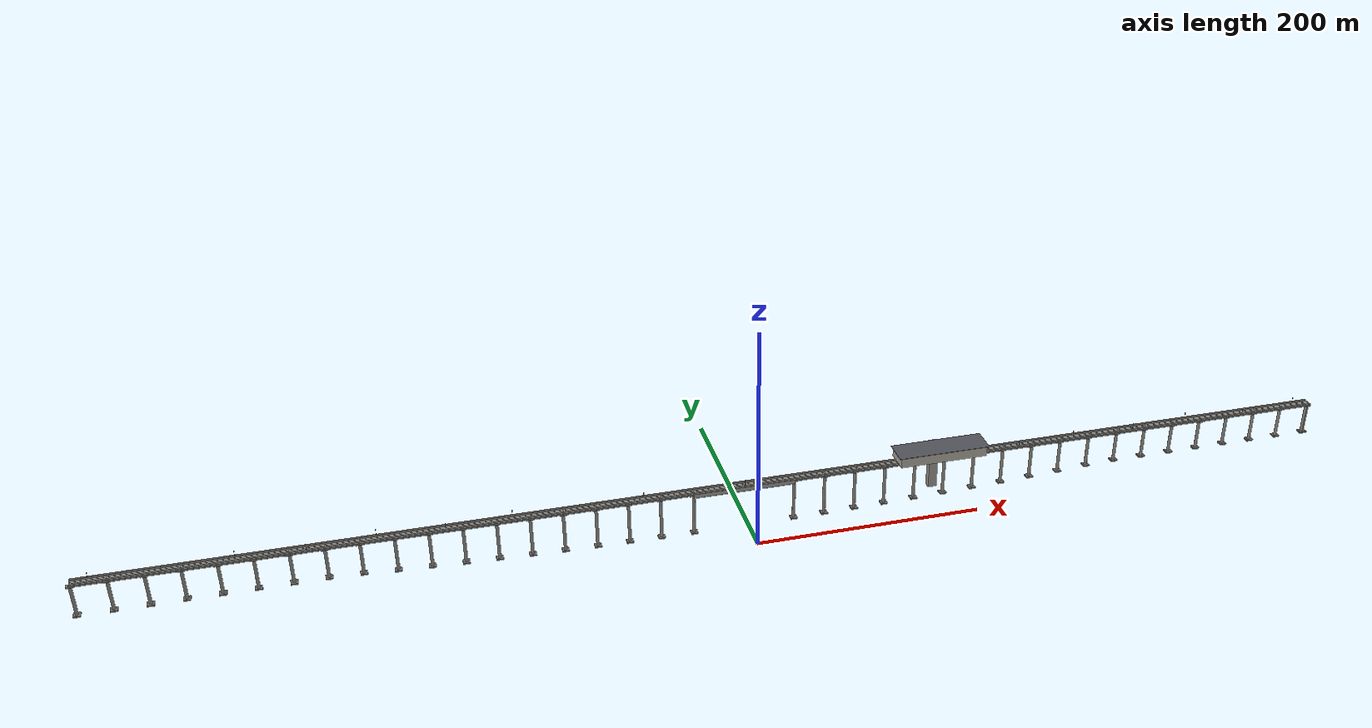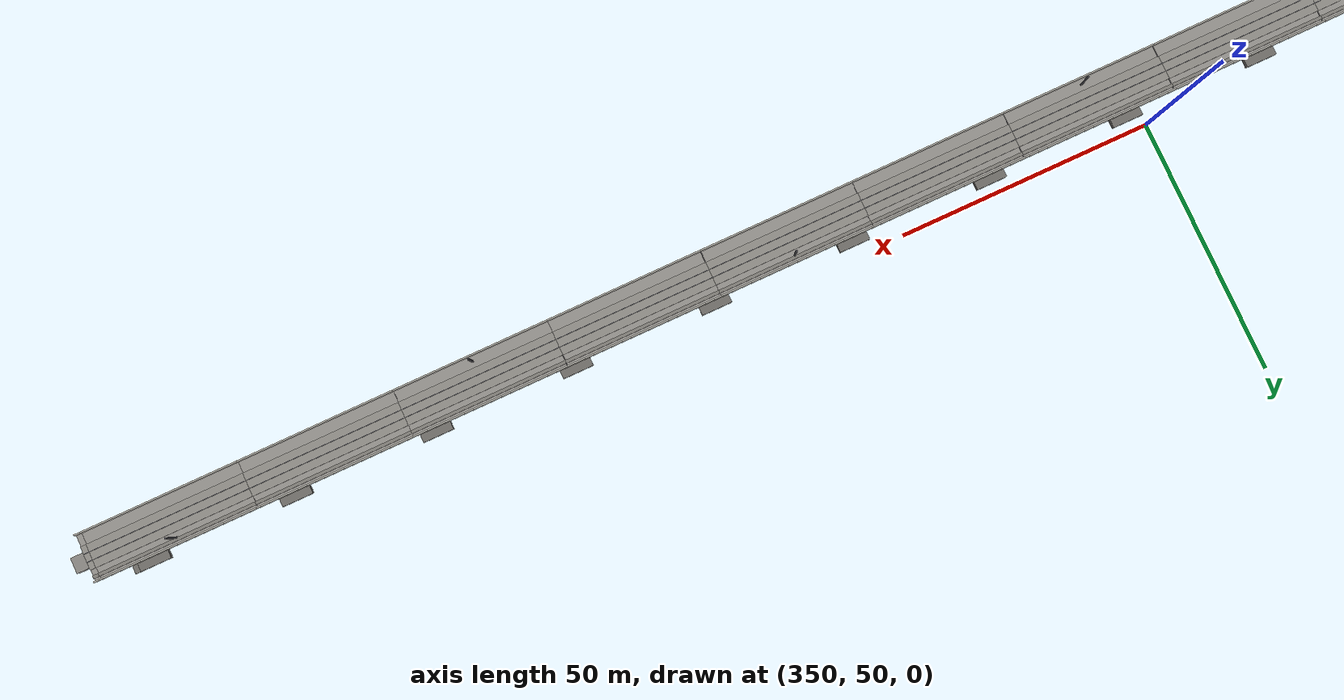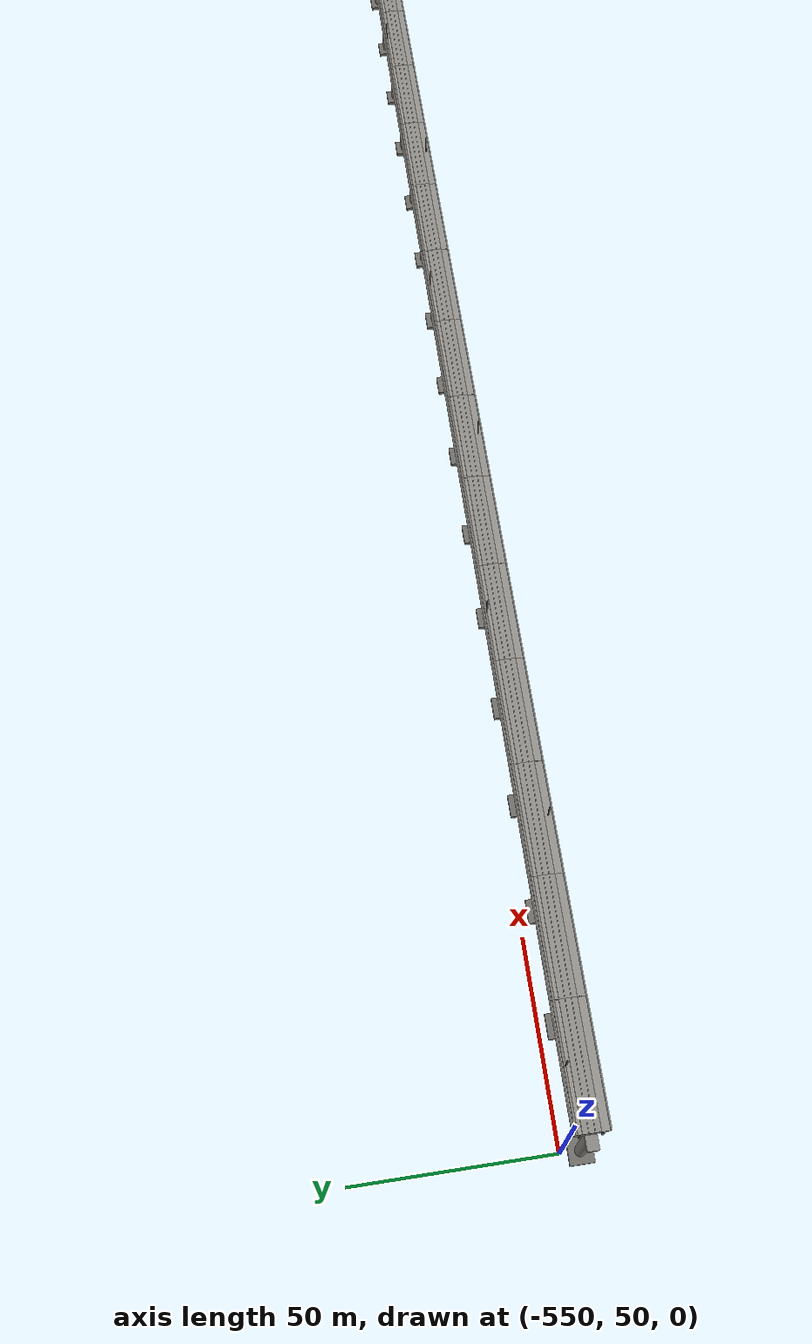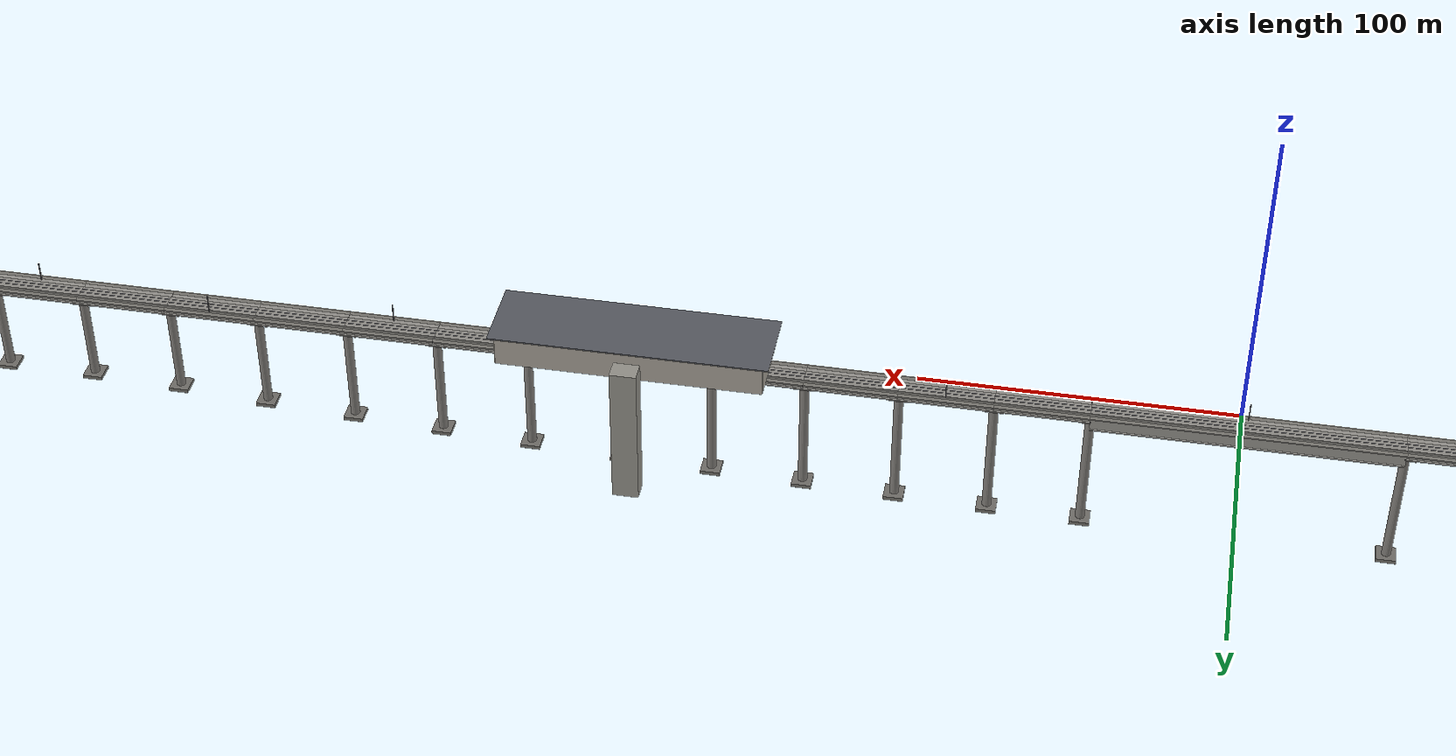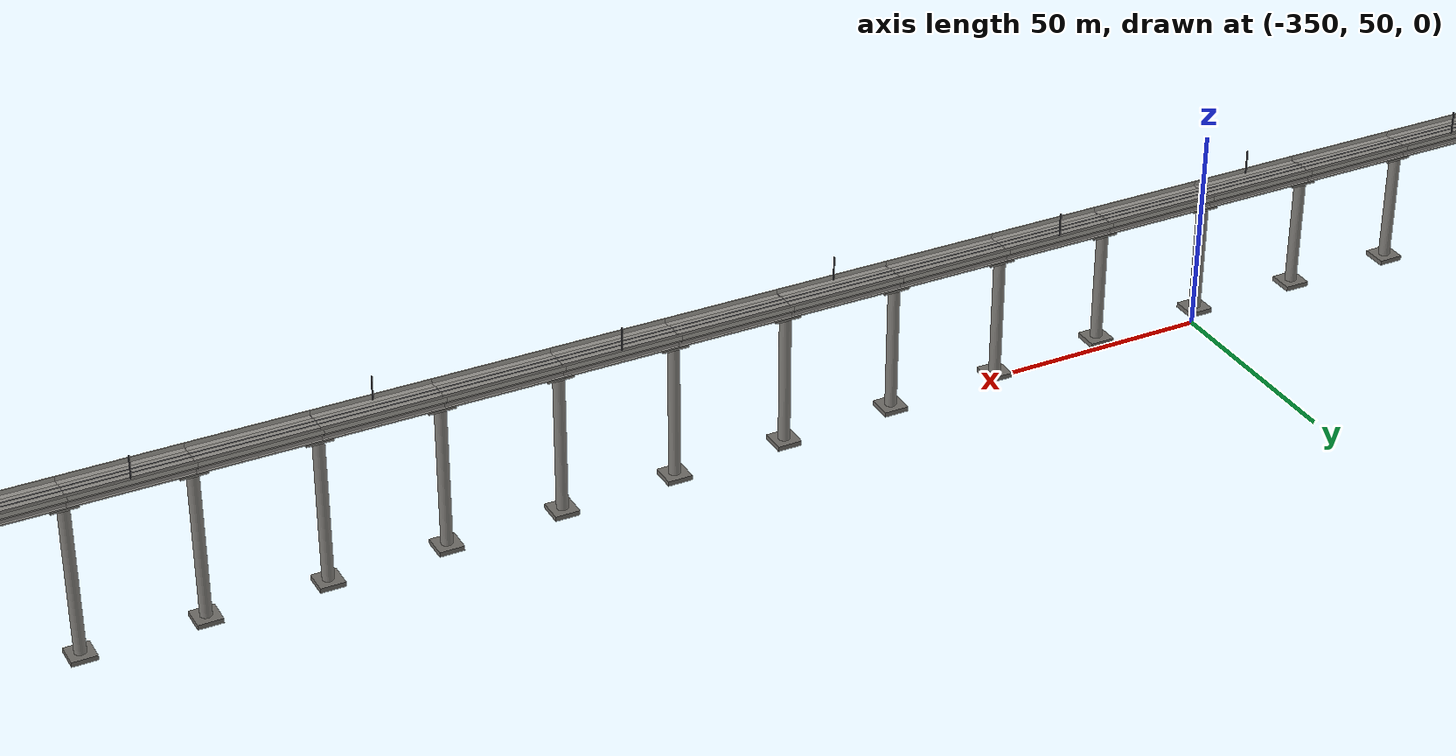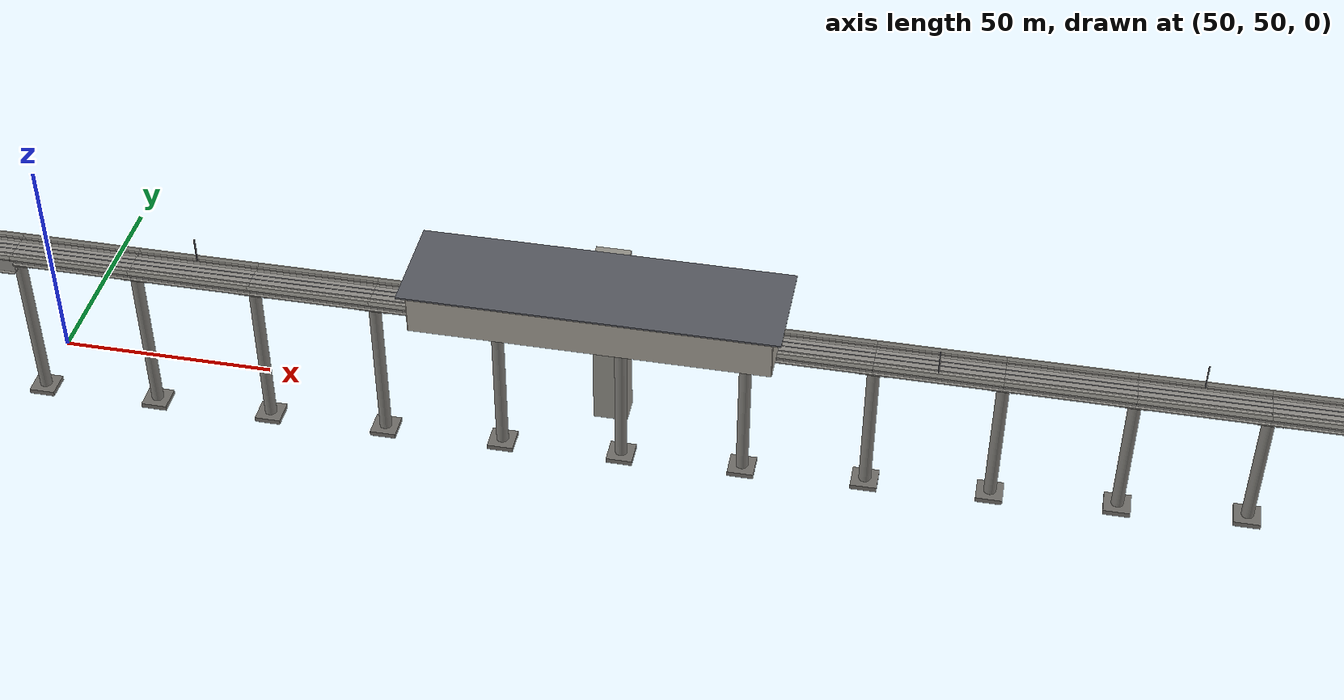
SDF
<?xml version="1.0" ?>
<sdf version="1.9">
  <model name="avian_metro">
    <static>true</static>
    <pose>0 0 0 0 0 0</pose>
    <link name="link">
      <collision name="MB_BEARING_001_B1_collision">
        <pose>-550.000000 47.600000 29.475000 0 0 0.000000</pose>
        <geometry>
          <box>
            <size>0.700000 0.700000 0.250000</size>
          </box>
        </geometry>
      </collision>
      <visual name="MB_BEARING_001_B1_visual">
        <pose>-550.000000 47.600000 29.475000 0 0 0.000000</pose>
        <geometry>
          <box>
            <size>0.700000 0.700000 0.250000</size>
          </box>
        </geometry>
        <material>
          <ambient>0.064 0.064 0.068 1</ambient>
          <diffuse>0.160 0.160 0.170 1</diffuse>
          <specular>0.1 0.1 0.1 1</specular>
        </material>
      </visual>
      <collision name="MB_BEARING_001_B2_collision">
        <pose>-550.000000 42.400000 29.475000 0 0 0.000000</pose>
        <geometry>
          <box>
            <size>0.700000 0.700000 0.250000</size>
          </box>
        </geometry>
      </collision>
      <visual name="MB_BEARING_001_B2_visual">
        <pose>-550.000000 42.400000 29.475000 0 0 0.000000</pose>
        <geometry>
          <box>
            <size>0.700000 0.700000 0.250000</size>
          </box>
        </geometry>
        <material>
          <ambient>0.064 0.064 0.068 1</ambient>
          <diffuse>0.160 0.160 0.170 1</diffuse>
          <specular>0.1 0.1 0.1 1</specular>
        </material>
      </visual>
      <collision name="MB_BEARING_002_B1_collision">
        <pose>-522.000000 47.600000 29.475000 0 0 0.000000</pose>
        <geometry>
          <box>
            <size>0.700000 0.700000 0.250000</size>
          </box>
        </geometry>
      </collision>
      <visual name="MB_BEARING_002_B1_visual">
        <pose>-522.000000 47.600000 29.475000 0 0 0.000000</pose>
        <geometry>
          <box>
            <size>0.700000 0.700000 0.250000</size>
          </box>
        </geometry>
        <material>
          <ambient>0.064 0.064 0.068 1</ambient>
          <diffuse>0.160 0.160 0.170 1</diffuse>
          <specular>0.1 0.1 0.1 1</specular>
        </material>
      </visual>
      <collision name="MB_BEARING_002_B2_collision">
        <pose>-522.000000 42.400000 29.475000 0 0 0.000000</pose>
        <geometry>
          <box>
            <size>0.700000 0.700000 0.250000</size>
          </box>
        </geometry>
      </collision>
      <visual name="MB_BEARING_002_B2_visual">
        <pose>-522.000000 42.400000 29.475000 0 0 0.000000</pose>
        <geometry>
          <box>
            <size>0.700000 0.700000 0.250000</size>
          </box>
        </geometry>
        <material>
          <ambient>0.064 0.064 0.068 1</ambient>
          <diffuse>0.160 0.160 0.170 1</diffuse>
          <specular>0.1 0.1 0.1 1</specular>
        </material>
      </visual>
      <collision name="MB_BEARING_003_B1_collision">
        <pose>-494.000000 47.600000 29.475000 0 0 0.000000</pose>
        <geometry>
          <box>
            <size>0.700000 0.700000 0.250000</size>
          </box>
        </geometry>
      </collision>
      <visual name="MB_BEARING_003_B1_visual">
        <pose>-494.000000 47.600000 29.475000 0 0 0.000000</pose>
        <geometry>
          <box>
            <size>0.700000 0.700000 0.250000</size>
          </box>
        </geometry>
        <material>
          <ambient>0.064 0.064 0.068 1</ambient>
          <diffuse>0.160 0.160 0.170 1</diffuse>
          <specular>0.1 0.1 0.1 1</specular>
        </material>
      </visual>
      <collision name="MB_BEARING_003_B2_collision">
        <pose>-494.000000 42.400000 29.475000 0 0 0.000000</pose>
        <geometry>
          <box>
            <size>0.700000 0.700000 0.250000</size>
          </box>
        </geometry>
      </collision>
      <visual name="MB_BEARING_003_B2_visual">
        <pose>-494.000000 42.400000 29.475000 0 0 0.000000</pose>
        <geometry>
          <box>
            <size>0.700000 0.700000 0.250000</size>
          </box>
        </geometry>
        <material>
          <ambient>0.064 0.064 0.068 1</ambient>
          <diffuse>0.160 0.160 0.170 1</diffuse>
          <specular>0.1 0.1 0.1 1</specular>
        </material>
      </visual>
      <collision name="MB_BEARING_004_B1_collision">
        <pose>-466.000000 47.600000 29.475000 0 0 0.000000</pose>
        <geometry>
          <box>
            <size>0.700000 0.700000 0.250000</size>
          </box>
        </geometry>
      </collision>
      <visual name="MB_BEARING_004_B1_visual">
        <pose>-466.000000 47.600000 29.475000 0 0 0.000000</pose>
        <geometry>
          <box>
            <size>0.700000 0.700000 0.250000</size>
          </box>
        </geometry>
        <material>
          <ambient>0.064 0.064 0.068 1</ambient>
          <diffuse>0.160 0.160 0.170 1</diffuse>
          <specular>0.1 0.1 0.1 1</specular>
        </material>
      </visual>
      <collision name="MB_BEARING_004_B2_collision">
        <pose>-466.000000 42.400000 29.475000 0 0 0.000000</pose>
        <geometry>
          <box>
            <size>0.700000 0.700000 0.250000</size>
          </box>
        </geometry>
      </collision>
      <visual name="MB_BEARING_004_B2_visual">
        <pose>-466.000000 42.400000 29.475000 0 0 0.000000</pose>
        <geometry>
          <box>
            <size>0.700000 0.700000 0.250000</size>
          </box>
        </geometry>
        <material>
          <ambient>0.064 0.064 0.068 1</ambient>
          <diffuse>0.160 0.160 0.170 1</diffuse>
          <specular>0.1 0.1 0.1 1</specular>
        </material>
      </visual>
      <collision name="MB_BEARING_005_B1_collision">
        <pose>-438.000000 47.600000 29.475000 0 0 0.000000</pose>
        <geometry>
          <box>
            <size>0.700000 0.700000 0.250000</size>
          </box>
        </geometry>
      </collision>
      <visual name="MB_BEARING_005_B1_visual">
        <pose>-438.000000 47.600000 29.475000 0 0 0.000000</pose>
        <geometry>
          <box>
            <size>0.700000 0.700000 0.250000</size>
          </box>
        </geometry>
        <material>
          <ambient>0.064 0.064 0.068 1</ambient>
          <diffuse>0.160 0.160 0.170 1</diffuse>
          <specular>0.1 0.1 0.1 1</specular>
        </material>
      </visual>
      <collision name="MB_BEARING_005_B2_collision">
        <pose>-438.000000 42.400000 29.475000 0 0 0.000000</pose>
        <geometry>
          <box>
            <size>0.700000 0.700000 0.250000</size>
          </box>
        </geometry>
      </collision>
      <visual name="MB_BEARING_005_B2_visual">
        <pose>-438.000000 42.400000 29.475000 0 0 0.000000</pose>
        <geometry>
          <box>
            <size>0.700000 0.700000 0.250000</size>
          </box>
        </geometry>
        <material>
          <ambient>0.064 0.064 0.068 1</ambient>
          <diffuse>0.160 0.160 0.170 1</diffuse>
          <specular>0.1 0.1 0.1 1</specular>
        </material>
      </visual>
      <collision name="MB_BEARING_006_B1_collision">
        <pose>-410.000000 47.600000 29.475000 0 0 0.000000</pose>
        <geometry>
          <box>
            <size>0.700000 0.700000 0.250000</size>
          </box>
        </geometry>
      </collision>
      <visual name="MB_BEARING_006_B1_visual">
        <pose>-410.000000 47.600000 29.475000 0 0 0.000000</pose>
        <geometry>
          <box>
            <size>0.700000 0.700000 0.250000</size>
          </box>
        </geometry>
        <material>
          <ambient>0.064 0.064 0.068 1</ambient>
          <diffuse>0.160 0.160 0.170 1</diffuse>
          <specular>0.1 0.1 0.1 1</specular>
        </material>
      </visual>
      <collision name="MB_BEARING_006_B2_collision">
        <pose>-410.000000 42.400000 29.475000 0 0 0.000000</pose>
        <geometry>
          <box>
            <size>0.700000 0.700000 0.250000</size>
          </box>
        </geometry>
      </collision>
      <visual name="MB_BEARING_006_B2_visual">
        <pose>-410.000000 42.400000 29.475000 0 0 0.000000</pose>
        <geometry>
          <box>
            <size>0.700000 0.700000 0.250000</size>
          </box>
        </geometry>
        <material>
          <ambient>0.064 0.064 0.068 1</ambient>
          <diffuse>0.160 0.160 0.170 1</diffuse>
          <specular>0.1 0.1 0.1 1</specular>
        </material>
      </visual>
      <collision name="MB_BEARING_007_B1_collision">
        <pose>-382.000000 47.600000 29.475000 0 0 0.000000</pose>
        <geometry>
          <box>
            <size>0.700000 0.700000 0.250000</size>
          </box>
        </geometry>
      </collision>
      <visual name="MB_BEARING_007_B1_visual">
        <pose>-382.000000 47.600000 29.475000 0 0 0.000000</pose>
        <geometry>
          <box>
            <size>0.700000 0.700000 0.250000</size>
          </box>
        </geometry>
        <material>
          <ambient>0.064 0.064 0.068 1</ambient>
          <diffuse>0.160 0.160 0.170 1</diffuse>
          <specular>0.1 0.1 0.1 1</specular>
        </material>
      </visual>
      <collision name="MB_BEARING_007_B2_collision">
        <pose>-382.000000 42.400000 29.475000 0 0 0.000000</pose>
        <geometry>
          <box>
            <size>0.700000 0.700000 0.250000</size>
          </box>
        </geometry>
      </collision>
      <visual name="MB_BEARING_007_B2_visual">
        <pose>-382.000000 42.400000 29.475000 0 0 0.000000</pose>
        <geometry>
          <box>
            <size>0.700000 0.700000 0.250000</size>
          </box>
        </geometry>
        <material>
          <ambient>0.064 0.064 0.068 1</ambient>
          <diffuse>0.160 0.160 0.170 1</diffuse>
          <specular>0.1 0.1 0.1 1</specular>
        </material>
      </visual>
      <collision name="MB_BEARING_008_B1_collision">
        <pose>-354.000000 47.600000 29.475000 0 0 0.000000</pose>
        <geometry>
          <box>
            <size>0.700000 0.700000 0.250000</size>
          </box>
        </geometry>
      </collision>
      <visual name="MB_BEARING_008_B1_visual">
        <pose>-354.000000 47.600000 29.475000 0 0 0.000000</pose>
        <geometry>
          <box>
            <size>0.700000 0.700000 0.250000</size>
          </box>
        </geometry>
        <material>
          <ambient>0.064 0.064 0.068 1</ambient>
          <diffuse>0.160 0.160 0.170 1</diffuse>
          <specular>0.1 0.1 0.1 1</specular>
        </material>
      </visual>
      <collision name="MB_BEARING_008_B2_collision">
        <pose>-354.000000 42.400000 29.475000 0 0 0.000000</pose>
        <geometry>
          <box>
            <size>0.700000 0.700000 0.250000</size>
          </box>
        </geometry>
      </collision>
      <visual name="MB_BEARING_008_B2_visual">
        <pose>-354.000000 42.400000 29.475000 0 0 0.000000</pose>
        <geometry>
          <box>
            <size>0.700000 0.700000 0.250000</size>
          </box>
        </geometry>
        <material>
          <ambient>0.064 0.064 0.068 1</ambient>
          <diffuse>0.160 0.160 0.170 1</diffuse>
          <specular>0.1 0.1 0.1 1</specular>
        </material>
      </visual>
      <collision name="MB_BEARING_009_B1_collision">
        <pose>-326.000000 47.600000 29.475000 0 0 0.000000</pose>
        <geometry>
          <box>
            <size>0.700000 0.700000 0.250000</size>
          </box>
        </geometry>
      </collision>
      <visual name="MB_BEARING_009_B1_visual">
        <pose>-326.000000 47.600000 29.475000 0 0 0.000000</pose>
        <geometry>
          <box>
            <size>0.700000 0.700000 0.250000</size>
          </box>
        </geometry>
        <material>
          <ambient>0.064 0.064 0.068 1</ambient>
          <diffuse>0.160 0.160 0.170 1</diffuse>
          <specular>0.1 0.1 0.1 1</specular>
        </material>
      </visual>
      <collision name="MB_BEARING_009_B2_collision">
        <pose>-326.000000 42.400000 29.475000 0 0 0.000000</pose>
        <geometry>
          <box>
            <size>0.700000 0.700000 0.250000</size>
          </box>
        </geometry>
      </collision>
      <visual name="MB_BEARING_009_B2_visual">
        <pose>-326.000000 42.400000 29.475000 0 0 0.000000</pose>
        <geometry>
          <box>
            <size>0.700000 0.700000 0.250000</size>
          </box>
        </geometry>
        <material>
          <ambient>0.064 0.064 0.068 1</ambient>
          <diffuse>0.160 0.160 0.170 1</diffuse>
          <specular>0.1 0.1 0.1 1</specular>
        </material>
      </visual>
      <collision name="MB_BEARING_010_B1_collision">
        <pose>-298.000000 47.600000 29.475000 0 0 0.000000</pose>
        <geometry>
          <box>
            <size>0.700000 0.700000 0.250000</size>
          </box>
        </geometry>
      </collision>
      <visual name="MB_BEARING_010_B1_visual">
        <pose>-298.000000 47.600000 29.475000 0 0 0.000000</pose>
        <geometry>
          <box>
            <size>0.700000 0.700000 0.250000</size>
          </box>
        </geometry>
        <material>
          <ambient>0.064 0.064 0.068 1</ambient>
          <diffuse>0.160 0.160 0.170 1</diffuse>
          <specular>0.1 0.1 0.1 1</specular>
        </material>
      </visual>
      <collision name="MB_BEARING_010_B2_collision">
        <pose>-298.000000 42.400000 29.475000 0 0 0.000000</pose>
        <geometry>
          <box>
            <size>0.700000 0.700000 0.250000</size>
          </box>
        </geometry>
      </collision>
      <visual name="MB_BEARING_010_B2_visual">
        <pose>-298.000000 42.400000 29.475000 0 0 0.000000</pose>
        <geometry>
          <box>
            <size>0.700000 0.700000 0.250000</size>
          </box>
        </geometry>
        <material>
          <ambient>0.064 0.064 0.068 1</ambient>
          <diffuse>0.160 0.160 0.170 1</diffuse>
          <specular>0.1 0.1 0.1 1</specular>
        </material>
      </visual>
      <collision name="MB_BEARING_011_B1_collision">
        <pose>-270.000000 47.600000 29.475000 0 0 0.000000</pose>
        <geometry>
          <box>
            <size>0.700000 0.700000 0.250000</size>
          </box>
        </geometry>
      </collision>
      <visual name="MB_BEARING_011_B1_visual">
        <pose>-270.000000 47.600000 29.475000 0 0 0.000000</pose>
        <geometry>
          <box>
            <size>0.700000 0.700000 0.250000</size>
          </box>
        </geometry>
        <material>
          <ambient>0.064 0.064 0.068 1</ambient>
          <diffuse>0.160 0.160 0.170 1</diffuse>
          <specular>0.1 0.1 0.1 1</specular>
        </material>
      </visual>
      <collision name="MB_BEARING_011_B2_collision">
        <pose>-270.000000 42.400000 29.475000 0 0 0.000000</pose>
        <geometry>
          <box>
            <size>0.700000 0.700000 0.250000</size>
          </box>
        </geometry>
      </collision>
      <visual name="MB_BEARING_011_B2_visual">
        <pose>-270.000000 42.400000 29.475000 0 0 0.000000</pose>
        <geometry>
          <box>
            <size>0.700000 0.700000 0.250000</size>
          </box>
        </geometry>
        <material>
          <ambient>0.064 0.064 0.068 1</ambient>
          <diffuse>0.160 0.160 0.170 1</diffuse>
          <specular>0.1 0.1 0.1 1</specular>
        </material>
      </visual>
      <collision name="MB_BEARING_012_B1_collision">
        <pose>-242.000000 47.600000 29.475000 0 0 0.000000</pose>
        <geometry>
          <box>
            <size>0.700000 0.700000 0.250000</size>
          </box>
        </geometry>
      </collision>
      <visual name="MB_BEARING_012_B1_visual">
        <pose>-242.000000 47.600000 29.475000 0 0 0.000000</pose>
        <geometry>
          <box>
            <size>0.700000 0.700000 0.250000</size>
          </box>
        </geometry>
        <material>
          <ambient>0.064 0.064 0.068 1</ambient>
          <diffuse>0.160 0.160 0.170 1</diffuse>
          <specular>0.1 0.1 0.1 1</specular>
        </material>
      </visual>
      <collision name="MB_BEARING_012_B2_collision">
        <pose>-242.000000 42.400000 29.475000 0 0 0.000000</pose>
        <geometry>
          <box>
            <size>0.700000 0.700000 0.250000</size>
          </box>
        </geometry>
      </collision>
      <visual name="MB_BEARING_012_B2_visual">
        <pose>-242.000000 42.400000 29.475000 0 0 0.000000</pose>
        <geometry>
          <box>
            <size>0.700000 0.700000 0.250000</size>
          </box>
        </geometry>
        <material>
          <ambient>0.064 0.064 0.068 1</ambient>
          <diffuse>0.160 0.160 0.170 1</diffuse>
          <specular>0.1 0.1 0.1 1</specular>
        </material>
      </visual>
      <collision name="MB_BEARING_013_B1_collision">
        <pose>-214.000000 47.600000 29.475000 0 0 0.000000</pose>
        <geometry>
          <box>
            <size>0.700000 0.700000 0.250000</size>
          </box>
        </geometry>
      </collision>
      <visual name="MB_BEARING_013_B1_visual">
        <pose>-214.000000 47.600000 29.475000 0 0 0.000000</pose>
        <geometry>
          <box>
            <size>0.700000 0.700000 0.250000</size>
          </box>
        </geometry>
        <material>
          <ambient>0.064 0.064 0.068 1</ambient>
          <diffuse>0.160 0.160 0.170 1</diffuse>
          <specular>0.1 0.1 0.1 1</specular>
        </material>
      </visual>
      <collision name="MB_BEARING_013_B2_collision">
        <pose>-214.000000 42.400000 29.475000 0 0 0.000000</pose>
        <geometry>
          <box>
            <size>0.700000 0.700000 0.250000</size>
          </box>
        </geometry>
      </collision>
      <visual name="MB_BEARING_013_B2_visual">
        <pose>-214.000000 42.400000 29.475000 0 0 0.000000</pose>
        <geometry>
          <box>
            <size>0.700000 0.700000 0.250000</size>
          </box>
        </geometry>
        <material>
          <ambient>0.064 0.064 0.068 1</ambient>
          <diffuse>0.160 0.160 0.170 1</diffuse>
          <specular>0.1 0.1 0.1 1</specular>
        </material>
      </visual>
      <collision name="MB_BEARING_014_B1_collision">
        <pose>-186.000000 47.600000 29.475000 0 0 0.000000</pose>
        <geometry>
          <box>
            <size>0.700000 0.700000 0.250000</size>
          </box>
        </geometry>
      </collision>
      <visual name="MB_BEARING_014_B1_visual">
        <pose>-186.000000 47.600000 29.475000 0 0 0.000000</pose>
        <geometry>
          <box>
            <size>0.700000 0.700000 0.250000</size>
          </box>
        </geometry>
        <material>
          <ambient>0.064 0.064 0.068 1</ambient>
          <diffuse>0.160 0.160 0.170 1</diffuse>
          <specular>0.1 0.1 0.1 1</specular>
        </material>
      </visual>
      <collision name="MB_BEARING_014_B2_collision">
        <pose>-186.000000 42.400000 29.475000 0 0 0.000000</pose>
        <geometry>
          <box>
            <size>0.700000 0.700000 0.250000</size>
          </box>
        </geometry>
      </collision>
      <visual name="MB_BEARING_014_B2_visual">
        <pose>-186.000000 42.400000 29.475000 0 0 0.000000</pose>
        <geometry>
          <box>
            <size>0.700000 0.700000 0.250000</size>
          </box>
        </geometry>
        <material>
          <ambient>0.064 0.064 0.068 1</ambient>
          <diffuse>0.160 0.160 0.170 1</diffuse>
          <specular>0.1 0.1 0.1 1</specular>
        </material>
      </visual>
      <collision name="MB_BEARING_015_B1_collision">
        <pose>-158.000000 47.600000 29.475000 0 0 0.000000</pose>
        <geometry>
          <box>
            <size>0.700000 0.700000 0.250000</size>
          </box>
        </geometry>
      </collision>
      <visual name="MB_BEARING_015_B1_visual">
        <pose>-158.000000 47.600000 29.475000 0 0 0.000000</pose>
        <geometry>
          <box>
            <size>0.700000 0.700000 0.250000</size>
          </box>
        </geometry>
        <material>
          <ambient>0.064 0.064 0.068 1</ambient>
          <diffuse>0.160 0.160 0.170 1</diffuse>
          <specular>0.1 0.1 0.1 1</specular>
        </material>
      </visual>
      <collision name="MB_BEARING_015_B2_collision">
        <pose>-158.000000 42.400000 29.475000 0 0 0.000000</pose>
        <geometry>
          <box>
            <size>0.700000 0.700000 0.250000</size>
          </box>
        </geometry>
      </collision>
      <visual name="MB_BEARING_015_B2_visual">
        <pose>-158.000000 42.400000 29.475000 0 0 0.000000</pose>
        <geometry>
          <box>
            <size>0.700000 0.700000 0.250000</size>
          </box>
        </geometry>
        <material>
          <ambient>0.064 0.064 0.068 1</ambient>
          <diffuse>0.160 0.160 0.170 1</diffuse>
          <specular>0.1 0.1 0.1 1</specular>
        </material>
      </visual>
      <collision name="MB_BEARING_016_B1_collision">
        <pose>-130.000000 47.600000 29.475000 0 0 0.000000</pose>
        <geometry>
          <box>
            <size>0.700000 0.700000 0.250000</size>
          </box>
        </geometry>
      </collision>
      <visual name="MB_BEARING_016_B1_visual">
        <pose>-130.000000 47.600000 29.475000 0 0 0.000000</pose>
        <geometry>
          <box>
            <size>0.700000 0.700000 0.250000</size>
          </box>
        </geometry>
        <material>
          <ambient>0.064 0.064 0.068 1</ambient>
          <diffuse>0.160 0.160 0.170 1</diffuse>
          <specular>0.1 0.1 0.1 1</specular>
        </material>
      </visual>
      <collision name="MB_BEARING_016_B2_collision">
        <pose>-130.000000 42.400000 29.475000 0 0 0.000000</pose>
        <geometry>
          <box>
            <size>0.700000 0.700000 0.250000</size>
          </box>
        </geometry>
      </collision>
      <visual name="MB_BEARING_016_B2_visual">
        <pose>-130.000000 42.400000 29.475000 0 0 0.000000</pose>
        <geometry>
          <box>
            <size>0.700000 0.700000 0.250000</size>
          </box>
        </geometry>
        <material>
          <ambient>0.064 0.064 0.068 1</ambient>
          <diffuse>0.160 0.160 0.170 1</diffuse>
          <specular>0.1 0.1 0.1 1</specular>
        </material>
      </visual>
      <collision name="MB_BEARING_017_B1_collision">
        <pose>-102.000000 47.600000 29.475000 0 0 0.000000</pose>
        <geometry>
          <box>
            <size>0.700000 0.700000 0.250000</size>
          </box>
        </geometry>
      </collision>
      <visual name="MB_BEARING_017_B1_visual">
        <pose>-102.000000 47.600000 29.475000 0 0 0.000000</pose>
        <geometry>
          <box>
            <size>0.700000 0.700000 0.250000</size>
          </box>
        </geometry>
        <material>
          <ambient>0.064 0.064 0.068 1</ambient>
          <diffuse>0.160 0.160 0.170 1</diffuse>
          <specular>0.1 0.1 0.1 1</specular>
        </material>
      </visual>
      <collision name="MB_BEARING_017_B2_collision">
        <pose>-102.000000 42.400000 29.475000 0 0 0.000000</pose>
        <geometry>
          <box>
            <size>0.700000 0.700000 0.250000</size>
          </box>
        </geometry>
      </collision>
      <visual name="MB_BEARING_017_B2_visual">
        <pose>-102.000000 42.400000 29.475000 0 0 0.000000</pose>
        <geometry>
          <box>
            <size>0.700000 0.700000 0.250000</size>
          </box>
        </geometry>
        <material>
          <ambient>0.064 0.064 0.068 1</ambient>
          <diffuse>0.160 0.160 0.170 1</diffuse>
          <specular>0.1 0.1 0.1 1</specular>
        </material>
      </visual>
      <collision name="MB_BEARING_018_B1_collision">
        <pose>-74.000000 47.600000 29.475000 0 0 0.000000</pose>
        <geometry>
          <box>
            <size>0.700000 0.700000 0.250000</size>
          </box>
        </geometry>
      </collision>
      <visual name="MB_BEARING_018_B1_visual">
        <pose>-74.000000 47.600000 29.475000 0 0 0.000000</pose>
        <geometry>
          <box>
            <size>0.700000 0.700000 0.250000</size>
          </box>
        </geometry>
        <material>
          <ambient>0.064 0.064 0.068 1</ambient>
          <diffuse>0.160 0.160 0.170 1</diffuse>
          <specular>0.1 0.1 0.1 1</specular>
        </material>
      </visual>
      <collision name="MB_BEARING_018_B2_collision">
        <pose>-74.000000 42.400000 29.475000 0 0 0.000000</pose>
        <geometry>
          <box>
            <size>0.700000 0.700000 0.250000</size>
          </box>
        </geometry>
      </collision>
      <visual name="MB_BEARING_018_B2_visual">
        <pose>-74.000000 42.400000 29.475000 0 0 0.000000</pose>
        <geometry>
          <box>
            <size>0.700000 0.700000 0.250000</size>
          </box>
        </geometry>
        <material>
          <ambient>0.064 0.064 0.068 1</ambient>
          <diffuse>0.160 0.160 0.170 1</diffuse>
          <specular>0.1 0.1 0.1 1</specular>
        </material>
      </visual>
      <collision name="MB_BEARING_019_B1_collision">
        <pose>-45.000000 47.600000 29.475000 0 0 0.000000</pose>
        <geometry>
          <box>
            <size>0.700200 0.700000 0.250000</size>
          </box>
        </geometry>
      </collision>
      <visual name="MB_BEARING_019_B1_visual">
        <pose>-45.000000 47.600000 29.475000 0 0 0.000000</pose>
        <geometry>
          <box>
            <size>0.700200 0.700000 0.250000</size>
          </box>
        </geometry>
        <material>
          <ambient>0.064 0.064 0.068 1</ambient>
          <diffuse>0.160 0.160 0.170 1</diffuse>
          <specular>0.1 0.1 0.1 1</specular>
        </material>
      </visual>
      <collision name="MB_BEARING_019_B2_collision">
        <pose>-45.000000 42.400000 29.475000 0 0 0.000000</pose>
        <geometry>
          <box>
            <size>0.700200 0.700000 0.250000</size>
          </box>
        </geometry>
      </collision>
      <visual name="MB_BEARING_019_B2_visual">
        <pose>-45.000000 42.400000 29.475000 0 0 0.000000</pose>
        <geometry>
          <box>
            <size>0.700200 0.700000 0.250000</size>
          </box>
        </geometry>
        <material>
          <ambient>0.064 0.064 0.068 1</ambient>
          <diffuse>0.160 0.160 0.170 1</diffuse>
          <specular>0.1 0.1 0.1 1</specular>
        </material>
      </visual>
      <collision name="MB_BEARING_020_B1_collision">
        <pose>45.000000 47.600000 29.475000 0 0 0.000000</pose>
        <geometry>
          <box>
            <size>0.700200 0.700000 0.250000</size>
          </box>
        </geometry>
      </collision>
      <visual name="MB_BEARING_020_B1_visual">
        <pose>45.000000 47.600000 29.475000 0 0 0.000000</pose>
        <geometry>
          <box>
            <size>0.700200 0.700000 0.250000</size>
          </box>
        </geometry>
        <material>
          <ambient>0.064 0.064 0.068 1</ambient>
          <diffuse>0.160 0.160 0.170 1</diffuse>
          <specular>0.1 0.1 0.1 1</specular>
        </material>
      </visual>
      <collision name="MB_BEARING_020_B2_collision">
        <pose>45.000000 42.400000 29.475000 0 0 0.000000</pose>
        <geometry>
          <box>
            <size>0.700200 0.700000 0.250000</size>
          </box>
        </geometry>
      </collision>
      <visual name="MB_BEARING_020_B2_visual">
        <pose>45.000000 42.400000 29.475000 0 0 0.000000</pose>
        <geometry>
          <box>
            <size>0.700200 0.700000 0.250000</size>
          </box>
        </geometry>
        <material>
          <ambient>0.064 0.064 0.068 1</ambient>
          <diffuse>0.160 0.160 0.170 1</diffuse>
          <specular>0.1 0.1 0.1 1</specular>
        </material>
      </visual>
      <collision name="MB_BEARING_021_B1_collision">
        <pose>73.000000 47.600000 29.475000 0 0 0.000000</pose>
        <geometry>
          <box>
            <size>0.700200 0.700000 0.250000</size>
          </box>
        </geometry>
      </collision>
      <visual name="MB_BEARING_021_B1_visual">
        <pose>73.000000 47.600000 29.475000 0 0 0.000000</pose>
        <geometry>
          <box>
            <size>0.700200 0.700000 0.250000</size>
          </box>
        </geometry>
        <material>
          <ambient>0.064 0.064 0.068 1</ambient>
          <diffuse>0.160 0.160 0.170 1</diffuse>
          <specular>0.1 0.1 0.1 1</specular>
        </material>
      </visual>
      <collision name="MB_BEARING_021_B2_collision">
        <pose>73.000000 42.400000 29.475000 0 0 0.000000</pose>
        <geometry>
          <box>
            <size>0.700200 0.700000 0.250000</size>
          </box>
        </geometry>
      </collision>
      <visual name="MB_BEARING_021_B2_visual">
        <pose>73.000000 42.400000 29.475000 0 0 0.000000</pose>
        <geometry>
          <box>
            <size>0.700200 0.700000 0.250000</size>
          </box>
        </geometry>
        <material>
          <ambient>0.064 0.064 0.068 1</ambient>
          <diffuse>0.160 0.160 0.170 1</diffuse>
          <specular>0.1 0.1 0.1 1</specular>
        </material>
      </visual>
      <collision name="MB_BEARING_022_B1_collision">
        <pose>101.000000 47.600000 29.475000 0 0 0.000000</pose>
        <geometry>
          <box>
            <size>0.700200 0.700000 0.250000</size>
          </box>
        </geometry>
      </collision>
      <visual name="MB_BEARING_022_B1_visual">
        <pose>101.000000 47.600000 29.475000 0 0 0.000000</pose>
        <geometry>
          <box>
            <size>0.700200 0.700000 0.250000</size>
          </box>
        </geometry>
        <material>
          <ambient>0.064 0.064 0.068 1</ambient>
          <diffuse>0.160 0.160 0.170 1</diffuse>
          <specular>0.1 0.1 0.1 1</specular>
        </material>
      </visual>
      <collision name="MB_BEARING_022_B2_collision">
        <pose>101.000000 42.400000 29.475000 0 0 0.000000</pose>
        <geometry>
          <box>
            <size>0.700200 0.700000 0.250000</size>
          </box>
        </geometry>
      </collision>
      <visual name="MB_BEARING_022_B2_visual">
        <pose>101.000000 42.400000 29.475000 0 0 0.000000</pose>
        <geometry>
          <box>
            <size>0.700200 0.700000 0.250000</size>
          </box>
        </geometry>
        <material>
          <ambient>0.064 0.064 0.068 1</ambient>
          <diffuse>0.160 0.160 0.170 1</diffuse>
          <specular>0.1 0.1 0.1 1</specular>
        </material>
      </visual>
      <collision name="MB_BEARING_023_B1_collision">
        <pose>129.000000 47.600000 29.475000 0 0 0.000000</pose>
        <geometry>
          <box>
            <size>0.700200 0.700000 0.250000</size>
          </box>
        </geometry>
      </collision>
      <visual name="MB_BEARING_023_B1_visual">
        <pose>129.000000 47.600000 29.475000 0 0 0.000000</pose>
        <geometry>
          <box>
            <size>0.700200 0.700000 0.250000</size>
          </box>
        </geometry>
        <material>
          <ambient>0.064 0.064 0.068 1</ambient>
          <diffuse>0.160 0.160 0.170 1</diffuse>
          <specular>0.1 0.1 0.1 1</specular>
        </material>
      </visual>
      <collision name="MB_BEARING_023_B2_collision">
        <pose>129.000000 42.400000 29.475000 0 0 0.000000</pose>
        <geometry>
          <box>
            <size>0.700200 0.700000 0.250000</size>
          </box>
        </geometry>
      </collision>
      <visual name="MB_BEARING_023_B2_visual">
        <pose>129.000000 42.400000 29.475000 0 0 0.000000</pose>
        <geometry>
          <box>
            <size>0.700200 0.700000 0.250000</size>
          </box>
        </geometry>
        <material>
          <ambient>0.064 0.064 0.068 1</ambient>
          <diffuse>0.160 0.160 0.170 1</diffuse>
          <specular>0.1 0.1 0.1 1</specular>
        </material>
      </visual>
      <collision name="MB_BEARING_024_B1_collision">
        <pose>157.000000 47.600000 29.475000 0 0 0.000000</pose>
        <geometry>
          <box>
            <size>0.700200 0.700000 0.250000</size>
          </box>
        </geometry>
      </collision>
      <visual name="MB_BEARING_024_B1_visual">
        <pose>157.000000 47.600000 29.475000 0 0 0.000000</pose>
        <geometry>
          <box>
            <size>0.700200 0.700000 0.250000</size>
          </box>
        </geometry>
        <material>
          <ambient>0.064 0.064 0.068 1</ambient>
          <diffuse>0.160 0.160 0.170 1</diffuse>
          <specular>0.1 0.1 0.1 1</specular>
        </material>
      </visual>
      <collision name="MB_BEARING_024_B2_collision">
        <pose>157.000000 42.400000 29.475000 0 0 0.000000</pose>
        <geometry>
          <box>
            <size>0.700200 0.700000 0.250000</size>
          </box>
        </geometry>
      </collision>
      <visual name="MB_BEARING_024_B2_visual">
        <pose>157.000000 42.400000 29.475000 0 0 0.000000</pose>
        <geometry>
          <box>
            <size>0.700200 0.700000 0.250000</size>
          </box>
        </geometry>
        <material>
          <ambient>0.064 0.064 0.068 1</ambient>
          <diffuse>0.160 0.160 0.170 1</diffuse>
          <specular>0.1 0.1 0.1 1</specular>
        </material>
      </visual>
      <collision name="MB_BEARING_025_B1_collision">
        <pose>185.000000 47.600000 29.475000 0 0 0.000000</pose>
        <geometry>
          <box>
            <size>0.700200 0.700000 0.250000</size>
          </box>
        </geometry>
      </collision>
      <visual name="MB_BEARING_025_B1_visual">
        <pose>185.000000 47.600000 29.475000 0 0 0.000000</pose>
        <geometry>
          <box>
            <size>0.700200 0.700000 0.250000</size>
          </box>
        </geometry>
        <material>
          <ambient>0.064 0.064 0.068 1</ambient>
          <diffuse>0.160 0.160 0.170 1</diffuse>
          <specular>0.1 0.1 0.1 1</specular>
        </material>
      </visual>
      <collision name="MB_BEARING_025_B2_collision">
        <pose>185.000000 42.400000 29.475000 0 0 0.000000</pose>
        <geometry>
          <box>
            <size>0.700200 0.700000 0.250000</size>
          </box>
        </geometry>
      </collision>
      <visual name="MB_BEARING_025_B2_visual">
        <pose>185.000000 42.400000 29.475000 0 0 0.000000</pose>
        <geometry>
          <box>
            <size>0.700200 0.700000 0.250000</size>
          </box>
        </geometry>
        <material>
          <ambient>0.064 0.064 0.068 1</ambient>
          <diffuse>0.160 0.160 0.170 1</diffuse>
          <specular>0.1 0.1 0.1 1</specular>
        </material>
      </visual>
      <collision name="MB_BEARING_026_B1_collision">
        <pose>213.000000 47.600000 29.475000 0 0 0.000000</pose>
        <geometry>
          <box>
            <size>0.700200 0.700000 0.250000</size>
          </box>
        </geometry>
      </collision>
      <visual name="MB_BEARING_026_B1_visual">
        <pose>213.000000 47.600000 29.475000 0 0 0.000000</pose>
        <geometry>
          <box>
            <size>0.700200 0.700000 0.250000</size>
          </box>
        </geometry>
        <material>
          <ambient>0.064 0.064 0.068 1</ambient>
          <diffuse>0.160 0.160 0.170 1</diffuse>
          <specular>0.1 0.1 0.1 1</specular>
        </material>
      </visual>
      <collision name="MB_BEARING_026_B2_collision">
        <pose>213.000000 42.400000 29.475000 0 0 0.000000</pose>
        <geometry>
          <box>
            <size>0.700200 0.700000 0.250000</size>
          </box>
        </geometry>
      </collision>
      <visual name="MB_BEARING_026_B2_visual">
        <pose>213.000000 42.400000 29.475000 0 0 0.000000</pose>
        <geometry>
          <box>
            <size>0.700200 0.700000 0.250000</size>
          </box>
        </geometry>
        <material>
          <ambient>0.064 0.064 0.068 1</ambient>
          <diffuse>0.160 0.160 0.170 1</diffuse>
          <specular>0.1 0.1 0.1 1</specular>
        </material>
      </visual>
      <collision name="MB_BEARING_027_B1_collision">
        <pose>241.000000 47.600000 29.475000 0 0 0.000000</pose>
        <geometry>
          <box>
            <size>0.700200 0.700000 0.250000</size>
          </box>
        </geometry>
      </collision>
      <visual name="MB_BEARING_027_B1_visual">
        <pose>241.000000 47.600000 29.475000 0 0 0.000000</pose>
        <geometry>
          <box>
            <size>0.700200 0.700000 0.250000</size>
          </box>
        </geometry>
        <material>
          <ambient>0.064 0.064 0.068 1</ambient>
          <diffuse>0.160 0.160 0.170 1</diffuse>
          <specular>0.1 0.1 0.1 1</specular>
        </material>
      </visual>
      <collision name="MB_BEARING_027_B2_collision">
        <pose>241.000000 42.400000 29.475000 0 0 0.000000</pose>
        <geometry>
          <box>
            <size>0.700200 0.700000 0.250000</size>
          </box>
        </geometry>
      </collision>
      <visual name="MB_BEARING_027_B2_visual">
        <pose>241.000000 42.400000 29.475000 0 0 0.000000</pose>
        <geometry>
          <box>
            <size>0.700200 0.700000 0.250000</size>
          </box>
        </geometry>
        <material>
          <ambient>0.064 0.064 0.068 1</ambient>
          <diffuse>0.160 0.160 0.170 1</diffuse>
          <specular>0.1 0.1 0.1 1</specular>
        </material>
      </visual>
      <collision name="MB_BEARING_028_B1_collision">
        <pose>269.000000 47.600000 29.475000 0 0 0.000000</pose>
        <geometry>
          <box>
            <size>0.700200 0.700000 0.250000</size>
          </box>
        </geometry>
      </collision>
      <visual name="MB_BEARING_028_B1_visual">
        <pose>269.000000 47.600000 29.475000 0 0 0.000000</pose>
        <geometry>
          <box>
            <size>0.700200 0.700000 0.250000</size>
          </box>
        </geometry>
        <material>
          <ambient>0.064 0.064 0.068 1</ambient>
          <diffuse>0.160 0.160 0.170 1</diffuse>
          <specular>0.1 0.1 0.1 1</specular>
        </material>
      </visual>
      <collision name="MB_BEARING_028_B2_collision">
        <pose>269.000000 42.400000 29.475000 0 0 0.000000</pose>
        <geometry>
          <box>
            <size>0.700200 0.700000 0.250000</size>
          </box>
        </geometry>
      </collision>
      <visual name="MB_BEARING_028_B2_visual">
        <pose>269.000000 42.400000 29.475000 0 0 0.000000</pose>
        <geometry>
          <box>
            <size>0.700200 0.700000 0.250000</size>
          </box>
        </geometry>
        <material>
          <ambient>0.064 0.064 0.068 1</ambient>
          <diffuse>0.160 0.160 0.170 1</diffuse>
          <specular>0.1 0.1 0.1 1</specular>
        </material>
      </visual>
      <collision name="MB_BEARING_029_B1_collision">
        <pose>297.000000 47.600000 29.475000 0 0 0.000000</pose>
        <geometry>
          <box>
            <size>0.700200 0.700000 0.250000</size>
          </box>
        </geometry>
      </collision>
      <visual name="MB_BEARING_029_B1_visual">
        <pose>297.000000 47.600000 29.475000 0 0 0.000000</pose>
        <geometry>
          <box>
            <size>0.700200 0.700000 0.250000</size>
          </box>
        </geometry>
        <material>
          <ambient>0.064 0.064 0.068 1</ambient>
          <diffuse>0.160 0.160 0.170 1</diffuse>
          <specular>0.1 0.1 0.1 1</specular>
        </material>
      </visual>
      <collision name="MB_BEARING_029_B2_collision">
        <pose>297.000000 42.400000 29.475000 0 0 0.000000</pose>
        <geometry>
          <box>
            <size>0.700200 0.700000 0.250000</size>
          </box>
        </geometry>
      </collision>
      <visual name="MB_BEARING_029_B2_visual">
        <pose>297.000000 42.400000 29.475000 0 0 0.000000</pose>
        <geometry>
          <box>
            <size>0.700200 0.700000 0.250000</size>
          </box>
        </geometry>
        <material>
          <ambient>0.064 0.064 0.068 1</ambient>
          <diffuse>0.160 0.160 0.170 1</diffuse>
          <specular>0.1 0.1 0.1 1</specular>
        </material>
      </visual>
      <collision name="MB_BEARING_030_B1_collision">
        <pose>325.000000 47.600000 29.475000 0 0 0.000000</pose>
        <geometry>
          <box>
            <size>0.700200 0.700000 0.250000</size>
          </box>
        </geometry>
      </collision>
      <visual name="MB_BEARING_030_B1_visual">
        <pose>325.000000 47.600000 29.475000 0 0 0.000000</pose>
        <geometry>
          <box>
            <size>0.700200 0.700000 0.250000</size>
          </box>
        </geometry>
        <material>
          <ambient>0.064 0.064 0.068 1</ambient>
          <diffuse>0.160 0.160 0.170 1</diffuse>
          <specular>0.1 0.1 0.1 1</specular>
        </material>
      </visual>
      <collision name="MB_BEARING_030_B2_collision">
        <pose>325.000000 42.400000 29.475000 0 0 0.000000</pose>
        <geometry>
          <box>
            <size>0.700200 0.700000 0.250000</size>
          </box>
        </geometry>
      </collision>
      <visual name="MB_BEARING_030_B2_visual">
        <pose>325.000000 42.400000 29.475000 0 0 0.000000</pose>
        <geometry>
          <box>
            <size>0.700200 0.700000 0.250000</size>
          </box>
        </geometry>
        <material>
          <ambient>0.064 0.064 0.068 1</ambient>
          <diffuse>0.160 0.160 0.170 1</diffuse>
          <specular>0.1 0.1 0.1 1</specular>
        </material>
      </visual>
      <collision name="MB_BEARING_031_B1_collision">
        <pose>353.000000 47.600000 29.475000 0 0 0.000000</pose>
        <geometry>
          <box>
            <size>0.700200 0.700000 0.250000</size>
          </box>
        </geometry>
      </collision>
      <visual name="MB_BEARING_031_B1_visual">
        <pose>353.000000 47.600000 29.475000 0 0 0.000000</pose>
        <geometry>
          <box>
            <size>0.700200 0.700000 0.250000</size>
          </box>
        </geometry>
        <material>
          <ambient>0.064 0.064 0.068 1</ambient>
          <diffuse>0.160 0.160 0.170 1</diffuse>
          <specular>0.1 0.1 0.1 1</specular>
        </material>
      </visual>
      <collision name="MB_BEARING_031_B2_collision">
        <pose>353.000000 42.400000 29.475000 0 0 0.000000</pose>
        <geometry>
          <box>
            <size>0.700200 0.700000 0.250000</size>
          </box>
        </geometry>
      </collision>
      <visual name="MB_BEARING_031_B2_visual">
        <pose>353.000000 42.400000 29.475000 0 0 0.000000</pose>
        <geometry>
          <box>
            <size>0.700200 0.700000 0.250000</size>
          </box>
        </geometry>
        <material>
          <ambient>0.064 0.064 0.068 1</ambient>
          <diffuse>0.160 0.160 0.170 1</diffuse>
          <specular>0.1 0.1 0.1 1</specular>
        </material>
      </visual>
      <collision name="MB_BEARING_032_B1_collision">
        <pose>381.000000 47.600000 29.475000 0 0 0.000000</pose>
        <geometry>
          <box>
            <size>0.700200 0.700000 0.250000</size>
          </box>
        </geometry>
      </collision>
      <visual name="MB_BEARING_032_B1_visual">
        <pose>381.000000 47.600000 29.475000 0 0 0.000000</pose>
        <geometry>
          <box>
            <size>0.700200 0.700000 0.250000</size>
          </box>
        </geometry>
        <material>
          <ambient>0.064 0.064 0.068 1</ambient>
          <diffuse>0.160 0.160 0.170 1</diffuse>
          <specular>0.1 0.1 0.1 1</specular>
        </material>
      </visual>
      <collision name="MB_BEARING_032_B2_collision">
        <pose>381.000000 42.400000 29.475000 0 0 0.000000</pose>
        <geometry>
          <box>
            <size>0.700200 0.700000 0.250000</size>
          </box>
        </geometry>
      </collision>
      <visual name="MB_BEARING_032_B2_visual">
        <pose>381.000000 42.400000 29.475000 0 0 0.000000</pose>
        <geometry>
          <box>
            <size>0.700200 0.700000 0.250000</size>
          </box>
        </geometry>
        <material>
          <ambient>0.064 0.064 0.068 1</ambient>
          <diffuse>0.160 0.160 0.170 1</diffuse>
          <specular>0.1 0.1 0.1 1</specular>
        </material>
      </visual>
      <collision name="MB_BEARING_033_B1_collision">
        <pose>409.000000 47.600000 29.475000 0 0 0.000000</pose>
        <geometry>
          <box>
            <size>0.700200 0.700000 0.250000</size>
          </box>
        </geometry>
      </collision>
      <visual name="MB_BEARING_033_B1_visual">
        <pose>409.000000 47.600000 29.475000 0 0 0.000000</pose>
        <geometry>
          <box>
            <size>0.700200 0.700000 0.250000</size>
          </box>
        </geometry>
        <material>
          <ambient>0.064 0.064 0.068 1</ambient>
          <diffuse>0.160 0.160 0.170 1</diffuse>
          <specular>0.1 0.1 0.1 1</specular>
        </material>
      </visual>
      <collision name="MB_BEARING_033_B2_collision">
        <pose>409.000000 42.400000 29.475000 0 0 0.000000</pose>
        <geometry>
          <box>
            <size>0.700200 0.700000 0.250000</size>
          </box>
        </geometry>
      </collision>
      <visual name="MB_BEARING_033_B2_visual">
        <pose>409.000000 42.400000 29.475000 0 0 0.000000</pose>
        <geometry>
          <box>
            <size>0.700200 0.700000 0.250000</size>
          </box>
        </geometry>
        <material>
          <ambient>0.064 0.064 0.068 1</ambient>
          <diffuse>0.160 0.160 0.170 1</diffuse>
          <specular>0.1 0.1 0.1 1</specular>
        </material>
      </visual>
      <collision name="MB_BEARING_034_B1_collision">
        <pose>437.000000 47.600000 29.475000 0 0 0.000000</pose>
        <geometry>
          <box>
            <size>0.700200 0.700000 0.250000</size>
          </box>
        </geometry>
      </collision>
      <visual name="MB_BEARING_034_B1_visual">
        <pose>437.000000 47.600000 29.475000 0 0 0.000000</pose>
        <geometry>
          <box>
            <size>0.700200 0.700000 0.250000</size>
          </box>
        </geometry>
        <material>
          <ambient>0.064 0.064 0.068 1</ambient>
          <diffuse>0.160 0.160 0.170 1</diffuse>
          <specular>0.1 0.1 0.1 1</specular>
        </material>
      </visual>
      <collision name="MB_BEARING_034_B2_collision">
        <pose>437.000000 42.400000 29.475000 0 0 0.000000</pose>
        <geometry>
          <box>
            <size>0.700200 0.700000 0.250000</size>
          </box>
        </geometry>
      </collision>
      <visual name="MB_BEARING_034_B2_visual">
        <pose>437.000000 42.400000 29.475000 0 0 0.000000</pose>
        <geometry>
          <box>
            <size>0.700200 0.700000 0.250000</size>
          </box>
        </geometry>
        <material>
          <ambient>0.064 0.064 0.068 1</ambient>
          <diffuse>0.160 0.160 0.170 1</diffuse>
          <specular>0.1 0.1 0.1 1</specular>
        </material>
      </visual>
      <collision name="MB_BEARING_035_B1_collision">
        <pose>465.000000 47.600000 29.475000 0 0 0.000000</pose>
        <geometry>
          <box>
            <size>0.700200 0.700000 0.250000</size>
          </box>
        </geometry>
      </collision>
      <visual name="MB_BEARING_035_B1_visual">
        <pose>465.000000 47.600000 29.475000 0 0 0.000000</pose>
        <geometry>
          <box>
            <size>0.700200 0.700000 0.250000</size>
          </box>
        </geometry>
        <material>
          <ambient>0.064 0.064 0.068 1</ambient>
          <diffuse>0.160 0.160 0.170 1</diffuse>
          <specular>0.1 0.1 0.1 1</specular>
        </material>
      </visual>
      <collision name="MB_BEARING_035_B2_collision">
        <pose>465.000000 42.400000 29.475000 0 0 0.000000</pose>
        <geometry>
          <box>
            <size>0.700200 0.700000 0.250000</size>
          </box>
        </geometry>
      </collision>
      <visual name="MB_BEARING_035_B2_visual">
        <pose>465.000000 42.400000 29.475000 0 0 0.000000</pose>
        <geometry>
          <box>
            <size>0.700200 0.700000 0.250000</size>
          </box>
        </geometry>
        <material>
          <ambient>0.064 0.064 0.068 1</ambient>
          <diffuse>0.160 0.160 0.170 1</diffuse>
          <specular>0.1 0.1 0.1 1</specular>
        </material>
      </visual>
      <collision name="MB_BEARING_036_B1_collision">
        <pose>493.000000 47.600000 29.475000 0 0 0.000000</pose>
        <geometry>
          <box>
            <size>0.700200 0.700000 0.250000</size>
          </box>
        </geometry>
      </collision>
      <visual name="MB_BEARING_036_B1_visual">
        <pose>493.000000 47.600000 29.475000 0 0 0.000000</pose>
        <geometry>
          <box>
            <size>0.700200 0.700000 0.250000</size>
          </box>
        </geometry>
        <material>
          <ambient>0.064 0.064 0.068 1</ambient>
          <diffuse>0.160 0.160 0.170 1</diffuse>
          <specular>0.1 0.1 0.1 1</specular>
        </material>
      </visual>
      <collision name="MB_BEARING_036_B2_collision">
        <pose>493.000000 42.400000 29.475000 0 0 0.000000</pose>
        <geometry>
          <box>
            <size>0.700200 0.700000 0.250000</size>
          </box>
        </geometry>
      </collision>
      <visual name="MB_BEARING_036_B2_visual">
        <pose>493.000000 42.400000 29.475000 0 0 0.000000</pose>
        <geometry>
          <box>
            <size>0.700200 0.700000 0.250000</size>
          </box>
        </geometry>
        <material>
          <ambient>0.064 0.064 0.068 1</ambient>
          <diffuse>0.160 0.160 0.170 1</diffuse>
          <specular>0.1 0.1 0.1 1</specular>
        </material>
      </visual>
      <collision name="MB_BEARING_037_B1_collision">
        <pose>521.000000 47.600000 29.475000 0 0 0.000000</pose>
        <geometry>
          <box>
            <size>0.700200 0.700000 0.250000</size>
          </box>
        </geometry>
      </collision>
      <visual name="MB_BEARING_037_B1_visual">
        <pose>521.000000 47.600000 29.475000 0 0 0.000000</pose>
        <geometry>
          <box>
            <size>0.700200 0.700000 0.250000</size>
          </box>
        </geometry>
        <material>
          <ambient>0.064 0.064 0.068 1</ambient>
          <diffuse>0.160 0.160 0.170 1</diffuse>
          <specular>0.1 0.1 0.1 1</specular>
        </material>
      </visual>
      <collision name="MB_BEARING_037_B2_collision">
        <pose>521.000000 42.400000 29.475000 0 0 0.000000</pose>
        <geometry>
          <box>
            <size>0.700200 0.700000 0.250000</size>
          </box>
        </geometry>
      </collision>
      <visual name="MB_BEARING_037_B2_visual">
        <pose>521.000000 42.400000 29.475000 0 0 0.000000</pose>
        <geometry>
          <box>
            <size>0.700200 0.700000 0.250000</size>
          </box>
        </geometry>
        <material>
          <ambient>0.064 0.064 0.068 1</ambient>
          <diffuse>0.160 0.160 0.170 1</diffuse>
          <specular>0.1 0.1 0.1 1</specular>
        </material>
      </visual>
      <collision name="MB_BEARING_038_B1_collision">
        <pose>549.000000 47.600000 29.475000 0 0 0.000000</pose>
        <geometry>
          <box>
            <size>0.700200 0.700000 0.250000</size>
          </box>
        </geometry>
      </collision>
      <visual name="MB_BEARING_038_B1_visual">
        <pose>549.000000 47.600000 29.475000 0 0 0.000000</pose>
        <geometry>
          <box>
            <size>0.700200 0.700000 0.250000</size>
          </box>
        </geometry>
        <material>
          <ambient>0.064 0.064 0.068 1</ambient>
          <diffuse>0.160 0.160 0.170 1</diffuse>
          <specular>0.1 0.1 0.1 1</specular>
        </material>
      </visual>
      <collision name="MB_BEARING_038_B2_collision">
        <pose>549.000000 42.400000 29.475000 0 0 0.000000</pose>
        <geometry>
          <box>
            <size>0.700200 0.700000 0.250000</size>
          </box>
        </geometry>
      </collision>
      <visual name="MB_BEARING_038_B2_visual">
        <pose>549.000000 42.400000 29.475000 0 0 0.000000</pose>
        <geometry>
          <box>
            <size>0.700200 0.700000 0.250000</size>
          </box>
        </geometry>
        <material>
          <ambient>0.064 0.064 0.068 1</ambient>
          <diffuse>0.160 0.160 0.170 1</diffuse>
          <specular>0.1 0.1 0.1 1</specular>
        </material>
      </visual>
      <collision name="MB_BEARING_039_B1_collision">
        <pose>550.000000 47.600000 29.475000 0 0 0.000000</pose>
        <geometry>
          <box>
            <size>0.700200 0.700000 0.250000</size>
          </box>
        </geometry>
      </collision>
      <visual name="MB_BEARING_039_B1_visual">
        <pose>550.000000 47.600000 29.475000 0 0 0.000000</pose>
        <geometry>
          <box>
            <size>0.700200 0.700000 0.250000</size>
          </box>
        </geometry>
        <material>
          <ambient>0.064 0.064 0.068 1</ambient>
          <diffuse>0.160 0.160 0.170 1</diffuse>
          <specular>0.1 0.1 0.1 1</specular>
        </material>
      </visual>
      <collision name="MB_BEARING_039_B2_collision">
        <pose>550.000000 42.400000 29.475000 0 0 0.000000</pose>
        <geometry>
          <box>
            <size>0.700200 0.700000 0.250000</size>
          </box>
        </geometry>
      </collision>
      <visual name="MB_BEARING_039_B2_visual">
        <pose>550.000000 42.400000 29.475000 0 0 0.000000</pose>
        <geometry>
          <box>
            <size>0.700200 0.700000 0.250000</size>
          </box>
        </geometry>
        <material>
          <ambient>0.064 0.064 0.068 1</ambient>
          <diffuse>0.160 0.160 0.170 1</diffuse>
          <specular>0.1 0.1 0.1 1</specular>
        </material>
      </visual>
      <collision name="MB_DECK_SOFFIT_001_collision">
        <pose>-536.000000 45.000000 29.740000 0 0 0.000000</pose>
        <geometry>
          <box>
            <size>28.000000 6.800000 0.280000</size>
          </box>
        </geometry>
      </collision>
      <visual name="MB_DECK_SOFFIT_001_visual">
        <pose>-536.000000 45.000000 29.740000 0 0 0.000000</pose>
        <geometry>
          <box>
            <size>28.000000 6.800000 0.280000</size>
          </box>
        </geometry>
        <material>
          <ambient>0.232 0.228 0.220 1</ambient>
          <diffuse>0.580 0.570 0.550 1</diffuse>
          <specular>0.1 0.1 0.1 1</specular>
        </material>
      </visual>
      <collision name="MB_DECK_SOFFIT_002_collision">
        <pose>-508.000000 45.000000 29.740000 0 0 0.000000</pose>
        <geometry>
          <box>
            <size>28.000000 6.800000 0.280000</size>
          </box>
        </geometry>
      </collision>
      <visual name="MB_DECK_SOFFIT_002_visual">
        <pose>-508.000000 45.000000 29.740000 0 0 0.000000</pose>
        <geometry>
          <box>
            <size>28.000000 6.800000 0.280000</size>
          </box>
        </geometry>
        <material>
          <ambient>0.232 0.228 0.220 1</ambient>
          <diffuse>0.580 0.570 0.550 1</diffuse>
          <specular>0.1 0.1 0.1 1</specular>
        </material>
      </visual>
      <collision name="MB_DECK_SOFFIT_003_collision">
        <pose>-480.000000 45.000000 29.740000 0 0 0.000000</pose>
        <geometry>
          <box>
            <size>28.000000 6.800000 0.280000</size>
          </box>
        </geometry>
      </collision>
      <visual name="MB_DECK_SOFFIT_003_visual">
        <pose>-480.000000 45.000000 29.740000 0 0 0.000000</pose>
        <geometry>
          <box>
            <size>28.000000 6.800000 0.280000</size>
          </box>
        </geometry>
        <material>
          <ambient>0.232 0.228 0.220 1</ambient>
          <diffuse>0.580 0.570 0.550 1</diffuse>
          <specular>0.1 0.1 0.1 1</specular>
        </material>
      </visual>
      <collision name="MB_DECK_SOFFIT_004_collision">
        <pose>-452.000000 45.000000 29.740000 0 0 0.000000</pose>
        <geometry>
          <box>
            <size>28.000000 6.800000 0.280000</size>
          </box>
        </geometry>
      </collision>
      <visual name="MB_DECK_SOFFIT_004_visual">
        <pose>-452.000000 45.000000 29.740000 0 0 0.000000</pose>
        <geometry>
          <box>
            <size>28.000000 6.800000 0.280000</size>
          </box>
        </geometry>
        <material>
          <ambient>0.232 0.228 0.220 1</ambient>
          <diffuse>0.580 0.570 0.550 1</diffuse>
          <specular>0.1 0.1 0.1 1</specular>
        </material>
      </visual>
      <collision name="MB_DECK_SOFFIT_005_collision">
        <pose>-424.000000 45.000000 29.740000 0 0 0.000000</pose>
        <geometry>
          <box>
            <size>28.000000 6.800000 0.280000</size>
          </box>
        </geometry>
      </collision>
      <visual name="MB_DECK_SOFFIT_005_visual">
        <pose>-424.000000 45.000000 29.740000 0 0 0.000000</pose>
        <geometry>
          <box>
            <size>28.000000 6.800000 0.280000</size>
          </box>
        </geometry>
        <material>
          <ambient>0.232 0.228 0.220 1</ambient>
          <diffuse>0.580 0.570 0.550 1</diffuse>
          <specular>0.1 0.1 0.1 1</specular>
        </material>
      </visual>
      <collision name="MB_DECK_SOFFIT_006_collision">
        <pose>-396.000000 45.000000 29.740000 0 0 0.000000</pose>
        <geometry>
          <box>
            <size>28.000000 6.800000 0.280000</size>
          </box>
        </geometry>
      </collision>
      <visual name="MB_DECK_SOFFIT_006_visual">
        <pose>-396.000000 45.000000 29.740000 0 0 0.000000</pose>
        <geometry>
          <box>
            <size>28.000000 6.800000 0.280000</size>
          </box>
        </geometry>
        <material>
          <ambient>0.232 0.228 0.220 1</ambient>
          <diffuse>0.580 0.570 0.550 1</diffuse>
          <specular>0.1 0.1 0.1 1</specular>
        </material>
      </visual>
      <collision name="MB_DECK_SOFFIT_007_collision">
        <pose>-368.000000 45.000000 29.740000 0 0 0.000000</pose>
        <geometry>
          <box>
            <size>28.000000 6.800000 0.280000</size>
          </box>
        </geometry>
      </collision>
      <visual name="MB_DECK_SOFFIT_007_visual">
        <pose>-368.000000 45.000000 29.740000 0 0 0.000000</pose>
        <geometry>
          <box>
            <size>28.000000 6.800000 0.280000</size>
          </box>
        </geometry>
        <material>
          <ambient>0.232 0.228 0.220 1</ambient>
          <diffuse>0.580 0.570 0.550 1</diffuse>
          <specular>0.1 0.1 0.1 1</specular>
        </material>
      </visual>
      <collision name="MB_DECK_SOFFIT_008_collision">
        <pose>-340.000000 45.000000 29.740000 0 0 0.000000</pose>
        <geometry>
          <box>
            <size>28.000000 6.800000 0.280000</size>
          </box>
        </geometry>
      </collision>
      <visual name="MB_DECK_SOFFIT_008_visual">
        <pose>-340.000000 45.000000 29.740000 0 0 0.000000</pose>
        <geometry>
          <box>
            <size>28.000000 6.800000 0.280000</size>
          </box>
        </geometry>
        <material>
          <ambient>0.232 0.228 0.220 1</ambient>
          <diffuse>0.580 0.570 0.550 1</diffuse>
          <specular>0.1 0.1 0.1 1</specular>
        </material>
      </visual>
      <collision name="MB_DECK_SOFFIT_009_collision">
        <pose>-312.000000 45.000000 29.740000 0 0 0.000000</pose>
        <geometry>
          <box>
            <size>28.000000 6.800000 0.280000</size>
          </box>
        </geometry>
      </collision>
      <visual name="MB_DECK_SOFFIT_009_visual">
        <pose>-312.000000 45.000000 29.740000 0 0 0.000000</pose>
        <geometry>
          <box>
            <size>28.000000 6.800000 0.280000</size>
          </box>
        </geometry>
        <material>
          <ambient>0.232 0.228 0.220 1</ambient>
          <diffuse>0.580 0.570 0.550 1</diffuse>
          <specular>0.1 0.1 0.1 1</specular>
        </material>
      </visual>
      <collision name="MB_DECK_SOFFIT_010_collision">
        <pose>-284.000000 45.000000 29.740000 0 0 0.000000</pose>
        <geometry>
          <box>
            <size>28.000000 6.800000 0.280000</size>
          </box>
        </geometry>
      </collision>
      <visual name="MB_DECK_SOFFIT_010_visual">
        <pose>-284.000000 45.000000 29.740000 0 0 0.000000</pose>
        <geometry>
          <box>
            <size>28.000000 6.800000 0.280000</size>
          </box>
        </geometry>
        <material>
          <ambient>0.232 0.228 0.220 1</ambient>
          <diffuse>0.580 0.570 0.550 1</diffuse>
          <specular>0.1 0.1 0.1 1</specular>
        </material>
      </visual>
      <collision name="MB_DECK_SOFFIT_011_collision">
        <pose>-256.000000 45.000000 29.740000 0 0 0.000000</pose>
        <geometry>
          <box>
            <size>28.000000 6.800000 0.280000</size>
          </box>
        </geometry>
      </collision>
      <visual name="MB_DECK_SOFFIT_011_visual">
        <pose>-256.000000 45.000000 29.740000 0 0 0.000000</pose>
        <geometry>
          <box>
            <size>28.000000 6.800000 0.280000</size>
          </box>
        </geometry>
        <material>
          <ambient>0.232 0.228 0.220 1</ambient>
          <diffuse>0.580 0.570 0.550 1</diffuse>
          <specular>0.1 0.1 0.1 1</specular>
        </material>
      </visual>
      <collision name="MB_DECK_SOFFIT_012_collision">
        <pose>-228.000000 45.000000 29.740000 0 0 0.000000</pose>
        <geometry>
          <box>
            <size>28.000000 6.800000 0.280000</size>
          </box>
        </geometry>
      </collision>
      <visual name="MB_DECK_SOFFIT_012_visual">
        <pose>-228.000000 45.000000 29.740000 0 0 0.000000</pose>
        <geometry>
          <box>
            <size>28.000000 6.800000 0.280000</size>
          </box>
        </geometry>
        <material>
          <ambient>0.232 0.228 0.220 1</ambient>
          <diffuse>0.580 0.570 0.550 1</diffuse>
          <specular>0.1 0.1 0.1 1</specular>
        </material>
      </visual>
      <collision name="MB_DECK_SOFFIT_013_collision">
        <pose>-200.000000 45.000000 29.740000 0 0 0.000000</pose>
        <geometry>
          <box>
            <size>28.000000 6.800000 0.280000</size>
          </box>
        </geometry>
      </collision>
      <visual name="MB_DECK_SOFFIT_013_visual">
        <pose>-200.000000 45.000000 29.740000 0 0 0.000000</pose>
        <geometry>
          <box>
            <size>28.000000 6.800000 0.280000</size>
          </box>
        </geometry>
        <material>
          <ambient>0.232 0.228 0.220 1</ambient>
          <diffuse>0.580 0.570 0.550 1</diffuse>
          <specular>0.1 0.1 0.1 1</specular>
        </material>
      </visual>
      <collision name="MB_DECK_SOFFIT_014_collision">
        <pose>-172.000000 45.000000 29.740000 0 0 0.000000</pose>
        <geometry>
          <box>
            <size>28.000000 6.800000 0.280000</size>
          </box>
        </geometry>
      </collision>
      <visual name="MB_DECK_SOFFIT_014_visual">
        <pose>-172.000000 45.000000 29.740000 0 0 0.000000</pose>
        <geometry>
          <box>
            <size>28.000000 6.800000 0.280000</size>
          </box>
        </geometry>
        <material>
          <ambient>0.232 0.228 0.220 1</ambient>
          <diffuse>0.580 0.570 0.550 1</diffuse>
          <specular>0.1 0.1 0.1 1</specular>
        </material>
      </visual>
      <collision name="MB_DECK_SOFFIT_015_collision">
        <pose>-144.000000 45.000000 29.740000 0 0 0.000000</pose>
        <geometry>
          <box>
            <size>28.000000 6.800000 0.280000</size>
          </box>
        </geometry>
      </collision>
      <visual name="MB_DECK_SOFFIT_015_visual">
        <pose>-144.000000 45.000000 29.740000 0 0 0.000000</pose>
        <geometry>
          <box>
            <size>28.000000 6.800000 0.280000</size>
          </box>
        </geometry>
        <material>
          <ambient>0.232 0.228 0.220 1</ambient>
          <diffuse>0.580 0.570 0.550 1</diffuse>
          <specular>0.1 0.1 0.1 1</specular>
        </material>
      </visual>
      <collision name="MB_DECK_SOFFIT_016_collision">
        <pose>-116.000000 45.000000 29.740000 0 0 0.000000</pose>
        <geometry>
          <box>
            <size>28.000000 6.800000 0.280000</size>
          </box>
        </geometry>
      </collision>
      <visual name="MB_DECK_SOFFIT_016_visual">
        <pose>-116.000000 45.000000 29.740000 0 0 0.000000</pose>
        <geometry>
          <box>
            <size>28.000000 6.800000 0.280000</size>
          </box>
        </geometry>
        <material>
          <ambient>0.232 0.228 0.220 1</ambient>
          <diffuse>0.580 0.570 0.550 1</diffuse>
          <specular>0.1 0.1 0.1 1</specular>
        </material>
      </visual>
      <collision name="MB_DECK_SOFFIT_017_collision">
        <pose>-88.000000 45.000000 29.740000 0 0 0.000000</pose>
        <geometry>
          <box>
            <size>28.000000 6.800000 0.280000</size>
          </box>
        </geometry>
      </collision>
      <visual name="MB_DECK_SOFFIT_017_visual">
        <pose>-88.000000 45.000000 29.740000 0 0 0.000000</pose>
        <geometry>
          <box>
            <size>28.000000 6.800000 0.280000</size>
          </box>
        </geometry>
        <material>
          <ambient>0.232 0.228 0.220 1</ambient>
          <diffuse>0.580 0.570 0.550 1</diffuse>
          <specular>0.1 0.1 0.1 1</specular>
        </material>
      </visual>
      <collision name="MB_DECK_SOFFIT_018_collision">
        <pose>-59.500000 45.000000 29.740000 0 0 0.000000</pose>
        <geometry>
          <box>
            <size>29.000000 6.800000 0.280000</size>
          </box>
        </geometry>
      </collision>
      <visual name="MB_DECK_SOFFIT_018_visual">
        <pose>-59.500000 45.000000 29.740000 0 0 0.000000</pose>
        <geometry>
          <box>
            <size>29.000000 6.800000 0.280000</size>
          </box>
        </geometry>
        <material>
          <ambient>0.232 0.228 0.220 1</ambient>
          <diffuse>0.580 0.570 0.550 1</diffuse>
          <specular>0.1 0.1 0.1 1</specular>
        </material>
      </visual>
      <collision name="MB_DECK_SOFFIT_019_collision">
        <pose>0.000000 45.000000 27.140000 0 0 0.000000</pose>
        <geometry>
          <box>
            <size>90.000000 6.800000 0.280000</size>
          </box>
        </geometry>
      </collision>
      <visual name="MB_DECK_SOFFIT_019_visual">
        <pose>0.000000 45.000000 27.140000 0 0 0.000000</pose>
        <geometry>
          <box>
            <size>90.000000 6.800000 0.280000</size>
          </box>
        </geometry>
        <material>
          <ambient>0.232 0.228 0.220 1</ambient>
          <diffuse>0.580 0.570 0.550 1</diffuse>
          <specular>0.1 0.1 0.1 1</specular>
        </material>
      </visual>
      <collision name="MB_DECK_SOFFIT_020_collision">
        <pose>59.000000 45.000000 29.740000 0 0 0.000000</pose>
        <geometry>
          <box>
            <size>28.000000 6.800000 0.280000</size>
          </box>
        </geometry>
      </collision>
      <visual name="MB_DECK_SOFFIT_020_visual">
        <pose>59.000000 45.000000 29.740000 0 0 0.000000</pose>
        <geometry>
          <box>
            <size>28.000000 6.800000 0.280000</size>
          </box>
        </geometry>
        <material>
          <ambient>0.232 0.228 0.220 1</ambient>
          <diffuse>0.580 0.570 0.550 1</diffuse>
          <specular>0.1 0.1 0.1 1</specular>
        </material>
      </visual>
      <collision name="MB_DECK_SOFFIT_021_collision">
        <pose>87.000000 45.000000 29.740000 0 0 0.000000</pose>
        <geometry>
          <box>
            <size>28.000000 6.800000 0.280000</size>
          </box>
        </geometry>
      </collision>
      <visual name="MB_DECK_SOFFIT_021_visual">
        <pose>87.000000 45.000000 29.740000 0 0 0.000000</pose>
        <geometry>
          <box>
            <size>28.000000 6.800000 0.280000</size>
          </box>
        </geometry>
        <material>
          <ambient>0.232 0.228 0.220 1</ambient>
          <diffuse>0.580 0.570 0.550 1</diffuse>
          <specular>0.1 0.1 0.1 1</specular>
        </material>
      </visual>
      <collision name="MB_DECK_SOFFIT_022_collision">
        <pose>115.000000 45.000000 29.740000 0 0 0.000000</pose>
        <geometry>
          <box>
            <size>28.000000 6.800000 0.280000</size>
          </box>
        </geometry>
      </collision>
      <visual name="MB_DECK_SOFFIT_022_visual">
        <pose>115.000000 45.000000 29.740000 0 0 0.000000</pose>
        <geometry>
          <box>
            <size>28.000000 6.800000 0.280000</size>
          </box>
        </geometry>
        <material>
          <ambient>0.232 0.228 0.220 1</ambient>
          <diffuse>0.580 0.570 0.550 1</diffuse>
          <specular>0.1 0.1 0.1 1</specular>
        </material>
      </visual>
      <collision name="MB_DECK_SOFFIT_023_collision">
        <pose>143.000000 45.000000 29.740000 0 0 0.000000</pose>
        <geometry>
          <box>
            <size>28.000000 6.800000 0.280000</size>
          </box>
        </geometry>
      </collision>
      <visual name="MB_DECK_SOFFIT_023_visual">
        <pose>143.000000 45.000000 29.740000 0 0 0.000000</pose>
        <geometry>
          <box>
            <size>28.000000 6.800000 0.280000</size>
          </box>
        </geometry>
        <material>
          <ambient>0.232 0.228 0.220 1</ambient>
          <diffuse>0.580 0.570 0.550 1</diffuse>
          <specular>0.1 0.1 0.1 1</specular>
        </material>
      </visual>
      <collision name="MB_DECK_SOFFIT_024_collision">
        <pose>171.000000 45.000000 29.740000 0 0 0.000000</pose>
        <geometry>
          <box>
            <size>28.000000 6.800000 0.280000</size>
          </box>
        </geometry>
      </collision>
      <visual name="MB_DECK_SOFFIT_024_visual">
        <pose>171.000000 45.000000 29.740000 0 0 0.000000</pose>
        <geometry>
          <box>
            <size>28.000000 6.800000 0.280000</size>
          </box>
        </geometry>
        <material>
          <ambient>0.232 0.228 0.220 1</ambient>
          <diffuse>0.580 0.570 0.550 1</diffuse>
          <specular>0.1 0.1 0.1 1</specular>
        </material>
      </visual>
      <collision name="MB_DECK_SOFFIT_025_collision">
        <pose>199.000000 45.000000 29.740000 0 0 0.000000</pose>
        <geometry>
          <box>
            <size>28.000000 6.800000 0.280000</size>
          </box>
        </geometry>
      </collision>
      <visual name="MB_DECK_SOFFIT_025_visual">
        <pose>199.000000 45.000000 29.740000 0 0 0.000000</pose>
        <geometry>
          <box>
            <size>28.000000 6.800000 0.280000</size>
          </box>
        </geometry>
        <material>
          <ambient>0.232 0.228 0.220 1</ambient>
          <diffuse>0.580 0.570 0.550 1</diffuse>
          <specular>0.1 0.1 0.1 1</specular>
        </material>
      </visual>
      <collision name="MB_DECK_SOFFIT_026_collision">
        <pose>227.000000 45.000000 29.740000 0 0 0.000000</pose>
        <geometry>
          <box>
            <size>28.000000 6.800000 0.280000</size>
          </box>
        </geometry>
      </collision>
      <visual name="MB_DECK_SOFFIT_026_visual">
        <pose>227.000000 45.000000 29.740000 0 0 0.000000</pose>
        <geometry>
          <box>
            <size>28.000000 6.800000 0.280000</size>
          </box>
        </geometry>
        <material>
          <ambient>0.232 0.228 0.220 1</ambient>
          <diffuse>0.580 0.570 0.550 1</diffuse>
          <specular>0.1 0.1 0.1 1</specular>
        </material>
      </visual>
      <collision name="MB_DECK_SOFFIT_027_collision">
        <pose>255.000000 45.000000 29.740000 0 0 0.000000</pose>
        <geometry>
          <box>
            <size>28.000000 6.800000 0.280000</size>
          </box>
        </geometry>
      </collision>
      <visual name="MB_DECK_SOFFIT_027_visual">
        <pose>255.000000 45.000000 29.740000 0 0 0.000000</pose>
        <geometry>
          <box>
            <size>28.000000 6.800000 0.280000</size>
          </box>
        </geometry>
        <material>
          <ambient>0.232 0.228 0.220 1</ambient>
          <diffuse>0.580 0.570 0.550 1</diffuse>
          <specular>0.1 0.1 0.1 1</specular>
        </material>
      </visual>
      <collision name="MB_DECK_SOFFIT_028_collision">
        <pose>283.000000 45.000000 29.740000 0 0 0.000000</pose>
        <geometry>
          <box>
            <size>28.000000 6.800000 0.280000</size>
          </box>
        </geometry>
      </collision>
      <visual name="MB_DECK_SOFFIT_028_visual">
        <pose>283.000000 45.000000 29.740000 0 0 0.000000</pose>
        <geometry>
          <box>
            <size>28.000000 6.800000 0.280000</size>
          </box>
        </geometry>
        <material>
          <ambient>0.232 0.228 0.220 1</ambient>
          <diffuse>0.580 0.570 0.550 1</diffuse>
          <specular>0.1 0.1 0.1 1</specular>
        </material>
      </visual>
      <collision name="MB_DECK_SOFFIT_029_collision">
        <pose>311.000000 45.000000 29.740000 0 0 0.000000</pose>
        <geometry>
          <box>
            <size>28.000000 6.800000 0.280000</size>
          </box>
        </geometry>
      </collision>
      <visual name="MB_DECK_SOFFIT_029_visual">
        <pose>311.000000 45.000000 29.740000 0 0 0.000000</pose>
        <geometry>
          <box>
            <size>28.000000 6.800000 0.280000</size>
          </box>
        </geometry>
        <material>
          <ambient>0.232 0.228 0.220 1</ambient>
          <diffuse>0.580 0.570 0.550 1</diffuse>
          <specular>0.1 0.1 0.1 1</specular>
        </material>
      </visual>
      <collision name="MB_DECK_SOFFIT_030_collision">
        <pose>339.000000 45.000000 29.740000 0 0 0.000000</pose>
        <geometry>
          <box>
            <size>28.000000 6.800000 0.280000</size>
          </box>
        </geometry>
      </collision>
      <visual name="MB_DECK_SOFFIT_030_visual">
        <pose>339.000000 45.000000 29.740000 0 0 0.000000</pose>
        <geometry>
          <box>
            <size>28.000000 6.800000 0.280000</size>
          </box>
        </geometry>
        <material>
          <ambient>0.232 0.228 0.220 1</ambient>
          <diffuse>0.580 0.570 0.550 1</diffuse>
          <specular>0.1 0.1 0.1 1</specular>
        </material>
      </visual>
      <collision name="MB_DECK_SOFFIT_031_collision">
        <pose>367.000000 45.000000 29.740000 0 0 0.000000</pose>
        <geometry>
          <box>
            <size>28.000000 6.800000 0.280000</size>
          </box>
        </geometry>
      </collision>
      <visual name="MB_DECK_SOFFIT_031_visual">
        <pose>367.000000 45.000000 29.740000 0 0 0.000000</pose>
        <geometry>
          <box>
            <size>28.000000 6.800000 0.280000</size>
          </box>
        </geometry>
        <material>
          <ambient>0.232 0.228 0.220 1</ambient>
          <diffuse>0.580 0.570 0.550 1</diffuse>
          <specular>0.1 0.1 0.1 1</specular>
        </material>
      </visual>
      <collision name="MB_DECK_SOFFIT_032_collision">
        <pose>395.000000 45.000000 29.740000 0 0 0.000000</pose>
        <geometry>
          <box>
            <size>28.000000 6.800000 0.280000</size>
          </box>
        </geometry>
      </collision>
      <visual name="MB_DECK_SOFFIT_032_visual">
        <pose>395.000000 45.000000 29.740000 0 0 0.000000</pose>
        <geometry>
          <box>
            <size>28.000000 6.800000 0.280000</size>
          </box>
        </geometry>
        <material>
          <ambient>0.232 0.228 0.220 1</ambient>
          <diffuse>0.580 0.570 0.550 1</diffuse>
          <specular>0.1 0.1 0.1 1</specular>
        </material>
      </visual>
      <collision name="MB_DECK_SOFFIT_033_collision">
        <pose>423.000000 45.000000 29.740000 0 0 0.000000</pose>
        <geometry>
          <box>
            <size>28.000000 6.800000 0.280000</size>
          </box>
        </geometry>
      </collision>
      <visual name="MB_DECK_SOFFIT_033_visual">
        <pose>423.000000 45.000000 29.740000 0 0 0.000000</pose>
        <geometry>
          <box>
            <size>28.000000 6.800000 0.280000</size>
          </box>
        </geometry>
        <material>
          <ambient>0.232 0.228 0.220 1</ambient>
          <diffuse>0.580 0.570 0.550 1</diffuse>
          <specular>0.1 0.1 0.1 1</specular>
        </material>
      </visual>
      <collision name="MB_DECK_SOFFIT_034_collision">
        <pose>451.000000 45.000000 29.740000 0 0 0.000000</pose>
        <geometry>
          <box>
            <size>28.000000 6.800000 0.280000</size>
          </box>
        </geometry>
      </collision>
      <visual name="MB_DECK_SOFFIT_034_visual">
        <pose>451.000000 45.000000 29.740000 0 0 0.000000</pose>
        <geometry>
          <box>
            <size>28.000000 6.800000 0.280000</size>
          </box>
        </geometry>
        <material>
          <ambient>0.232 0.228 0.220 1</ambient>
          <diffuse>0.580 0.570 0.550 1</diffuse>
          <specular>0.1 0.1 0.1 1</specular>
        </material>
      </visual>
      <collision name="MB_DECK_SOFFIT_035_collision">
        <pose>479.000000 45.000000 29.740000 0 0 0.000000</pose>
        <geometry>
          <box>
            <size>28.000000 6.800000 0.280000</size>
          </box>
        </geometry>
      </collision>
      <visual name="MB_DECK_SOFFIT_035_visual">
        <pose>479.000000 45.000000 29.740000 0 0 0.000000</pose>
        <geometry>
          <box>
            <size>28.000000 6.800000 0.280000</size>
          </box>
        </geometry>
        <material>
          <ambient>0.232 0.228 0.220 1</ambient>
          <diffuse>0.580 0.570 0.550 1</diffuse>
          <specular>0.1 0.1 0.1 1</specular>
        </material>
      </visual>
      <collision name="MB_DECK_SOFFIT_036_collision">
        <pose>507.000000 45.000000 29.740000 0 0 0.000000</pose>
        <geometry>
          <box>
            <size>28.000000 6.800000 0.280000</size>
          </box>
        </geometry>
      </collision>
      <visual name="MB_DECK_SOFFIT_036_visual">
        <pose>507.000000 45.000000 29.740000 0 0 0.000000</pose>
        <geometry>
          <box>
            <size>28.000000 6.800000 0.280000</size>
          </box>
        </geometry>
        <material>
          <ambient>0.232 0.228 0.220 1</ambient>
          <diffuse>0.580 0.570 0.550 1</diffuse>
          <specular>0.1 0.1 0.1 1</specular>
        </material>
      </visual>
      <collision name="MB_DECK_SOFFIT_037_collision">
        <pose>535.000000 45.000000 29.740000 0 0 0.000000</pose>
        <geometry>
          <box>
            <size>28.000000 6.800000 0.280000</size>
          </box>
        </geometry>
      </collision>
      <visual name="MB_DECK_SOFFIT_037_visual">
        <pose>535.000000 45.000000 29.740000 0 0 0.000000</pose>
        <geometry>
          <box>
            <size>28.000000 6.800000 0.280000</size>
          </box>
        </geometry>
        <material>
          <ambient>0.232 0.228 0.220 1</ambient>
          <diffuse>0.580 0.570 0.550 1</diffuse>
          <specular>0.1 0.1 0.1 1</specular>
        </material>
      </visual>
      <collision name="MB_DECK_SOFFIT_038_collision">
        <pose>549.500000 45.000000 29.740000 0 0 0.000000</pose>
        <geometry>
          <box>
            <size>1.000000 6.800000 0.280000</size>
          </box>
        </geometry>
      </collision>
      <visual name="MB_DECK_SOFFIT_038_visual">
        <pose>549.500000 45.000000 29.740000 0 0 0.000000</pose>
        <geometry>
          <box>
            <size>1.000000 6.800000 0.280000</size>
          </box>
        </geometry>
        <material>
          <ambient>0.232 0.228 0.220 1</ambient>
          <diffuse>0.580 0.570 0.550 1</diffuse>
          <specular>0.1 0.1 0.1 1</specular>
        </material>
      </visual>
      <collision name="MB_DECK_TOP_001_collision">
        <pose>-536.000000 45.000000 31.850000 0 0 0.000000</pose>
        <geometry>
          <box>
            <size>28.000000 8.600000 0.300000</size>
          </box>
        </geometry>
      </collision>
      <visual name="MB_DECK_TOP_001_visual">
        <pose>-536.000000 45.000000 31.850000 0 0 0.000000</pose>
        <geometry>
          <box>
            <size>28.000000 8.600000 0.300000</size>
          </box>
        </geometry>
        <material>
          <ambient>0.232 0.228 0.220 1</ambient>
          <diffuse>0.580 0.570 0.550 1</diffuse>
          <specular>0.1 0.1 0.1 1</specular>
        </material>
      </visual>
      <collision name="MB_DECK_TOP_002_collision">
        <pose>-508.000000 45.000000 31.850000 0 0 0.000000</pose>
        <geometry>
          <box>
            <size>28.000000 8.600000 0.300000</size>
          </box>
        </geometry>
      </collision>
      <visual name="MB_DECK_TOP_002_visual">
        <pose>-508.000000 45.000000 31.850000 0 0 0.000000</pose>
        <geometry>
          <box>
            <size>28.000000 8.600000 0.300000</size>
          </box>
        </geometry>
        <material>
          <ambient>0.232 0.228 0.220 1</ambient>
          <diffuse>0.580 0.570 0.550 1</diffuse>
          <specular>0.1 0.1 0.1 1</specular>
        </material>
      </visual>
      <collision name="MB_DECK_TOP_003_collision">
        <pose>-480.000000 45.000000 31.850000 0 0 0.000000</pose>
        <geometry>
          <box>
            <size>28.000000 8.600000 0.300000</size>
          </box>
        </geometry>
      </collision>
      <visual name="MB_DECK_TOP_003_visual">
        <pose>-480.000000 45.000000 31.850000 0 0 0.000000</pose>
        <geometry>
          <box>
            <size>28.000000 8.600000 0.300000</size>
          </box>
        </geometry>
        <material>
          <ambient>0.232 0.228 0.220 1</ambient>
          <diffuse>0.580 0.570 0.550 1</diffuse>
          <specular>0.1 0.1 0.1 1</specular>
        </material>
      </visual>
      <collision name="MB_DECK_TOP_004_collision">
        <pose>-452.000000 45.000000 31.850000 0 0 0.000000</pose>
        <geometry>
          <box>
            <size>28.000000 8.600000 0.300000</size>
          </box>
        </geometry>
      </collision>
      <visual name="MB_DECK_TOP_004_visual">
        <pose>-452.000000 45.000000 31.850000 0 0 0.000000</pose>
        <geometry>
          <box>
            <size>28.000000 8.600000 0.300000</size>
          </box>
        </geometry>
        <material>
          <ambient>0.232 0.228 0.220 1</ambient>
          <diffuse>0.580 0.570 0.550 1</diffuse>
          <specular>0.1 0.1 0.1 1</specular>
        </material>
      </visual>
      <collision name="MB_DECK_TOP_005_collision">
        <pose>-424.000000 45.000000 31.850000 0 0 0.000000</pose>
        <geometry>
          <box>
            <size>28.000000 8.600000 0.300000</size>
          </box>
        </geometry>
      </collision>
      <visual name="MB_DECK_TOP_005_visual">
        <pose>-424.000000 45.000000 31.850000 0 0 0.000000</pose>
        <geometry>
          <box>
            <size>28.000000 8.600000 0.300000</size>
          </box>
        </geometry>
        <material>
          <ambient>0.232 0.228 0.220 1</ambient>
          <diffuse>0.580 0.570 0.550 1</diffuse>
          <specular>0.1 0.1 0.1 1</specular>
        </material>
      </visual>
      <collision name="MB_DECK_TOP_006_collision">
        <pose>-396.000000 45.000000 31.850000 0 0 0.000000</pose>
        <geometry>
          <box>
            <size>28.000000 8.600000 0.300000</size>
          </box>
        </geometry>
      </collision>
      <visual name="MB_DECK_TOP_006_visual">
        <pose>-396.000000 45.000000 31.850000 0 0 0.000000</pose>
        <geometry>
          <box>
            <size>28.000000 8.600000 0.300000</size>
          </box>
        </geometry>
        <material>
          <ambient>0.232 0.228 0.220 1</ambient>
          <diffuse>0.580 0.570 0.550 1</diffuse>
          <specular>0.1 0.1 0.1 1</specular>
        </material>
      </visual>
      <collision name="MB_DECK_TOP_007_collision">
        <pose>-368.000000 45.000000 31.850000 0 0 0.000000</pose>
        <geometry>
          <box>
            <size>28.000000 8.600000 0.300000</size>
          </box>
        </geometry>
      </collision>
      <visual name="MB_DECK_TOP_007_visual">
        <pose>-368.000000 45.000000 31.850000 0 0 0.000000</pose>
        <geometry>
          <box>
            <size>28.000000 8.600000 0.300000</size>
          </box>
        </geometry>
        <material>
          <ambient>0.232 0.228 0.220 1</ambient>
          <diffuse>0.580 0.570 0.550 1</diffuse>
          <specular>0.1 0.1 0.1 1</specular>
        </material>
      </visual>
      <collision name="MB_DECK_TOP_008_collision">
        <pose>-340.000000 45.000000 31.850000 0 0 0.000000</pose>
        <geometry>
          <box>
            <size>28.000000 8.600000 0.300000</size>
          </box>
        </geometry>
      </collision>
      <visual name="MB_DECK_TOP_008_visual">
        <pose>-340.000000 45.000000 31.850000 0 0 0.000000</pose>
        <geometry>
          <box>
            <size>28.000000 8.600000 0.300000</size>
          </box>
        </geometry>
        <material>
          <ambient>0.232 0.228 0.220 1</ambient>
          <diffuse>0.580 0.570 0.550 1</diffuse>
          <specular>0.1 0.1 0.1 1</specular>
        </material>
      </visual>
      <collision name="MB_DECK_TOP_009_collision">
        <pose>-312.000000 45.000000 31.850000 0 0 0.000000</pose>
        <geometry>
          <box>
            <size>28.000000 8.600000 0.300000</size>
          </box>
        </geometry>
      </collision>
      <visual name="MB_DECK_TOP_009_visual">
        <pose>-312.000000 45.000000 31.850000 0 0 0.000000</pose>
        <geometry>
          <box>
            <size>28.000000 8.600000 0.300000</size>
          </box>
        </geometry>
        <material>
          <ambient>0.232 0.228 0.220 1</ambient>
          <diffuse>0.580 0.570 0.550 1</diffuse>
          <specular>0.1 0.1 0.1 1</specular>
        </material>
      </visual>
      <collision name="MB_DECK_TOP_010_collision">
        <pose>-284.000000 45.000000 31.850000 0 0 0.000000</pose>
        <geometry>
          <box>
            <size>28.000000 8.600000 0.300000</size>
          </box>
        </geometry>
      </collision>
      <visual name="MB_DECK_TOP_010_visual">
        <pose>-284.000000 45.000000 31.850000 0 0 0.000000</pose>
        <geometry>
          <box>
            <size>28.000000 8.600000 0.300000</size>
          </box>
        </geometry>
        <material>
          <ambient>0.232 0.228 0.220 1</ambient>
          <diffuse>0.580 0.570 0.550 1</diffuse>
          <specular>0.1 0.1 0.1 1</specular>
        </material>
      </visual>
      <collision name="MB_DECK_TOP_011_collision">
        <pose>-256.000000 45.000000 31.850000 0 0 0.000000</pose>
        <geometry>
          <box>
            <size>28.000000 8.600000 0.300000</size>
          </box>
        </geometry>
      </collision>
      <visual name="MB_DECK_TOP_011_visual">
        <pose>-256.000000 45.000000 31.850000 0 0 0.000000</pose>
        <geometry>
          <box>
            <size>28.000000 8.600000 0.300000</size>
          </box>
        </geometry>
        <material>
          <ambient>0.232 0.228 0.220 1</ambient>
          <diffuse>0.580 0.570 0.550 1</diffuse>
          <specular>0.1 0.1 0.1 1</specular>
        </material>
      </visual>
      <collision name="MB_DECK_TOP_012_collision">
        <pose>-228.000000 45.000000 31.850000 0 0 0.000000</pose>
        <geometry>
          <box>
            <size>28.000000 8.600000 0.300000</size>
          </box>
        </geometry>
      </collision>
      <visual name="MB_DECK_TOP_012_visual">
        <pose>-228.000000 45.000000 31.850000 0 0 0.000000</pose>
        <geometry>
          <box>
            <size>28.000000 8.600000 0.300000</size>
          </box>
        </geometry>
        <material>
          <ambient>0.232 0.228 0.220 1</ambient>
          <diffuse>0.580 0.570 0.550 1</diffuse>
          <specular>0.1 0.1 0.1 1</specular>
        </material>
      </visual>
      <collision name="MB_DECK_TOP_013_collision">
        <pose>-200.000000 45.000000 31.850000 0 0 0.000000</pose>
        <geometry>
          <box>
            <size>28.000000 8.600000 0.300000</size>
          </box>
        </geometry>
      </collision>
      <visual name="MB_DECK_TOP_013_visual">
        <pose>-200.000000 45.000000 31.850000 0 0 0.000000</pose>
        <geometry>
          <box>
            <size>28.000000 8.600000 0.300000</size>
          </box>
        </geometry>
        <material>
          <ambient>0.232 0.228 0.220 1</ambient>
          <diffuse>0.580 0.570 0.550 1</diffuse>
          <specular>0.1 0.1 0.1 1</specular>
        </material>
      </visual>
      <collision name="MB_DECK_TOP_014_collision">
        <pose>-172.000000 45.000000 31.850000 0 0 0.000000</pose>
        <geometry>
          <box>
            <size>28.000000 8.600000 0.300000</size>
          </box>
        </geometry>
      </collision>
      <visual name="MB_DECK_TOP_014_visual">
        <pose>-172.000000 45.000000 31.850000 0 0 0.000000</pose>
        <geometry>
          <box>
            <size>28.000000 8.600000 0.300000</size>
          </box>
        </geometry>
        <material>
          <ambient>0.232 0.228 0.220 1</ambient>
          <diffuse>0.580 0.570 0.550 1</diffuse>
          <specular>0.1 0.1 0.1 1</specular>
        </material>
      </visual>
      <collision name="MB_DECK_TOP_015_collision">
        <pose>-144.000000 45.000000 31.850000 0 0 0.000000</pose>
        <geometry>
          <box>
            <size>28.000000 8.600000 0.300000</size>
          </box>
        </geometry>
      </collision>
      <visual name="MB_DECK_TOP_015_visual">
        <pose>-144.000000 45.000000 31.850000 0 0 0.000000</pose>
        <geometry>
          <box>
            <size>28.000000 8.600000 0.300000</size>
          </box>
        </geometry>
        <material>
          <ambient>0.232 0.228 0.220 1</ambient>
          <diffuse>0.580 0.570 0.550 1</diffuse>
          <specular>0.1 0.1 0.1 1</specular>
        </material>
      </visual>
      <collision name="MB_DECK_TOP_016_collision">
        <pose>-116.000000 45.000000 31.850000 0 0 0.000000</pose>
        <geometry>
          <box>
            <size>28.000000 8.600000 0.300000</size>
          </box>
        </geometry>
      </collision>
      <visual name="MB_DECK_TOP_016_visual">
        <pose>-116.000000 45.000000 31.850000 0 0 0.000000</pose>
        <geometry>
          <box>
            <size>28.000000 8.600000 0.300000</size>
          </box>
        </geometry>
        <material>
          <ambient>0.232 0.228 0.220 1</ambient>
          <diffuse>0.580 0.570 0.550 1</diffuse>
          <specular>0.1 0.1 0.1 1</specular>
        </material>
      </visual>
      <collision name="MB_DECK_TOP_017_collision">
        <pose>-88.000000 45.000000 31.850000 0 0 0.000000</pose>
        <geometry>
          <box>
            <size>28.000000 8.600000 0.300000</size>
          </box>
        </geometry>
      </collision>
      <visual name="MB_DECK_TOP_017_visual">
        <pose>-88.000000 45.000000 31.850000 0 0 0.000000</pose>
        <geometry>
          <box>
            <size>28.000000 8.600000 0.300000</size>
          </box>
        </geometry>
        <material>
          <ambient>0.232 0.228 0.220 1</ambient>
          <diffuse>0.580 0.570 0.550 1</diffuse>
          <specular>0.1 0.1 0.1 1</specular>
        </material>
      </visual>
      <collision name="MB_DECK_TOP_018_collision">
        <pose>-59.500000 45.000000 31.850000 0 0 0.000000</pose>
        <geometry>
          <box>
            <size>29.000000 8.600000 0.300000</size>
          </box>
        </geometry>
      </collision>
      <visual name="MB_DECK_TOP_018_visual">
        <pose>-59.500000 45.000000 31.850000 0 0 0.000000</pose>
        <geometry>
          <box>
            <size>29.000000 8.600000 0.300000</size>
          </box>
        </geometry>
        <material>
          <ambient>0.232 0.228 0.220 1</ambient>
          <diffuse>0.580 0.570 0.550 1</diffuse>
          <specular>0.1 0.1 0.1 1</specular>
        </material>
      </visual>
      <collision name="MB_DECK_TOP_019_collision">
        <pose>0.000000 45.000000 31.850000 0 0 0.000000</pose>
        <geometry>
          <box>
            <size>90.000000 8.600000 0.300000</size>
          </box>
        </geometry>
      </collision>
      <visual name="MB_DECK_TOP_019_visual">
        <pose>0.000000 45.000000 31.850000 0 0 0.000000</pose>
        <geometry>
          <box>
            <size>90.000000 8.600000 0.300000</size>
          </box>
        </geometry>
        <material>
          <ambient>0.232 0.228 0.220 1</ambient>
          <diffuse>0.580 0.570 0.550 1</diffuse>
          <specular>0.1 0.1 0.1 1</specular>
        </material>
      </visual>
      <collision name="MB_DECK_TOP_020_collision">
        <pose>59.000000 45.000000 31.850000 0 0 0.000000</pose>
        <geometry>
          <box>
            <size>28.000000 8.600000 0.300000</size>
          </box>
        </geometry>
      </collision>
      <visual name="MB_DECK_TOP_020_visual">
        <pose>59.000000 45.000000 31.850000 0 0 0.000000</pose>
        <geometry>
          <box>
            <size>28.000000 8.600000 0.300000</size>
          </box>
        </geometry>
        <material>
          <ambient>0.232 0.228 0.220 1</ambient>
          <diffuse>0.580 0.570 0.550 1</diffuse>
          <specular>0.1 0.1 0.1 1</specular>
        </material>
      </visual>
      <collision name="MB_DECK_TOP_021_collision">
        <pose>87.000000 45.000000 31.850000 0 0 0.000000</pose>
        <geometry>
          <box>
            <size>28.000000 8.600000 0.300000</size>
          </box>
        </geometry>
      </collision>
      <visual name="MB_DECK_TOP_021_visual">
        <pose>87.000000 45.000000 31.850000 0 0 0.000000</pose>
        <geometry>
          <box>
            <size>28.000000 8.600000 0.300000</size>
          </box>
        </geometry>
        <material>
          <ambient>0.232 0.228 0.220 1</ambient>
          <diffuse>0.580 0.570 0.550 1</diffuse>
          <specular>0.1 0.1 0.1 1</specular>
        </material>
      </visual>
      <collision name="MB_DECK_TOP_022_collision">
        <pose>115.000000 45.000000 31.850000 0 0 0.000000</pose>
        <geometry>
          <box>
            <size>28.000000 8.600000 0.300000</size>
          </box>
        </geometry>
      </collision>
      <visual name="MB_DECK_TOP_022_visual">
        <pose>115.000000 45.000000 31.850000 0 0 0.000000</pose>
        <geometry>
          <box>
            <size>28.000000 8.600000 0.300000</size>
          </box>
        </geometry>
        <material>
          <ambient>0.232 0.228 0.220 1</ambient>
          <diffuse>0.580 0.570 0.550 1</diffuse>
          <specular>0.1 0.1 0.1 1</specular>
        </material>
      </visual>
      <collision name="MB_DECK_TOP_023_collision">
        <pose>143.000000 45.000000 31.850000 0 0 0.000000</pose>
        <geometry>
          <box>
            <size>28.000000 8.600000 0.300000</size>
          </box>
        </geometry>
      </collision>
      <visual name="MB_DECK_TOP_023_visual">
        <pose>143.000000 45.000000 31.850000 0 0 0.000000</pose>
        <geometry>
          <box>
            <size>28.000000 8.600000 0.300000</size>
          </box>
        </geometry>
        <material>
          <ambient>0.232 0.228 0.220 1</ambient>
          <diffuse>0.580 0.570 0.550 1</diffuse>
          <specular>0.1 0.1 0.1 1</specular>
        </material>
      </visual>
      <collision name="MB_DECK_TOP_024_collision">
        <pose>171.000000 45.000000 31.850000 0 0 0.000000</pose>
        <geometry>
          <box>
            <size>28.000000 8.600000 0.300000</size>
          </box>
        </geometry>
      </collision>
      <visual name="MB_DECK_TOP_024_visual">
        <pose>171.000000 45.000000 31.850000 0 0 0.000000</pose>
        <geometry>
          <box>
            <size>28.000000 8.600000 0.300000</size>
          </box>
        </geometry>
        <material>
          <ambient>0.232 0.228 0.220 1</ambient>
          <diffuse>0.580 0.570 0.550 1</diffuse>
          <specular>0.1 0.1 0.1 1</specular>
        </material>
      </visual>
      <collision name="MB_DECK_TOP_025_collision">
        <pose>199.000000 45.000000 31.850000 0 0 0.000000</pose>
        <geometry>
          <box>
            <size>28.000000 8.600000 0.300000</size>
          </box>
        </geometry>
      </collision>
      <visual name="MB_DECK_TOP_025_visual">
        <pose>199.000000 45.000000 31.850000 0 0 0.000000</pose>
        <geometry>
          <box>
            <size>28.000000 8.600000 0.300000</size>
          </box>
        </geometry>
        <material>
          <ambient>0.232 0.228 0.220 1</ambient>
          <diffuse>0.580 0.570 0.550 1</diffuse>
          <specular>0.1 0.1 0.1 1</specular>
        </material>
      </visual>
      <collision name="MB_DECK_TOP_026_collision">
        <pose>227.000000 45.000000 31.850000 0 0 0.000000</pose>
        <geometry>
          <box>
            <size>28.000000 8.600000 0.300000</size>
          </box>
        </geometry>
      </collision>
      <visual name="MB_DECK_TOP_026_visual">
        <pose>227.000000 45.000000 31.850000 0 0 0.000000</pose>
        <geometry>
          <box>
            <size>28.000000 8.600000 0.300000</size>
          </box>
        </geometry>
        <material>
          <ambient>0.232 0.228 0.220 1</ambient>
          <diffuse>0.580 0.570 0.550 1</diffuse>
          <specular>0.1 0.1 0.1 1</specular>
        </material>
      </visual>
      <collision name="MB_DECK_TOP_027_collision">
        <pose>255.000000 45.000000 31.850000 0 0 0.000000</pose>
        <geometry>
          <box>
            <size>28.000000 8.600000 0.300000</size>
          </box>
        </geometry>
      </collision>
      <visual name="MB_DECK_TOP_027_visual">
        <pose>255.000000 45.000000 31.850000 0 0 0.000000</pose>
        <geometry>
          <box>
            <size>28.000000 8.600000 0.300000</size>
          </box>
        </geometry>
        <material>
          <ambient>0.232 0.228 0.220 1</ambient>
          <diffuse>0.580 0.570 0.550 1</diffuse>
          <specular>0.1 0.1 0.1 1</specular>
        </material>
      </visual>
      <collision name="MB_DECK_TOP_028_collision">
        <pose>283.000000 45.000000 31.850000 0 0 0.000000</pose>
        <geometry>
          <box>
            <size>28.000000 8.600000 0.300000</size>
          </box>
        </geometry>
      </collision>
      <visual name="MB_DECK_TOP_028_visual">
        <pose>283.000000 45.000000 31.850000 0 0 0.000000</pose>
        <geometry>
          <box>
            <size>28.000000 8.600000 0.300000</size>
          </box>
        </geometry>
        <material>
          <ambient>0.232 0.228 0.220 1</ambient>
          <diffuse>0.580 0.570 0.550 1</diffuse>
          <specular>0.1 0.1 0.1 1</specular>
        </material>
      </visual>
      <collision name="MB_DECK_TOP_029_collision">
        <pose>311.000000 45.000000 31.850000 0 0 0.000000</pose>
        <geometry>
          <box>
            <size>28.000000 8.600000 0.300000</size>
          </box>
        </geometry>
      </collision>
      <visual name="MB_DECK_TOP_029_visual">
        <pose>311.000000 45.000000 31.850000 0 0 0.000000</pose>
        <geometry>
          <box>
            <size>28.000000 8.600000 0.300000</size>
          </box>
        </geometry>
        <material>
          <ambient>0.232 0.228 0.220 1</ambient>
          <diffuse>0.580 0.570 0.550 1</diffuse>
          <specular>0.1 0.1 0.1 1</specular>
        </material>
      </visual>
      <collision name="MB_DECK_TOP_030_collision">
        <pose>339.000000 45.000000 31.850000 0 0 0.000000</pose>
        <geometry>
          <box>
            <size>28.000000 8.600000 0.300000</size>
          </box>
        </geometry>
      </collision>
      <visual name="MB_DECK_TOP_030_visual">
        <pose>339.000000 45.000000 31.850000 0 0 0.000000</pose>
        <geometry>
          <box>
            <size>28.000000 8.600000 0.300000</size>
          </box>
        </geometry>
        <material>
          <ambient>0.232 0.228 0.220 1</ambient>
          <diffuse>0.580 0.570 0.550 1</diffuse>
          <specular>0.1 0.1 0.1 1</specular>
        </material>
      </visual>
      <collision name="MB_DECK_TOP_031_collision">
        <pose>367.000000 45.000000 31.850000 0 0 0.000000</pose>
        <geometry>
          <box>
            <size>28.000000 8.600000 0.300000</size>
          </box>
        </geometry>
      </collision>
      <visual name="MB_DECK_TOP_031_visual">
        <pose>367.000000 45.000000 31.850000 0 0 0.000000</pose>
        <geometry>
          <box>
            <size>28.000000 8.600000 0.300000</size>
          </box>
        </geometry>
        <material>
          <ambient>0.232 0.228 0.220 1</ambient>
          <diffuse>0.580 0.570 0.550 1</diffuse>
          <specular>0.1 0.1 0.1 1</specular>
        </material>
      </visual>
      <collision name="MB_DECK_TOP_032_collision">
        <pose>395.000000 45.000000 31.850000 0 0 0.000000</pose>
        <geometry>
          <box>
            <size>28.000000 8.600000 0.300000</size>
          </box>
        </geometry>
      </collision>
      <visual name="MB_DECK_TOP_032_visual">
        <pose>395.000000 45.000000 31.850000 0 0 0.000000</pose>
        <geometry>
          <box>
            <size>28.000000 8.600000 0.300000</size>
          </box>
        </geometry>
        <material>
          <ambient>0.232 0.228 0.220 1</ambient>
          <diffuse>0.580 0.570 0.550 1</diffuse>
          <specular>0.1 0.1 0.1 1</specular>
        </material>
      </visual>
      <collision name="MB_DECK_TOP_033_collision">
        <pose>423.000000 45.000000 31.850000 0 0 0.000000</pose>
        <geometry>
          <box>
            <size>28.000000 8.600000 0.300000</size>
          </box>
        </geometry>
      </collision>
      <visual name="MB_DECK_TOP_033_visual">
        <pose>423.000000 45.000000 31.850000 0 0 0.000000</pose>
        <geometry>
          <box>
            <size>28.000000 8.600000 0.300000</size>
          </box>
        </geometry>
        <material>
          <ambient>0.232 0.228 0.220 1</ambient>
          <diffuse>0.580 0.570 0.550 1</diffuse>
          <specular>0.1 0.1 0.1 1</specular>
        </material>
      </visual>
      <collision name="MB_DECK_TOP_034_collision">
        <pose>451.000000 45.000000 31.850000 0 0 0.000000</pose>
        <geometry>
          <box>
            <size>28.000000 8.600000 0.300000</size>
          </box>
        </geometry>
      </collision>
      <visual name="MB_DECK_TOP_034_visual">
        <pose>451.000000 45.000000 31.850000 0 0 0.000000</pose>
        <geometry>
          <box>
            <size>28.000000 8.600000 0.300000</size>
          </box>
        </geometry>
        <material>
          <ambient>0.232 0.228 0.220 1</ambient>
          <diffuse>0.580 0.570 0.550 1</diffuse>
          <specular>0.1 0.1 0.1 1</specular>
        </material>
      </visual>
      <collision name="MB_DECK_TOP_035_collision">
        <pose>479.000000 45.000000 31.850000 0 0 0.000000</pose>
        <geometry>
          <box>
            <size>28.000000 8.600000 0.300000</size>
          </box>
        </geometry>
      </collision>
      <visual name="MB_DECK_TOP_035_visual">
        <pose>479.000000 45.000000 31.850000 0 0 0.000000</pose>
        <geometry>
          <box>
            <size>28.000000 8.600000 0.300000</size>
          </box>
        </geometry>
        <material>
          <ambient>0.232 0.228 0.220 1</ambient>
          <diffuse>0.580 0.570 0.550 1</diffuse>
          <specular>0.1 0.1 0.1 1</specular>
        </material>
      </visual>
      <collision name="MB_DECK_TOP_036_collision">
        <pose>507.000000 45.000000 31.850000 0 0 0.000000</pose>
        <geometry>
          <box>
            <size>28.000000 8.600000 0.300000</size>
          </box>
        </geometry>
      </collision>
      <visual name="MB_DECK_TOP_036_visual">
        <pose>507.000000 45.000000 31.850000 0 0 0.000000</pose>
        <geometry>
          <box>
            <size>28.000000 8.600000 0.300000</size>
          </box>
        </geometry>
        <material>
          <ambient>0.232 0.228 0.220 1</ambient>
          <diffuse>0.580 0.570 0.550 1</diffuse>
          <specular>0.1 0.1 0.1 1</specular>
        </material>
      </visual>
      <collision name="MB_DECK_TOP_037_collision">
        <pose>535.000000 45.000000 31.850000 0 0 0.000000</pose>
        <geometry>
          <box>
            <size>28.000000 8.600000 0.300000</size>
          </box>
        </geometry>
      </collision>
      <visual name="MB_DECK_TOP_037_visual">
        <pose>535.000000 45.000000 31.850000 0 0 0.000000</pose>
        <geometry>
          <box>
            <size>28.000000 8.600000 0.300000</size>
          </box>
        </geometry>
        <material>
          <ambient>0.232 0.228 0.220 1</ambient>
          <diffuse>0.580 0.570 0.550 1</diffuse>
          <specular>0.1 0.1 0.1 1</specular>
        </material>
      </visual>
      <collision name="MB_DECK_TOP_038_collision">
        <pose>549.500000 45.000000 31.850000 0 0 0.000000</pose>
        <geometry>
          <box>
            <size>1.000000 8.600000 0.300000</size>
          </box>
        </geometry>
      </collision>
      <visual name="MB_DECK_TOP_038_visual">
        <pose>549.500000 45.000000 31.850000 0 0 0.000000</pose>
        <geometry>
          <box>
            <size>1.000000 8.600000 0.300000</size>
          </box>
        </geometry>
        <material>
          <ambient>0.232 0.228 0.220 1</ambient>
          <diffuse>0.580 0.570 0.550 1</diffuse>
          <specular>0.1 0.1 0.1 1</specular>
        </material>
      </visual>
      <collision name="MB_HATCH_001_collision">
        <pose>-536.000000 45.000000 29.640000 0 0 0.000000</pose>
        <geometry>
          <box>
            <size>0.900000 0.700000 0.080000</size>
          </box>
        </geometry>
      </collision>
      <visual name="MB_HATCH_001_visual">
        <pose>-536.000000 45.000000 29.640000 0 0 0.000000</pose>
        <geometry>
          <box>
            <size>0.900000 0.700000 0.080000</size>
          </box>
        </geometry>
        <material>
          <ambient>0.112 0.112 0.120 1</ambient>
          <diffuse>0.280 0.280 0.300 1</diffuse>
          <specular>0.1 0.1 0.1 1</specular>
        </material>
      </visual>
      <collision name="MB_HATCH_002_collision">
        <pose>-508.000000 45.000000 29.640000 0 0 0.000000</pose>
        <geometry>
          <box>
            <size>0.900000 0.700000 0.080000</size>
          </box>
        </geometry>
      </collision>
      <visual name="MB_HATCH_002_visual">
        <pose>-508.000000 45.000000 29.640000 0 0 0.000000</pose>
        <geometry>
          <box>
            <size>0.900000 0.700000 0.080000</size>
          </box>
        </geometry>
        <material>
          <ambient>0.112 0.112 0.120 1</ambient>
          <diffuse>0.280 0.280 0.300 1</diffuse>
          <specular>0.1 0.1 0.1 1</specular>
        </material>
      </visual>
      <collision name="MB_HATCH_003_collision">
        <pose>-480.000000 45.000000 29.640000 0 0 0.000000</pose>
        <geometry>
          <box>
            <size>0.900000 0.700000 0.080000</size>
          </box>
        </geometry>
      </collision>
      <visual name="MB_HATCH_003_visual">
        <pose>-480.000000 45.000000 29.640000 0 0 0.000000</pose>
        <geometry>
          <box>
            <size>0.900000 0.700000 0.080000</size>
          </box>
        </geometry>
        <material>
          <ambient>0.112 0.112 0.120 1</ambient>
          <diffuse>0.280 0.280 0.300 1</diffuse>
          <specular>0.1 0.1 0.1 1</specular>
        </material>
      </visual>
      <collision name="MB_HATCH_004_collision">
        <pose>-452.000000 45.000000 29.640000 0 0 0.000000</pose>
        <geometry>
          <box>
            <size>0.900000 0.700000 0.080000</size>
          </box>
        </geometry>
      </collision>
      <visual name="MB_HATCH_004_visual">
        <pose>-452.000000 45.000000 29.640000 0 0 0.000000</pose>
        <geometry>
          <box>
            <size>0.900000 0.700000 0.080000</size>
          </box>
        </geometry>
        <material>
          <ambient>0.112 0.112 0.120 1</ambient>
          <diffuse>0.280 0.280 0.300 1</diffuse>
          <specular>0.1 0.1 0.1 1</specular>
        </material>
      </visual>
      <collision name="MB_HATCH_005_collision">
        <pose>-424.000000 45.000000 29.640000 0 0 0.000000</pose>
        <geometry>
          <box>
            <size>0.900000 0.700000 0.080000</size>
          </box>
        </geometry>
      </collision>
      <visual name="MB_HATCH_005_visual">
        <pose>-424.000000 45.000000 29.640000 0 0 0.000000</pose>
        <geometry>
          <box>
            <size>0.900000 0.700000 0.080000</size>
          </box>
        </geometry>
        <material>
          <ambient>0.112 0.112 0.120 1</ambient>
          <diffuse>0.280 0.280 0.300 1</diffuse>
          <specular>0.1 0.1 0.1 1</specular>
        </material>
      </visual>
      <collision name="MB_HATCH_006_collision">
        <pose>-396.000000 45.000000 29.640000 0 0 0.000000</pose>
        <geometry>
          <box>
            <size>0.900000 0.700000 0.080000</size>
          </box>
        </geometry>
      </collision>
      <visual name="MB_HATCH_006_visual">
        <pose>-396.000000 45.000000 29.640000 0 0 0.000000</pose>
        <geometry>
          <box>
            <size>0.900000 0.700000 0.080000</size>
          </box>
        </geometry>
        <material>
          <ambient>0.112 0.112 0.120 1</ambient>
          <diffuse>0.280 0.280 0.300 1</diffuse>
          <specular>0.1 0.1 0.1 1</specular>
        </material>
      </visual>
      <collision name="MB_HATCH_007_collision">
        <pose>-368.000000 45.000000 29.640000 0 0 0.000000</pose>
        <geometry>
          <box>
            <size>0.900000 0.700000 0.080000</size>
          </box>
        </geometry>
      </collision>
      <visual name="MB_HATCH_007_visual">
        <pose>-368.000000 45.000000 29.640000 0 0 0.000000</pose>
        <geometry>
          <box>
            <size>0.900000 0.700000 0.080000</size>
          </box>
        </geometry>
        <material>
          <ambient>0.112 0.112 0.120 1</ambient>
          <diffuse>0.280 0.280 0.300 1</diffuse>
          <specular>0.1 0.1 0.1 1</specular>
        </material>
      </visual>
      <collision name="MB_HATCH_008_collision">
        <pose>-340.000000 45.000000 29.640000 0 0 0.000000</pose>
        <geometry>
          <box>
            <size>0.900000 0.700000 0.080000</size>
          </box>
        </geometry>
      </collision>
      <visual name="MB_HATCH_008_visual">
        <pose>-340.000000 45.000000 29.640000 0 0 0.000000</pose>
        <geometry>
          <box>
            <size>0.900000 0.700000 0.080000</size>
          </box>
        </geometry>
        <material>
          <ambient>0.112 0.112 0.120 1</ambient>
          <diffuse>0.280 0.280 0.300 1</diffuse>
          <specular>0.1 0.1 0.1 1</specular>
        </material>
      </visual>
      <collision name="MB_HATCH_009_collision">
        <pose>-312.000000 45.000000 29.640000 0 0 0.000000</pose>
        <geometry>
          <box>
            <size>0.900000 0.700000 0.080000</size>
          </box>
        </geometry>
      </collision>
      <visual name="MB_HATCH_009_visual">
        <pose>-312.000000 45.000000 29.640000 0 0 0.000000</pose>
        <geometry>
          <box>
            <size>0.900000 0.700000 0.080000</size>
          </box>
        </geometry>
        <material>
          <ambient>0.112 0.112 0.120 1</ambient>
          <diffuse>0.280 0.280 0.300 1</diffuse>
          <specular>0.1 0.1 0.1 1</specular>
        </material>
      </visual>
      <collision name="MB_HATCH_010_collision">
        <pose>-284.000000 45.000000 29.640000 0 0 0.000000</pose>
        <geometry>
          <box>
            <size>0.900000 0.700000 0.080000</size>
          </box>
        </geometry>
      </collision>
      <visual name="MB_HATCH_010_visual">
        <pose>-284.000000 45.000000 29.640000 0 0 0.000000</pose>
        <geometry>
          <box>
            <size>0.900000 0.700000 0.080000</size>
          </box>
        </geometry>
        <material>
          <ambient>0.112 0.112 0.120 1</ambient>
          <diffuse>0.280 0.280 0.300 1</diffuse>
          <specular>0.1 0.1 0.1 1</specular>
        </material>
      </visual>
      <collision name="MB_HATCH_011_collision">
        <pose>-256.000000 45.000000 29.640000 0 0 0.000000</pose>
        <geometry>
          <box>
            <size>0.900000 0.700000 0.080000</size>
          </box>
        </geometry>
      </collision>
      <visual name="MB_HATCH_011_visual">
        <pose>-256.000000 45.000000 29.640000 0 0 0.000000</pose>
        <geometry>
          <box>
            <size>0.900000 0.700000 0.080000</size>
          </box>
        </geometry>
        <material>
          <ambient>0.112 0.112 0.120 1</ambient>
          <diffuse>0.280 0.280 0.300 1</diffuse>
          <specular>0.1 0.1 0.1 1</specular>
        </material>
      </visual>
      <collision name="MB_HATCH_012_collision">
        <pose>-228.000000 45.000000 29.640000 0 0 0.000000</pose>
        <geometry>
          <box>
            <size>0.900000 0.700000 0.080000</size>
          </box>
        </geometry>
      </collision>
      <visual name="MB_HATCH_012_visual">
        <pose>-228.000000 45.000000 29.640000 0 0 0.000000</pose>
        <geometry>
          <box>
            <size>0.900000 0.700000 0.080000</size>
          </box>
        </geometry>
        <material>
          <ambient>0.112 0.112 0.120 1</ambient>
          <diffuse>0.280 0.280 0.300 1</diffuse>
          <specular>0.1 0.1 0.1 1</specular>
        </material>
      </visual>
      <collision name="MB_HATCH_013_collision">
        <pose>-200.000000 45.000000 29.640000 0 0 0.000000</pose>
        <geometry>
          <box>
            <size>0.900000 0.700000 0.080000</size>
          </box>
        </geometry>
      </collision>
      <visual name="MB_HATCH_013_visual">
        <pose>-200.000000 45.000000 29.640000 0 0 0.000000</pose>
        <geometry>
          <box>
            <size>0.900000 0.700000 0.080000</size>
          </box>
        </geometry>
        <material>
          <ambient>0.112 0.112 0.120 1</ambient>
          <diffuse>0.280 0.280 0.300 1</diffuse>
          <specular>0.1 0.1 0.1 1</specular>
        </material>
      </visual>
      <collision name="MB_HATCH_014_collision">
        <pose>-172.000000 45.000000 29.640000 0 0 0.000000</pose>
        <geometry>
          <box>
            <size>0.900000 0.700000 0.080000</size>
          </box>
        </geometry>
      </collision>
      <visual name="MB_HATCH_014_visual">
        <pose>-172.000000 45.000000 29.640000 0 0 0.000000</pose>
        <geometry>
          <box>
            <size>0.900000 0.700000 0.080000</size>
          </box>
        </geometry>
        <material>
          <ambient>0.112 0.112 0.120 1</ambient>
          <diffuse>0.280 0.280 0.300 1</diffuse>
          <specular>0.1 0.1 0.1 1</specular>
        </material>
      </visual>
      <collision name="MB_HATCH_015_collision">
        <pose>-144.000000 45.000000 29.640000 0 0 0.000000</pose>
        <geometry>
          <box>
            <size>0.900000 0.700000 0.080000</size>
          </box>
        </geometry>
      </collision>
      <visual name="MB_HATCH_015_visual">
        <pose>-144.000000 45.000000 29.640000 0 0 0.000000</pose>
        <geometry>
          <box>
            <size>0.900000 0.700000 0.080000</size>
          </box>
        </geometry>
        <material>
          <ambient>0.112 0.112 0.120 1</ambient>
          <diffuse>0.280 0.280 0.300 1</diffuse>
          <specular>0.1 0.1 0.1 1</specular>
        </material>
      </visual>
      <collision name="MB_HATCH_016_collision">
        <pose>-116.000000 45.000000 29.640000 0 0 0.000000</pose>
        <geometry>
          <box>
            <size>0.900000 0.700000 0.080000</size>
          </box>
        </geometry>
      </collision>
      <visual name="MB_HATCH_016_visual">
        <pose>-116.000000 45.000000 29.640000 0 0 0.000000</pose>
        <geometry>
          <box>
            <size>0.900000 0.700000 0.080000</size>
          </box>
        </geometry>
        <material>
          <ambient>0.112 0.112 0.120 1</ambient>
          <diffuse>0.280 0.280 0.300 1</diffuse>
          <specular>0.1 0.1 0.1 1</specular>
        </material>
      </visual>
      <collision name="MB_HATCH_017_collision">
        <pose>-88.000000 45.000000 29.640000 0 0 0.000000</pose>
        <geometry>
          <box>
            <size>0.900000 0.700000 0.080000</size>
          </box>
        </geometry>
      </collision>
      <visual name="MB_HATCH_017_visual">
        <pose>-88.000000 45.000000 29.640000 0 0 0.000000</pose>
        <geometry>
          <box>
            <size>0.900000 0.700000 0.080000</size>
          </box>
        </geometry>
        <material>
          <ambient>0.112 0.112 0.120 1</ambient>
          <diffuse>0.280 0.280 0.300 1</diffuse>
          <specular>0.1 0.1 0.1 1</specular>
        </material>
      </visual>
      <collision name="MB_HATCH_018_collision">
        <pose>-59.500000 45.000000 29.640000 0 0 0.000000</pose>
        <geometry>
          <box>
            <size>0.900000 0.700000 0.080000</size>
          </box>
        </geometry>
      </collision>
      <visual name="MB_HATCH_018_visual">
        <pose>-59.500000 45.000000 29.640000 0 0 0.000000</pose>
        <geometry>
          <box>
            <size>0.900000 0.700000 0.080000</size>
          </box>
        </geometry>
        <material>
          <ambient>0.112 0.112 0.120 1</ambient>
          <diffuse>0.280 0.280 0.300 1</diffuse>
          <specular>0.1 0.1 0.1 1</specular>
        </material>
      </visual>
      <collision name="MB_HATCH_019_collision">
        <pose>0.000000 45.000000 27.040000 0 0 0.000000</pose>
        <geometry>
          <box>
            <size>0.900000 0.700000 0.080000</size>
          </box>
        </geometry>
      </collision>
      <visual name="MB_HATCH_019_visual">
        <pose>0.000000 45.000000 27.040000 0 0 0.000000</pose>
        <geometry>
          <box>
            <size>0.900000 0.700000 0.080000</size>
          </box>
        </geometry>
        <material>
          <ambient>0.112 0.112 0.120 1</ambient>
          <diffuse>0.280 0.280 0.300 1</diffuse>
          <specular>0.1 0.1 0.1 1</specular>
        </material>
      </visual>
      <collision name="MB_HATCH_020_collision">
        <pose>59.000000 45.000000 29.640000 0 0 0.000000</pose>
        <geometry>
          <box>
            <size>0.900000 0.700000 0.080000</size>
          </box>
        </geometry>
      </collision>
      <visual name="MB_HATCH_020_visual">
        <pose>59.000000 45.000000 29.640000 0 0 0.000000</pose>
        <geometry>
          <box>
            <size>0.900000 0.700000 0.080000</size>
          </box>
        </geometry>
        <material>
          <ambient>0.112 0.112 0.120 1</ambient>
          <diffuse>0.280 0.280 0.300 1</diffuse>
          <specular>0.1 0.1 0.1 1</specular>
        </material>
      </visual>
      <collision name="MB_HATCH_021_collision">
        <pose>87.000000 45.000000 29.640000 0 0 0.000000</pose>
        <geometry>
          <box>
            <size>0.900000 0.700000 0.080000</size>
          </box>
        </geometry>
      </collision>
      <visual name="MB_HATCH_021_visual">
        <pose>87.000000 45.000000 29.640000 0 0 0.000000</pose>
        <geometry>
          <box>
            <size>0.900000 0.700000 0.080000</size>
          </box>
        </geometry>
        <material>
          <ambient>0.112 0.112 0.120 1</ambient>
          <diffuse>0.280 0.280 0.300 1</diffuse>
          <specular>0.1 0.1 0.1 1</specular>
        </material>
      </visual>
      <collision name="MB_HATCH_022_collision">
        <pose>115.000000 45.000000 29.640000 0 0 0.000000</pose>
        <geometry>
          <box>
            <size>0.900000 0.700000 0.080000</size>
          </box>
        </geometry>
      </collision>
      <visual name="MB_HATCH_022_visual">
        <pose>115.000000 45.000000 29.640000 0 0 0.000000</pose>
        <geometry>
          <box>
            <size>0.900000 0.700000 0.080000</size>
          </box>
        </geometry>
        <material>
          <ambient>0.112 0.112 0.120 1</ambient>
          <diffuse>0.280 0.280 0.300 1</diffuse>
          <specular>0.1 0.1 0.1 1</specular>
        </material>
      </visual>
      <collision name="MB_HATCH_023_collision">
        <pose>143.000000 45.000000 29.640000 0 0 0.000000</pose>
        <geometry>
          <box>
            <size>0.900000 0.700000 0.080000</size>
          </box>
        </geometry>
      </collision>
      <visual name="MB_HATCH_023_visual">
        <pose>143.000000 45.000000 29.640000 0 0 0.000000</pose>
        <geometry>
          <box>
            <size>0.900000 0.700000 0.080000</size>
          </box>
        </geometry>
        <material>
          <ambient>0.112 0.112 0.120 1</ambient>
          <diffuse>0.280 0.280 0.300 1</diffuse>
          <specular>0.1 0.1 0.1 1</specular>
        </material>
      </visual>
      <collision name="MB_HATCH_024_collision">
        <pose>171.000000 45.000000 29.640000 0 0 0.000000</pose>
        <geometry>
          <box>
            <size>0.900000 0.700000 0.080000</size>
          </box>
        </geometry>
      </collision>
      <visual name="MB_HATCH_024_visual">
        <pose>171.000000 45.000000 29.640000 0 0 0.000000</pose>
        <geometry>
          <box>
            <size>0.900000 0.700000 0.080000</size>
          </box>
        </geometry>
        <material>
          <ambient>0.112 0.112 0.120 1</ambient>
          <diffuse>0.280 0.280 0.300 1</diffuse>
          <specular>0.1 0.1 0.1 1</specular>
        </material>
      </visual>
      <collision name="MB_HATCH_025_collision">
        <pose>199.000000 45.000000 29.640000 0 0 0.000000</pose>
        <geometry>
          <box>
            <size>0.900000 0.700000 0.080000</size>
          </box>
        </geometry>
      </collision>
      <visual name="MB_HATCH_025_visual">
        <pose>199.000000 45.000000 29.640000 0 0 0.000000</pose>
        <geometry>
          <box>
            <size>0.900000 0.700000 0.080000</size>
          </box>
        </geometry>
        <material>
          <ambient>0.112 0.112 0.120 1</ambient>
          <diffuse>0.280 0.280 0.300 1</diffuse>
          <specular>0.1 0.1 0.1 1</specular>
        </material>
      </visual>
      <collision name="MB_HATCH_026_collision">
        <pose>227.000000 45.000000 29.640000 0 0 0.000000</pose>
        <geometry>
          <box>
            <size>0.900000 0.700000 0.080000</size>
          </box>
        </geometry>
      </collision>
      <visual name="MB_HATCH_026_visual">
        <pose>227.000000 45.000000 29.640000 0 0 0.000000</pose>
        <geometry>
          <box>
            <size>0.900000 0.700000 0.080000</size>
          </box>
        </geometry>
        <material>
          <ambient>0.112 0.112 0.120 1</ambient>
          <diffuse>0.280 0.280 0.300 1</diffuse>
          <specular>0.1 0.1 0.1 1</specular>
        </material>
      </visual>
      <collision name="MB_HATCH_027_collision">
        <pose>255.000000 45.000000 29.640000 0 0 0.000000</pose>
        <geometry>
          <box>
            <size>0.900000 0.700000 0.080000</size>
          </box>
        </geometry>
      </collision>
      <visual name="MB_HATCH_027_visual">
        <pose>255.000000 45.000000 29.640000 0 0 0.000000</pose>
        <geometry>
          <box>
            <size>0.900000 0.700000 0.080000</size>
          </box>
        </geometry>
        <material>
          <ambient>0.112 0.112 0.120 1</ambient>
          <diffuse>0.280 0.280 0.300 1</diffuse>
          <specular>0.1 0.1 0.1 1</specular>
        </material>
      </visual>
      <collision name="MB_HATCH_028_collision">
        <pose>283.000000 45.000000 29.640000 0 0 0.000000</pose>
        <geometry>
          <box>
            <size>0.900000 0.700000 0.080000</size>
          </box>
        </geometry>
      </collision>
      <visual name="MB_HATCH_028_visual">
        <pose>283.000000 45.000000 29.640000 0 0 0.000000</pose>
        <geometry>
          <box>
            <size>0.900000 0.700000 0.080000</size>
          </box>
        </geometry>
        <material>
          <ambient>0.112 0.112 0.120 1</ambient>
          <diffuse>0.280 0.280 0.300 1</diffuse>
          <specular>0.1 0.1 0.1 1</specular>
        </material>
      </visual>
      <collision name="MB_HATCH_029_collision">
        <pose>311.000000 45.000000 29.640000 0 0 0.000000</pose>
        <geometry>
          <box>
            <size>0.900000 0.700000 0.080000</size>
          </box>
        </geometry>
      </collision>
      <visual name="MB_HATCH_029_visual">
        <pose>311.000000 45.000000 29.640000 0 0 0.000000</pose>
        <geometry>
          <box>
            <size>0.900000 0.700000 0.080000</size>
          </box>
        </geometry>
        <material>
          <ambient>0.112 0.112 0.120 1</ambient>
          <diffuse>0.280 0.280 0.300 1</diffuse>
          <specular>0.1 0.1 0.1 1</specular>
        </material>
      </visual>
      <collision name="MB_HATCH_030_collision">
        <pose>339.000000 45.000000 29.640000 0 0 0.000000</pose>
        <geometry>
          <box>
            <size>0.900000 0.700000 0.080000</size>
          </box>
        </geometry>
      </collision>
      <visual name="MB_HATCH_030_visual">
        <pose>339.000000 45.000000 29.640000 0 0 0.000000</pose>
        <geometry>
          <box>
            <size>0.900000 0.700000 0.080000</size>
          </box>
        </geometry>
        <material>
          <ambient>0.112 0.112 0.120 1</ambient>
          <diffuse>0.280 0.280 0.300 1</diffuse>
          <specular>0.1 0.1 0.1 1</specular>
        </material>
      </visual>
      <collision name="MB_HATCH_031_collision">
        <pose>367.000000 45.000000 29.640000 0 0 0.000000</pose>
        <geometry>
          <box>
            <size>0.900000 0.700000 0.080000</size>
          </box>
        </geometry>
      </collision>
      <visual name="MB_HATCH_031_visual">
        <pose>367.000000 45.000000 29.640000 0 0 0.000000</pose>
        <geometry>
          <box>
            <size>0.900000 0.700000 0.080000</size>
          </box>
        </geometry>
        <material>
          <ambient>0.112 0.112 0.120 1</ambient>
          <diffuse>0.280 0.280 0.300 1</diffuse>
          <specular>0.1 0.1 0.1 1</specular>
        </material>
      </visual>
      <collision name="MB_HATCH_032_collision">
        <pose>395.000000 45.000000 29.640000 0 0 0.000000</pose>
        <geometry>
          <box>
            <size>0.900000 0.700000 0.080000</size>
          </box>
        </geometry>
      </collision>
      <visual name="MB_HATCH_032_visual">
        <pose>395.000000 45.000000 29.640000 0 0 0.000000</pose>
        <geometry>
          <box>
            <size>0.900000 0.700000 0.080000</size>
          </box>
        </geometry>
        <material>
          <ambient>0.112 0.112 0.120 1</ambient>
          <diffuse>0.280 0.280 0.300 1</diffuse>
          <specular>0.1 0.1 0.1 1</specular>
        </material>
      </visual>
      <collision name="MB_HATCH_033_collision">
        <pose>423.000000 45.000000 29.640000 0 0 0.000000</pose>
        <geometry>
          <box>
            <size>0.900000 0.700000 0.080000</size>
          </box>
        </geometry>
      </collision>
      <visual name="MB_HATCH_033_visual">
        <pose>423.000000 45.000000 29.640000 0 0 0.000000</pose>
        <geometry>
          <box>
            <size>0.900000 0.700000 0.080000</size>
          </box>
        </geometry>
        <material>
          <ambient>0.112 0.112 0.120 1</ambient>
          <diffuse>0.280 0.280 0.300 1</diffuse>
          <specular>0.1 0.1 0.1 1</specular>
        </material>
      </visual>
      <collision name="MB_HATCH_034_collision">
        <pose>451.000000 45.000000 29.640000 0 0 0.000000</pose>
        <geometry>
          <box>
            <size>0.900000 0.700000 0.080000</size>
          </box>
        </geometry>
      </collision>
      <visual name="MB_HATCH_034_visual">
        <pose>451.000000 45.000000 29.640000 0 0 0.000000</pose>
        <geometry>
          <box>
            <size>0.900000 0.700000 0.080000</size>
          </box>
        </geometry>
        <material>
          <ambient>0.112 0.112 0.120 1</ambient>
          <diffuse>0.280 0.280 0.300 1</diffuse>
          <specular>0.1 0.1 0.1 1</specular>
        </material>
      </visual>
      <collision name="MB_HATCH_035_collision">
        <pose>479.000000 45.000000 29.640000 0 0 0.000000</pose>
        <geometry>
          <box>
            <size>0.900000 0.700000 0.080000</size>
          </box>
        </geometry>
      </collision>
      <visual name="MB_HATCH_035_visual">
        <pose>479.000000 45.000000 29.640000 0 0 0.000000</pose>
        <geometry>
          <box>
            <size>0.900000 0.700000 0.080000</size>
          </box>
        </geometry>
        <material>
          <ambient>0.112 0.112 0.120 1</ambient>
          <diffuse>0.280 0.280 0.300 1</diffuse>
          <specular>0.1 0.1 0.1 1</specular>
        </material>
      </visual>
      <collision name="MB_HATCH_036_collision">
        <pose>507.000000 45.000000 29.640000 0 0 0.000000</pose>
        <geometry>
          <box>
            <size>0.900000 0.700000 0.080000</size>
          </box>
        </geometry>
      </collision>
      <visual name="MB_HATCH_036_visual">
        <pose>507.000000 45.000000 29.640000 0 0 0.000000</pose>
        <geometry>
          <box>
            <size>0.900000 0.700000 0.080000</size>
          </box>
        </geometry>
        <material>
          <ambient>0.112 0.112 0.120 1</ambient>
          <diffuse>0.280 0.280 0.300 1</diffuse>
          <specular>0.1 0.1 0.1 1</specular>
        </material>
      </visual>
      <collision name="MB_HATCH_037_collision">
        <pose>535.000000 45.000000 29.640000 0 0 0.000000</pose>
        <geometry>
          <box>
            <size>0.900000 0.700000 0.080000</size>
          </box>
        </geometry>
      </collision>
      <visual name="MB_HATCH_037_visual">
        <pose>535.000000 45.000000 29.640000 0 0 0.000000</pose>
        <geometry>
          <box>
            <size>0.900000 0.700000 0.080000</size>
          </box>
        </geometry>
        <material>
          <ambient>0.112 0.112 0.120 1</ambient>
          <diffuse>0.280 0.280 0.300 1</diffuse>
          <specular>0.1 0.1 0.1 1</specular>
        </material>
      </visual>
      <collision name="MB_HATCH_038_collision">
        <pose>549.500000 45.000000 29.640000 0 0 0.000000</pose>
        <geometry>
          <box>
            <size>0.900000 0.700000 0.080000</size>
          </box>
        </geometry>
      </collision>
      <visual name="MB_HATCH_038_visual">
        <pose>549.500000 45.000000 29.640000 0 0 0.000000</pose>
        <geometry>
          <box>
            <size>0.900000 0.700000 0.080000</size>
          </box>
        </geometry>
        <material>
          <ambient>0.112 0.112 0.120 1</ambient>
          <diffuse>0.280 0.280 0.300 1</diffuse>
          <specular>0.1 0.1 0.1 1</specular>
        </material>
      </visual>
      <collision name="MB_JOINT_001_collision">
        <pose>-550.000000 45.000000 31.775000 0 0 0.000000</pose>
        <geometry>
          <box>
            <size>0.120200 8.600000 0.450000</size>
          </box>
        </geometry>
      </collision>
      <visual name="MB_JOINT_001_visual">
        <pose>-550.000000 45.000000 31.775000 0 0 0.000000</pose>
        <geometry>
          <box>
            <size>0.120200 8.600000 0.450000</size>
          </box>
        </geometry>
        <material>
          <ambient>0.096 0.096 0.100 1</ambient>
          <diffuse>0.240 0.240 0.250 1</diffuse>
          <specular>0.1 0.1 0.1 1</specular>
        </material>
      </visual>
      <collision name="MB_JOINT_002_collision">
        <pose>-522.000000 45.000000 31.775000 0 0 0.000000</pose>
        <geometry>
          <box>
            <size>0.120200 8.600000 0.450000</size>
          </box>
        </geometry>
      </collision>
      <visual name="MB_JOINT_002_visual">
        <pose>-522.000000 45.000000 31.775000 0 0 0.000000</pose>
        <geometry>
          <box>
            <size>0.120200 8.600000 0.450000</size>
          </box>
        </geometry>
        <material>
          <ambient>0.096 0.096 0.100 1</ambient>
          <diffuse>0.240 0.240 0.250 1</diffuse>
          <specular>0.1 0.1 0.1 1</specular>
        </material>
      </visual>
      <collision name="MB_JOINT_003_collision">
        <pose>-494.000000 45.000000 31.775000 0 0 0.000000</pose>
        <geometry>
          <box>
            <size>0.120200 8.600000 0.450000</size>
          </box>
        </geometry>
      </collision>
      <visual name="MB_JOINT_003_visual">
        <pose>-494.000000 45.000000 31.775000 0 0 0.000000</pose>
        <geometry>
          <box>
            <size>0.120200 8.600000 0.450000</size>
          </box>
        </geometry>
        <material>
          <ambient>0.096 0.096 0.100 1</ambient>
          <diffuse>0.240 0.240 0.250 1</diffuse>
          <specular>0.1 0.1 0.1 1</specular>
        </material>
      </visual>
      <collision name="MB_JOINT_004_collision">
        <pose>-466.000000 45.000000 31.775000 0 0 0.000000</pose>
        <geometry>
          <box>
            <size>0.120200 8.600000 0.450000</size>
          </box>
        </geometry>
      </collision>
      <visual name="MB_JOINT_004_visual">
        <pose>-466.000000 45.000000 31.775000 0 0 0.000000</pose>
        <geometry>
          <box>
            <size>0.120200 8.600000 0.450000</size>
          </box>
        </geometry>
        <material>
          <ambient>0.096 0.096 0.100 1</ambient>
          <diffuse>0.240 0.240 0.250 1</diffuse>
          <specular>0.1 0.1 0.1 1</specular>
        </material>
      </visual>
      <collision name="MB_JOINT_005_collision">
        <pose>-438.000000 45.000000 31.775000 0 0 0.000000</pose>
        <geometry>
          <box>
            <size>0.120200 8.600000 0.450000</size>
          </box>
        </geometry>
      </collision>
      <visual name="MB_JOINT_005_visual">
        <pose>-438.000000 45.000000 31.775000 0 0 0.000000</pose>
        <geometry>
          <box>
            <size>0.120200 8.600000 0.450000</size>
          </box>
        </geometry>
        <material>
          <ambient>0.096 0.096 0.100 1</ambient>
          <diffuse>0.240 0.240 0.250 1</diffuse>
          <specular>0.1 0.1 0.1 1</specular>
        </material>
      </visual>
      <collision name="MB_JOINT_006_collision">
        <pose>-410.000000 45.000000 31.775000 0 0 0.000000</pose>
        <geometry>
          <box>
            <size>0.120200 8.600000 0.450000</size>
          </box>
        </geometry>
      </collision>
      <visual name="MB_JOINT_006_visual">
        <pose>-410.000000 45.000000 31.775000 0 0 0.000000</pose>
        <geometry>
          <box>
            <size>0.120200 8.600000 0.450000</size>
          </box>
        </geometry>
        <material>
          <ambient>0.096 0.096 0.100 1</ambient>
          <diffuse>0.240 0.240 0.250 1</diffuse>
          <specular>0.1 0.1 0.1 1</specular>
        </material>
      </visual>
      <collision name="MB_JOINT_007_collision">
        <pose>-382.000000 45.000000 31.775000 0 0 0.000000</pose>
        <geometry>
          <box>
            <size>0.120200 8.600000 0.450000</size>
          </box>
        </geometry>
      </collision>
      <visual name="MB_JOINT_007_visual">
        <pose>-382.000000 45.000000 31.775000 0 0 0.000000</pose>
        <geometry>
          <box>
            <size>0.120200 8.600000 0.450000</size>
          </box>
        </geometry>
        <material>
          <ambient>0.096 0.096 0.100 1</ambient>
          <diffuse>0.240 0.240 0.250 1</diffuse>
          <specular>0.1 0.1 0.1 1</specular>
        </material>
      </visual>
      <collision name="MB_JOINT_008_collision">
        <pose>-354.000000 45.000000 31.775000 0 0 0.000000</pose>
        <geometry>
          <box>
            <size>0.120200 8.600000 0.450000</size>
          </box>
        </geometry>
      </collision>
      <visual name="MB_JOINT_008_visual">
        <pose>-354.000000 45.000000 31.775000 0 0 0.000000</pose>
        <geometry>
          <box>
            <size>0.120200 8.600000 0.450000</size>
          </box>
        </geometry>
        <material>
          <ambient>0.096 0.096 0.100 1</ambient>
          <diffuse>0.240 0.240 0.250 1</diffuse>
          <specular>0.1 0.1 0.1 1</specular>
        </material>
      </visual>
      <collision name="MB_JOINT_009_collision">
        <pose>-326.000000 45.000000 31.775000 0 0 0.000000</pose>
        <geometry>
          <box>
            <size>0.120200 8.600000 0.450000</size>
          </box>
        </geometry>
      </collision>
      <visual name="MB_JOINT_009_visual">
        <pose>-326.000000 45.000000 31.775000 0 0 0.000000</pose>
        <geometry>
          <box>
            <size>0.120200 8.600000 0.450000</size>
          </box>
        </geometry>
        <material>
          <ambient>0.096 0.096 0.100 1</ambient>
          <diffuse>0.240 0.240 0.250 1</diffuse>
          <specular>0.1 0.1 0.1 1</specular>
        </material>
      </visual>
      <collision name="MB_JOINT_010_collision">
        <pose>-298.000000 45.000000 31.775000 0 0 0.000000</pose>
        <geometry>
          <box>
            <size>0.120200 8.600000 0.450000</size>
          </box>
        </geometry>
      </collision>
      <visual name="MB_JOINT_010_visual">
        <pose>-298.000000 45.000000 31.775000 0 0 0.000000</pose>
        <geometry>
          <box>
            <size>0.120200 8.600000 0.450000</size>
          </box>
        </geometry>
        <material>
          <ambient>0.096 0.096 0.100 1</ambient>
          <diffuse>0.240 0.240 0.250 1</diffuse>
          <specular>0.1 0.1 0.1 1</specular>
        </material>
      </visual>
      <collision name="MB_JOINT_011_collision">
        <pose>-270.000000 45.000000 31.775000 0 0 0.000000</pose>
        <geometry>
          <box>
            <size>0.120200 8.600000 0.450000</size>
          </box>
        </geometry>
      </collision>
      <visual name="MB_JOINT_011_visual">
        <pose>-270.000000 45.000000 31.775000 0 0 0.000000</pose>
        <geometry>
          <box>
            <size>0.120200 8.600000 0.450000</size>
          </box>
        </geometry>
        <material>
          <ambient>0.096 0.096 0.100 1</ambient>
          <diffuse>0.240 0.240 0.250 1</diffuse>
          <specular>0.1 0.1 0.1 1</specular>
        </material>
      </visual>
      <collision name="MB_JOINT_012_collision">
        <pose>-242.000000 45.000000 31.775000 0 0 0.000000</pose>
        <geometry>
          <box>
            <size>0.120200 8.600000 0.450000</size>
          </box>
        </geometry>
      </collision>
      <visual name="MB_JOINT_012_visual">
        <pose>-242.000000 45.000000 31.775000 0 0 0.000000</pose>
        <geometry>
          <box>
            <size>0.120200 8.600000 0.450000</size>
          </box>
        </geometry>
        <material>
          <ambient>0.096 0.096 0.100 1</ambient>
          <diffuse>0.240 0.240 0.250 1</diffuse>
          <specular>0.1 0.1 0.1 1</specular>
        </material>
      </visual>
      <collision name="MB_JOINT_013_collision">
        <pose>-214.000000 45.000000 31.775000 0 0 0.000000</pose>
        <geometry>
          <box>
            <size>0.120200 8.600000 0.450000</size>
          </box>
        </geometry>
      </collision>
      <visual name="MB_JOINT_013_visual">
        <pose>-214.000000 45.000000 31.775000 0 0 0.000000</pose>
        <geometry>
          <box>
            <size>0.120200 8.600000 0.450000</size>
          </box>
        </geometry>
        <material>
          <ambient>0.096 0.096 0.100 1</ambient>
          <diffuse>0.240 0.240 0.250 1</diffuse>
          <specular>0.1 0.1 0.1 1</specular>
        </material>
      </visual>
      <collision name="MB_JOINT_014_collision">
        <pose>-186.000000 45.000000 31.775000 0 0 0.000000</pose>
        <geometry>
          <box>
            <size>0.120200 8.600000 0.450000</size>
          </box>
        </geometry>
      </collision>
      <visual name="MB_JOINT_014_visual">
        <pose>-186.000000 45.000000 31.775000 0 0 0.000000</pose>
        <geometry>
          <box>
            <size>0.120200 8.600000 0.450000</size>
          </box>
        </geometry>
        <material>
          <ambient>0.096 0.096 0.100 1</ambient>
          <diffuse>0.240 0.240 0.250 1</diffuse>
          <specular>0.1 0.1 0.1 1</specular>
        </material>
      </visual>
      <collision name="MB_JOINT_015_collision">
        <pose>-158.000000 45.000000 31.775000 0 0 0.000000</pose>
        <geometry>
          <box>
            <size>0.120200 8.600000 0.450000</size>
          </box>
        </geometry>
      </collision>
      <visual name="MB_JOINT_015_visual">
        <pose>-158.000000 45.000000 31.775000 0 0 0.000000</pose>
        <geometry>
          <box>
            <size>0.120200 8.600000 0.450000</size>
          </box>
        </geometry>
        <material>
          <ambient>0.096 0.096 0.100 1</ambient>
          <diffuse>0.240 0.240 0.250 1</diffuse>
          <specular>0.1 0.1 0.1 1</specular>
        </material>
      </visual>
      <collision name="MB_JOINT_016_collision">
        <pose>-130.000000 45.000000 31.775000 0 0 0.000000</pose>
        <geometry>
          <box>
            <size>0.120200 8.600000 0.450000</size>
          </box>
        </geometry>
      </collision>
      <visual name="MB_JOINT_016_visual">
        <pose>-130.000000 45.000000 31.775000 0 0 0.000000</pose>
        <geometry>
          <box>
            <size>0.120200 8.600000 0.450000</size>
          </box>
        </geometry>
        <material>
          <ambient>0.096 0.096 0.100 1</ambient>
          <diffuse>0.240 0.240 0.250 1</diffuse>
          <specular>0.1 0.1 0.1 1</specular>
        </material>
      </visual>
      <collision name="MB_JOINT_017_collision">
        <pose>-102.000000 45.000000 31.775000 0 0 0.000000</pose>
        <geometry>
          <box>
            <size>0.120200 8.600000 0.450000</size>
          </box>
        </geometry>
      </collision>
      <visual name="MB_JOINT_017_visual">
        <pose>-102.000000 45.000000 31.775000 0 0 0.000000</pose>
        <geometry>
          <box>
            <size>0.120200 8.600000 0.450000</size>
          </box>
        </geometry>
        <material>
          <ambient>0.096 0.096 0.100 1</ambient>
          <diffuse>0.240 0.240 0.250 1</diffuse>
          <specular>0.1 0.1 0.1 1</specular>
        </material>
      </visual>
      <collision name="MB_JOINT_018_collision">
        <pose>-74.000000 45.000000 31.775000 0 0 0.000000</pose>
        <geometry>
          <box>
            <size>0.120200 8.600000 0.450000</size>
          </box>
        </geometry>
      </collision>
      <visual name="MB_JOINT_018_visual">
        <pose>-74.000000 45.000000 31.775000 0 0 0.000000</pose>
        <geometry>
          <box>
            <size>0.120200 8.600000 0.450000</size>
          </box>
        </geometry>
        <material>
          <ambient>0.096 0.096 0.100 1</ambient>
          <diffuse>0.240 0.240 0.250 1</diffuse>
          <specular>0.1 0.1 0.1 1</specular>
        </material>
      </visual>
      <collision name="MB_JOINT_019_collision">
        <pose>-45.000000 45.000000 31.775000 0 0 0.000000</pose>
        <geometry>
          <box>
            <size>0.120200 8.600000 0.450000</size>
          </box>
        </geometry>
      </collision>
      <visual name="MB_JOINT_019_visual">
        <pose>-45.000000 45.000000 31.775000 0 0 0.000000</pose>
        <geometry>
          <box>
            <size>0.120200 8.600000 0.450000</size>
          </box>
        </geometry>
        <material>
          <ambient>0.096 0.096 0.100 1</ambient>
          <diffuse>0.240 0.240 0.250 1</diffuse>
          <specular>0.1 0.1 0.1 1</specular>
        </material>
      </visual>
      <collision name="MB_JOINT_020_collision">
        <pose>45.000000 45.000000 31.775000 0 0 0.000000</pose>
        <geometry>
          <box>
            <size>0.120200 8.600000 0.450000</size>
          </box>
        </geometry>
      </collision>
      <visual name="MB_JOINT_020_visual">
        <pose>45.000000 45.000000 31.775000 0 0 0.000000</pose>
        <geometry>
          <box>
            <size>0.120200 8.600000 0.450000</size>
          </box>
        </geometry>
        <material>
          <ambient>0.096 0.096 0.100 1</ambient>
          <diffuse>0.240 0.240 0.250 1</diffuse>
          <specular>0.1 0.1 0.1 1</specular>
        </material>
      </visual>
      <collision name="MB_JOINT_021_collision">
        <pose>73.000000 45.000000 31.775000 0 0 0.000000</pose>
        <geometry>
          <box>
            <size>0.120200 8.600000 0.450000</size>
          </box>
        </geometry>
      </collision>
      <visual name="MB_JOINT_021_visual">
        <pose>73.000000 45.000000 31.775000 0 0 0.000000</pose>
        <geometry>
          <box>
            <size>0.120200 8.600000 0.450000</size>
          </box>
        </geometry>
        <material>
          <ambient>0.096 0.096 0.100 1</ambient>
          <diffuse>0.240 0.240 0.250 1</diffuse>
          <specular>0.1 0.1 0.1 1</specular>
        </material>
      </visual>
      <collision name="MB_JOINT_022_collision">
        <pose>101.000000 45.000000 31.775000 0 0 0.000000</pose>
        <geometry>
          <box>
            <size>0.120200 8.600000 0.450000</size>
          </box>
        </geometry>
      </collision>
      <visual name="MB_JOINT_022_visual">
        <pose>101.000000 45.000000 31.775000 0 0 0.000000</pose>
        <geometry>
          <box>
            <size>0.120200 8.600000 0.450000</size>
          </box>
        </geometry>
        <material>
          <ambient>0.096 0.096 0.100 1</ambient>
          <diffuse>0.240 0.240 0.250 1</diffuse>
          <specular>0.1 0.1 0.1 1</specular>
        </material>
      </visual>
      <collision name="MB_JOINT_023_collision">
        <pose>129.000000 45.000000 31.775000 0 0 0.000000</pose>
        <geometry>
          <box>
            <size>0.120200 8.600000 0.450000</size>
          </box>
        </geometry>
      </collision>
      <visual name="MB_JOINT_023_visual">
        <pose>129.000000 45.000000 31.775000 0 0 0.000000</pose>
        <geometry>
          <box>
            <size>0.120200 8.600000 0.450000</size>
          </box>
        </geometry>
        <material>
          <ambient>0.096 0.096 0.100 1</ambient>
          <diffuse>0.240 0.240 0.250 1</diffuse>
          <specular>0.1 0.1 0.1 1</specular>
        </material>
      </visual>
      <collision name="MB_JOINT_024_collision">
        <pose>157.000000 45.000000 31.775000 0 0 0.000000</pose>
        <geometry>
          <box>
            <size>0.120200 8.600000 0.450000</size>
          </box>
        </geometry>
      </collision>
      <visual name="MB_JOINT_024_visual">
        <pose>157.000000 45.000000 31.775000 0 0 0.000000</pose>
        <geometry>
          <box>
            <size>0.120200 8.600000 0.450000</size>
          </box>
        </geometry>
        <material>
          <ambient>0.096 0.096 0.100 1</ambient>
          <diffuse>0.240 0.240 0.250 1</diffuse>
          <specular>0.1 0.1 0.1 1</specular>
        </material>
      </visual>
      <collision name="MB_JOINT_025_collision">
        <pose>185.000000 45.000000 31.775000 0 0 0.000000</pose>
        <geometry>
          <box>
            <size>0.120200 8.600000 0.450000</size>
          </box>
        </geometry>
      </collision>
      <visual name="MB_JOINT_025_visual">
        <pose>185.000000 45.000000 31.775000 0 0 0.000000</pose>
        <geometry>
          <box>
            <size>0.120200 8.600000 0.450000</size>
          </box>
        </geometry>
        <material>
          <ambient>0.096 0.096 0.100 1</ambient>
          <diffuse>0.240 0.240 0.250 1</diffuse>
          <specular>0.1 0.1 0.1 1</specular>
        </material>
      </visual>
      <collision name="MB_JOINT_026_collision">
        <pose>213.000000 45.000000 31.775000 0 0 0.000000</pose>
        <geometry>
          <box>
            <size>0.120200 8.600000 0.450000</size>
          </box>
        </geometry>
      </collision>
      <visual name="MB_JOINT_026_visual">
        <pose>213.000000 45.000000 31.775000 0 0 0.000000</pose>
        <geometry>
          <box>
            <size>0.120200 8.600000 0.450000</size>
          </box>
        </geometry>
        <material>
          <ambient>0.096 0.096 0.100 1</ambient>
          <diffuse>0.240 0.240 0.250 1</diffuse>
          <specular>0.1 0.1 0.1 1</specular>
        </material>
      </visual>
      <collision name="MB_JOINT_027_collision">
        <pose>241.000000 45.000000 31.775000 0 0 0.000000</pose>
        <geometry>
          <box>
            <size>0.120200 8.600000 0.450000</size>
          </box>
        </geometry>
      </collision>
      <visual name="MB_JOINT_027_visual">
        <pose>241.000000 45.000000 31.775000 0 0 0.000000</pose>
        <geometry>
          <box>
            <size>0.120200 8.600000 0.450000</size>
          </box>
        </geometry>
        <material>
          <ambient>0.096 0.096 0.100 1</ambient>
          <diffuse>0.240 0.240 0.250 1</diffuse>
          <specular>0.1 0.1 0.1 1</specular>
        </material>
      </visual>
      <collision name="MB_JOINT_028_collision">
        <pose>269.000000 45.000000 31.775000 0 0 0.000000</pose>
        <geometry>
          <box>
            <size>0.120200 8.600000 0.450000</size>
          </box>
        </geometry>
      </collision>
      <visual name="MB_JOINT_028_visual">
        <pose>269.000000 45.000000 31.775000 0 0 0.000000</pose>
        <geometry>
          <box>
            <size>0.120200 8.600000 0.450000</size>
          </box>
        </geometry>
        <material>
          <ambient>0.096 0.096 0.100 1</ambient>
          <diffuse>0.240 0.240 0.250 1</diffuse>
          <specular>0.1 0.1 0.1 1</specular>
        </material>
      </visual>
      <collision name="MB_JOINT_029_collision">
        <pose>297.000000 45.000000 31.775000 0 0 0.000000</pose>
        <geometry>
          <box>
            <size>0.120200 8.600000 0.450000</size>
          </box>
        </geometry>
      </collision>
      <visual name="MB_JOINT_029_visual">
        <pose>297.000000 45.000000 31.775000 0 0 0.000000</pose>
        <geometry>
          <box>
            <size>0.120200 8.600000 0.450000</size>
          </box>
        </geometry>
        <material>
          <ambient>0.096 0.096 0.100 1</ambient>
          <diffuse>0.240 0.240 0.250 1</diffuse>
          <specular>0.1 0.1 0.1 1</specular>
        </material>
      </visual>
      <collision name="MB_JOINT_030_collision">
        <pose>325.000000 45.000000 31.775000 0 0 0.000000</pose>
        <geometry>
          <box>
            <size>0.120200 8.600000 0.450000</size>
          </box>
        </geometry>
      </collision>
      <visual name="MB_JOINT_030_visual">
        <pose>325.000000 45.000000 31.775000 0 0 0.000000</pose>
        <geometry>
          <box>
            <size>0.120200 8.600000 0.450000</size>
          </box>
        </geometry>
        <material>
          <ambient>0.096 0.096 0.100 1</ambient>
          <diffuse>0.240 0.240 0.250 1</diffuse>
          <specular>0.1 0.1 0.1 1</specular>
        </material>
      </visual>
      <collision name="MB_JOINT_031_collision">
        <pose>353.000000 45.000000 31.775000 0 0 0.000000</pose>
        <geometry>
          <box>
            <size>0.120200 8.600000 0.450000</size>
          </box>
        </geometry>
      </collision>
      <visual name="MB_JOINT_031_visual">
        <pose>353.000000 45.000000 31.775000 0 0 0.000000</pose>
        <geometry>
          <box>
            <size>0.120200 8.600000 0.450000</size>
          </box>
        </geometry>
        <material>
          <ambient>0.096 0.096 0.100 1</ambient>
          <diffuse>0.240 0.240 0.250 1</diffuse>
          <specular>0.1 0.1 0.1 1</specular>
        </material>
      </visual>
      <collision name="MB_JOINT_032_collision">
        <pose>381.000000 45.000000 31.775000 0 0 0.000000</pose>
        <geometry>
          <box>
            <size>0.120200 8.600000 0.450000</size>
          </box>
        </geometry>
      </collision>
      <visual name="MB_JOINT_032_visual">
        <pose>381.000000 45.000000 31.775000 0 0 0.000000</pose>
        <geometry>
          <box>
            <size>0.120200 8.600000 0.450000</size>
          </box>
        </geometry>
        <material>
          <ambient>0.096 0.096 0.100 1</ambient>
          <diffuse>0.240 0.240 0.250 1</diffuse>
          <specular>0.1 0.1 0.1 1</specular>
        </material>
      </visual>
      <collision name="MB_JOINT_033_collision">
        <pose>409.000000 45.000000 31.775000 0 0 0.000000</pose>
        <geometry>
          <box>
            <size>0.120200 8.600000 0.450000</size>
          </box>
        </geometry>
      </collision>
      <visual name="MB_JOINT_033_visual">
        <pose>409.000000 45.000000 31.775000 0 0 0.000000</pose>
        <geometry>
          <box>
            <size>0.120200 8.600000 0.450000</size>
          </box>
        </geometry>
        <material>
          <ambient>0.096 0.096 0.100 1</ambient>
          <diffuse>0.240 0.240 0.250 1</diffuse>
          <specular>0.1 0.1 0.1 1</specular>
        </material>
      </visual>
      <collision name="MB_JOINT_034_collision">
        <pose>437.000000 45.000000 31.775000 0 0 0.000000</pose>
        <geometry>
          <box>
            <size>0.120200 8.600000 0.450000</size>
          </box>
        </geometry>
      </collision>
      <visual name="MB_JOINT_034_visual">
        <pose>437.000000 45.000000 31.775000 0 0 0.000000</pose>
        <geometry>
          <box>
            <size>0.120200 8.600000 0.450000</size>
          </box>
        </geometry>
        <material>
          <ambient>0.096 0.096 0.100 1</ambient>
          <diffuse>0.240 0.240 0.250 1</diffuse>
          <specular>0.1 0.1 0.1 1</specular>
        </material>
      </visual>
      <collision name="MB_JOINT_035_collision">
        <pose>465.000000 45.000000 31.775000 0 0 0.000000</pose>
        <geometry>
          <box>
            <size>0.120200 8.600000 0.450000</size>
          </box>
        </geometry>
      </collision>
      <visual name="MB_JOINT_035_visual">
        <pose>465.000000 45.000000 31.775000 0 0 0.000000</pose>
        <geometry>
          <box>
            <size>0.120200 8.600000 0.450000</size>
          </box>
        </geometry>
        <material>
          <ambient>0.096 0.096 0.100 1</ambient>
          <diffuse>0.240 0.240 0.250 1</diffuse>
          <specular>0.1 0.1 0.1 1</specular>
        </material>
      </visual>
      <collision name="MB_JOINT_036_collision">
        <pose>493.000000 45.000000 31.775000 0 0 0.000000</pose>
        <geometry>
          <box>
            <size>0.120200 8.600000 0.450000</size>
          </box>
        </geometry>
      </collision>
      <visual name="MB_JOINT_036_visual">
        <pose>493.000000 45.000000 31.775000 0 0 0.000000</pose>
        <geometry>
          <box>
            <size>0.120200 8.600000 0.450000</size>
          </box>
        </geometry>
        <material>
          <ambient>0.096 0.096 0.100 1</ambient>
          <diffuse>0.240 0.240 0.250 1</diffuse>
          <specular>0.1 0.1 0.1 1</specular>
        </material>
      </visual>
      <collision name="MB_JOINT_037_collision">
        <pose>521.000000 45.000000 31.775000 0 0 0.000000</pose>
        <geometry>
          <box>
            <size>0.120200 8.600000 0.450000</size>
          </box>
        </geometry>
      </collision>
      <visual name="MB_JOINT_037_visual">
        <pose>521.000000 45.000000 31.775000 0 0 0.000000</pose>
        <geometry>
          <box>
            <size>0.120200 8.600000 0.450000</size>
          </box>
        </geometry>
        <material>
          <ambient>0.096 0.096 0.100 1</ambient>
          <diffuse>0.240 0.240 0.250 1</diffuse>
          <specular>0.1 0.1 0.1 1</specular>
        </material>
      </visual>
      <collision name="MB_JOINT_038_collision">
        <pose>549.000000 45.000000 31.775000 0 0 0.000000</pose>
        <geometry>
          <box>
            <size>0.120200 8.600000 0.450000</size>
          </box>
        </geometry>
      </collision>
      <visual name="MB_JOINT_038_visual">
        <pose>549.000000 45.000000 31.775000 0 0 0.000000</pose>
        <geometry>
          <box>
            <size>0.120200 8.600000 0.450000</size>
          </box>
        </geometry>
        <material>
          <ambient>0.096 0.096 0.100 1</ambient>
          <diffuse>0.240 0.240 0.250 1</diffuse>
          <specular>0.1 0.1 0.1 1</specular>
        </material>
      </visual>
      <collision name="MB_MAST_001_collision">
        <pose>-536.000000 48.100000 35.350000 0 0 0.000000</pose>
        <geometry>
          <box>
            <size>0.280000 0.280000 6.000000</size>
          </box>
        </geometry>
      </collision>
      <visual name="MB_MAST_001_visual">
        <pose>-536.000000 48.100000 35.350000 0 0 0.000000</pose>
        <geometry>
          <box>
            <size>0.280000 0.280000 6.000000</size>
          </box>
        </geometry>
        <material>
          <ambient>0.120 0.120 0.128 1</ambient>
          <diffuse>0.300 0.300 0.320 1</diffuse>
          <specular>0.1 0.1 0.1 1</specular>
        </material>
      </visual>
      <collision name="MB_MAST_002_collision">
        <pose>-480.000000 41.900000 35.350000 0 0 0.000000</pose>
        <geometry>
          <box>
            <size>0.280000 0.280000 6.000000</size>
          </box>
        </geometry>
      </collision>
      <visual name="MB_MAST_002_visual">
        <pose>-480.000000 41.900000 35.350000 0 0 0.000000</pose>
        <geometry>
          <box>
            <size>0.280000 0.280000 6.000000</size>
          </box>
        </geometry>
        <material>
          <ambient>0.120 0.120 0.128 1</ambient>
          <diffuse>0.300 0.300 0.320 1</diffuse>
          <specular>0.1 0.1 0.1 1</specular>
        </material>
      </visual>
      <collision name="MB_MAST_003_collision">
        <pose>-424.000000 48.100000 35.350000 0 0 0.000000</pose>
        <geometry>
          <box>
            <size>0.280000 0.280000 6.000000</size>
          </box>
        </geometry>
      </collision>
      <visual name="MB_MAST_003_visual">
        <pose>-424.000000 48.100000 35.350000 0 0 0.000000</pose>
        <geometry>
          <box>
            <size>0.280000 0.280000 6.000000</size>
          </box>
        </geometry>
        <material>
          <ambient>0.120 0.120 0.128 1</ambient>
          <diffuse>0.300 0.300 0.320 1</diffuse>
          <specular>0.1 0.1 0.1 1</specular>
        </material>
      </visual>
      <collision name="MB_MAST_004_collision">
        <pose>-368.000000 41.900000 35.350000 0 0 0.000000</pose>
        <geometry>
          <box>
            <size>0.280000 0.280000 6.000000</size>
          </box>
        </geometry>
      </collision>
      <visual name="MB_MAST_004_visual">
        <pose>-368.000000 41.900000 35.350000 0 0 0.000000</pose>
        <geometry>
          <box>
            <size>0.280000 0.280000 6.000000</size>
          </box>
        </geometry>
        <material>
          <ambient>0.120 0.120 0.128 1</ambient>
          <diffuse>0.300 0.300 0.320 1</diffuse>
          <specular>0.1 0.1 0.1 1</specular>
        </material>
      </visual>
      <collision name="MB_MAST_005_collision">
        <pose>-312.000000 48.100000 35.350000 0 0 0.000000</pose>
        <geometry>
          <box>
            <size>0.280000 0.280000 6.000000</size>
          </box>
        </geometry>
      </collision>
      <visual name="MB_MAST_005_visual">
        <pose>-312.000000 48.100000 35.350000 0 0 0.000000</pose>
        <geometry>
          <box>
            <size>0.280000 0.280000 6.000000</size>
          </box>
        </geometry>
        <material>
          <ambient>0.120 0.120 0.128 1</ambient>
          <diffuse>0.300 0.300 0.320 1</diffuse>
          <specular>0.1 0.1 0.1 1</specular>
        </material>
      </visual>
      <collision name="MB_MAST_006_collision">
        <pose>-256.000000 41.900000 35.350000 0 0 0.000000</pose>
        <geometry>
          <box>
            <size>0.280000 0.280000 6.000000</size>
          </box>
        </geometry>
      </collision>
      <visual name="MB_MAST_006_visual">
        <pose>-256.000000 41.900000 35.350000 0 0 0.000000</pose>
        <geometry>
          <box>
            <size>0.280000 0.280000 6.000000</size>
          </box>
        </geometry>
        <material>
          <ambient>0.120 0.120 0.128 1</ambient>
          <diffuse>0.300 0.300 0.320 1</diffuse>
          <specular>0.1 0.1 0.1 1</specular>
        </material>
      </visual>
      <collision name="MB_MAST_007_collision">
        <pose>-200.000000 48.100000 35.350000 0 0 0.000000</pose>
        <geometry>
          <box>
            <size>0.280000 0.280000 6.000000</size>
          </box>
        </geometry>
      </collision>
      <visual name="MB_MAST_007_visual">
        <pose>-200.000000 48.100000 35.350000 0 0 0.000000</pose>
        <geometry>
          <box>
            <size>0.280000 0.280000 6.000000</size>
          </box>
        </geometry>
        <material>
          <ambient>0.120 0.120 0.128 1</ambient>
          <diffuse>0.300 0.300 0.320 1</diffuse>
          <specular>0.1 0.1 0.1 1</specular>
        </material>
      </visual>
      <collision name="MB_MAST_008_collision">
        <pose>-144.000000 41.900000 35.350000 0 0 0.000000</pose>
        <geometry>
          <box>
            <size>0.280000 0.280000 6.000000</size>
          </box>
        </geometry>
      </collision>
      <visual name="MB_MAST_008_visual">
        <pose>-144.000000 41.900000 35.350000 0 0 0.000000</pose>
        <geometry>
          <box>
            <size>0.280000 0.280000 6.000000</size>
          </box>
        </geometry>
        <material>
          <ambient>0.120 0.120 0.128 1</ambient>
          <diffuse>0.300 0.300 0.320 1</diffuse>
          <specular>0.1 0.1 0.1 1</specular>
        </material>
      </visual>
      <collision name="MB_MAST_009_collision">
        <pose>-88.000000 48.100000 35.350000 0 0 0.000000</pose>
        <geometry>
          <box>
            <size>0.280000 0.280000 6.000000</size>
          </box>
        </geometry>
      </collision>
      <visual name="MB_MAST_009_visual">
        <pose>-88.000000 48.100000 35.350000 0 0 0.000000</pose>
        <geometry>
          <box>
            <size>0.280000 0.280000 6.000000</size>
          </box>
        </geometry>
        <material>
          <ambient>0.120 0.120 0.128 1</ambient>
          <diffuse>0.300 0.300 0.320 1</diffuse>
          <specular>0.1 0.1 0.1 1</specular>
        </material>
      </visual>
      <collision name="MB_MAST_010_collision">
        <pose>0.000000 41.900000 35.350000 0 0 0.000000</pose>
        <geometry>
          <box>
            <size>0.279800 0.280000 6.000000</size>
          </box>
        </geometry>
      </collision>
      <visual name="MB_MAST_010_visual">
        <pose>0.000000 41.900000 35.350000 0 0 0.000000</pose>
        <geometry>
          <box>
            <size>0.279800 0.280000 6.000000</size>
          </box>
        </geometry>
        <material>
          <ambient>0.120 0.120 0.128 1</ambient>
          <diffuse>0.300 0.300 0.320 1</diffuse>
          <specular>0.1 0.1 0.1 1</specular>
        </material>
      </visual>
      <collision name="MB_MAST_011_collision">
        <pose>87.000000 48.100000 35.350000 0 0 0.000000</pose>
        <geometry>
          <box>
            <size>0.279800 0.280000 6.000000</size>
          </box>
        </geometry>
      </collision>
      <visual name="MB_MAST_011_visual">
        <pose>87.000000 48.100000 35.350000 0 0 0.000000</pose>
        <geometry>
          <box>
            <size>0.279800 0.280000 6.000000</size>
          </box>
        </geometry>
        <material>
          <ambient>0.120 0.120 0.128 1</ambient>
          <diffuse>0.300 0.300 0.320 1</diffuse>
          <specular>0.1 0.1 0.1 1</specular>
        </material>
      </visual>
      <collision name="MB_MAST_012_collision">
        <pose>255.000000 41.900000 35.350000 0 0 0.000000</pose>
        <geometry>
          <box>
            <size>0.279800 0.280000 6.000000</size>
          </box>
        </geometry>
      </collision>
      <visual name="MB_MAST_012_visual">
        <pose>255.000000 41.900000 35.350000 0 0 0.000000</pose>
        <geometry>
          <box>
            <size>0.279800 0.280000 6.000000</size>
          </box>
        </geometry>
        <material>
          <ambient>0.120 0.120 0.128 1</ambient>
          <diffuse>0.300 0.300 0.320 1</diffuse>
          <specular>0.1 0.1 0.1 1</specular>
        </material>
      </visual>
      <collision name="MB_MAST_013_collision">
        <pose>311.000000 48.100000 35.350000 0 0 0.000000</pose>
        <geometry>
          <box>
            <size>0.279800 0.280000 6.000000</size>
          </box>
        </geometry>
      </collision>
      <visual name="MB_MAST_013_visual">
        <pose>311.000000 48.100000 35.350000 0 0 0.000000</pose>
        <geometry>
          <box>
            <size>0.279800 0.280000 6.000000</size>
          </box>
        </geometry>
        <material>
          <ambient>0.120 0.120 0.128 1</ambient>
          <diffuse>0.300 0.300 0.320 1</diffuse>
          <specular>0.1 0.1 0.1 1</specular>
        </material>
      </visual>
      <collision name="MB_MAST_014_collision">
        <pose>367.000000 41.900000 35.350000 0 0 0.000000</pose>
        <geometry>
          <box>
            <size>0.279800 0.280000 6.000000</size>
          </box>
        </geometry>
      </collision>
      <visual name="MB_MAST_014_visual">
        <pose>367.000000 41.900000 35.350000 0 0 0.000000</pose>
        <geometry>
          <box>
            <size>0.279800 0.280000 6.000000</size>
          </box>
        </geometry>
        <material>
          <ambient>0.120 0.120 0.128 1</ambient>
          <diffuse>0.300 0.300 0.320 1</diffuse>
          <specular>0.1 0.1 0.1 1</specular>
        </material>
      </visual>
      <collision name="MB_MAST_015_collision">
        <pose>423.000000 48.100000 35.350000 0 0 0.000000</pose>
        <geometry>
          <box>
            <size>0.279800 0.280000 6.000000</size>
          </box>
        </geometry>
      </collision>
      <visual name="MB_MAST_015_visual">
        <pose>423.000000 48.100000 35.350000 0 0 0.000000</pose>
        <geometry>
          <box>
            <size>0.279800 0.280000 6.000000</size>
          </box>
        </geometry>
        <material>
          <ambient>0.120 0.120 0.128 1</ambient>
          <diffuse>0.300 0.300 0.320 1</diffuse>
          <specular>0.1 0.1 0.1 1</specular>
        </material>
      </visual>
      <collision name="MB_MAST_016_collision">
        <pose>479.000000 41.900000 35.350000 0 0 0.000000</pose>
        <geometry>
          <box>
            <size>0.279800 0.280000 6.000000</size>
          </box>
        </geometry>
      </collision>
      <visual name="MB_MAST_016_visual">
        <pose>479.000000 41.900000 35.350000 0 0 0.000000</pose>
        <geometry>
          <box>
            <size>0.279800 0.280000 6.000000</size>
          </box>
        </geometry>
        <material>
          <ambient>0.120 0.120 0.128 1</ambient>
          <diffuse>0.300 0.300 0.320 1</diffuse>
          <specular>0.1 0.1 0.1 1</specular>
        </material>
      </visual>
      <collision name="MB_MAST_017_collision">
        <pose>535.000000 48.100000 35.350000 0 0 0.000000</pose>
        <geometry>
          <box>
            <size>0.279800 0.280000 6.000000</size>
          </box>
        </geometry>
      </collision>
      <visual name="MB_MAST_017_visual">
        <pose>535.000000 48.100000 35.350000 0 0 0.000000</pose>
        <geometry>
          <box>
            <size>0.279800 0.280000 6.000000</size>
          </box>
        </geometry>
        <material>
          <ambient>0.120 0.120 0.128 1</ambient>
          <diffuse>0.300 0.300 0.320 1</diffuse>
          <specular>0.1 0.1 0.1 1</specular>
        </material>
      </visual>
      <collision name="MB_PARAPET_001_N_collision">
        <pose>-536.000000 49.180000 32.550000 0 0 0.000000</pose>
        <geometry>
          <box>
            <size>28.000000 0.240000 1.100000</size>
          </box>
        </geometry>
      </collision>
      <visual name="MB_PARAPET_001_N_visual">
        <pose>-536.000000 49.180000 32.550000 0 0 0.000000</pose>
        <geometry>
          <box>
            <size>28.000000 0.240000 1.100000</size>
          </box>
        </geometry>
        <material>
          <ambient>0.272 0.268 0.256 1</ambient>
          <diffuse>0.680 0.670 0.640 1</diffuse>
          <specular>0.1 0.1 0.1 1</specular>
        </material>
      </visual>
      <collision name="MB_PARAPET_001_S_collision">
        <pose>-536.000000 40.820000 32.550000 0 0 0.000000</pose>
        <geometry>
          <box>
            <size>28.000000 0.240000 1.100000</size>
          </box>
        </geometry>
      </collision>
      <visual name="MB_PARAPET_001_S_visual">
        <pose>-536.000000 40.820000 32.550000 0 0 0.000000</pose>
        <geometry>
          <box>
            <size>28.000000 0.240000 1.100000</size>
          </box>
        </geometry>
        <material>
          <ambient>0.272 0.268 0.256 1</ambient>
          <diffuse>0.680 0.670 0.640 1</diffuse>
          <specular>0.1 0.1 0.1 1</specular>
        </material>
      </visual>
      <collision name="MB_PARAPET_002_N_collision">
        <pose>-508.000000 49.180000 32.550000 0 0 0.000000</pose>
        <geometry>
          <box>
            <size>28.000000 0.240000 1.100000</size>
          </box>
        </geometry>
      </collision>
      <visual name="MB_PARAPET_002_N_visual">
        <pose>-508.000000 49.180000 32.550000 0 0 0.000000</pose>
        <geometry>
          <box>
            <size>28.000000 0.240000 1.100000</size>
          </box>
        </geometry>
        <material>
          <ambient>0.272 0.268 0.256 1</ambient>
          <diffuse>0.680 0.670 0.640 1</diffuse>
          <specular>0.1 0.1 0.1 1</specular>
        </material>
      </visual>
      <collision name="MB_PARAPET_002_S_collision">
        <pose>-508.000000 40.820000 32.550000 0 0 0.000000</pose>
        <geometry>
          <box>
            <size>28.000000 0.240000 1.100000</size>
          </box>
        </geometry>
      </collision>
      <visual name="MB_PARAPET_002_S_visual">
        <pose>-508.000000 40.820000 32.550000 0 0 0.000000</pose>
        <geometry>
          <box>
            <size>28.000000 0.240000 1.100000</size>
          </box>
        </geometry>
        <material>
          <ambient>0.272 0.268 0.256 1</ambient>
          <diffuse>0.680 0.670 0.640 1</diffuse>
          <specular>0.1 0.1 0.1 1</specular>
        </material>
      </visual>
      <collision name="MB_PARAPET_003_N_collision">
        <pose>-480.000000 49.180000 32.550000 0 0 0.000000</pose>
        <geometry>
          <box>
            <size>28.000000 0.240000 1.100000</size>
          </box>
        </geometry>
      </collision>
      <visual name="MB_PARAPET_003_N_visual">
        <pose>-480.000000 49.180000 32.550000 0 0 0.000000</pose>
        <geometry>
          <box>
            <size>28.000000 0.240000 1.100000</size>
          </box>
        </geometry>
        <material>
          <ambient>0.272 0.268 0.256 1</ambient>
          <diffuse>0.680 0.670 0.640 1</diffuse>
          <specular>0.1 0.1 0.1 1</specular>
        </material>
      </visual>
      <collision name="MB_PARAPET_003_S_collision">
        <pose>-480.000000 40.820000 32.550000 0 0 0.000000</pose>
        <geometry>
          <box>
            <size>28.000000 0.240000 1.100000</size>
          </box>
        </geometry>
      </collision>
      <visual name="MB_PARAPET_003_S_visual">
        <pose>-480.000000 40.820000 32.550000 0 0 0.000000</pose>
        <geometry>
          <box>
            <size>28.000000 0.240000 1.100000</size>
          </box>
        </geometry>
        <material>
          <ambient>0.272 0.268 0.256 1</ambient>
          <diffuse>0.680 0.670 0.640 1</diffuse>
          <specular>0.1 0.1 0.1 1</specular>
        </material>
      </visual>
      <collision name="MB_PARAPET_004_N_collision">
        <pose>-452.000000 49.180000 32.550000 0 0 0.000000</pose>
        <geometry>
          <box>
            <size>28.000000 0.240000 1.100000</size>
          </box>
        </geometry>
      </collision>
      <visual name="MB_PARAPET_004_N_visual">
        <pose>-452.000000 49.180000 32.550000 0 0 0.000000</pose>
        <geometry>
          <box>
            <size>28.000000 0.240000 1.100000</size>
          </box>
        </geometry>
        <material>
          <ambient>0.272 0.268 0.256 1</ambient>
          <diffuse>0.680 0.670 0.640 1</diffuse>
          <specular>0.1 0.1 0.1 1</specular>
        </material>
      </visual>
      <collision name="MB_PARAPET_004_S_collision">
        <pose>-452.000000 40.820000 32.550000 0 0 0.000000</pose>
        <geometry>
          <box>
            <size>28.000000 0.240000 1.100000</size>
          </box>
        </geometry>
      </collision>
      <visual name="MB_PARAPET_004_S_visual">
        <pose>-452.000000 40.820000 32.550000 0 0 0.000000</pose>
        <geometry>
          <box>
            <size>28.000000 0.240000 1.100000</size>
          </box>
        </geometry>
        <material>
          <ambient>0.272 0.268 0.256 1</ambient>
          <diffuse>0.680 0.670 0.640 1</diffuse>
          <specular>0.1 0.1 0.1 1</specular>
        </material>
      </visual>
      <collision name="MB_PARAPET_005_N_collision">
        <pose>-424.000000 49.180000 32.550000 0 0 0.000000</pose>
        <geometry>
          <box>
            <size>28.000000 0.240000 1.100000</size>
          </box>
        </geometry>
      </collision>
      <visual name="MB_PARAPET_005_N_visual">
        <pose>-424.000000 49.180000 32.550000 0 0 0.000000</pose>
        <geometry>
          <box>
            <size>28.000000 0.240000 1.100000</size>
          </box>
        </geometry>
        <material>
          <ambient>0.272 0.268 0.256 1</ambient>
          <diffuse>0.680 0.670 0.640 1</diffuse>
          <specular>0.1 0.1 0.1 1</specular>
        </material>
      </visual>
      <collision name="MB_PARAPET_005_S_collision">
        <pose>-424.000000 40.820000 32.550000 0 0 0.000000</pose>
        <geometry>
          <box>
            <size>28.000000 0.240000 1.100000</size>
          </box>
        </geometry>
      </collision>
      <visual name="MB_PARAPET_005_S_visual">
        <pose>-424.000000 40.820000 32.550000 0 0 0.000000</pose>
        <geometry>
          <box>
            <size>28.000000 0.240000 1.100000</size>
          </box>
        </geometry>
        <material>
          <ambient>0.272 0.268 0.256 1</ambient>
          <diffuse>0.680 0.670 0.640 1</diffuse>
          <specular>0.1 0.1 0.1 1</specular>
        </material>
      </visual>
      <collision name="MB_PARAPET_006_N_collision">
        <pose>-396.000000 49.180000 32.550000 0 0 0.000000</pose>
        <geometry>
          <box>
            <size>28.000000 0.240000 1.100000</size>
          </box>
        </geometry>
      </collision>
      <visual name="MB_PARAPET_006_N_visual">
        <pose>-396.000000 49.180000 32.550000 0 0 0.000000</pose>
        <geometry>
          <box>
            <size>28.000000 0.240000 1.100000</size>
          </box>
        </geometry>
        <material>
          <ambient>0.272 0.268 0.256 1</ambient>
          <diffuse>0.680 0.670 0.640 1</diffuse>
          <specular>0.1 0.1 0.1 1</specular>
        </material>
      </visual>
      <collision name="MB_PARAPET_006_S_collision">
        <pose>-396.000000 40.820000 32.550000 0 0 0.000000</pose>
        <geometry>
          <box>
            <size>28.000000 0.240000 1.100000</size>
          </box>
        </geometry>
      </collision>
      <visual name="MB_PARAPET_006_S_visual">
        <pose>-396.000000 40.820000 32.550000 0 0 0.000000</pose>
        <geometry>
          <box>
            <size>28.000000 0.240000 1.100000</size>
          </box>
        </geometry>
        <material>
          <ambient>0.272 0.268 0.256 1</ambient>
          <diffuse>0.680 0.670 0.640 1</diffuse>
          <specular>0.1 0.1 0.1 1</specular>
        </material>
      </visual>
      <collision name="MB_PARAPET_007_N_collision">
        <pose>-368.000000 49.180000 32.550000 0 0 0.000000</pose>
        <geometry>
          <box>
            <size>28.000000 0.240000 1.100000</size>
          </box>
        </geometry>
      </collision>
      <visual name="MB_PARAPET_007_N_visual">
        <pose>-368.000000 49.180000 32.550000 0 0 0.000000</pose>
        <geometry>
          <box>
            <size>28.000000 0.240000 1.100000</size>
          </box>
        </geometry>
        <material>
          <ambient>0.272 0.268 0.256 1</ambient>
          <diffuse>0.680 0.670 0.640 1</diffuse>
          <specular>0.1 0.1 0.1 1</specular>
        </material>
      </visual>
      <collision name="MB_PARAPET_007_S_collision">
        <pose>-368.000000 40.820000 32.550000 0 0 0.000000</pose>
        <geometry>
          <box>
            <size>28.000000 0.240000 1.100000</size>
          </box>
        </geometry>
      </collision>
      <visual name="MB_PARAPET_007_S_visual">
        <pose>-368.000000 40.820000 32.550000 0 0 0.000000</pose>
        <geometry>
          <box>
            <size>28.000000 0.240000 1.100000</size>
          </box>
        </geometry>
        <material>
          <ambient>0.272 0.268 0.256 1</ambient>
          <diffuse>0.680 0.670 0.640 1</diffuse>
          <specular>0.1 0.1 0.1 1</specular>
        </material>
      </visual>
      <collision name="MB_PARAPET_008_N_collision">
        <pose>-340.000000 49.180000 32.550000 0 0 0.000000</pose>
        <geometry>
          <box>
            <size>28.000000 0.240000 1.100000</size>
          </box>
        </geometry>
      </collision>
      <visual name="MB_PARAPET_008_N_visual">
        <pose>-340.000000 49.180000 32.550000 0 0 0.000000</pose>
        <geometry>
          <box>
            <size>28.000000 0.240000 1.100000</size>
          </box>
        </geometry>
        <material>
          <ambient>0.272 0.268 0.256 1</ambient>
          <diffuse>0.680 0.670 0.640 1</diffuse>
          <specular>0.1 0.1 0.1 1</specular>
        </material>
      </visual>
      <collision name="MB_PARAPET_008_S_collision">
        <pose>-340.000000 40.820000 32.550000 0 0 0.000000</pose>
        <geometry>
          <box>
            <size>28.000000 0.240000 1.100000</size>
          </box>
        </geometry>
      </collision>
      <visual name="MB_PARAPET_008_S_visual">
        <pose>-340.000000 40.820000 32.550000 0 0 0.000000</pose>
        <geometry>
          <box>
            <size>28.000000 0.240000 1.100000</size>
          </box>
        </geometry>
        <material>
          <ambient>0.272 0.268 0.256 1</ambient>
          <diffuse>0.680 0.670 0.640 1</diffuse>
          <specular>0.1 0.1 0.1 1</specular>
        </material>
      </visual>
      <collision name="MB_PARAPET_009_N_collision">
        <pose>-312.000000 49.180000 32.550000 0 0 0.000000</pose>
        <geometry>
          <box>
            <size>28.000000 0.240000 1.100000</size>
          </box>
        </geometry>
      </collision>
      <visual name="MB_PARAPET_009_N_visual">
        <pose>-312.000000 49.180000 32.550000 0 0 0.000000</pose>
        <geometry>
          <box>
            <size>28.000000 0.240000 1.100000</size>
          </box>
        </geometry>
        <material>
          <ambient>0.272 0.268 0.256 1</ambient>
          <diffuse>0.680 0.670 0.640 1</diffuse>
          <specular>0.1 0.1 0.1 1</specular>
        </material>
      </visual>
      <collision name="MB_PARAPET_009_S_collision">
        <pose>-312.000000 40.820000 32.550000 0 0 0.000000</pose>
        <geometry>
          <box>
            <size>28.000000 0.240000 1.100000</size>
          </box>
        </geometry>
      </collision>
      <visual name="MB_PARAPET_009_S_visual">
        <pose>-312.000000 40.820000 32.550000 0 0 0.000000</pose>
        <geometry>
          <box>
            <size>28.000000 0.240000 1.100000</size>
          </box>
        </geometry>
        <material>
          <ambient>0.272 0.268 0.256 1</ambient>
          <diffuse>0.680 0.670 0.640 1</diffuse>
          <specular>0.1 0.1 0.1 1</specular>
        </material>
      </visual>
      <collision name="MB_PARAPET_010_N_collision">
        <pose>-284.000000 49.180000 32.550000 0 0 0.000000</pose>
        <geometry>
          <box>
            <size>28.000000 0.240000 1.100000</size>
          </box>
        </geometry>
      </collision>
      <visual name="MB_PARAPET_010_N_visual">
        <pose>-284.000000 49.180000 32.550000 0 0 0.000000</pose>
        <geometry>
          <box>
            <size>28.000000 0.240000 1.100000</size>
          </box>
        </geometry>
        <material>
          <ambient>0.272 0.268 0.256 1</ambient>
          <diffuse>0.680 0.670 0.640 1</diffuse>
          <specular>0.1 0.1 0.1 1</specular>
        </material>
      </visual>
      <collision name="MB_PARAPET_010_S_collision">
        <pose>-284.000000 40.820000 32.550000 0 0 0.000000</pose>
        <geometry>
          <box>
            <size>28.000000 0.240000 1.100000</size>
          </box>
        </geometry>
      </collision>
      <visual name="MB_PARAPET_010_S_visual">
        <pose>-284.000000 40.820000 32.550000 0 0 0.000000</pose>
        <geometry>
          <box>
            <size>28.000000 0.240000 1.100000</size>
          </box>
        </geometry>
        <material>
          <ambient>0.272 0.268 0.256 1</ambient>
          <diffuse>0.680 0.670 0.640 1</diffuse>
          <specular>0.1 0.1 0.1 1</specular>
        </material>
      </visual>
      <collision name="MB_PARAPET_011_N_collision">
        <pose>-256.000000 49.180000 32.550000 0 0 0.000000</pose>
        <geometry>
          <box>
            <size>28.000000 0.240000 1.100000</size>
          </box>
        </geometry>
      </collision>
      <visual name="MB_PARAPET_011_N_visual">
        <pose>-256.000000 49.180000 32.550000 0 0 0.000000</pose>
        <geometry>
          <box>
            <size>28.000000 0.240000 1.100000</size>
          </box>
        </geometry>
        <material>
          <ambient>0.272 0.268 0.256 1</ambient>
          <diffuse>0.680 0.670 0.640 1</diffuse>
          <specular>0.1 0.1 0.1 1</specular>
        </material>
      </visual>
      <collision name="MB_PARAPET_011_S_collision">
        <pose>-256.000000 40.820000 32.550000 0 0 0.000000</pose>
        <geometry>
          <box>
            <size>28.000000 0.240000 1.100000</size>
          </box>
        </geometry>
      </collision>
      <visual name="MB_PARAPET_011_S_visual">
        <pose>-256.000000 40.820000 32.550000 0 0 0.000000</pose>
        <geometry>
          <box>
            <size>28.000000 0.240000 1.100000</size>
          </box>
        </geometry>
        <material>
          <ambient>0.272 0.268 0.256 1</ambient>
          <diffuse>0.680 0.670 0.640 1</diffuse>
          <specular>0.1 0.1 0.1 1</specular>
        </material>
      </visual>
      <collision name="MB_PARAPET_012_N_collision">
        <pose>-228.000000 49.180000 32.550000 0 0 0.000000</pose>
        <geometry>
          <box>
            <size>28.000000 0.240000 1.100000</size>
          </box>
        </geometry>
      </collision>
      <visual name="MB_PARAPET_012_N_visual">
        <pose>-228.000000 49.180000 32.550000 0 0 0.000000</pose>
        <geometry>
          <box>
            <size>28.000000 0.240000 1.100000</size>
          </box>
        </geometry>
        <material>
          <ambient>0.272 0.268 0.256 1</ambient>
          <diffuse>0.680 0.670 0.640 1</diffuse>
          <specular>0.1 0.1 0.1 1</specular>
        </material>
      </visual>
      <collision name="MB_PARAPET_012_S_collision">
        <pose>-228.000000 40.820000 32.550000 0 0 0.000000</pose>
        <geometry>
          <box>
            <size>28.000000 0.240000 1.100000</size>
          </box>
        </geometry>
      </collision>
      <visual name="MB_PARAPET_012_S_visual">
        <pose>-228.000000 40.820000 32.550000 0 0 0.000000</pose>
        <geometry>
          <box>
            <size>28.000000 0.240000 1.100000</size>
          </box>
        </geometry>
        <material>
          <ambient>0.272 0.268 0.256 1</ambient>
          <diffuse>0.680 0.670 0.640 1</diffuse>
          <specular>0.1 0.1 0.1 1</specular>
        </material>
      </visual>
      <collision name="MB_PARAPET_013_N_collision">
        <pose>-200.000000 49.180000 32.550000 0 0 0.000000</pose>
        <geometry>
          <box>
            <size>28.000000 0.240000 1.100000</size>
          </box>
        </geometry>
      </collision>
      <visual name="MB_PARAPET_013_N_visual">
        <pose>-200.000000 49.180000 32.550000 0 0 0.000000</pose>
        <geometry>
          <box>
            <size>28.000000 0.240000 1.100000</size>
          </box>
        </geometry>
        <material>
          <ambient>0.272 0.268 0.256 1</ambient>
          <diffuse>0.680 0.670 0.640 1</diffuse>
          <specular>0.1 0.1 0.1 1</specular>
        </material>
      </visual>
      <collision name="MB_PARAPET_013_S_collision">
        <pose>-200.000000 40.820000 32.550000 0 0 0.000000</pose>
        <geometry>
          <box>
            <size>28.000000 0.240000 1.100000</size>
          </box>
        </geometry>
      </collision>
      <visual name="MB_PARAPET_013_S_visual">
        <pose>-200.000000 40.820000 32.550000 0 0 0.000000</pose>
        <geometry>
          <box>
            <size>28.000000 0.240000 1.100000</size>
          </box>
        </geometry>
        <material>
          <ambient>0.272 0.268 0.256 1</ambient>
          <diffuse>0.680 0.670 0.640 1</diffuse>
          <specular>0.1 0.1 0.1 1</specular>
        </material>
      </visual>
      <collision name="MB_PARAPET_014_N_collision">
        <pose>-172.000000 49.180000 32.550000 0 0 0.000000</pose>
        <geometry>
          <box>
            <size>28.000000 0.240000 1.100000</size>
          </box>
        </geometry>
      </collision>
      <visual name="MB_PARAPET_014_N_visual">
        <pose>-172.000000 49.180000 32.550000 0 0 0.000000</pose>
        <geometry>
          <box>
            <size>28.000000 0.240000 1.100000</size>
          </box>
        </geometry>
        <material>
          <ambient>0.272 0.268 0.256 1</ambient>
          <diffuse>0.680 0.670 0.640 1</diffuse>
          <specular>0.1 0.1 0.1 1</specular>
        </material>
      </visual>
      <collision name="MB_PARAPET_014_S_collision">
        <pose>-172.000000 40.820000 32.550000 0 0 0.000000</pose>
        <geometry>
          <box>
            <size>28.000000 0.240000 1.100000</size>
          </box>
        </geometry>
      </collision>
      <visual name="MB_PARAPET_014_S_visual">
        <pose>-172.000000 40.820000 32.550000 0 0 0.000000</pose>
        <geometry>
          <box>
            <size>28.000000 0.240000 1.100000</size>
          </box>
        </geometry>
        <material>
          <ambient>0.272 0.268 0.256 1</ambient>
          <diffuse>0.680 0.670 0.640 1</diffuse>
          <specular>0.1 0.1 0.1 1</specular>
        </material>
      </visual>
      <collision name="MB_PARAPET_015_N_collision">
        <pose>-144.000000 49.180000 32.550000 0 0 0.000000</pose>
        <geometry>
          <box>
            <size>28.000000 0.240000 1.100000</size>
          </box>
        </geometry>
      </collision>
      <visual name="MB_PARAPET_015_N_visual">
        <pose>-144.000000 49.180000 32.550000 0 0 0.000000</pose>
        <geometry>
          <box>
            <size>28.000000 0.240000 1.100000</size>
          </box>
        </geometry>
        <material>
          <ambient>0.272 0.268 0.256 1</ambient>
          <diffuse>0.680 0.670 0.640 1</diffuse>
          <specular>0.1 0.1 0.1 1</specular>
        </material>
      </visual>
      <collision name="MB_PARAPET_015_S_collision">
        <pose>-144.000000 40.820000 32.550000 0 0 0.000000</pose>
        <geometry>
          <box>
            <size>28.000000 0.240000 1.100000</size>
          </box>
        </geometry>
      </collision>
      <visual name="MB_PARAPET_015_S_visual">
        <pose>-144.000000 40.820000 32.550000 0 0 0.000000</pose>
        <geometry>
          <box>
            <size>28.000000 0.240000 1.100000</size>
          </box>
        </geometry>
        <material>
          <ambient>0.272 0.268 0.256 1</ambient>
          <diffuse>0.680 0.670 0.640 1</diffuse>
          <specular>0.1 0.1 0.1 1</specular>
        </material>
      </visual>
      <collision name="MB_PARAPET_016_N_collision">
        <pose>-116.000000 49.180000 32.550000 0 0 0.000000</pose>
        <geometry>
          <box>
            <size>28.000000 0.240000 1.100000</size>
          </box>
        </geometry>
      </collision>
      <visual name="MB_PARAPET_016_N_visual">
        <pose>-116.000000 49.180000 32.550000 0 0 0.000000</pose>
        <geometry>
          <box>
            <size>28.000000 0.240000 1.100000</size>
          </box>
        </geometry>
        <material>
          <ambient>0.272 0.268 0.256 1</ambient>
          <diffuse>0.680 0.670 0.640 1</diffuse>
          <specular>0.1 0.1 0.1 1</specular>
        </material>
      </visual>
      <collision name="MB_PARAPET_016_S_collision">
        <pose>-116.000000 40.820000 32.550000 0 0 0.000000</pose>
        <geometry>
          <box>
            <size>28.000000 0.240000 1.100000</size>
          </box>
        </geometry>
      </collision>
      <visual name="MB_PARAPET_016_S_visual">
        <pose>-116.000000 40.820000 32.550000 0 0 0.000000</pose>
        <geometry>
          <box>
            <size>28.000000 0.240000 1.100000</size>
          </box>
        </geometry>
        <material>
          <ambient>0.272 0.268 0.256 1</ambient>
          <diffuse>0.680 0.670 0.640 1</diffuse>
          <specular>0.1 0.1 0.1 1</specular>
        </material>
      </visual>
      <collision name="MB_PARAPET_017_N_collision">
        <pose>-88.000000 49.180000 32.550000 0 0 0.000000</pose>
        <geometry>
          <box>
            <size>28.000000 0.240000 1.100000</size>
          </box>
        </geometry>
      </collision>
      <visual name="MB_PARAPET_017_N_visual">
        <pose>-88.000000 49.180000 32.550000 0 0 0.000000</pose>
        <geometry>
          <box>
            <size>28.000000 0.240000 1.100000</size>
          </box>
        </geometry>
        <material>
          <ambient>0.272 0.268 0.256 1</ambient>
          <diffuse>0.680 0.670 0.640 1</diffuse>
          <specular>0.1 0.1 0.1 1</specular>
        </material>
      </visual>
      <collision name="MB_PARAPET_017_S_collision">
        <pose>-88.000000 40.820000 32.550000 0 0 0.000000</pose>
        <geometry>
          <box>
            <size>28.000000 0.240000 1.100000</size>
          </box>
        </geometry>
      </collision>
      <visual name="MB_PARAPET_017_S_visual">
        <pose>-88.000000 40.820000 32.550000 0 0 0.000000</pose>
        <geometry>
          <box>
            <size>28.000000 0.240000 1.100000</size>
          </box>
        </geometry>
        <material>
          <ambient>0.272 0.268 0.256 1</ambient>
          <diffuse>0.680 0.670 0.640 1</diffuse>
          <specular>0.1 0.1 0.1 1</specular>
        </material>
      </visual>
      <collision name="MB_PARAPET_018_N_collision">
        <pose>-59.500000 49.180000 32.550000 0 0 0.000000</pose>
        <geometry>
          <box>
            <size>29.000000 0.240000 1.100000</size>
          </box>
        </geometry>
      </collision>
      <visual name="MB_PARAPET_018_N_visual">
        <pose>-59.500000 49.180000 32.550000 0 0 0.000000</pose>
        <geometry>
          <box>
            <size>29.000000 0.240000 1.100000</size>
          </box>
        </geometry>
        <material>
          <ambient>0.272 0.268 0.256 1</ambient>
          <diffuse>0.680 0.670 0.640 1</diffuse>
          <specular>0.1 0.1 0.1 1</specular>
        </material>
      </visual>
      <collision name="MB_PARAPET_018_S_collision">
        <pose>-59.500000 40.820000 32.550000 0 0 0.000000</pose>
        <geometry>
          <box>
            <size>29.000000 0.240000 1.100000</size>
          </box>
        </geometry>
      </collision>
      <visual name="MB_PARAPET_018_S_visual">
        <pose>-59.500000 40.820000 32.550000 0 0 0.000000</pose>
        <geometry>
          <box>
            <size>29.000000 0.240000 1.100000</size>
          </box>
        </geometry>
        <material>
          <ambient>0.272 0.268 0.256 1</ambient>
          <diffuse>0.680 0.670 0.640 1</diffuse>
          <specular>0.1 0.1 0.1 1</specular>
        </material>
      </visual>
      <collision name="MB_PARAPET_019_N_collision">
        <pose>0.000000 49.180000 32.550000 0 0 0.000000</pose>
        <geometry>
          <box>
            <size>90.000000 0.240000 1.100000</size>
          </box>
        </geometry>
      </collision>
      <visual name="MB_PARAPET_019_N_visual">
        <pose>0.000000 49.180000 32.550000 0 0 0.000000</pose>
        <geometry>
          <box>
            <size>90.000000 0.240000 1.100000</size>
          </box>
        </geometry>
        <material>
          <ambient>0.272 0.268 0.256 1</ambient>
          <diffuse>0.680 0.670 0.640 1</diffuse>
          <specular>0.1 0.1 0.1 1</specular>
        </material>
      </visual>
      <collision name="MB_PARAPET_019_S_collision">
        <pose>0.000000 40.820000 32.550000 0 0 0.000000</pose>
        <geometry>
          <box>
            <size>90.000000 0.240000 1.100000</size>
          </box>
        </geometry>
      </collision>
      <visual name="MB_PARAPET_019_S_visual">
        <pose>0.000000 40.820000 32.550000 0 0 0.000000</pose>
        <geometry>
          <box>
            <size>90.000000 0.240000 1.100000</size>
          </box>
        </geometry>
        <material>
          <ambient>0.272 0.268 0.256 1</ambient>
          <diffuse>0.680 0.670 0.640 1</diffuse>
          <specular>0.1 0.1 0.1 1</specular>
        </material>
      </visual>
      <collision name="MB_PARAPET_020_N_collision">
        <pose>59.000000 49.180000 32.550000 0 0 0.000000</pose>
        <geometry>
          <box>
            <size>28.000000 0.240000 1.100000</size>
          </box>
        </geometry>
      </collision>
      <visual name="MB_PARAPET_020_N_visual">
        <pose>59.000000 49.180000 32.550000 0 0 0.000000</pose>
        <geometry>
          <box>
            <size>28.000000 0.240000 1.100000</size>
          </box>
        </geometry>
        <material>
          <ambient>0.272 0.268 0.256 1</ambient>
          <diffuse>0.680 0.670 0.640 1</diffuse>
          <specular>0.1 0.1 0.1 1</specular>
        </material>
      </visual>
      <collision name="MB_PARAPET_020_S_collision">
        <pose>59.000000 40.820000 32.550000 0 0 0.000000</pose>
        <geometry>
          <box>
            <size>28.000000 0.240000 1.100000</size>
          </box>
        </geometry>
      </collision>
      <visual name="MB_PARAPET_020_S_visual">
        <pose>59.000000 40.820000 32.550000 0 0 0.000000</pose>
        <geometry>
          <box>
            <size>28.000000 0.240000 1.100000</size>
          </box>
        </geometry>
        <material>
          <ambient>0.272 0.268 0.256 1</ambient>
          <diffuse>0.680 0.670 0.640 1</diffuse>
          <specular>0.1 0.1 0.1 1</specular>
        </material>
      </visual>
      <collision name="MB_PARAPET_021_N_collision">
        <pose>87.000000 49.180000 32.550000 0 0 0.000000</pose>
        <geometry>
          <box>
            <size>28.000000 0.240000 1.100000</size>
          </box>
        </geometry>
      </collision>
      <visual name="MB_PARAPET_021_N_visual">
        <pose>87.000000 49.180000 32.550000 0 0 0.000000</pose>
        <geometry>
          <box>
            <size>28.000000 0.240000 1.100000</size>
          </box>
        </geometry>
        <material>
          <ambient>0.272 0.268 0.256 1</ambient>
          <diffuse>0.680 0.670 0.640 1</diffuse>
          <specular>0.1 0.1 0.1 1</specular>
        </material>
      </visual>
      <collision name="MB_PARAPET_021_S_collision">
        <pose>87.000000 40.820000 32.550000 0 0 0.000000</pose>
        <geometry>
          <box>
            <size>28.000000 0.240000 1.100000</size>
          </box>
        </geometry>
      </collision>
      <visual name="MB_PARAPET_021_S_visual">
        <pose>87.000000 40.820000 32.550000 0 0 0.000000</pose>
        <geometry>
          <box>
            <size>28.000000 0.240000 1.100000</size>
          </box>
        </geometry>
        <material>
          <ambient>0.272 0.268 0.256 1</ambient>
          <diffuse>0.680 0.670 0.640 1</diffuse>
          <specular>0.1 0.1 0.1 1</specular>
        </material>
      </visual>
      <collision name="MB_PARAPET_022_N_collision">
        <pose>115.000000 49.180000 32.550000 0 0 0.000000</pose>
        <geometry>
          <box>
            <size>28.000000 0.240000 1.100000</size>
          </box>
        </geometry>
      </collision>
      <visual name="MB_PARAPET_022_N_visual">
        <pose>115.000000 49.180000 32.550000 0 0 0.000000</pose>
        <geometry>
          <box>
            <size>28.000000 0.240000 1.100000</size>
          </box>
        </geometry>
        <material>
          <ambient>0.272 0.268 0.256 1</ambient>
          <diffuse>0.680 0.670 0.640 1</diffuse>
          <specular>0.1 0.1 0.1 1</specular>
        </material>
      </visual>
      <collision name="MB_PARAPET_022_S_collision">
        <pose>115.000000 40.820000 32.550000 0 0 0.000000</pose>
        <geometry>
          <box>
            <size>28.000000 0.240000 1.100000</size>
          </box>
        </geometry>
      </collision>
      <visual name="MB_PARAPET_022_S_visual">
        <pose>115.000000 40.820000 32.550000 0 0 0.000000</pose>
        <geometry>
          <box>
            <size>28.000000 0.240000 1.100000</size>
          </box>
        </geometry>
        <material>
          <ambient>0.272 0.268 0.256 1</ambient>
          <diffuse>0.680 0.670 0.640 1</diffuse>
          <specular>0.1 0.1 0.1 1</specular>
        </material>
      </visual>
      <collision name="MB_PARAPET_023_N_collision">
        <pose>143.000000 49.180000 32.550000 0 0 0.000000</pose>
        <geometry>
          <box>
            <size>28.000000 0.240000 1.100000</size>
          </box>
        </geometry>
      </collision>
      <visual name="MB_PARAPET_023_N_visual">
        <pose>143.000000 49.180000 32.550000 0 0 0.000000</pose>
        <geometry>
          <box>
            <size>28.000000 0.240000 1.100000</size>
          </box>
        </geometry>
        <material>
          <ambient>0.272 0.268 0.256 1</ambient>
          <diffuse>0.680 0.670 0.640 1</diffuse>
          <specular>0.1 0.1 0.1 1</specular>
        </material>
      </visual>
      <collision name="MB_PARAPET_023_S_collision">
        <pose>143.000000 40.820000 32.550000 0 0 0.000000</pose>
        <geometry>
          <box>
            <size>28.000000 0.240000 1.100000</size>
          </box>
        </geometry>
      </collision>
      <visual name="MB_PARAPET_023_S_visual">
        <pose>143.000000 40.820000 32.550000 0 0 0.000000</pose>
        <geometry>
          <box>
            <size>28.000000 0.240000 1.100000</size>
          </box>
        </geometry>
        <material>
          <ambient>0.272 0.268 0.256 1</ambient>
          <diffuse>0.680 0.670 0.640 1</diffuse>
          <specular>0.1 0.1 0.1 1</specular>
        </material>
      </visual>
      <collision name="MB_PARAPET_024_N_collision">
        <pose>171.000000 49.180000 32.550000 0 0 0.000000</pose>
        <geometry>
          <box>
            <size>28.000000 0.240000 1.100000</size>
          </box>
        </geometry>
      </collision>
      <visual name="MB_PARAPET_024_N_visual">
        <pose>171.000000 49.180000 32.550000 0 0 0.000000</pose>
        <geometry>
          <box>
            <size>28.000000 0.240000 1.100000</size>
          </box>
        </geometry>
        <material>
          <ambient>0.272 0.268 0.256 1</ambient>
          <diffuse>0.680 0.670 0.640 1</diffuse>
          <specular>0.1 0.1 0.1 1</specular>
        </material>
      </visual>
      <collision name="MB_PARAPET_024_S_collision">
        <pose>171.000000 40.820000 32.550000 0 0 0.000000</pose>
        <geometry>
          <box>
            <size>28.000000 0.240000 1.100000</size>
          </box>
        </geometry>
      </collision>
      <visual name="MB_PARAPET_024_S_visual">
        <pose>171.000000 40.820000 32.550000 0 0 0.000000</pose>
        <geometry>
          <box>
            <size>28.000000 0.240000 1.100000</size>
          </box>
        </geometry>
        <material>
          <ambient>0.272 0.268 0.256 1</ambient>
          <diffuse>0.680 0.670 0.640 1</diffuse>
          <specular>0.1 0.1 0.1 1</specular>
        </material>
      </visual>
      <collision name="MB_PARAPET_025_N_collision">
        <pose>199.000000 49.180000 32.550000 0 0 0.000000</pose>
        <geometry>
          <box>
            <size>28.000000 0.240000 1.100000</size>
          </box>
        </geometry>
      </collision>
      <visual name="MB_PARAPET_025_N_visual">
        <pose>199.000000 49.180000 32.550000 0 0 0.000000</pose>
        <geometry>
          <box>
            <size>28.000000 0.240000 1.100000</size>
          </box>
        </geometry>
        <material>
          <ambient>0.272 0.268 0.256 1</ambient>
          <diffuse>0.680 0.670 0.640 1</diffuse>
          <specular>0.1 0.1 0.1 1</specular>
        </material>
      </visual>
      <collision name="MB_PARAPET_025_S_collision">
        <pose>199.000000 40.820000 32.550000 0 0 0.000000</pose>
        <geometry>
          <box>
            <size>28.000000 0.240000 1.100000</size>
          </box>
        </geometry>
      </collision>
      <visual name="MB_PARAPET_025_S_visual">
        <pose>199.000000 40.820000 32.550000 0 0 0.000000</pose>
        <geometry>
          <box>
            <size>28.000000 0.240000 1.100000</size>
          </box>
        </geometry>
        <material>
          <ambient>0.272 0.268 0.256 1</ambient>
          <diffuse>0.680 0.670 0.640 1</diffuse>
          <specular>0.1 0.1 0.1 1</specular>
        </material>
      </visual>
      <collision name="MB_PARAPET_026_N_collision">
        <pose>227.000000 49.180000 32.550000 0 0 0.000000</pose>
        <geometry>
          <box>
            <size>28.000000 0.240000 1.100000</size>
          </box>
        </geometry>
      </collision>
      <visual name="MB_PARAPET_026_N_visual">
        <pose>227.000000 49.180000 32.550000 0 0 0.000000</pose>
        <geometry>
          <box>
            <size>28.000000 0.240000 1.100000</size>
          </box>
        </geometry>
        <material>
          <ambient>0.272 0.268 0.256 1</ambient>
          <diffuse>0.680 0.670 0.640 1</diffuse>
          <specular>0.1 0.1 0.1 1</specular>
        </material>
      </visual>
      <collision name="MB_PARAPET_026_S_collision">
        <pose>227.000000 40.820000 32.550000 0 0 0.000000</pose>
        <geometry>
          <box>
            <size>28.000000 0.240000 1.100000</size>
          </box>
        </geometry>
      </collision>
      <visual name="MB_PARAPET_026_S_visual">
        <pose>227.000000 40.820000 32.550000 0 0 0.000000</pose>
        <geometry>
          <box>
            <size>28.000000 0.240000 1.100000</size>
          </box>
        </geometry>
        <material>
          <ambient>0.272 0.268 0.256 1</ambient>
          <diffuse>0.680 0.670 0.640 1</diffuse>
          <specular>0.1 0.1 0.1 1</specular>
        </material>
      </visual>
      <collision name="MB_PARAPET_027_N_collision">
        <pose>255.000000 49.180000 32.550000 0 0 0.000000</pose>
        <geometry>
          <box>
            <size>28.000000 0.240000 1.100000</size>
          </box>
        </geometry>
      </collision>
      <visual name="MB_PARAPET_027_N_visual">
        <pose>255.000000 49.180000 32.550000 0 0 0.000000</pose>
        <geometry>
          <box>
            <size>28.000000 0.240000 1.100000</size>
          </box>
        </geometry>
        <material>
          <ambient>0.272 0.268 0.256 1</ambient>
          <diffuse>0.680 0.670 0.640 1</diffuse>
          <specular>0.1 0.1 0.1 1</specular>
        </material>
      </visual>
      <collision name="MB_PARAPET_027_S_collision">
        <pose>255.000000 40.820000 32.550000 0 0 0.000000</pose>
        <geometry>
          <box>
            <size>28.000000 0.240000 1.100000</size>
          </box>
        </geometry>
      </collision>
      <visual name="MB_PARAPET_027_S_visual">
        <pose>255.000000 40.820000 32.550000 0 0 0.000000</pose>
        <geometry>
          <box>
            <size>28.000000 0.240000 1.100000</size>
          </box>
        </geometry>
        <material>
          <ambient>0.272 0.268 0.256 1</ambient>
          <diffuse>0.680 0.670 0.640 1</diffuse>
          <specular>0.1 0.1 0.1 1</specular>
        </material>
      </visual>
      <collision name="MB_PARAPET_028_N_collision">
        <pose>283.000000 49.180000 32.550000 0 0 0.000000</pose>
        <geometry>
          <box>
            <size>28.000000 0.240000 1.100000</size>
          </box>
        </geometry>
      </collision>
      <visual name="MB_PARAPET_028_N_visual">
        <pose>283.000000 49.180000 32.550000 0 0 0.000000</pose>
        <geometry>
          <box>
            <size>28.000000 0.240000 1.100000</size>
          </box>
        </geometry>
        <material>
          <ambient>0.272 0.268 0.256 1</ambient>
          <diffuse>0.680 0.670 0.640 1</diffuse>
          <specular>0.1 0.1 0.1 1</specular>
        </material>
      </visual>
      <collision name="MB_PARAPET_028_S_collision">
        <pose>283.000000 40.820000 32.550000 0 0 0.000000</pose>
        <geometry>
          <box>
            <size>28.000000 0.240000 1.100000</size>
          </box>
        </geometry>
      </collision>
      <visual name="MB_PARAPET_028_S_visual">
        <pose>283.000000 40.820000 32.550000 0 0 0.000000</pose>
        <geometry>
          <box>
            <size>28.000000 0.240000 1.100000</size>
          </box>
        </geometry>
        <material>
          <ambient>0.272 0.268 0.256 1</ambient>
          <diffuse>0.680 0.670 0.640 1</diffuse>
          <specular>0.1 0.1 0.1 1</specular>
        </material>
      </visual>
      <collision name="MB_PARAPET_029_N_collision">
        <pose>311.000000 49.180000 32.550000 0 0 0.000000</pose>
        <geometry>
          <box>
            <size>28.000000 0.240000 1.100000</size>
          </box>
        </geometry>
      </collision>
      <visual name="MB_PARAPET_029_N_visual">
        <pose>311.000000 49.180000 32.550000 0 0 0.000000</pose>
        <geometry>
          <box>
            <size>28.000000 0.240000 1.100000</size>
          </box>
        </geometry>
        <material>
          <ambient>0.272 0.268 0.256 1</ambient>
          <diffuse>0.680 0.670 0.640 1</diffuse>
          <specular>0.1 0.1 0.1 1</specular>
        </material>
      </visual>
      <collision name="MB_PARAPET_029_S_collision">
        <pose>311.000000 40.820000 32.550000 0 0 0.000000</pose>
        <geometry>
          <box>
            <size>28.000000 0.240000 1.100000</size>
          </box>
        </geometry>
      </collision>
      <visual name="MB_PARAPET_029_S_visual">
        <pose>311.000000 40.820000 32.550000 0 0 0.000000</pose>
        <geometry>
          <box>
            <size>28.000000 0.240000 1.100000</size>
          </box>
        </geometry>
        <material>
          <ambient>0.272 0.268 0.256 1</ambient>
          <diffuse>0.680 0.670 0.640 1</diffuse>
          <specular>0.1 0.1 0.1 1</specular>
        </material>
      </visual>
      <collision name="MB_PARAPET_030_N_collision">
        <pose>339.000000 49.180000 32.550000 0 0 0.000000</pose>
        <geometry>
          <box>
            <size>28.000000 0.240000 1.100000</size>
          </box>
        </geometry>
      </collision>
      <visual name="MB_PARAPET_030_N_visual">
        <pose>339.000000 49.180000 32.550000 0 0 0.000000</pose>
        <geometry>
          <box>
            <size>28.000000 0.240000 1.100000</size>
          </box>
        </geometry>
        <material>
          <ambient>0.272 0.268 0.256 1</ambient>
          <diffuse>0.680 0.670 0.640 1</diffuse>
          <specular>0.1 0.1 0.1 1</specular>
        </material>
      </visual>
      <collision name="MB_PARAPET_030_S_collision">
        <pose>339.000000 40.820000 32.550000 0 0 0.000000</pose>
        <geometry>
          <box>
            <size>28.000000 0.240000 1.100000</size>
          </box>
        </geometry>
      </collision>
      <visual name="MB_PARAPET_030_S_visual">
        <pose>339.000000 40.820000 32.550000 0 0 0.000000</pose>
        <geometry>
          <box>
            <size>28.000000 0.240000 1.100000</size>
          </box>
        </geometry>
        <material>
          <ambient>0.272 0.268 0.256 1</ambient>
          <diffuse>0.680 0.670 0.640 1</diffuse>
          <specular>0.1 0.1 0.1 1</specular>
        </material>
      </visual>
      <collision name="MB_PARAPET_031_N_collision">
        <pose>367.000000 49.180000 32.550000 0 0 0.000000</pose>
        <geometry>
          <box>
            <size>28.000000 0.240000 1.100000</size>
          </box>
        </geometry>
      </collision>
      <visual name="MB_PARAPET_031_N_visual">
        <pose>367.000000 49.180000 32.550000 0 0 0.000000</pose>
        <geometry>
          <box>
            <size>28.000000 0.240000 1.100000</size>
          </box>
        </geometry>
        <material>
          <ambient>0.272 0.268 0.256 1</ambient>
          <diffuse>0.680 0.670 0.640 1</diffuse>
          <specular>0.1 0.1 0.1 1</specular>
        </material>
      </visual>
      <collision name="MB_PARAPET_031_S_collision">
        <pose>367.000000 40.820000 32.550000 0 0 0.000000</pose>
        <geometry>
          <box>
            <size>28.000000 0.240000 1.100000</size>
          </box>
        </geometry>
      </collision>
      <visual name="MB_PARAPET_031_S_visual">
        <pose>367.000000 40.820000 32.550000 0 0 0.000000</pose>
        <geometry>
          <box>
            <size>28.000000 0.240000 1.100000</size>
          </box>
        </geometry>
        <material>
          <ambient>0.272 0.268 0.256 1</ambient>
          <diffuse>0.680 0.670 0.640 1</diffuse>
          <specular>0.1 0.1 0.1 1</specular>
        </material>
      </visual>
      <collision name="MB_PARAPET_032_N_collision">
        <pose>395.000000 49.180000 32.550000 0 0 0.000000</pose>
        <geometry>
          <box>
            <size>28.000000 0.240000 1.100000</size>
          </box>
        </geometry>
      </collision>
      <visual name="MB_PARAPET_032_N_visual">
        <pose>395.000000 49.180000 32.550000 0 0 0.000000</pose>
        <geometry>
          <box>
            <size>28.000000 0.240000 1.100000</size>
          </box>
        </geometry>
        <material>
          <ambient>0.272 0.268 0.256 1</ambient>
          <diffuse>0.680 0.670 0.640 1</diffuse>
          <specular>0.1 0.1 0.1 1</specular>
        </material>
      </visual>
      <collision name="MB_PARAPET_032_S_collision">
        <pose>395.000000 40.820000 32.550000 0 0 0.000000</pose>
        <geometry>
          <box>
            <size>28.000000 0.240000 1.100000</size>
          </box>
        </geometry>
      </collision>
      <visual name="MB_PARAPET_032_S_visual">
        <pose>395.000000 40.820000 32.550000 0 0 0.000000</pose>
        <geometry>
          <box>
            <size>28.000000 0.240000 1.100000</size>
          </box>
        </geometry>
        <material>
          <ambient>0.272 0.268 0.256 1</ambient>
          <diffuse>0.680 0.670 0.640 1</diffuse>
          <specular>0.1 0.1 0.1 1</specular>
        </material>
      </visual>
      <collision name="MB_PARAPET_033_N_collision">
        <pose>423.000000 49.180000 32.550000 0 0 0.000000</pose>
        <geometry>
          <box>
            <size>28.000000 0.240000 1.100000</size>
          </box>
        </geometry>
      </collision>
      <visual name="MB_PARAPET_033_N_visual">
        <pose>423.000000 49.180000 32.550000 0 0 0.000000</pose>
        <geometry>
          <box>
            <size>28.000000 0.240000 1.100000</size>
          </box>
        </geometry>
        <material>
          <ambient>0.272 0.268 0.256 1</ambient>
          <diffuse>0.680 0.670 0.640 1</diffuse>
          <specular>0.1 0.1 0.1 1</specular>
        </material>
      </visual>
      <collision name="MB_PARAPET_033_S_collision">
        <pose>423.000000 40.820000 32.550000 0 0 0.000000</pose>
        <geometry>
          <box>
            <size>28.000000 0.240000 1.100000</size>
          </box>
        </geometry>
      </collision>
      <visual name="MB_PARAPET_033_S_visual">
        <pose>423.000000 40.820000 32.550000 0 0 0.000000</pose>
        <geometry>
          <box>
            <size>28.000000 0.240000 1.100000</size>
          </box>
        </geometry>
        <material>
          <ambient>0.272 0.268 0.256 1</ambient>
          <diffuse>0.680 0.670 0.640 1</diffuse>
          <specular>0.1 0.1 0.1 1</specular>
        </material>
      </visual>
      <collision name="MB_PARAPET_034_N_collision">
        <pose>451.000000 49.180000 32.550000 0 0 0.000000</pose>
        <geometry>
          <box>
            <size>28.000000 0.240000 1.100000</size>
          </box>
        </geometry>
      </collision>
      <visual name="MB_PARAPET_034_N_visual">
        <pose>451.000000 49.180000 32.550000 0 0 0.000000</pose>
        <geometry>
          <box>
            <size>28.000000 0.240000 1.100000</size>
          </box>
        </geometry>
        <material>
          <ambient>0.272 0.268 0.256 1</ambient>
          <diffuse>0.680 0.670 0.640 1</diffuse>
          <specular>0.1 0.1 0.1 1</specular>
        </material>
      </visual>
      <collision name="MB_PARAPET_034_S_collision">
        <pose>451.000000 40.820000 32.550000 0 0 0.000000</pose>
        <geometry>
          <box>
            <size>28.000000 0.240000 1.100000</size>
          </box>
        </geometry>
      </collision>
      <visual name="MB_PARAPET_034_S_visual">
        <pose>451.000000 40.820000 32.550000 0 0 0.000000</pose>
        <geometry>
          <box>
            <size>28.000000 0.240000 1.100000</size>
          </box>
        </geometry>
        <material>
          <ambient>0.272 0.268 0.256 1</ambient>
          <diffuse>0.680 0.670 0.640 1</diffuse>
          <specular>0.1 0.1 0.1 1</specular>
        </material>
      </visual>
      <collision name="MB_PARAPET_035_N_collision">
        <pose>479.000000 49.180000 32.550000 0 0 0.000000</pose>
        <geometry>
          <box>
            <size>28.000000 0.240000 1.100000</size>
          </box>
        </geometry>
      </collision>
      <visual name="MB_PARAPET_035_N_visual">
        <pose>479.000000 49.180000 32.550000 0 0 0.000000</pose>
        <geometry>
          <box>
            <size>28.000000 0.240000 1.100000</size>
          </box>
        </geometry>
        <material>
          <ambient>0.272 0.268 0.256 1</ambient>
          <diffuse>0.680 0.670 0.640 1</diffuse>
          <specular>0.1 0.1 0.1 1</specular>
        </material>
      </visual>
      <collision name="MB_PARAPET_035_S_collision">
        <pose>479.000000 40.820000 32.550000 0 0 0.000000</pose>
        <geometry>
          <box>
            <size>28.000000 0.240000 1.100000</size>
          </box>
        </geometry>
      </collision>
      <visual name="MB_PARAPET_035_S_visual">
        <pose>479.000000 40.820000 32.550000 0 0 0.000000</pose>
        <geometry>
          <box>
            <size>28.000000 0.240000 1.100000</size>
          </box>
        </geometry>
        <material>
          <ambient>0.272 0.268 0.256 1</ambient>
          <diffuse>0.680 0.670 0.640 1</diffuse>
          <specular>0.1 0.1 0.1 1</specular>
        </material>
      </visual>
      <collision name="MB_PARAPET_036_N_collision">
        <pose>507.000000 49.180000 32.550000 0 0 0.000000</pose>
        <geometry>
          <box>
            <size>28.000000 0.240000 1.100000</size>
          </box>
        </geometry>
      </collision>
      <visual name="MB_PARAPET_036_N_visual">
        <pose>507.000000 49.180000 32.550000 0 0 0.000000</pose>
        <geometry>
          <box>
            <size>28.000000 0.240000 1.100000</size>
          </box>
        </geometry>
        <material>
          <ambient>0.272 0.268 0.256 1</ambient>
          <diffuse>0.680 0.670 0.640 1</diffuse>
          <specular>0.1 0.1 0.1 1</specular>
        </material>
      </visual>
      <collision name="MB_PARAPET_036_S_collision">
        <pose>507.000000 40.820000 32.550000 0 0 0.000000</pose>
        <geometry>
          <box>
            <size>28.000000 0.240000 1.100000</size>
          </box>
        </geometry>
      </collision>
      <visual name="MB_PARAPET_036_S_visual">
        <pose>507.000000 40.820000 32.550000 0 0 0.000000</pose>
        <geometry>
          <box>
            <size>28.000000 0.240000 1.100000</size>
          </box>
        </geometry>
        <material>
          <ambient>0.272 0.268 0.256 1</ambient>
          <diffuse>0.680 0.670 0.640 1</diffuse>
          <specular>0.1 0.1 0.1 1</specular>
        </material>
      </visual>
      <collision name="MB_PARAPET_037_N_collision">
        <pose>535.000000 49.180000 32.550000 0 0 0.000000</pose>
        <geometry>
          <box>
            <size>28.000000 0.240000 1.100000</size>
          </box>
        </geometry>
      </collision>
      <visual name="MB_PARAPET_037_N_visual">
        <pose>535.000000 49.180000 32.550000 0 0 0.000000</pose>
        <geometry>
          <box>
            <size>28.000000 0.240000 1.100000</size>
          </box>
        </geometry>
        <material>
          <ambient>0.272 0.268 0.256 1</ambient>
          <diffuse>0.680 0.670 0.640 1</diffuse>
          <specular>0.1 0.1 0.1 1</specular>
        </material>
      </visual>
      <collision name="MB_PARAPET_037_S_collision">
        <pose>535.000000 40.820000 32.550000 0 0 0.000000</pose>
        <geometry>
          <box>
            <size>28.000000 0.240000 1.100000</size>
          </box>
        </geometry>
      </collision>
      <visual name="MB_PARAPET_037_S_visual">
        <pose>535.000000 40.820000 32.550000 0 0 0.000000</pose>
        <geometry>
          <box>
            <size>28.000000 0.240000 1.100000</size>
          </box>
        </geometry>
        <material>
          <ambient>0.272 0.268 0.256 1</ambient>
          <diffuse>0.680 0.670 0.640 1</diffuse>
          <specular>0.1 0.1 0.1 1</specular>
        </material>
      </visual>
      <collision name="MB_PARAPET_038_N_collision">
        <pose>549.500000 49.180000 32.550000 0 0 0.000000</pose>
        <geometry>
          <box>
            <size>1.000000 0.240000 1.100000</size>
          </box>
        </geometry>
      </collision>
      <visual name="MB_PARAPET_038_N_visual">
        <pose>549.500000 49.180000 32.550000 0 0 0.000000</pose>
        <geometry>
          <box>
            <size>1.000000 0.240000 1.100000</size>
          </box>
        </geometry>
        <material>
          <ambient>0.272 0.268 0.256 1</ambient>
          <diffuse>0.680 0.670 0.640 1</diffuse>
          <specular>0.1 0.1 0.1 1</specular>
        </material>
      </visual>
      <collision name="MB_PARAPET_038_S_collision">
        <pose>549.500000 40.820000 32.550000 0 0 0.000000</pose>
        <geometry>
          <box>
            <size>1.000000 0.240000 1.100000</size>
          </box>
        </geometry>
      </collision>
      <visual name="MB_PARAPET_038_S_visual">
        <pose>549.500000 40.820000 32.550000 0 0 0.000000</pose>
        <geometry>
          <box>
            <size>1.000000 0.240000 1.100000</size>
          </box>
        </geometry>
        <material>
          <ambient>0.272 0.268 0.256 1</ambient>
          <diffuse>0.680 0.670 0.640 1</diffuse>
          <specular>0.1 0.1 0.1 1</specular>
        </material>
      </visual>
      <collision name="MB_PIER_COL_001_collision">
        <pose>-550.000000 45.000000 14.484400 0 0 0.000000</pose>
        <geometry>
          <cylinder>
            <radius>1.400000</radius>
            <length>26.531200</length>
          </cylinder>
        </geometry>
      </collision>
      <visual name="MB_PIER_COL_001_visual">
        <pose>-550.000000 45.000000 14.484400 0 0 0.000000</pose>
        <geometry>
          <cylinder>
            <radius>1.400000</radius>
            <length>26.531200</length>
          </cylinder>
        </geometry>
        <material>
          <ambient>0.200 0.196 0.188 1</ambient>
          <diffuse>0.500 0.490 0.470 1</diffuse>
          <specular>0.1 0.1 0.1 1</specular>
        </material>
      </visual>
      <collision name="MB_PIER_COL_002_collision">
        <pose>-522.000000 45.000000 14.485200 0 0 0.000000</pose>
        <geometry>
          <cylinder>
            <radius>1.400000</radius>
            <length>26.529600</length>
          </cylinder>
        </geometry>
      </collision>
      <visual name="MB_PIER_COL_002_visual">
        <pose>-522.000000 45.000000 14.485200 0 0 0.000000</pose>
        <geometry>
          <cylinder>
            <radius>1.400000</radius>
            <length>26.529600</length>
          </cylinder>
        </geometry>
        <material>
          <ambient>0.200 0.196 0.188 1</ambient>
          <diffuse>0.500 0.490 0.470 1</diffuse>
          <specular>0.1 0.1 0.1 1</specular>
        </material>
      </visual>
      <collision name="MB_PIER_COL_003_collision">
        <pose>-494.000000 45.000000 14.486200 0 0 0.000000</pose>
        <geometry>
          <cylinder>
            <radius>1.400000</radius>
            <length>26.527600</length>
          </cylinder>
        </geometry>
      </collision>
      <visual name="MB_PIER_COL_003_visual">
        <pose>-494.000000 45.000000 14.486200 0 0 0.000000</pose>
        <geometry>
          <cylinder>
            <radius>1.400000</radius>
            <length>26.527600</length>
          </cylinder>
        </geometry>
        <material>
          <ambient>0.200 0.196 0.188 1</ambient>
          <diffuse>0.500 0.490 0.470 1</diffuse>
          <specular>0.1 0.1 0.1 1</specular>
        </material>
      </visual>
      <collision name="MB_PIER_COL_004_collision">
        <pose>-466.000000 45.000000 14.487500 0 0 0.000000</pose>
        <geometry>
          <cylinder>
            <radius>1.400000</radius>
            <length>26.525000</length>
          </cylinder>
        </geometry>
      </collision>
      <visual name="MB_PIER_COL_004_visual">
        <pose>-466.000000 45.000000 14.487500 0 0 0.000000</pose>
        <geometry>
          <cylinder>
            <radius>1.400000</radius>
            <length>26.525000</length>
          </cylinder>
        </geometry>
        <material>
          <ambient>0.200 0.196 0.188 1</ambient>
          <diffuse>0.500 0.490 0.470 1</diffuse>
          <specular>0.1 0.1 0.1 1</specular>
        </material>
      </visual>
      <collision name="MB_PIER_COL_005_collision">
        <pose>-438.000000 45.000000 14.487700 0 0 0.000000</pose>
        <geometry>
          <cylinder>
            <radius>1.400000</radius>
            <length>26.524600</length>
          </cylinder>
        </geometry>
      </collision>
      <visual name="MB_PIER_COL_005_visual">
        <pose>-438.000000 45.000000 14.487700 0 0 0.000000</pose>
        <geometry>
          <cylinder>
            <radius>1.400000</radius>
            <length>26.524600</length>
          </cylinder>
        </geometry>
        <material>
          <ambient>0.200 0.196 0.188 1</ambient>
          <diffuse>0.500 0.490 0.470 1</diffuse>
          <specular>0.1 0.1 0.1 1</specular>
        </material>
      </visual>
      <collision name="MB_PIER_COL_006_collision">
        <pose>-410.000000 45.000000 14.487400 0 0 0.000000</pose>
        <geometry>
          <cylinder>
            <radius>1.400000</radius>
            <length>26.525200</length>
          </cylinder>
        </geometry>
      </collision>
      <visual name="MB_PIER_COL_006_visual">
        <pose>-410.000000 45.000000 14.487400 0 0 0.000000</pose>
        <geometry>
          <cylinder>
            <radius>1.400000</radius>
            <length>26.525200</length>
          </cylinder>
        </geometry>
        <material>
          <ambient>0.200 0.196 0.188 1</ambient>
          <diffuse>0.500 0.490 0.470 1</diffuse>
          <specular>0.1 0.1 0.1 1</specular>
        </material>
      </visual>
      <collision name="MB_PIER_COL_007_collision">
        <pose>-382.000000 45.000000 14.487200 0 0 0.000000</pose>
        <geometry>
          <cylinder>
            <radius>1.400000</radius>
            <length>26.525600</length>
          </cylinder>
        </geometry>
      </collision>
      <visual name="MB_PIER_COL_007_visual">
        <pose>-382.000000 45.000000 14.487200 0 0 0.000000</pose>
        <geometry>
          <cylinder>
            <radius>1.400000</radius>
            <length>26.525600</length>
          </cylinder>
        </geometry>
        <material>
          <ambient>0.200 0.196 0.188 1</ambient>
          <diffuse>0.500 0.490 0.470 1</diffuse>
          <specular>0.1 0.1 0.1 1</specular>
        </material>
      </visual>
      <collision name="MB_PIER_COL_008_collision">
        <pose>-354.000000 45.000000 14.487500 0 0 0.000000</pose>
        <geometry>
          <cylinder>
            <radius>1.400000</radius>
            <length>26.525000</length>
          </cylinder>
        </geometry>
      </collision>
      <visual name="MB_PIER_COL_008_visual">
        <pose>-354.000000 45.000000 14.487500 0 0 0.000000</pose>
        <geometry>
          <cylinder>
            <radius>1.400000</radius>
            <length>26.525000</length>
          </cylinder>
        </geometry>
        <material>
          <ambient>0.200 0.196 0.188 1</ambient>
          <diffuse>0.500 0.490 0.470 1</diffuse>
          <specular>0.1 0.1 0.1 1</specular>
        </material>
      </visual>
      <collision name="MB_PIER_COL_009_collision">
        <pose>-326.000000 45.000000 14.081400 0 0 0.000000</pose>
        <geometry>
          <cylinder>
            <radius>1.400000</radius>
            <length>27.337200</length>
          </cylinder>
        </geometry>
      </collision>
      <visual name="MB_PIER_COL_009_visual">
        <pose>-326.000000 45.000000 14.081400 0 0 0.000000</pose>
        <geometry>
          <cylinder>
            <radius>1.400000</radius>
            <length>27.337200</length>
          </cylinder>
        </geometry>
        <material>
          <ambient>0.200 0.196 0.188 1</ambient>
          <diffuse>0.500 0.490 0.470 1</diffuse>
          <specular>0.1 0.1 0.1 1</specular>
        </material>
      </visual>
      <collision name="MB_PIER_COL_010_collision">
        <pose>-298.000000 45.000000 13.160700 0 0 0.000000</pose>
        <geometry>
          <cylinder>
            <radius>1.400000</radius>
            <length>29.178600</length>
          </cylinder>
        </geometry>
      </collision>
      <visual name="MB_PIER_COL_010_visual">
        <pose>-298.000000 45.000000 13.160700 0 0 0.000000</pose>
        <geometry>
          <cylinder>
            <radius>1.400000</radius>
            <length>29.178600</length>
          </cylinder>
        </geometry>
        <material>
          <ambient>0.200 0.196 0.188 1</ambient>
          <diffuse>0.500 0.490 0.470 1</diffuse>
          <specular>0.1 0.1 0.1 1</specular>
        </material>
      </visual>
      <collision name="MB_PIER_COL_011_collision">
        <pose>-270.000000 45.000000 12.475500 0 0 0.000000</pose>
        <geometry>
          <cylinder>
            <radius>1.400000</radius>
            <length>30.549000</length>
          </cylinder>
        </geometry>
      </collision>
      <visual name="MB_PIER_COL_011_visual">
        <pose>-270.000000 45.000000 12.475500 0 0 0.000000</pose>
        <geometry>
          <cylinder>
            <radius>1.400000</radius>
            <length>30.549000</length>
          </cylinder>
        </geometry>
        <material>
          <ambient>0.200 0.196 0.188 1</ambient>
          <diffuse>0.500 0.490 0.470 1</diffuse>
          <specular>0.1 0.1 0.1 1</specular>
        </material>
      </visual>
      <collision name="MB_PIER_COL_012_collision">
        <pose>-242.000000 45.000000 11.857900 0 0 0.000000</pose>
        <geometry>
          <cylinder>
            <radius>1.400000</radius>
            <length>31.784200</length>
          </cylinder>
        </geometry>
      </collision>
      <visual name="MB_PIER_COL_012_visual">
        <pose>-242.000000 45.000000 11.857900 0 0 0.000000</pose>
        <geometry>
          <cylinder>
            <radius>1.400000</radius>
            <length>31.784200</length>
          </cylinder>
        </geometry>
        <material>
          <ambient>0.200 0.196 0.188 1</ambient>
          <diffuse>0.500 0.490 0.470 1</diffuse>
          <specular>0.1 0.1 0.1 1</specular>
        </material>
      </visual>
      <collision name="MB_PIER_COL_013_collision">
        <pose>-214.000000 45.000000 11.307900 0 0 0.000000</pose>
        <geometry>
          <cylinder>
            <radius>1.400000</radius>
            <length>32.884200</length>
          </cylinder>
        </geometry>
      </collision>
      <visual name="MB_PIER_COL_013_visual">
        <pose>-214.000000 45.000000 11.307900 0 0 0.000000</pose>
        <geometry>
          <cylinder>
            <radius>1.400000</radius>
            <length>32.884200</length>
          </cylinder>
        </geometry>
        <material>
          <ambient>0.200 0.196 0.188 1</ambient>
          <diffuse>0.500 0.490 0.470 1</diffuse>
          <specular>0.1 0.1 0.1 1</specular>
        </material>
      </visual>
      <collision name="MB_PIER_COL_014_collision">
        <pose>-186.000000 45.000000 10.825400 0 0 0.000000</pose>
        <geometry>
          <cylinder>
            <radius>1.400000</radius>
            <length>33.849200</length>
          </cylinder>
        </geometry>
      </collision>
      <visual name="MB_PIER_COL_014_visual">
        <pose>-186.000000 45.000000 10.825400 0 0 0.000000</pose>
        <geometry>
          <cylinder>
            <radius>1.400000</radius>
            <length>33.849200</length>
          </cylinder>
        </geometry>
        <material>
          <ambient>0.200 0.196 0.188 1</ambient>
          <diffuse>0.500 0.490 0.470 1</diffuse>
          <specular>0.1 0.1 0.1 1</specular>
        </material>
      </visual>
      <collision name="MB_PIER_COL_015_collision">
        <pose>-158.000000 45.000000 10.410500 0 0 0.000000</pose>
        <geometry>
          <cylinder>
            <radius>1.400000</radius>
            <length>34.679000</length>
          </cylinder>
        </geometry>
      </collision>
      <visual name="MB_PIER_COL_015_visual">
        <pose>-158.000000 45.000000 10.410500 0 0 0.000000</pose>
        <geometry>
          <cylinder>
            <radius>1.400000</radius>
            <length>34.679000</length>
          </cylinder>
        </geometry>
        <material>
          <ambient>0.200 0.196 0.188 1</ambient>
          <diffuse>0.500 0.490 0.470 1</diffuse>
          <specular>0.1 0.1 0.1 1</specular>
        </material>
      </visual>
      <collision name="MB_PIER_COL_016_collision">
        <pose>-130.000000 45.000000 10.063100 0 0 0.000000</pose>
        <geometry>
          <cylinder>
            <radius>1.400000</radius>
            <length>35.373800</length>
          </cylinder>
        </geometry>
      </collision>
      <visual name="MB_PIER_COL_016_visual">
        <pose>-130.000000 45.000000 10.063100 0 0 0.000000</pose>
        <geometry>
          <cylinder>
            <radius>1.400000</radius>
            <length>35.373800</length>
          </cylinder>
        </geometry>
        <material>
          <ambient>0.200 0.196 0.188 1</ambient>
          <diffuse>0.500 0.490 0.470 1</diffuse>
          <specular>0.1 0.1 0.1 1</specular>
        </material>
      </visual>
      <collision name="MB_PIER_COL_017_collision">
        <pose>-102.000000 45.000000 9.783200 0 0 0.000000</pose>
        <geometry>
          <cylinder>
            <radius>1.400000</radius>
            <length>35.933600</length>
          </cylinder>
        </geometry>
      </collision>
      <visual name="MB_PIER_COL_017_visual">
        <pose>-102.000000 45.000000 9.783200 0 0 0.000000</pose>
        <geometry>
          <cylinder>
            <radius>1.400000</radius>
            <length>35.933600</length>
          </cylinder>
        </geometry>
        <material>
          <ambient>0.200 0.196 0.188 1</ambient>
          <diffuse>0.500 0.490 0.470 1</diffuse>
          <specular>0.1 0.1 0.1 1</specular>
        </material>
      </visual>
      <collision name="MB_PIER_COL_018_collision">
        <pose>-74.000000 45.000000 9.570900 0 0 0.000000</pose>
        <geometry>
          <cylinder>
            <radius>1.400000</radius>
            <length>36.358200</length>
          </cylinder>
        </geometry>
      </collision>
      <visual name="MB_PIER_COL_018_visual">
        <pose>-74.000000 45.000000 9.570900 0 0 0.000000</pose>
        <geometry>
          <cylinder>
            <radius>1.400000</radius>
            <length>36.358200</length>
          </cylinder>
        </geometry>
        <material>
          <ambient>0.200 0.196 0.188 1</ambient>
          <diffuse>0.500 0.490 0.470 1</diffuse>
          <specular>0.1 0.1 0.1 1</specular>
        </material>
      </visual>
      <collision name="MB_PIER_COL_019_collision">
        <pose>-45.000000 45.000000 9.422200 0 0 0.000000</pose>
        <geometry>
          <cylinder>
            <radius>1.400000</radius>
            <length>36.655600</length>
          </cylinder>
        </geometry>
      </collision>
      <visual name="MB_PIER_COL_019_visual">
        <pose>-45.000000 45.000000 9.422200 0 0 0.000000</pose>
        <geometry>
          <cylinder>
            <radius>1.400000</radius>
            <length>36.655600</length>
          </cylinder>
        </geometry>
        <material>
          <ambient>0.200 0.196 0.188 1</ambient>
          <diffuse>0.500 0.490 0.470 1</diffuse>
          <specular>0.1 0.1 0.1 1</specular>
        </material>
      </visual>
      <collision name="MB_PIER_COL_020_collision">
        <pose>45.000000 45.000000 9.422200 0 0 0.000000</pose>
        <geometry>
          <cylinder>
            <radius>1.400000</radius>
            <length>36.655600</length>
          </cylinder>
        </geometry>
      </collision>
      <visual name="MB_PIER_COL_020_visual">
        <pose>45.000000 45.000000 9.422200 0 0 0.000000</pose>
        <geometry>
          <cylinder>
            <radius>1.400000</radius>
            <length>36.655600</length>
          </cylinder>
        </geometry>
        <material>
          <ambient>0.200 0.196 0.188 1</ambient>
          <diffuse>0.500 0.490 0.470 1</diffuse>
          <specular>0.1 0.1 0.1 1</specular>
        </material>
      </visual>
      <collision name="MB_PIER_COL_021_collision">
        <pose>73.000000 45.000000 9.564600 0 0 0.000000</pose>
        <geometry>
          <cylinder>
            <radius>1.400000</radius>
            <length>36.370800</length>
          </cylinder>
        </geometry>
      </collision>
      <visual name="MB_PIER_COL_021_visual">
        <pose>73.000000 45.000000 9.564600 0 0 0.000000</pose>
        <geometry>
          <cylinder>
            <radius>1.400000</radius>
            <length>36.370800</length>
          </cylinder>
        </geometry>
        <material>
          <ambient>0.200 0.196 0.188 1</ambient>
          <diffuse>0.500 0.490 0.470 1</diffuse>
          <specular>0.1 0.1 0.1 1</specular>
        </material>
      </visual>
      <collision name="MB_PIER_COL_022_collision">
        <pose>101.000000 45.000000 9.774500 0 0 0.000000</pose>
        <geometry>
          <cylinder>
            <radius>1.400000</radius>
            <length>35.951000</length>
          </cylinder>
        </geometry>
      </collision>
      <visual name="MB_PIER_COL_022_visual">
        <pose>101.000000 45.000000 9.774500 0 0 0.000000</pose>
        <geometry>
          <cylinder>
            <radius>1.400000</radius>
            <length>35.951000</length>
          </cylinder>
        </geometry>
        <material>
          <ambient>0.200 0.196 0.188 1</ambient>
          <diffuse>0.500 0.490 0.470 1</diffuse>
          <specular>0.1 0.1 0.1 1</specular>
        </material>
      </visual>
      <collision name="MB_PIER_COL_023_collision">
        <pose>129.000000 45.000000 10.051900 0 0 0.000000</pose>
        <geometry>
          <cylinder>
            <radius>1.400000</radius>
            <length>35.396200</length>
          </cylinder>
        </geometry>
      </collision>
      <visual name="MB_PIER_COL_023_visual">
        <pose>129.000000 45.000000 10.051900 0 0 0.000000</pose>
        <geometry>
          <cylinder>
            <radius>1.400000</radius>
            <length>35.396200</length>
          </cylinder>
        </geometry>
        <material>
          <ambient>0.200 0.196 0.188 1</ambient>
          <diffuse>0.500 0.490 0.470 1</diffuse>
          <specular>0.1 0.1 0.1 1</specular>
        </material>
      </visual>
      <collision name="MB_PIER_COL_024_collision">
        <pose>157.000000 45.000000 10.396900 0 0 0.000000</pose>
        <geometry>
          <cylinder>
            <radius>1.400000</radius>
            <length>34.706200</length>
          </cylinder>
        </geometry>
      </collision>
      <visual name="MB_PIER_COL_024_visual">
        <pose>157.000000 45.000000 10.396900 0 0 0.000000</pose>
        <geometry>
          <cylinder>
            <radius>1.400000</radius>
            <length>34.706200</length>
          </cylinder>
        </geometry>
        <material>
          <ambient>0.200 0.196 0.188 1</ambient>
          <diffuse>0.500 0.490 0.470 1</diffuse>
          <specular>0.1 0.1 0.1 1</specular>
        </material>
      </visual>
      <collision name="MB_PIER_COL_025_collision">
        <pose>185.000000 45.000000 10.809400 0 0 0.000000</pose>
        <geometry>
          <cylinder>
            <radius>1.400000</radius>
            <length>33.881200</length>
          </cylinder>
        </geometry>
      </collision>
      <visual name="MB_PIER_COL_025_visual">
        <pose>185.000000 45.000000 10.809400 0 0 0.000000</pose>
        <geometry>
          <cylinder>
            <radius>1.400000</radius>
            <length>33.881200</length>
          </cylinder>
        </geometry>
        <material>
          <ambient>0.200 0.196 0.188 1</ambient>
          <diffuse>0.500 0.490 0.470 1</diffuse>
          <specular>0.1 0.1 0.1 1</specular>
        </material>
      </visual>
      <collision name="MB_PIER_COL_026_collision">
        <pose>213.000000 45.000000 11.289500 0 0 0.000000</pose>
        <geometry>
          <cylinder>
            <radius>1.400000</radius>
            <length>32.921000</length>
          </cylinder>
        </geometry>
      </collision>
      <visual name="MB_PIER_COL_026_visual">
        <pose>213.000000 45.000000 11.289500 0 0 0.000000</pose>
        <geometry>
          <cylinder>
            <radius>1.400000</radius>
            <length>32.921000</length>
          </cylinder>
        </geometry>
        <material>
          <ambient>0.200 0.196 0.188 1</ambient>
          <diffuse>0.500 0.490 0.470 1</diffuse>
          <specular>0.1 0.1 0.1 1</specular>
        </material>
      </visual>
      <collision name="MB_PIER_COL_027_collision">
        <pose>241.000000 45.000000 11.837100 0 0 0.000000</pose>
        <geometry>
          <cylinder>
            <radius>1.400000</radius>
            <length>31.825800</length>
          </cylinder>
        </geometry>
      </collision>
      <visual name="MB_PIER_COL_027_visual">
        <pose>241.000000 45.000000 11.837100 0 0 0.000000</pose>
        <geometry>
          <cylinder>
            <radius>1.400000</radius>
            <length>31.825800</length>
          </cylinder>
        </geometry>
        <material>
          <ambient>0.200 0.196 0.188 1</ambient>
          <diffuse>0.500 0.490 0.470 1</diffuse>
          <specular>0.1 0.1 0.1 1</specular>
        </material>
      </visual>
      <collision name="MB_PIER_COL_028_collision">
        <pose>269.000000 45.000000 12.452300 0 0 0.000000</pose>
        <geometry>
          <cylinder>
            <radius>1.400000</radius>
            <length>30.595400</length>
          </cylinder>
        </geometry>
      </collision>
      <visual name="MB_PIER_COL_028_visual">
        <pose>269.000000 45.000000 12.452300 0 0 0.000000</pose>
        <geometry>
          <cylinder>
            <radius>1.400000</radius>
            <length>30.595400</length>
          </cylinder>
        </geometry>
        <material>
          <ambient>0.200 0.196 0.188 1</ambient>
          <diffuse>0.500 0.490 0.470 1</diffuse>
          <specular>0.1 0.1 0.1 1</specular>
        </material>
      </visual>
      <collision name="MB_PIER_COL_029_collision">
        <pose>297.000000 45.000000 13.135100 0 0 0.000000</pose>
        <geometry>
          <cylinder>
            <radius>1.400000</radius>
            <length>29.229800</length>
          </cylinder>
        </geometry>
      </collision>
      <visual name="MB_PIER_COL_029_visual">
        <pose>297.000000 45.000000 13.135100 0 0 0.000000</pose>
        <geometry>
          <cylinder>
            <radius>1.400000</radius>
            <length>29.229800</length>
          </cylinder>
        </geometry>
        <material>
          <ambient>0.200 0.196 0.188 1</ambient>
          <diffuse>0.500 0.490 0.470 1</diffuse>
          <specular>0.1 0.1 0.1 1</specular>
        </material>
      </visual>
      <collision name="MB_PIER_COL_030_collision">
        <pose>325.000000 45.000000 14.028500 0 0 0.000000</pose>
        <geometry>
          <cylinder>
            <radius>1.400000</radius>
            <length>27.443000</length>
          </cylinder>
        </geometry>
      </collision>
      <visual name="MB_PIER_COL_030_visual">
        <pose>325.000000 45.000000 14.028500 0 0 0.000000</pose>
        <geometry>
          <cylinder>
            <radius>1.400000</radius>
            <length>27.443000</length>
          </cylinder>
        </geometry>
        <material>
          <ambient>0.200 0.196 0.188 1</ambient>
          <diffuse>0.500 0.490 0.470 1</diffuse>
          <specular>0.1 0.1 0.1 1</specular>
        </material>
      </visual>
      <collision name="MB_PIER_COL_031_collision">
        <pose>353.000000 45.000000 14.500700 0 0 0.000000</pose>
        <geometry>
          <cylinder>
            <radius>1.400000</radius>
            <length>26.498600</length>
          </cylinder>
        </geometry>
      </collision>
      <visual name="MB_PIER_COL_031_visual">
        <pose>353.000000 45.000000 14.500700 0 0 0.000000</pose>
        <geometry>
          <cylinder>
            <radius>1.400000</radius>
            <length>26.498600</length>
          </cylinder>
        </geometry>
        <material>
          <ambient>0.200 0.196 0.188 1</ambient>
          <diffuse>0.500 0.490 0.470 1</diffuse>
          <specular>0.1 0.1 0.1 1</specular>
        </material>
      </visual>
      <collision name="MB_PIER_COL_032_collision">
        <pose>381.000000 45.000000 14.500900 0 0 0.000000</pose>
        <geometry>
          <cylinder>
            <radius>1.400000</radius>
            <length>26.498200</length>
          </cylinder>
        </geometry>
      </collision>
      <visual name="MB_PIER_COL_032_visual">
        <pose>381.000000 45.000000 14.500900 0 0 0.000000</pose>
        <geometry>
          <cylinder>
            <radius>1.400000</radius>
            <length>26.498200</length>
          </cylinder>
        </geometry>
        <material>
          <ambient>0.200 0.196 0.188 1</ambient>
          <diffuse>0.500 0.490 0.470 1</diffuse>
          <specular>0.1 0.1 0.1 1</specular>
        </material>
      </visual>
      <collision name="MB_PIER_COL_033_collision">
        <pose>409.000000 45.000000 14.501000 0 0 0.000000</pose>
        <geometry>
          <cylinder>
            <radius>1.400000</radius>
            <length>26.498000</length>
          </cylinder>
        </geometry>
      </collision>
      <visual name="MB_PIER_COL_033_visual">
        <pose>409.000000 45.000000 14.501000 0 0 0.000000</pose>
        <geometry>
          <cylinder>
            <radius>1.400000</radius>
            <length>26.498000</length>
          </cylinder>
        </geometry>
        <material>
          <ambient>0.200 0.196 0.188 1</ambient>
          <diffuse>0.500 0.490 0.470 1</diffuse>
          <specular>0.1 0.1 0.1 1</specular>
        </material>
      </visual>
      <collision name="MB_PIER_COL_034_collision">
        <pose>437.000000 45.000000 14.500900 0 0 0.000000</pose>
        <geometry>
          <cylinder>
            <radius>1.400000</radius>
            <length>26.498200</length>
          </cylinder>
        </geometry>
      </collision>
      <visual name="MB_PIER_COL_034_visual">
        <pose>437.000000 45.000000 14.500900 0 0 0.000000</pose>
        <geometry>
          <cylinder>
            <radius>1.400000</radius>
            <length>26.498200</length>
          </cylinder>
        </geometry>
        <material>
          <ambient>0.200 0.196 0.188 1</ambient>
          <diffuse>0.500 0.490 0.470 1</diffuse>
          <specular>0.1 0.1 0.1 1</specular>
        </material>
      </visual>
      <collision name="MB_PIER_COL_035_collision">
        <pose>465.000000 45.000000 14.501100 0 0 0.000000</pose>
        <geometry>
          <cylinder>
            <radius>1.400000</radius>
            <length>26.497800</length>
          </cylinder>
        </geometry>
      </collision>
      <visual name="MB_PIER_COL_035_visual">
        <pose>465.000000 45.000000 14.501100 0 0 0.000000</pose>
        <geometry>
          <cylinder>
            <radius>1.400000</radius>
            <length>26.497800</length>
          </cylinder>
        </geometry>
        <material>
          <ambient>0.200 0.196 0.188 1</ambient>
          <diffuse>0.500 0.490 0.470 1</diffuse>
          <specular>0.1 0.1 0.1 1</specular>
        </material>
      </visual>
      <collision name="MB_PIER_COL_036_collision">
        <pose>493.000000 45.000000 14.501200 0 0 0.000000</pose>
        <geometry>
          <cylinder>
            <radius>1.400000</radius>
            <length>26.497600</length>
          </cylinder>
        </geometry>
      </collision>
      <visual name="MB_PIER_COL_036_visual">
        <pose>493.000000 45.000000 14.501200 0 0 0.000000</pose>
        <geometry>
          <cylinder>
            <radius>1.400000</radius>
            <length>26.497600</length>
          </cylinder>
        </geometry>
        <material>
          <ambient>0.200 0.196 0.188 1</ambient>
          <diffuse>0.500 0.490 0.470 1</diffuse>
          <specular>0.1 0.1 0.1 1</specular>
        </material>
      </visual>
      <collision name="MB_PIER_COL_037_collision">
        <pose>521.000000 45.000000 14.501100 0 0 0.000000</pose>
        <geometry>
          <cylinder>
            <radius>1.400000</radius>
            <length>26.497800</length>
          </cylinder>
        </geometry>
      </collision>
      <visual name="MB_PIER_COL_037_visual">
        <pose>521.000000 45.000000 14.501100 0 0 0.000000</pose>
        <geometry>
          <cylinder>
            <radius>1.400000</radius>
            <length>26.497800</length>
          </cylinder>
        </geometry>
        <material>
          <ambient>0.200 0.196 0.188 1</ambient>
          <diffuse>0.500 0.490 0.470 1</diffuse>
          <specular>0.1 0.1 0.1 1</specular>
        </material>
      </visual>
      <collision name="MB_PIER_COL_038_collision">
        <pose>549.000000 45.000000 14.501100 0 0 0.000000</pose>
        <geometry>
          <cylinder>
            <radius>1.400000</radius>
            <length>26.497800</length>
          </cylinder>
        </geometry>
      </collision>
      <visual name="MB_PIER_COL_038_visual">
        <pose>549.000000 45.000000 14.501100 0 0 0.000000</pose>
        <geometry>
          <cylinder>
            <radius>1.400000</radius>
            <length>26.497800</length>
          </cylinder>
        </geometry>
        <material>
          <ambient>0.200 0.196 0.188 1</ambient>
          <diffuse>0.500 0.490 0.470 1</diffuse>
          <specular>0.1 0.1 0.1 1</specular>
        </material>
      </visual>
      <collision name="MB_PIER_COL_039_collision">
        <pose>550.000000 45.000000 14.501100 0 0 0.000000</pose>
        <geometry>
          <cylinder>
            <radius>1.400000</radius>
            <length>26.497800</length>
          </cylinder>
        </geometry>
      </collision>
      <visual name="MB_PIER_COL_039_visual">
        <pose>550.000000 45.000000 14.501100 0 0 0.000000</pose>
        <geometry>
          <cylinder>
            <radius>1.400000</radius>
            <length>26.497800</length>
          </cylinder>
        </geometry>
        <material>
          <ambient>0.200 0.196 0.188 1</ambient>
          <diffuse>0.500 0.490 0.470 1</diffuse>
          <specular>0.1 0.1 0.1 1</specular>
        </material>
      </visual>
      <collision name="MB_PIER_FOOTING_001_collision">
        <pose>-550.000000 45.000000 0.618900 0 0 0.000000</pose>
        <geometry>
          <box>
            <size>6.000000 6.000000 1.200000</size>
          </box>
        </geometry>
      </collision>
      <visual name="MB_PIER_FOOTING_001_visual">
        <pose>-550.000000 45.000000 0.618900 0 0 0.000000</pose>
        <geometry>
          <box>
            <size>6.000000 6.000000 1.200000</size>
          </box>
        </geometry>
        <material>
          <ambient>0.176 0.172 0.164 1</ambient>
          <diffuse>0.440 0.430 0.410 1</diffuse>
          <specular>0.1 0.1 0.1 1</specular>
        </material>
      </visual>
      <collision name="MB_PIER_FOOTING_002_collision">
        <pose>-522.000000 45.000000 0.620500 0 0 0.000000</pose>
        <geometry>
          <box>
            <size>6.000000 6.000000 1.200000</size>
          </box>
        </geometry>
      </collision>
      <visual name="MB_PIER_FOOTING_002_visual">
        <pose>-522.000000 45.000000 0.620500 0 0 0.000000</pose>
        <geometry>
          <box>
            <size>6.000000 6.000000 1.200000</size>
          </box>
        </geometry>
        <material>
          <ambient>0.176 0.172 0.164 1</ambient>
          <diffuse>0.440 0.430 0.410 1</diffuse>
          <specular>0.1 0.1 0.1 1</specular>
        </material>
      </visual>
      <collision name="MB_PIER_FOOTING_003_collision">
        <pose>-494.000000 45.000000 0.622400 0 0 0.000000</pose>
        <geometry>
          <box>
            <size>6.000000 6.000000 1.200000</size>
          </box>
        </geometry>
      </collision>
      <visual name="MB_PIER_FOOTING_003_visual">
        <pose>-494.000000 45.000000 0.622400 0 0 0.000000</pose>
        <geometry>
          <box>
            <size>6.000000 6.000000 1.200000</size>
          </box>
        </geometry>
        <material>
          <ambient>0.176 0.172 0.164 1</ambient>
          <diffuse>0.440 0.430 0.410 1</diffuse>
          <specular>0.1 0.1 0.1 1</specular>
        </material>
      </visual>
      <collision name="MB_PIER_FOOTING_004_collision">
        <pose>-466.000000 45.000000 0.625100 0 0 0.000000</pose>
        <geometry>
          <box>
            <size>6.000000 6.000000 1.200000</size>
          </box>
        </geometry>
      </collision>
      <visual name="MB_PIER_FOOTING_004_visual">
        <pose>-466.000000 45.000000 0.625100 0 0 0.000000</pose>
        <geometry>
          <box>
            <size>6.000000 6.000000 1.200000</size>
          </box>
        </geometry>
        <material>
          <ambient>0.176 0.172 0.164 1</ambient>
          <diffuse>0.440 0.430 0.410 1</diffuse>
          <specular>0.1 0.1 0.1 1</specular>
        </material>
      </visual>
      <collision name="MB_PIER_FOOTING_005_collision">
        <pose>-438.000000 45.000000 0.625500 0 0 0.000000</pose>
        <geometry>
          <box>
            <size>6.000000 6.000000 1.200000</size>
          </box>
        </geometry>
      </collision>
      <visual name="MB_PIER_FOOTING_005_visual">
        <pose>-438.000000 45.000000 0.625500 0 0 0.000000</pose>
        <geometry>
          <box>
            <size>6.000000 6.000000 1.200000</size>
          </box>
        </geometry>
        <material>
          <ambient>0.176 0.172 0.164 1</ambient>
          <diffuse>0.440 0.430 0.410 1</diffuse>
          <specular>0.1 0.1 0.1 1</specular>
        </material>
      </visual>
      <collision name="MB_PIER_FOOTING_006_collision">
        <pose>-410.000000 45.000000 0.624700 0 0 0.000000</pose>
        <geometry>
          <box>
            <size>6.000000 6.000000 1.200000</size>
          </box>
        </geometry>
      </collision>
      <visual name="MB_PIER_FOOTING_006_visual">
        <pose>-410.000000 45.000000 0.624700 0 0 0.000000</pose>
        <geometry>
          <box>
            <size>6.000000 6.000000 1.200000</size>
          </box>
        </geometry>
        <material>
          <ambient>0.176 0.172 0.164 1</ambient>
          <diffuse>0.440 0.430 0.410 1</diffuse>
          <specular>0.1 0.1 0.1 1</specular>
        </material>
      </visual>
      <collision name="MB_PIER_FOOTING_007_collision">
        <pose>-382.000000 45.000000 0.624400 0 0 0.000000</pose>
        <geometry>
          <box>
            <size>6.000000 6.000000 1.200000</size>
          </box>
        </geometry>
      </collision>
      <visual name="MB_PIER_FOOTING_007_visual">
        <pose>-382.000000 45.000000 0.624400 0 0 0.000000</pose>
        <geometry>
          <box>
            <size>6.000000 6.000000 1.200000</size>
          </box>
        </geometry>
        <material>
          <ambient>0.176 0.172 0.164 1</ambient>
          <diffuse>0.440 0.430 0.410 1</diffuse>
          <specular>0.1 0.1 0.1 1</specular>
        </material>
      </visual>
      <collision name="MB_PIER_FOOTING_008_collision">
        <pose>-354.000000 45.000000 0.625000 0 0 0.000000</pose>
        <geometry>
          <box>
            <size>6.000000 6.000000 1.200000</size>
          </box>
        </geometry>
      </collision>
      <visual name="MB_PIER_FOOTING_008_visual">
        <pose>-354.000000 45.000000 0.625000 0 0 0.000000</pose>
        <geometry>
          <box>
            <size>6.000000 6.000000 1.200000</size>
          </box>
        </geometry>
        <material>
          <ambient>0.176 0.172 0.164 1</ambient>
          <diffuse>0.440 0.430 0.410 1</diffuse>
          <specular>0.1 0.1 0.1 1</specular>
        </material>
      </visual>
      <collision name="MB_PIER_FOOTING_009_collision">
        <pose>-326.000000 45.000000 -0.187200 0 0 0.000000</pose>
        <geometry>
          <box>
            <size>6.000000 6.000000 1.200000</size>
          </box>
        </geometry>
      </collision>
      <visual name="MB_PIER_FOOTING_009_visual">
        <pose>-326.000000 45.000000 -0.187200 0 0 0.000000</pose>
        <geometry>
          <box>
            <size>6.000000 6.000000 1.200000</size>
          </box>
        </geometry>
        <material>
          <ambient>0.176 0.172 0.164 1</ambient>
          <diffuse>0.440 0.430 0.410 1</diffuse>
          <specular>0.1 0.1 0.1 1</specular>
        </material>
      </visual>
      <collision name="MB_PIER_FOOTING_010_collision">
        <pose>-298.000000 45.000000 -2.028600 0 0 0.000000</pose>
        <geometry>
          <box>
            <size>6.000000 6.000000 1.200000</size>
          </box>
        </geometry>
      </collision>
      <visual name="MB_PIER_FOOTING_010_visual">
        <pose>-298.000000 45.000000 -2.028600 0 0 0.000000</pose>
        <geometry>
          <box>
            <size>6.000000 6.000000 1.200000</size>
          </box>
        </geometry>
        <material>
          <ambient>0.176 0.172 0.164 1</ambient>
          <diffuse>0.440 0.430 0.410 1</diffuse>
          <specular>0.1 0.1 0.1 1</specular>
        </material>
      </visual>
      <collision name="MB_PIER_FOOTING_011_collision">
        <pose>-270.000000 45.000000 -3.398900 0 0 0.000000</pose>
        <geometry>
          <box>
            <size>6.000000 6.000000 1.200000</size>
          </box>
        </geometry>
      </collision>
      <visual name="MB_PIER_FOOTING_011_visual">
        <pose>-270.000000 45.000000 -3.398900 0 0 0.000000</pose>
        <geometry>
          <box>
            <size>6.000000 6.000000 1.200000</size>
          </box>
        </geometry>
        <material>
          <ambient>0.176 0.172 0.164 1</ambient>
          <diffuse>0.440 0.430 0.410 1</diffuse>
          <specular>0.1 0.1 0.1 1</specular>
        </material>
      </visual>
      <collision name="MB_PIER_FOOTING_012_collision">
        <pose>-242.000000 45.000000 -4.634100 0 0 0.000000</pose>
        <geometry>
          <box>
            <size>6.000000 6.000000 1.200000</size>
          </box>
        </geometry>
      </collision>
      <visual name="MB_PIER_FOOTING_012_visual">
        <pose>-242.000000 45.000000 -4.634100 0 0 0.000000</pose>
        <geometry>
          <box>
            <size>6.000000 6.000000 1.200000</size>
          </box>
        </geometry>
        <material>
          <ambient>0.176 0.172 0.164 1</ambient>
          <diffuse>0.440 0.430 0.410 1</diffuse>
          <specular>0.1 0.1 0.1 1</specular>
        </material>
      </visual>
      <collision name="MB_PIER_FOOTING_013_collision">
        <pose>-214.000000 45.000000 -5.734200 0 0 0.000000</pose>
        <geometry>
          <box>
            <size>6.000000 6.000000 1.200000</size>
          </box>
        </geometry>
      </collision>
      <visual name="MB_PIER_FOOTING_013_visual">
        <pose>-214.000000 45.000000 -5.734200 0 0 0.000000</pose>
        <geometry>
          <box>
            <size>6.000000 6.000000 1.200000</size>
          </box>
        </geometry>
        <material>
          <ambient>0.176 0.172 0.164 1</ambient>
          <diffuse>0.440 0.430 0.410 1</diffuse>
          <specular>0.1 0.1 0.1 1</specular>
        </material>
      </visual>
      <collision name="MB_PIER_FOOTING_014_collision">
        <pose>-186.000000 45.000000 -6.699200 0 0 0.000000</pose>
        <geometry>
          <box>
            <size>6.000000 6.000000 1.200000</size>
          </box>
        </geometry>
      </collision>
      <visual name="MB_PIER_FOOTING_014_visual">
        <pose>-186.000000 45.000000 -6.699200 0 0 0.000000</pose>
        <geometry>
          <box>
            <size>6.000000 6.000000 1.200000</size>
          </box>
        </geometry>
        <material>
          <ambient>0.176 0.172 0.164 1</ambient>
          <diffuse>0.440 0.430 0.410 1</diffuse>
          <specular>0.1 0.1 0.1 1</specular>
        </material>
      </visual>
      <collision name="MB_PIER_FOOTING_015_collision">
        <pose>-158.000000 45.000000 -7.529100 0 0 0.000000</pose>
        <geometry>
          <box>
            <size>6.000000 6.000000 1.200000</size>
          </box>
        </geometry>
      </collision>
      <visual name="MB_PIER_FOOTING_015_visual">
        <pose>-158.000000 45.000000 -7.529100 0 0 0.000000</pose>
        <geometry>
          <box>
            <size>6.000000 6.000000 1.200000</size>
          </box>
        </geometry>
        <material>
          <ambient>0.176 0.172 0.164 1</ambient>
          <diffuse>0.440 0.430 0.410 1</diffuse>
          <specular>0.1 0.1 0.1 1</specular>
        </material>
      </visual>
      <collision name="MB_PIER_FOOTING_016_collision">
        <pose>-130.000000 45.000000 -8.223900 0 0 0.000000</pose>
        <geometry>
          <box>
            <size>6.000000 6.000000 1.200000</size>
          </box>
        </geometry>
      </collision>
      <visual name="MB_PIER_FOOTING_016_visual">
        <pose>-130.000000 45.000000 -8.223900 0 0 0.000000</pose>
        <geometry>
          <box>
            <size>6.000000 6.000000 1.200000</size>
          </box>
        </geometry>
        <material>
          <ambient>0.176 0.172 0.164 1</ambient>
          <diffuse>0.440 0.430 0.410 1</diffuse>
          <specular>0.1 0.1 0.1 1</specular>
        </material>
      </visual>
      <collision name="MB_PIER_FOOTING_017_collision">
        <pose>-102.000000 45.000000 -8.783600 0 0 0.000000</pose>
        <geometry>
          <box>
            <size>6.000000 6.000000 1.200000</size>
          </box>
        </geometry>
      </collision>
      <visual name="MB_PIER_FOOTING_017_visual">
        <pose>-102.000000 45.000000 -8.783600 0 0 0.000000</pose>
        <geometry>
          <box>
            <size>6.000000 6.000000 1.200000</size>
          </box>
        </geometry>
        <material>
          <ambient>0.176 0.172 0.164 1</ambient>
          <diffuse>0.440 0.430 0.410 1</diffuse>
          <specular>0.1 0.1 0.1 1</specular>
        </material>
      </visual>
      <collision name="MB_PIER_FOOTING_018_collision">
        <pose>-74.000000 45.000000 -9.208200 0 0 0.000000</pose>
        <geometry>
          <box>
            <size>6.000000 6.000000 1.200000</size>
          </box>
        </geometry>
      </collision>
      <visual name="MB_PIER_FOOTING_018_visual">
        <pose>-74.000000 45.000000 -9.208200 0 0 0.000000</pose>
        <geometry>
          <box>
            <size>6.000000 6.000000 1.200000</size>
          </box>
        </geometry>
        <material>
          <ambient>0.176 0.172 0.164 1</ambient>
          <diffuse>0.440 0.430 0.410 1</diffuse>
          <specular>0.1 0.1 0.1 1</specular>
        </material>
      </visual>
      <collision name="MB_PIER_FOOTING_019_collision">
        <pose>-45.000000 45.000000 -9.505500 0 0 0.000000</pose>
        <geometry>
          <box>
            <size>6.000000 6.000000 1.200000</size>
          </box>
        </geometry>
      </collision>
      <visual name="MB_PIER_FOOTING_019_visual">
        <pose>-45.000000 45.000000 -9.505500 0 0 0.000000</pose>
        <geometry>
          <box>
            <size>6.000000 6.000000 1.200000</size>
          </box>
        </geometry>
        <material>
          <ambient>0.176 0.172 0.164 1</ambient>
          <diffuse>0.440 0.430 0.410 1</diffuse>
          <specular>0.1 0.1 0.1 1</specular>
        </material>
      </visual>
      <collision name="MB_PIER_FOOTING_020_collision">
        <pose>45.000000 45.000000 -9.505500 0 0 0.000000</pose>
        <geometry>
          <box>
            <size>6.000000 6.000000 1.200000</size>
          </box>
        </geometry>
      </collision>
      <visual name="MB_PIER_FOOTING_020_visual">
        <pose>45.000000 45.000000 -9.505500 0 0 0.000000</pose>
        <geometry>
          <box>
            <size>6.000000 6.000000 1.200000</size>
          </box>
        </geometry>
        <material>
          <ambient>0.176 0.172 0.164 1</ambient>
          <diffuse>0.440 0.430 0.410 1</diffuse>
          <specular>0.1 0.1 0.1 1</specular>
        </material>
      </visual>
      <collision name="MB_PIER_FOOTING_021_collision">
        <pose>73.000000 45.000000 -9.220900 0 0 0.000000</pose>
        <geometry>
          <box>
            <size>6.000000 6.000000 1.200000</size>
          </box>
        </geometry>
      </collision>
      <visual name="MB_PIER_FOOTING_021_visual">
        <pose>73.000000 45.000000 -9.220900 0 0 0.000000</pose>
        <geometry>
          <box>
            <size>6.000000 6.000000 1.200000</size>
          </box>
        </geometry>
        <material>
          <ambient>0.176 0.172 0.164 1</ambient>
          <diffuse>0.440 0.430 0.410 1</diffuse>
          <specular>0.1 0.1 0.1 1</specular>
        </material>
      </visual>
      <collision name="MB_PIER_FOOTING_022_collision">
        <pose>101.000000 45.000000 -8.801100 0 0 0.000000</pose>
        <geometry>
          <box>
            <size>6.000000 6.000000 1.200000</size>
          </box>
        </geometry>
      </collision>
      <visual name="MB_PIER_FOOTING_022_visual">
        <pose>101.000000 45.000000 -8.801100 0 0 0.000000</pose>
        <geometry>
          <box>
            <size>6.000000 6.000000 1.200000</size>
          </box>
        </geometry>
        <material>
          <ambient>0.176 0.172 0.164 1</ambient>
          <diffuse>0.440 0.430 0.410 1</diffuse>
          <specular>0.1 0.1 0.1 1</specular>
        </material>
      </visual>
      <collision name="MB_PIER_FOOTING_023_collision">
        <pose>129.000000 45.000000 -8.246200 0 0 0.000000</pose>
        <geometry>
          <box>
            <size>6.000000 6.000000 1.200000</size>
          </box>
        </geometry>
      </collision>
      <visual name="MB_PIER_FOOTING_023_visual">
        <pose>129.000000 45.000000 -8.246200 0 0 0.000000</pose>
        <geometry>
          <box>
            <size>6.000000 6.000000 1.200000</size>
          </box>
        </geometry>
        <material>
          <ambient>0.176 0.172 0.164 1</ambient>
          <diffuse>0.440 0.430 0.410 1</diffuse>
          <specular>0.1 0.1 0.1 1</specular>
        </material>
      </visual>
      <collision name="MB_PIER_FOOTING_024_collision">
        <pose>157.000000 45.000000 -7.556200 0 0 0.000000</pose>
        <geometry>
          <box>
            <size>6.000000 6.000000 1.200000</size>
          </box>
        </geometry>
      </collision>
      <visual name="MB_PIER_FOOTING_024_visual">
        <pose>157.000000 45.000000 -7.556200 0 0 0.000000</pose>
        <geometry>
          <box>
            <size>6.000000 6.000000 1.200000</size>
          </box>
        </geometry>
        <material>
          <ambient>0.176 0.172 0.164 1</ambient>
          <diffuse>0.440 0.430 0.410 1</diffuse>
          <specular>0.1 0.1 0.1 1</specular>
        </material>
      </visual>
      <collision name="MB_PIER_FOOTING_025_collision">
        <pose>185.000000 45.000000 -6.731200 0 0 0.000000</pose>
        <geometry>
          <box>
            <size>6.000000 6.000000 1.200000</size>
          </box>
        </geometry>
      </collision>
      <visual name="MB_PIER_FOOTING_025_visual">
        <pose>185.000000 45.000000 -6.731200 0 0 0.000000</pose>
        <geometry>
          <box>
            <size>6.000000 6.000000 1.200000</size>
          </box>
        </geometry>
        <material>
          <ambient>0.176 0.172 0.164 1</ambient>
          <diffuse>0.440 0.430 0.410 1</diffuse>
          <specular>0.1 0.1 0.1 1</specular>
        </material>
      </visual>
      <collision name="MB_PIER_FOOTING_026_collision">
        <pose>213.000000 45.000000 -5.771000 0 0 0.000000</pose>
        <geometry>
          <box>
            <size>6.000000 6.000000 1.200000</size>
          </box>
        </geometry>
      </collision>
      <visual name="MB_PIER_FOOTING_026_visual">
        <pose>213.000000 45.000000 -5.771000 0 0 0.000000</pose>
        <geometry>
          <box>
            <size>6.000000 6.000000 1.200000</size>
          </box>
        </geometry>
        <material>
          <ambient>0.176 0.172 0.164 1</ambient>
          <diffuse>0.440 0.430 0.410 1</diffuse>
          <specular>0.1 0.1 0.1 1</specular>
        </material>
      </visual>
      <collision name="MB_PIER_FOOTING_027_collision">
        <pose>241.000000 45.000000 -4.675700 0 0 0.000000</pose>
        <geometry>
          <box>
            <size>6.000000 6.000000 1.200000</size>
          </box>
        </geometry>
      </collision>
      <visual name="MB_PIER_FOOTING_027_visual">
        <pose>241.000000 45.000000 -4.675700 0 0 0.000000</pose>
        <geometry>
          <box>
            <size>6.000000 6.000000 1.200000</size>
          </box>
        </geometry>
        <material>
          <ambient>0.176 0.172 0.164 1</ambient>
          <diffuse>0.440 0.430 0.410 1</diffuse>
          <specular>0.1 0.1 0.1 1</specular>
        </material>
      </visual>
      <collision name="MB_PIER_FOOTING_028_collision">
        <pose>269.000000 45.000000 -3.445400 0 0 0.000000</pose>
        <geometry>
          <box>
            <size>6.000000 6.000000 1.200000</size>
          </box>
        </geometry>
      </collision>
      <visual name="MB_PIER_FOOTING_028_visual">
        <pose>269.000000 45.000000 -3.445400 0 0 0.000000</pose>
        <geometry>
          <box>
            <size>6.000000 6.000000 1.200000</size>
          </box>
        </geometry>
        <material>
          <ambient>0.176 0.172 0.164 1</ambient>
          <diffuse>0.440 0.430 0.410 1</diffuse>
          <specular>0.1 0.1 0.1 1</specular>
        </material>
      </visual>
      <collision name="MB_PIER_FOOTING_029_collision">
        <pose>297.000000 45.000000 -2.079900 0 0 0.000000</pose>
        <geometry>
          <box>
            <size>6.000000 6.000000 1.200000</size>
          </box>
        </geometry>
      </collision>
      <visual name="MB_PIER_FOOTING_029_visual">
        <pose>297.000000 45.000000 -2.079900 0 0 0.000000</pose>
        <geometry>
          <box>
            <size>6.000000 6.000000 1.200000</size>
          </box>
        </geometry>
        <material>
          <ambient>0.176 0.172 0.164 1</ambient>
          <diffuse>0.440 0.430 0.410 1</diffuse>
          <specular>0.1 0.1 0.1 1</specular>
        </material>
      </visual>
      <collision name="MB_PIER_FOOTING_030_collision">
        <pose>325.000000 45.000000 -0.293000 0 0 0.000000</pose>
        <geometry>
          <box>
            <size>6.000000 6.000000 1.200000</size>
          </box>
        </geometry>
      </collision>
      <visual name="MB_PIER_FOOTING_030_visual">
        <pose>325.000000 45.000000 -0.293000 0 0 0.000000</pose>
        <geometry>
          <box>
            <size>6.000000 6.000000 1.200000</size>
          </box>
        </geometry>
        <material>
          <ambient>0.176 0.172 0.164 1</ambient>
          <diffuse>0.440 0.430 0.410 1</diffuse>
          <specular>0.1 0.1 0.1 1</specular>
        </material>
      </visual>
      <collision name="MB_PIER_FOOTING_031_collision">
        <pose>353.000000 45.000000 0.651500 0 0 0.000000</pose>
        <geometry>
          <box>
            <size>6.000000 6.000000 1.200000</size>
          </box>
        </geometry>
      </collision>
      <visual name="MB_PIER_FOOTING_031_visual">
        <pose>353.000000 45.000000 0.651500 0 0 0.000000</pose>
        <geometry>
          <box>
            <size>6.000000 6.000000 1.200000</size>
          </box>
        </geometry>
        <material>
          <ambient>0.176 0.172 0.164 1</ambient>
          <diffuse>0.440 0.430 0.410 1</diffuse>
          <specular>0.1 0.1 0.1 1</specular>
        </material>
      </visual>
      <collision name="MB_PIER_FOOTING_032_collision">
        <pose>381.000000 45.000000 0.651900 0 0 0.000000</pose>
        <geometry>
          <box>
            <size>6.000000 6.000000 1.200000</size>
          </box>
        </geometry>
      </collision>
      <visual name="MB_PIER_FOOTING_032_visual">
        <pose>381.000000 45.000000 0.651900 0 0 0.000000</pose>
        <geometry>
          <box>
            <size>6.000000 6.000000 1.200000</size>
          </box>
        </geometry>
        <material>
          <ambient>0.176 0.172 0.164 1</ambient>
          <diffuse>0.440 0.430 0.410 1</diffuse>
          <specular>0.1 0.1 0.1 1</specular>
        </material>
      </visual>
      <collision name="MB_PIER_FOOTING_033_collision">
        <pose>409.000000 45.000000 0.651900 0 0 0.000000</pose>
        <geometry>
          <box>
            <size>6.000000 6.000000 1.200000</size>
          </box>
        </geometry>
      </collision>
      <visual name="MB_PIER_FOOTING_033_visual">
        <pose>409.000000 45.000000 0.651900 0 0 0.000000</pose>
        <geometry>
          <box>
            <size>6.000000 6.000000 1.200000</size>
          </box>
        </geometry>
        <material>
          <ambient>0.176 0.172 0.164 1</ambient>
          <diffuse>0.440 0.430 0.410 1</diffuse>
          <specular>0.1 0.1 0.1 1</specular>
        </material>
      </visual>
      <collision name="MB_PIER_FOOTING_034_collision">
        <pose>437.000000 45.000000 0.651900 0 0 0.000000</pose>
        <geometry>
          <box>
            <size>6.000000 6.000000 1.200000</size>
          </box>
        </geometry>
      </collision>
      <visual name="MB_PIER_FOOTING_034_visual">
        <pose>437.000000 45.000000 0.651900 0 0 0.000000</pose>
        <geometry>
          <box>
            <size>6.000000 6.000000 1.200000</size>
          </box>
        </geometry>
        <material>
          <ambient>0.176 0.172 0.164 1</ambient>
          <diffuse>0.440 0.430 0.410 1</diffuse>
          <specular>0.1 0.1 0.1 1</specular>
        </material>
      </visual>
      <collision name="MB_PIER_FOOTING_035_collision">
        <pose>465.000000 45.000000 0.652100 0 0 0.000000</pose>
        <geometry>
          <box>
            <size>6.000000 6.000000 1.200000</size>
          </box>
        </geometry>
      </collision>
      <visual name="MB_PIER_FOOTING_035_visual">
        <pose>465.000000 45.000000 0.652100 0 0 0.000000</pose>
        <geometry>
          <box>
            <size>6.000000 6.000000 1.200000</size>
          </box>
        </geometry>
        <material>
          <ambient>0.176 0.172 0.164 1</ambient>
          <diffuse>0.440 0.430 0.410 1</diffuse>
          <specular>0.1 0.1 0.1 1</specular>
        </material>
      </visual>
      <collision name="MB_PIER_FOOTING_036_collision">
        <pose>493.000000 45.000000 0.652300 0 0 0.000000</pose>
        <geometry>
          <box>
            <size>6.000000 6.000000 1.200000</size>
          </box>
        </geometry>
      </collision>
      <visual name="MB_PIER_FOOTING_036_visual">
        <pose>493.000000 45.000000 0.652300 0 0 0.000000</pose>
        <geometry>
          <box>
            <size>6.000000 6.000000 1.200000</size>
          </box>
        </geometry>
        <material>
          <ambient>0.176 0.172 0.164 1</ambient>
          <diffuse>0.440 0.430 0.410 1</diffuse>
          <specular>0.1 0.1 0.1 1</specular>
        </material>
      </visual>
      <collision name="MB_PIER_FOOTING_037_collision">
        <pose>521.000000 45.000000 0.652200 0 0 0.000000</pose>
        <geometry>
          <box>
            <size>6.000000 6.000000 1.200000</size>
          </box>
        </geometry>
      </collision>
      <visual name="MB_PIER_FOOTING_037_visual">
        <pose>521.000000 45.000000 0.652200 0 0 0.000000</pose>
        <geometry>
          <box>
            <size>6.000000 6.000000 1.200000</size>
          </box>
        </geometry>
        <material>
          <ambient>0.176 0.172 0.164 1</ambient>
          <diffuse>0.440 0.430 0.410 1</diffuse>
          <specular>0.1 0.1 0.1 1</specular>
        </material>
      </visual>
      <collision name="MB_PIER_FOOTING_038_collision">
        <pose>549.000000 45.000000 0.652100 0 0 0.000000</pose>
        <geometry>
          <box>
            <size>6.000000 6.000000 1.200000</size>
          </box>
        </geometry>
      </collision>
      <visual name="MB_PIER_FOOTING_038_visual">
        <pose>549.000000 45.000000 0.652100 0 0 0.000000</pose>
        <geometry>
          <box>
            <size>6.000000 6.000000 1.200000</size>
          </box>
        </geometry>
        <material>
          <ambient>0.176 0.172 0.164 1</ambient>
          <diffuse>0.440 0.430 0.410 1</diffuse>
          <specular>0.1 0.1 0.1 1</specular>
        </material>
      </visual>
      <collision name="MB_PIER_FOOTING_039_collision">
        <pose>550.000000 45.000000 0.652100 0 0 0.000000</pose>
        <geometry>
          <box>
            <size>6.000000 6.000000 1.200000</size>
          </box>
        </geometry>
      </collision>
      <visual name="MB_PIER_FOOTING_039_visual">
        <pose>550.000000 45.000000 0.652100 0 0 0.000000</pose>
        <geometry>
          <box>
            <size>6.000000 6.000000 1.200000</size>
          </box>
        </geometry>
        <material>
          <ambient>0.176 0.172 0.164 1</ambient>
          <diffuse>0.440 0.430 0.410 1</diffuse>
          <specular>0.1 0.1 0.1 1</specular>
        </material>
      </visual>
      <collision name="MB_PIER_HEAD_001_collision">
        <pose>-550.000000 45.000000 28.550000 0 0 0.000000</pose>
        <geometry>
          <box>
            <size>6.400000 2.800000 1.600000</size>
          </box>
        </geometry>
      </collision>
      <visual name="MB_PIER_HEAD_001_visual">
        <pose>-550.000000 45.000000 28.550000 0 0 0.000000</pose>
        <geometry>
          <box>
            <size>6.400000 2.800000 1.600000</size>
          </box>
        </geometry>
        <material>
          <ambient>0.216 0.212 0.204 1</ambient>
          <diffuse>0.540 0.530 0.510 1</diffuse>
          <specular>0.1 0.1 0.1 1</specular>
        </material>
      </visual>
      <collision name="MB_PIER_HEAD_002_collision">
        <pose>-522.000000 45.000000 28.550000 0 0 0.000000</pose>
        <geometry>
          <box>
            <size>6.400000 2.800000 1.600000</size>
          </box>
        </geometry>
      </collision>
      <visual name="MB_PIER_HEAD_002_visual">
        <pose>-522.000000 45.000000 28.550000 0 0 0.000000</pose>
        <geometry>
          <box>
            <size>6.400000 2.800000 1.600000</size>
          </box>
        </geometry>
        <material>
          <ambient>0.216 0.212 0.204 1</ambient>
          <diffuse>0.540 0.530 0.510 1</diffuse>
          <specular>0.1 0.1 0.1 1</specular>
        </material>
      </visual>
      <collision name="MB_PIER_HEAD_003_collision">
        <pose>-494.000000 45.000000 28.550000 0 0 0.000000</pose>
        <geometry>
          <box>
            <size>6.400000 2.800000 1.600000</size>
          </box>
        </geometry>
      </collision>
      <visual name="MB_PIER_HEAD_003_visual">
        <pose>-494.000000 45.000000 28.550000 0 0 0.000000</pose>
        <geometry>
          <box>
            <size>6.400000 2.800000 1.600000</size>
          </box>
        </geometry>
        <material>
          <ambient>0.216 0.212 0.204 1</ambient>
          <diffuse>0.540 0.530 0.510 1</diffuse>
          <specular>0.1 0.1 0.1 1</specular>
        </material>
      </visual>
      <collision name="MB_PIER_HEAD_004_collision">
        <pose>-466.000000 45.000000 28.550000 0 0 0.000000</pose>
        <geometry>
          <box>
            <size>6.400000 2.800000 1.600000</size>
          </box>
        </geometry>
      </collision>
      <visual name="MB_PIER_HEAD_004_visual">
        <pose>-466.000000 45.000000 28.550000 0 0 0.000000</pose>
        <geometry>
          <box>
            <size>6.400000 2.800000 1.600000</size>
          </box>
        </geometry>
        <material>
          <ambient>0.216 0.212 0.204 1</ambient>
          <diffuse>0.540 0.530 0.510 1</diffuse>
          <specular>0.1 0.1 0.1 1</specular>
        </material>
      </visual>
      <collision name="MB_PIER_HEAD_005_collision">
        <pose>-438.000000 45.000000 28.550000 0 0 0.000000</pose>
        <geometry>
          <box>
            <size>6.400000 2.800000 1.600000</size>
          </box>
        </geometry>
      </collision>
      <visual name="MB_PIER_HEAD_005_visual">
        <pose>-438.000000 45.000000 28.550000 0 0 0.000000</pose>
        <geometry>
          <box>
            <size>6.400000 2.800000 1.600000</size>
          </box>
        </geometry>
        <material>
          <ambient>0.216 0.212 0.204 1</ambient>
          <diffuse>0.540 0.530 0.510 1</diffuse>
          <specular>0.1 0.1 0.1 1</specular>
        </material>
      </visual>
      <collision name="MB_PIER_HEAD_006_collision">
        <pose>-410.000000 45.000000 28.550000 0 0 0.000000</pose>
        <geometry>
          <box>
            <size>6.400000 2.800000 1.600000</size>
          </box>
        </geometry>
      </collision>
      <visual name="MB_PIER_HEAD_006_visual">
        <pose>-410.000000 45.000000 28.550000 0 0 0.000000</pose>
        <geometry>
          <box>
            <size>6.400000 2.800000 1.600000</size>
          </box>
        </geometry>
        <material>
          <ambient>0.216 0.212 0.204 1</ambient>
          <diffuse>0.540 0.530 0.510 1</diffuse>
          <specular>0.1 0.1 0.1 1</specular>
        </material>
      </visual>
      <collision name="MB_PIER_HEAD_007_collision">
        <pose>-382.000000 45.000000 28.550000 0 0 0.000000</pose>
        <geometry>
          <box>
            <size>6.400000 2.800000 1.600000</size>
          </box>
        </geometry>
      </collision>
      <visual name="MB_PIER_HEAD_007_visual">
        <pose>-382.000000 45.000000 28.550000 0 0 0.000000</pose>
        <geometry>
          <box>
            <size>6.400000 2.800000 1.600000</size>
          </box>
        </geometry>
        <material>
          <ambient>0.216 0.212 0.204 1</ambient>
          <diffuse>0.540 0.530 0.510 1</diffuse>
          <specular>0.1 0.1 0.1 1</specular>
        </material>
      </visual>
      <collision name="MB_PIER_HEAD_008_collision">
        <pose>-354.000000 45.000000 28.550000 0 0 0.000000</pose>
        <geometry>
          <box>
            <size>6.400000 2.800000 1.600000</size>
          </box>
        </geometry>
      </collision>
      <visual name="MB_PIER_HEAD_008_visual">
        <pose>-354.000000 45.000000 28.550000 0 0 0.000000</pose>
        <geometry>
          <box>
            <size>6.400000 2.800000 1.600000</size>
          </box>
        </geometry>
        <material>
          <ambient>0.216 0.212 0.204 1</ambient>
          <diffuse>0.540 0.530 0.510 1</diffuse>
          <specular>0.1 0.1 0.1 1</specular>
        </material>
      </visual>
      <collision name="MB_PIER_HEAD_009_collision">
        <pose>-326.000000 45.000000 28.550000 0 0 0.000000</pose>
        <geometry>
          <box>
            <size>6.400000 2.800000 1.600000</size>
          </box>
        </geometry>
      </collision>
      <visual name="MB_PIER_HEAD_009_visual">
        <pose>-326.000000 45.000000 28.550000 0 0 0.000000</pose>
        <geometry>
          <box>
            <size>6.400000 2.800000 1.600000</size>
          </box>
        </geometry>
        <material>
          <ambient>0.216 0.212 0.204 1</ambient>
          <diffuse>0.540 0.530 0.510 1</diffuse>
          <specular>0.1 0.1 0.1 1</specular>
        </material>
      </visual>
      <collision name="MB_PIER_HEAD_010_collision">
        <pose>-298.000000 45.000000 28.550000 0 0 0.000000</pose>
        <geometry>
          <box>
            <size>6.400000 2.800000 1.600000</size>
          </box>
        </geometry>
      </collision>
      <visual name="MB_PIER_HEAD_010_visual">
        <pose>-298.000000 45.000000 28.550000 0 0 0.000000</pose>
        <geometry>
          <box>
            <size>6.400000 2.800000 1.600000</size>
          </box>
        </geometry>
        <material>
          <ambient>0.216 0.212 0.204 1</ambient>
          <diffuse>0.540 0.530 0.510 1</diffuse>
          <specular>0.1 0.1 0.1 1</specular>
        </material>
      </visual>
      <collision name="MB_PIER_HEAD_011_collision">
        <pose>-270.000000 45.000000 28.550000 0 0 0.000000</pose>
        <geometry>
          <box>
            <size>6.400000 2.800000 1.600000</size>
          </box>
        </geometry>
      </collision>
      <visual name="MB_PIER_HEAD_011_visual">
        <pose>-270.000000 45.000000 28.550000 0 0 0.000000</pose>
        <geometry>
          <box>
            <size>6.400000 2.800000 1.600000</size>
          </box>
        </geometry>
        <material>
          <ambient>0.216 0.212 0.204 1</ambient>
          <diffuse>0.540 0.530 0.510 1</diffuse>
          <specular>0.1 0.1 0.1 1</specular>
        </material>
      </visual>
      <collision name="MB_PIER_HEAD_012_collision">
        <pose>-242.000000 45.000000 28.550000 0 0 0.000000</pose>
        <geometry>
          <box>
            <size>6.400000 2.800000 1.600000</size>
          </box>
        </geometry>
      </collision>
      <visual name="MB_PIER_HEAD_012_visual">
        <pose>-242.000000 45.000000 28.550000 0 0 0.000000</pose>
        <geometry>
          <box>
            <size>6.400000 2.800000 1.600000</size>
          </box>
        </geometry>
        <material>
          <ambient>0.216 0.212 0.204 1</ambient>
          <diffuse>0.540 0.530 0.510 1</diffuse>
          <specular>0.1 0.1 0.1 1</specular>
        </material>
      </visual>
      <collision name="MB_PIER_HEAD_013_collision">
        <pose>-214.000000 45.000000 28.550000 0 0 0.000000</pose>
        <geometry>
          <box>
            <size>6.400000 2.800000 1.600000</size>
          </box>
        </geometry>
      </collision>
      <visual name="MB_PIER_HEAD_013_visual">
        <pose>-214.000000 45.000000 28.550000 0 0 0.000000</pose>
        <geometry>
          <box>
            <size>6.400000 2.800000 1.600000</size>
          </box>
        </geometry>
        <material>
          <ambient>0.216 0.212 0.204 1</ambient>
          <diffuse>0.540 0.530 0.510 1</diffuse>
          <specular>0.1 0.1 0.1 1</specular>
        </material>
      </visual>
      <collision name="MB_PIER_HEAD_014_collision">
        <pose>-186.000000 45.000000 28.550000 0 0 0.000000</pose>
        <geometry>
          <box>
            <size>6.400000 2.800000 1.600000</size>
          </box>
        </geometry>
      </collision>
      <visual name="MB_PIER_HEAD_014_visual">
        <pose>-186.000000 45.000000 28.550000 0 0 0.000000</pose>
        <geometry>
          <box>
            <size>6.400000 2.800000 1.600000</size>
          </box>
        </geometry>
        <material>
          <ambient>0.216 0.212 0.204 1</ambient>
          <diffuse>0.540 0.530 0.510 1</diffuse>
          <specular>0.1 0.1 0.1 1</specular>
        </material>
      </visual>
      <collision name="MB_PIER_HEAD_015_collision">
        <pose>-158.000000 45.000000 28.550000 0 0 0.000000</pose>
        <geometry>
          <box>
            <size>6.400000 2.800000 1.600000</size>
          </box>
        </geometry>
      </collision>
      <visual name="MB_PIER_HEAD_015_visual">
        <pose>-158.000000 45.000000 28.550000 0 0 0.000000</pose>
        <geometry>
          <box>
            <size>6.400000 2.800000 1.600000</size>
          </box>
        </geometry>
        <material>
          <ambient>0.216 0.212 0.204 1</ambient>
          <diffuse>0.540 0.530 0.510 1</diffuse>
          <specular>0.1 0.1 0.1 1</specular>
        </material>
      </visual>
      <collision name="MB_PIER_HEAD_016_collision">
        <pose>-130.000000 45.000000 28.550000 0 0 0.000000</pose>
        <geometry>
          <box>
            <size>6.400000 2.800000 1.600000</size>
          </box>
        </geometry>
      </collision>
      <visual name="MB_PIER_HEAD_016_visual">
        <pose>-130.000000 45.000000 28.550000 0 0 0.000000</pose>
        <geometry>
          <box>
            <size>6.400000 2.800000 1.600000</size>
          </box>
        </geometry>
        <material>
          <ambient>0.216 0.212 0.204 1</ambient>
          <diffuse>0.540 0.530 0.510 1</diffuse>
          <specular>0.1 0.1 0.1 1</specular>
        </material>
      </visual>
      <collision name="MB_PIER_HEAD_017_collision">
        <pose>-102.000000 45.000000 28.550000 0 0 0.000000</pose>
        <geometry>
          <box>
            <size>6.400000 2.800000 1.600000</size>
          </box>
        </geometry>
      </collision>
      <visual name="MB_PIER_HEAD_017_visual">
        <pose>-102.000000 45.000000 28.550000 0 0 0.000000</pose>
        <geometry>
          <box>
            <size>6.400000 2.800000 1.600000</size>
          </box>
        </geometry>
        <material>
          <ambient>0.216 0.212 0.204 1</ambient>
          <diffuse>0.540 0.530 0.510 1</diffuse>
          <specular>0.1 0.1 0.1 1</specular>
        </material>
      </visual>
      <collision name="MB_PIER_HEAD_018_collision">
        <pose>-74.000000 45.000000 28.550000 0 0 0.000000</pose>
        <geometry>
          <box>
            <size>6.400000 2.800000 1.600000</size>
          </box>
        </geometry>
      </collision>
      <visual name="MB_PIER_HEAD_018_visual">
        <pose>-74.000000 45.000000 28.550000 0 0 0.000000</pose>
        <geometry>
          <box>
            <size>6.400000 2.800000 1.600000</size>
          </box>
        </geometry>
        <material>
          <ambient>0.216 0.212 0.204 1</ambient>
          <diffuse>0.540 0.530 0.510 1</diffuse>
          <specular>0.1 0.1 0.1 1</specular>
        </material>
      </visual>
      <collision name="MB_PIER_HEAD_019_collision">
        <pose>-45.000000 45.000000 28.550000 0 0 0.000000</pose>
        <geometry>
          <box>
            <size>6.400000 2.800000 1.600000</size>
          </box>
        </geometry>
      </collision>
      <visual name="MB_PIER_HEAD_019_visual">
        <pose>-45.000000 45.000000 28.550000 0 0 0.000000</pose>
        <geometry>
          <box>
            <size>6.400000 2.800000 1.600000</size>
          </box>
        </geometry>
        <material>
          <ambient>0.216 0.212 0.204 1</ambient>
          <diffuse>0.540 0.530 0.510 1</diffuse>
          <specular>0.1 0.1 0.1 1</specular>
        </material>
      </visual>
      <collision name="MB_PIER_HEAD_020_collision">
        <pose>45.000000 45.000000 28.550000 0 0 0.000000</pose>
        <geometry>
          <box>
            <size>6.400000 2.800000 1.600000</size>
          </box>
        </geometry>
      </collision>
      <visual name="MB_PIER_HEAD_020_visual">
        <pose>45.000000 45.000000 28.550000 0 0 0.000000</pose>
        <geometry>
          <box>
            <size>6.400000 2.800000 1.600000</size>
          </box>
        </geometry>
        <material>
          <ambient>0.216 0.212 0.204 1</ambient>
          <diffuse>0.540 0.530 0.510 1</diffuse>
          <specular>0.1 0.1 0.1 1</specular>
        </material>
      </visual>
      <collision name="MB_PIER_HEAD_021_collision">
        <pose>73.000000 45.000000 28.550000 0 0 0.000000</pose>
        <geometry>
          <box>
            <size>6.400000 2.800000 1.600000</size>
          </box>
        </geometry>
      </collision>
      <visual name="MB_PIER_HEAD_021_visual">
        <pose>73.000000 45.000000 28.550000 0 0 0.000000</pose>
        <geometry>
          <box>
            <size>6.400000 2.800000 1.600000</size>
          </box>
        </geometry>
        <material>
          <ambient>0.216 0.212 0.204 1</ambient>
          <diffuse>0.540 0.530 0.510 1</diffuse>
          <specular>0.1 0.1 0.1 1</specular>
        </material>
      </visual>
      <collision name="MB_PIER_HEAD_022_collision">
        <pose>101.000000 45.000000 28.550000 0 0 0.000000</pose>
        <geometry>
          <box>
            <size>6.400000 2.800000 1.600000</size>
          </box>
        </geometry>
      </collision>
      <visual name="MB_PIER_HEAD_022_visual">
        <pose>101.000000 45.000000 28.550000 0 0 0.000000</pose>
        <geometry>
          <box>
            <size>6.400000 2.800000 1.600000</size>
          </box>
        </geometry>
        <material>
          <ambient>0.216 0.212 0.204 1</ambient>
          <diffuse>0.540 0.530 0.510 1</diffuse>
          <specular>0.1 0.1 0.1 1</specular>
        </material>
      </visual>
      <collision name="MB_PIER_HEAD_023_collision">
        <pose>129.000000 45.000000 28.550000 0 0 0.000000</pose>
        <geometry>
          <box>
            <size>6.400000 2.800000 1.600000</size>
          </box>
        </geometry>
      </collision>
      <visual name="MB_PIER_HEAD_023_visual">
        <pose>129.000000 45.000000 28.550000 0 0 0.000000</pose>
        <geometry>
          <box>
            <size>6.400000 2.800000 1.600000</size>
          </box>
        </geometry>
        <material>
          <ambient>0.216 0.212 0.204 1</ambient>
          <diffuse>0.540 0.530 0.510 1</diffuse>
          <specular>0.1 0.1 0.1 1</specular>
        </material>
      </visual>
      <collision name="MB_PIER_HEAD_024_collision">
        <pose>157.000000 45.000000 28.550000 0 0 0.000000</pose>
        <geometry>
          <box>
            <size>6.400000 2.800000 1.600000</size>
          </box>
        </geometry>
      </collision>
      <visual name="MB_PIER_HEAD_024_visual">
        <pose>157.000000 45.000000 28.550000 0 0 0.000000</pose>
        <geometry>
          <box>
            <size>6.400000 2.800000 1.600000</size>
          </box>
        </geometry>
        <material>
          <ambient>0.216 0.212 0.204 1</ambient>
          <diffuse>0.540 0.530 0.510 1</diffuse>
          <specular>0.1 0.1 0.1 1</specular>
        </material>
      </visual>
      <collision name="MB_PIER_HEAD_025_collision">
        <pose>185.000000 45.000000 28.550000 0 0 0.000000</pose>
        <geometry>
          <box>
            <size>6.400000 2.800000 1.600000</size>
          </box>
        </geometry>
      </collision>
      <visual name="MB_PIER_HEAD_025_visual">
        <pose>185.000000 45.000000 28.550000 0 0 0.000000</pose>
        <geometry>
          <box>
            <size>6.400000 2.800000 1.600000</size>
          </box>
        </geometry>
        <material>
          <ambient>0.216 0.212 0.204 1</ambient>
          <diffuse>0.540 0.530 0.510 1</diffuse>
          <specular>0.1 0.1 0.1 1</specular>
        </material>
      </visual>
      <collision name="MB_PIER_HEAD_026_collision">
        <pose>213.000000 45.000000 28.550000 0 0 0.000000</pose>
        <geometry>
          <box>
            <size>6.400000 2.800000 1.600000</size>
          </box>
        </geometry>
      </collision>
      <visual name="MB_PIER_HEAD_026_visual">
        <pose>213.000000 45.000000 28.550000 0 0 0.000000</pose>
        <geometry>
          <box>
            <size>6.400000 2.800000 1.600000</size>
          </box>
        </geometry>
        <material>
          <ambient>0.216 0.212 0.204 1</ambient>
          <diffuse>0.540 0.530 0.510 1</diffuse>
          <specular>0.1 0.1 0.1 1</specular>
        </material>
      </visual>
      <collision name="MB_PIER_HEAD_027_collision">
        <pose>241.000000 45.000000 28.550000 0 0 0.000000</pose>
        <geometry>
          <box>
            <size>6.400000 2.800000 1.600000</size>
          </box>
        </geometry>
      </collision>
      <visual name="MB_PIER_HEAD_027_visual">
        <pose>241.000000 45.000000 28.550000 0 0 0.000000</pose>
        <geometry>
          <box>
            <size>6.400000 2.800000 1.600000</size>
          </box>
        </geometry>
        <material>
          <ambient>0.216 0.212 0.204 1</ambient>
          <diffuse>0.540 0.530 0.510 1</diffuse>
          <specular>0.1 0.1 0.1 1</specular>
        </material>
      </visual>
      <collision name="MB_PIER_HEAD_028_collision">
        <pose>269.000000 45.000000 28.550000 0 0 0.000000</pose>
        <geometry>
          <box>
            <size>6.400000 2.800000 1.600000</size>
          </box>
        </geometry>
      </collision>
      <visual name="MB_PIER_HEAD_028_visual">
        <pose>269.000000 45.000000 28.550000 0 0 0.000000</pose>
        <geometry>
          <box>
            <size>6.400000 2.800000 1.600000</size>
          </box>
        </geometry>
        <material>
          <ambient>0.216 0.212 0.204 1</ambient>
          <diffuse>0.540 0.530 0.510 1</diffuse>
          <specular>0.1 0.1 0.1 1</specular>
        </material>
      </visual>
      <collision name="MB_PIER_HEAD_029_collision">
        <pose>297.000000 45.000000 28.550000 0 0 0.000000</pose>
        <geometry>
          <box>
            <size>6.400000 2.800000 1.600000</size>
          </box>
        </geometry>
      </collision>
      <visual name="MB_PIER_HEAD_029_visual">
        <pose>297.000000 45.000000 28.550000 0 0 0.000000</pose>
        <geometry>
          <box>
            <size>6.400000 2.800000 1.600000</size>
          </box>
        </geometry>
        <material>
          <ambient>0.216 0.212 0.204 1</ambient>
          <diffuse>0.540 0.530 0.510 1</diffuse>
          <specular>0.1 0.1 0.1 1</specular>
        </material>
      </visual>
      <collision name="MB_PIER_HEAD_030_collision">
        <pose>325.000000 45.000000 28.550000 0 0 0.000000</pose>
        <geometry>
          <box>
            <size>6.400000 2.800000 1.600000</size>
          </box>
        </geometry>
      </collision>
      <visual name="MB_PIER_HEAD_030_visual">
        <pose>325.000000 45.000000 28.550000 0 0 0.000000</pose>
        <geometry>
          <box>
            <size>6.400000 2.800000 1.600000</size>
          </box>
        </geometry>
        <material>
          <ambient>0.216 0.212 0.204 1</ambient>
          <diffuse>0.540 0.530 0.510 1</diffuse>
          <specular>0.1 0.1 0.1 1</specular>
        </material>
      </visual>
      <collision name="MB_PIER_HEAD_031_collision">
        <pose>353.000000 45.000000 28.550000 0 0 0.000000</pose>
        <geometry>
          <box>
            <size>6.400000 2.800000 1.600000</size>
          </box>
        </geometry>
      </collision>
      <visual name="MB_PIER_HEAD_031_visual">
        <pose>353.000000 45.000000 28.550000 0 0 0.000000</pose>
        <geometry>
          <box>
            <size>6.400000 2.800000 1.600000</size>
          </box>
        </geometry>
        <material>
          <ambient>0.216 0.212 0.204 1</ambient>
          <diffuse>0.540 0.530 0.510 1</diffuse>
          <specular>0.1 0.1 0.1 1</specular>
        </material>
      </visual>
      <collision name="MB_PIER_HEAD_032_collision">
        <pose>381.000000 45.000000 28.550000 0 0 0.000000</pose>
        <geometry>
          <box>
            <size>6.400000 2.800000 1.600000</size>
          </box>
        </geometry>
      </collision>
      <visual name="MB_PIER_HEAD_032_visual">
        <pose>381.000000 45.000000 28.550000 0 0 0.000000</pose>
        <geometry>
          <box>
            <size>6.400000 2.800000 1.600000</size>
          </box>
        </geometry>
        <material>
          <ambient>0.216 0.212 0.204 1</ambient>
          <diffuse>0.540 0.530 0.510 1</diffuse>
          <specular>0.1 0.1 0.1 1</specular>
        </material>
      </visual>
      <collision name="MB_PIER_HEAD_033_collision">
        <pose>409.000000 45.000000 28.550000 0 0 0.000000</pose>
        <geometry>
          <box>
            <size>6.400000 2.800000 1.600000</size>
          </box>
        </geometry>
      </collision>
      <visual name="MB_PIER_HEAD_033_visual">
        <pose>409.000000 45.000000 28.550000 0 0 0.000000</pose>
        <geometry>
          <box>
            <size>6.400000 2.800000 1.600000</size>
          </box>
        </geometry>
        <material>
          <ambient>0.216 0.212 0.204 1</ambient>
          <diffuse>0.540 0.530 0.510 1</diffuse>
          <specular>0.1 0.1 0.1 1</specular>
        </material>
      </visual>
      <collision name="MB_PIER_HEAD_034_collision">
        <pose>437.000000 45.000000 28.550000 0 0 0.000000</pose>
        <geometry>
          <box>
            <size>6.400000 2.800000 1.600000</size>
          </box>
        </geometry>
      </collision>
      <visual name="MB_PIER_HEAD_034_visual">
        <pose>437.000000 45.000000 28.550000 0 0 0.000000</pose>
        <geometry>
          <box>
            <size>6.400000 2.800000 1.600000</size>
          </box>
        </geometry>
        <material>
          <ambient>0.216 0.212 0.204 1</ambient>
          <diffuse>0.540 0.530 0.510 1</diffuse>
          <specular>0.1 0.1 0.1 1</specular>
        </material>
      </visual>
      <collision name="MB_PIER_HEAD_035_collision">
        <pose>465.000000 45.000000 28.550000 0 0 0.000000</pose>
        <geometry>
          <box>
            <size>6.400000 2.800000 1.600000</size>
          </box>
        </geometry>
      </collision>
      <visual name="MB_PIER_HEAD_035_visual">
        <pose>465.000000 45.000000 28.550000 0 0 0.000000</pose>
        <geometry>
          <box>
            <size>6.400000 2.800000 1.600000</size>
          </box>
        </geometry>
        <material>
          <ambient>0.216 0.212 0.204 1</ambient>
          <diffuse>0.540 0.530 0.510 1</diffuse>
          <specular>0.1 0.1 0.1 1</specular>
        </material>
      </visual>
      <collision name="MB_PIER_HEAD_036_collision">
        <pose>493.000000 45.000000 28.550000 0 0 0.000000</pose>
        <geometry>
          <box>
            <size>6.400000 2.800000 1.600000</size>
          </box>
        </geometry>
      </collision>
      <visual name="MB_PIER_HEAD_036_visual">
        <pose>493.000000 45.000000 28.550000 0 0 0.000000</pose>
        <geometry>
          <box>
            <size>6.400000 2.800000 1.600000</size>
          </box>
        </geometry>
        <material>
          <ambient>0.216 0.212 0.204 1</ambient>
          <diffuse>0.540 0.530 0.510 1</diffuse>
          <specular>0.1 0.1 0.1 1</specular>
        </material>
      </visual>
      <collision name="MB_PIER_HEAD_037_collision">
        <pose>521.000000 45.000000 28.550000 0 0 0.000000</pose>
        <geometry>
          <box>
            <size>6.400000 2.800000 1.600000</size>
          </box>
        </geometry>
      </collision>
      <visual name="MB_PIER_HEAD_037_visual">
        <pose>521.000000 45.000000 28.550000 0 0 0.000000</pose>
        <geometry>
          <box>
            <size>6.400000 2.800000 1.600000</size>
          </box>
        </geometry>
        <material>
          <ambient>0.216 0.212 0.204 1</ambient>
          <diffuse>0.540 0.530 0.510 1</diffuse>
          <specular>0.1 0.1 0.1 1</specular>
        </material>
      </visual>
      <collision name="MB_PIER_HEAD_038_collision">
        <pose>549.000000 45.000000 28.550000 0 0 0.000000</pose>
        <geometry>
          <box>
            <size>6.400000 2.800000 1.600000</size>
          </box>
        </geometry>
      </collision>
      <visual name="MB_PIER_HEAD_038_visual">
        <pose>549.000000 45.000000 28.550000 0 0 0.000000</pose>
        <geometry>
          <box>
            <size>6.400000 2.800000 1.600000</size>
          </box>
        </geometry>
        <material>
          <ambient>0.216 0.212 0.204 1</ambient>
          <diffuse>0.540 0.530 0.510 1</diffuse>
          <specular>0.1 0.1 0.1 1</specular>
        </material>
      </visual>
      <collision name="MB_PIER_HEAD_039_collision">
        <pose>550.000000 45.000000 28.550000 0 0 0.000000</pose>
        <geometry>
          <box>
            <size>6.400000 2.800000 1.600000</size>
          </box>
        </geometry>
      </collision>
      <visual name="MB_PIER_HEAD_039_visual">
        <pose>550.000000 45.000000 28.550000 0 0 0.000000</pose>
        <geometry>
          <box>
            <size>6.400000 2.800000 1.600000</size>
          </box>
        </geometry>
        <material>
          <ambient>0.216 0.212 0.204 1</ambient>
          <diffuse>0.540 0.530 0.510 1</diffuse>
          <specular>0.1 0.1 0.1 1</specular>
        </material>
      </visual>
      <collision name="MB_RAIL_001_R1_collision">
        <pose>-536.000000 45.717500 32.430000 0 0 0.000000</pose>
        <geometry>
          <box>
            <size>28.000000 0.075000 0.160000</size>
          </box>
        </geometry>
      </collision>
      <visual name="MB_RAIL_001_R1_visual">
        <pose>-536.000000 45.717500 32.430000 0 0 0.000000</pose>
        <geometry>
          <box>
            <size>28.000000 0.075000 0.160000</size>
          </box>
        </geometry>
        <material>
          <ambient>0.168 0.168 0.180 1</ambient>
          <diffuse>0.420 0.420 0.450 1</diffuse>
          <specular>0.1 0.1 0.1 1</specular>
        </material>
      </visual>
      <collision name="MB_RAIL_001_R2_collision">
        <pose>-536.000000 44.282500 32.430000 0 0 0.000000</pose>
        <geometry>
          <box>
            <size>28.000000 0.075000 0.160000</size>
          </box>
        </geometry>
      </collision>
      <visual name="MB_RAIL_001_R2_visual">
        <pose>-536.000000 44.282500 32.430000 0 0 0.000000</pose>
        <geometry>
          <box>
            <size>28.000000 0.075000 0.160000</size>
          </box>
        </geometry>
        <material>
          <ambient>0.168 0.168 0.180 1</ambient>
          <diffuse>0.420 0.420 0.450 1</diffuse>
          <specular>0.1 0.1 0.1 1</specular>
        </material>
      </visual>
      <collision name="MB_RAIL_002_R1_collision">
        <pose>-508.000000 45.717500 32.430000 0 0 0.000000</pose>
        <geometry>
          <box>
            <size>28.000000 0.075000 0.160000</size>
          </box>
        </geometry>
      </collision>
      <visual name="MB_RAIL_002_R1_visual">
        <pose>-508.000000 45.717500 32.430000 0 0 0.000000</pose>
        <geometry>
          <box>
            <size>28.000000 0.075000 0.160000</size>
          </box>
        </geometry>
        <material>
          <ambient>0.168 0.168 0.180 1</ambient>
          <diffuse>0.420 0.420 0.450 1</diffuse>
          <specular>0.1 0.1 0.1 1</specular>
        </material>
      </visual>
      <collision name="MB_RAIL_002_R2_collision">
        <pose>-508.000000 44.282500 32.430000 0 0 0.000000</pose>
        <geometry>
          <box>
            <size>28.000000 0.075000 0.160000</size>
          </box>
        </geometry>
      </collision>
      <visual name="MB_RAIL_002_R2_visual">
        <pose>-508.000000 44.282500 32.430000 0 0 0.000000</pose>
        <geometry>
          <box>
            <size>28.000000 0.075000 0.160000</size>
          </box>
        </geometry>
        <material>
          <ambient>0.168 0.168 0.180 1</ambient>
          <diffuse>0.420 0.420 0.450 1</diffuse>
          <specular>0.1 0.1 0.1 1</specular>
        </material>
      </visual>
      <collision name="MB_RAIL_003_R1_collision">
        <pose>-480.000000 45.717500 32.430000 0 0 0.000000</pose>
        <geometry>
          <box>
            <size>28.000000 0.075000 0.160000</size>
          </box>
        </geometry>
      </collision>
      <visual name="MB_RAIL_003_R1_visual">
        <pose>-480.000000 45.717500 32.430000 0 0 0.000000</pose>
        <geometry>
          <box>
            <size>28.000000 0.075000 0.160000</size>
          </box>
        </geometry>
        <material>
          <ambient>0.168 0.168 0.180 1</ambient>
          <diffuse>0.420 0.420 0.450 1</diffuse>
          <specular>0.1 0.1 0.1 1</specular>
        </material>
      </visual>
      <collision name="MB_RAIL_003_R2_collision">
        <pose>-480.000000 44.282500 32.430000 0 0 0.000000</pose>
        <geometry>
          <box>
            <size>28.000000 0.075000 0.160000</size>
          </box>
        </geometry>
      </collision>
      <visual name="MB_RAIL_003_R2_visual">
        <pose>-480.000000 44.282500 32.430000 0 0 0.000000</pose>
        <geometry>
          <box>
            <size>28.000000 0.075000 0.160000</size>
          </box>
        </geometry>
        <material>
          <ambient>0.168 0.168 0.180 1</ambient>
          <diffuse>0.420 0.420 0.450 1</diffuse>
          <specular>0.1 0.1 0.1 1</specular>
        </material>
      </visual>
      <collision name="MB_RAIL_004_R1_collision">
        <pose>-452.000000 45.717500 32.430000 0 0 0.000000</pose>
        <geometry>
          <box>
            <size>28.000000 0.075000 0.160000</size>
          </box>
        </geometry>
      </collision>
      <visual name="MB_RAIL_004_R1_visual">
        <pose>-452.000000 45.717500 32.430000 0 0 0.000000</pose>
        <geometry>
          <box>
            <size>28.000000 0.075000 0.160000</size>
          </box>
        </geometry>
        <material>
          <ambient>0.168 0.168 0.180 1</ambient>
          <diffuse>0.420 0.420 0.450 1</diffuse>
          <specular>0.1 0.1 0.1 1</specular>
        </material>
      </visual>
      <collision name="MB_RAIL_004_R2_collision">
        <pose>-452.000000 44.282500 32.430000 0 0 0.000000</pose>
        <geometry>
          <box>
            <size>28.000000 0.075000 0.160000</size>
          </box>
        </geometry>
      </collision>
      <visual name="MB_RAIL_004_R2_visual">
        <pose>-452.000000 44.282500 32.430000 0 0 0.000000</pose>
        <geometry>
          <box>
            <size>28.000000 0.075000 0.160000</size>
          </box>
        </geometry>
        <material>
          <ambient>0.168 0.168 0.180 1</ambient>
          <diffuse>0.420 0.420 0.450 1</diffuse>
          <specular>0.1 0.1 0.1 1</specular>
        </material>
      </visual>
      <collision name="MB_RAIL_005_R1_collision">
        <pose>-424.000000 45.717500 32.430000 0 0 0.000000</pose>
        <geometry>
          <box>
            <size>28.000000 0.075000 0.160000</size>
          </box>
        </geometry>
      </collision>
      <visual name="MB_RAIL_005_R1_visual">
        <pose>-424.000000 45.717500 32.430000 0 0 0.000000</pose>
        <geometry>
          <box>
            <size>28.000000 0.075000 0.160000</size>
          </box>
        </geometry>
        <material>
          <ambient>0.168 0.168 0.180 1</ambient>
          <diffuse>0.420 0.420 0.450 1</diffuse>
          <specular>0.1 0.1 0.1 1</specular>
        </material>
      </visual>
      <collision name="MB_RAIL_005_R2_collision">
        <pose>-424.000000 44.282500 32.430000 0 0 0.000000</pose>
        <geometry>
          <box>
            <size>28.000000 0.075000 0.160000</size>
          </box>
        </geometry>
      </collision>
      <visual name="MB_RAIL_005_R2_visual">
        <pose>-424.000000 44.282500 32.430000 0 0 0.000000</pose>
        <geometry>
          <box>
            <size>28.000000 0.075000 0.160000</size>
          </box>
        </geometry>
        <material>
          <ambient>0.168 0.168 0.180 1</ambient>
          <diffuse>0.420 0.420 0.450 1</diffuse>
          <specular>0.1 0.1 0.1 1</specular>
        </material>
      </visual>
      <collision name="MB_RAIL_006_R1_collision">
        <pose>-396.000000 45.717500 32.430000 0 0 0.000000</pose>
        <geometry>
          <box>
            <size>28.000000 0.075000 0.160000</size>
          </box>
        </geometry>
      </collision>
      <visual name="MB_RAIL_006_R1_visual">
        <pose>-396.000000 45.717500 32.430000 0 0 0.000000</pose>
        <geometry>
          <box>
            <size>28.000000 0.075000 0.160000</size>
          </box>
        </geometry>
        <material>
          <ambient>0.168 0.168 0.180 1</ambient>
          <diffuse>0.420 0.420 0.450 1</diffuse>
          <specular>0.1 0.1 0.1 1</specular>
        </material>
      </visual>
      <collision name="MB_RAIL_006_R2_collision">
        <pose>-396.000000 44.282500 32.430000 0 0 0.000000</pose>
        <geometry>
          <box>
            <size>28.000000 0.075000 0.160000</size>
          </box>
        </geometry>
      </collision>
      <visual name="MB_RAIL_006_R2_visual">
        <pose>-396.000000 44.282500 32.430000 0 0 0.000000</pose>
        <geometry>
          <box>
            <size>28.000000 0.075000 0.160000</size>
          </box>
        </geometry>
        <material>
          <ambient>0.168 0.168 0.180 1</ambient>
          <diffuse>0.420 0.420 0.450 1</diffuse>
          <specular>0.1 0.1 0.1 1</specular>
        </material>
      </visual>
      <collision name="MB_RAIL_007_R1_collision">
        <pose>-368.000000 45.717500 32.430000 0 0 0.000000</pose>
        <geometry>
          <box>
            <size>28.000000 0.075000 0.160000</size>
          </box>
        </geometry>
      </collision>
      <visual name="MB_RAIL_007_R1_visual">
        <pose>-368.000000 45.717500 32.430000 0 0 0.000000</pose>
        <geometry>
          <box>
            <size>28.000000 0.075000 0.160000</size>
          </box>
        </geometry>
        <material>
          <ambient>0.168 0.168 0.180 1</ambient>
          <diffuse>0.420 0.420 0.450 1</diffuse>
          <specular>0.1 0.1 0.1 1</specular>
        </material>
      </visual>
      <collision name="MB_RAIL_007_R2_collision">
        <pose>-368.000000 44.282500 32.430000 0 0 0.000000</pose>
        <geometry>
          <box>
            <size>28.000000 0.075000 0.160000</size>
          </box>
        </geometry>
      </collision>
      <visual name="MB_RAIL_007_R2_visual">
        <pose>-368.000000 44.282500 32.430000 0 0 0.000000</pose>
        <geometry>
          <box>
            <size>28.000000 0.075000 0.160000</size>
          </box>
        </geometry>
        <material>
          <ambient>0.168 0.168 0.180 1</ambient>
          <diffuse>0.420 0.420 0.450 1</diffuse>
          <specular>0.1 0.1 0.1 1</specular>
        </material>
      </visual>
      <collision name="MB_RAIL_008_R1_collision">
        <pose>-340.000000 45.717500 32.430000 0 0 0.000000</pose>
        <geometry>
          <box>
            <size>28.000000 0.075000 0.160000</size>
          </box>
        </geometry>
      </collision>
      <visual name="MB_RAIL_008_R1_visual">
        <pose>-340.000000 45.717500 32.430000 0 0 0.000000</pose>
        <geometry>
          <box>
            <size>28.000000 0.075000 0.160000</size>
          </box>
        </geometry>
        <material>
          <ambient>0.168 0.168 0.180 1</ambient>
          <diffuse>0.420 0.420 0.450 1</diffuse>
          <specular>0.1 0.1 0.1 1</specular>
        </material>
      </visual>
      <collision name="MB_RAIL_008_R2_collision">
        <pose>-340.000000 44.282500 32.430000 0 0 0.000000</pose>
        <geometry>
          <box>
            <size>28.000000 0.075000 0.160000</size>
          </box>
        </geometry>
      </collision>
      <visual name="MB_RAIL_008_R2_visual">
        <pose>-340.000000 44.282500 32.430000 0 0 0.000000</pose>
        <geometry>
          <box>
            <size>28.000000 0.075000 0.160000</size>
          </box>
        </geometry>
        <material>
          <ambient>0.168 0.168 0.180 1</ambient>
          <diffuse>0.420 0.420 0.450 1</diffuse>
          <specular>0.1 0.1 0.1 1</specular>
        </material>
      </visual>
      <collision name="MB_RAIL_009_R1_collision">
        <pose>-312.000000 45.717500 32.430000 0 0 0.000000</pose>
        <geometry>
          <box>
            <size>28.000000 0.075000 0.160000</size>
          </box>
        </geometry>
      </collision>
      <visual name="MB_RAIL_009_R1_visual">
        <pose>-312.000000 45.717500 32.430000 0 0 0.000000</pose>
        <geometry>
          <box>
            <size>28.000000 0.075000 0.160000</size>
          </box>
        </geometry>
        <material>
          <ambient>0.168 0.168 0.180 1</ambient>
          <diffuse>0.420 0.420 0.450 1</diffuse>
          <specular>0.1 0.1 0.1 1</specular>
        </material>
      </visual>
      <collision name="MB_RAIL_009_R2_collision">
        <pose>-312.000000 44.282500 32.430000 0 0 0.000000</pose>
        <geometry>
          <box>
            <size>28.000000 0.075000 0.160000</size>
          </box>
        </geometry>
      </collision>
      <visual name="MB_RAIL_009_R2_visual">
        <pose>-312.000000 44.282500 32.430000 0 0 0.000000</pose>
        <geometry>
          <box>
            <size>28.000000 0.075000 0.160000</size>
          </box>
        </geometry>
        <material>
          <ambient>0.168 0.168 0.180 1</ambient>
          <diffuse>0.420 0.420 0.450 1</diffuse>
          <specular>0.1 0.1 0.1 1</specular>
        </material>
      </visual>
      <collision name="MB_RAIL_010_R1_collision">
        <pose>-284.000000 45.717500 32.430000 0 0 0.000000</pose>
        <geometry>
          <box>
            <size>28.000000 0.075000 0.160000</size>
          </box>
        </geometry>
      </collision>
      <visual name="MB_RAIL_010_R1_visual">
        <pose>-284.000000 45.717500 32.430000 0 0 0.000000</pose>
        <geometry>
          <box>
            <size>28.000000 0.075000 0.160000</size>
          </box>
        </geometry>
        <material>
          <ambient>0.168 0.168 0.180 1</ambient>
          <diffuse>0.420 0.420 0.450 1</diffuse>
          <specular>0.1 0.1 0.1 1</specular>
        </material>
      </visual>
      <collision name="MB_RAIL_010_R2_collision">
        <pose>-284.000000 44.282500 32.430000 0 0 0.000000</pose>
        <geometry>
          <box>
            <size>28.000000 0.075000 0.160000</size>
          </box>
        </geometry>
      </collision>
      <visual name="MB_RAIL_010_R2_visual">
        <pose>-284.000000 44.282500 32.430000 0 0 0.000000</pose>
        <geometry>
          <box>
            <size>28.000000 0.075000 0.160000</size>
          </box>
        </geometry>
        <material>
          <ambient>0.168 0.168 0.180 1</ambient>
          <diffuse>0.420 0.420 0.450 1</diffuse>
          <specular>0.1 0.1 0.1 1</specular>
        </material>
      </visual>
      <collision name="MB_RAIL_011_R1_collision">
        <pose>-256.000000 45.717500 32.430000 0 0 0.000000</pose>
        <geometry>
          <box>
            <size>28.000000 0.075000 0.160000</size>
          </box>
        </geometry>
      </collision>
      <visual name="MB_RAIL_011_R1_visual">
        <pose>-256.000000 45.717500 32.430000 0 0 0.000000</pose>
        <geometry>
          <box>
            <size>28.000000 0.075000 0.160000</size>
          </box>
        </geometry>
        <material>
          <ambient>0.168 0.168 0.180 1</ambient>
          <diffuse>0.420 0.420 0.450 1</diffuse>
          <specular>0.1 0.1 0.1 1</specular>
        </material>
      </visual>
      <collision name="MB_RAIL_011_R2_collision">
        <pose>-256.000000 44.282500 32.430000 0 0 0.000000</pose>
        <geometry>
          <box>
            <size>28.000000 0.075000 0.160000</size>
          </box>
        </geometry>
      </collision>
      <visual name="MB_RAIL_011_R2_visual">
        <pose>-256.000000 44.282500 32.430000 0 0 0.000000</pose>
        <geometry>
          <box>
            <size>28.000000 0.075000 0.160000</size>
          </box>
        </geometry>
        <material>
          <ambient>0.168 0.168 0.180 1</ambient>
          <diffuse>0.420 0.420 0.450 1</diffuse>
          <specular>0.1 0.1 0.1 1</specular>
        </material>
      </visual>
      <collision name="MB_RAIL_012_R1_collision">
        <pose>-228.000000 45.717500 32.430000 0 0 0.000000</pose>
        <geometry>
          <box>
            <size>28.000000 0.075000 0.160000</size>
          </box>
        </geometry>
      </collision>
      <visual name="MB_RAIL_012_R1_visual">
        <pose>-228.000000 45.717500 32.430000 0 0 0.000000</pose>
        <geometry>
          <box>
            <size>28.000000 0.075000 0.160000</size>
          </box>
        </geometry>
        <material>
          <ambient>0.168 0.168 0.180 1</ambient>
          <diffuse>0.420 0.420 0.450 1</diffuse>
          <specular>0.1 0.1 0.1 1</specular>
        </material>
      </visual>
      <collision name="MB_RAIL_012_R2_collision">
        <pose>-228.000000 44.282500 32.430000 0 0 0.000000</pose>
        <geometry>
          <box>
            <size>28.000000 0.075000 0.160000</size>
          </box>
        </geometry>
      </collision>
      <visual name="MB_RAIL_012_R2_visual">
        <pose>-228.000000 44.282500 32.430000 0 0 0.000000</pose>
        <geometry>
          <box>
            <size>28.000000 0.075000 0.160000</size>
          </box>
        </geometry>
        <material>
          <ambient>0.168 0.168 0.180 1</ambient>
          <diffuse>0.420 0.420 0.450 1</diffuse>
          <specular>0.1 0.1 0.1 1</specular>
        </material>
      </visual>
      <collision name="MB_RAIL_013_R1_collision">
        <pose>-200.000000 45.717500 32.430000 0 0 0.000000</pose>
        <geometry>
          <box>
            <size>28.000000 0.075000 0.160000</size>
          </box>
        </geometry>
      </collision>
      <visual name="MB_RAIL_013_R1_visual">
        <pose>-200.000000 45.717500 32.430000 0 0 0.000000</pose>
        <geometry>
          <box>
            <size>28.000000 0.075000 0.160000</size>
          </box>
        </geometry>
        <material>
          <ambient>0.168 0.168 0.180 1</ambient>
          <diffuse>0.420 0.420 0.450 1</diffuse>
          <specular>0.1 0.1 0.1 1</specular>
        </material>
      </visual>
      <collision name="MB_RAIL_013_R2_collision">
        <pose>-200.000000 44.282500 32.430000 0 0 0.000000</pose>
        <geometry>
          <box>
            <size>28.000000 0.075000 0.160000</size>
          </box>
        </geometry>
      </collision>
      <visual name="MB_RAIL_013_R2_visual">
        <pose>-200.000000 44.282500 32.430000 0 0 0.000000</pose>
        <geometry>
          <box>
            <size>28.000000 0.075000 0.160000</size>
          </box>
        </geometry>
        <material>
          <ambient>0.168 0.168 0.180 1</ambient>
          <diffuse>0.420 0.420 0.450 1</diffuse>
          <specular>0.1 0.1 0.1 1</specular>
        </material>
      </visual>
      <collision name="MB_RAIL_014_R1_collision">
        <pose>-172.000000 45.717500 32.430000 0 0 0.000000</pose>
        <geometry>
          <box>
            <size>28.000000 0.075000 0.160000</size>
          </box>
        </geometry>
      </collision>
      <visual name="MB_RAIL_014_R1_visual">
        <pose>-172.000000 45.717500 32.430000 0 0 0.000000</pose>
        <geometry>
          <box>
            <size>28.000000 0.075000 0.160000</size>
          </box>
        </geometry>
        <material>
          <ambient>0.168 0.168 0.180 1</ambient>
          <diffuse>0.420 0.420 0.450 1</diffuse>
          <specular>0.1 0.1 0.1 1</specular>
        </material>
      </visual>
      <collision name="MB_RAIL_014_R2_collision">
        <pose>-172.000000 44.282500 32.430000 0 0 0.000000</pose>
        <geometry>
          <box>
            <size>28.000000 0.075000 0.160000</size>
          </box>
        </geometry>
      </collision>
      <visual name="MB_RAIL_014_R2_visual">
        <pose>-172.000000 44.282500 32.430000 0 0 0.000000</pose>
        <geometry>
          <box>
            <size>28.000000 0.075000 0.160000</size>
          </box>
        </geometry>
        <material>
          <ambient>0.168 0.168 0.180 1</ambient>
          <diffuse>0.420 0.420 0.450 1</diffuse>
          <specular>0.1 0.1 0.1 1</specular>
        </material>
      </visual>
      <collision name="MB_RAIL_015_R1_collision">
        <pose>-144.000000 45.717500 32.430000 0 0 0.000000</pose>
        <geometry>
          <box>
            <size>28.000000 0.075000 0.160000</size>
          </box>
        </geometry>
      </collision>
      <visual name="MB_RAIL_015_R1_visual">
        <pose>-144.000000 45.717500 32.430000 0 0 0.000000</pose>
        <geometry>
          <box>
            <size>28.000000 0.075000 0.160000</size>
          </box>
        </geometry>
        <material>
          <ambient>0.168 0.168 0.180 1</ambient>
          <diffuse>0.420 0.420 0.450 1</diffuse>
          <specular>0.1 0.1 0.1 1</specular>
        </material>
      </visual>
      <collision name="MB_RAIL_015_R2_collision">
        <pose>-144.000000 44.282500 32.430000 0 0 0.000000</pose>
        <geometry>
          <box>
            <size>28.000000 0.075000 0.160000</size>
          </box>
        </geometry>
      </collision>
      <visual name="MB_RAIL_015_R2_visual">
        <pose>-144.000000 44.282500 32.430000 0 0 0.000000</pose>
        <geometry>
          <box>
            <size>28.000000 0.075000 0.160000</size>
          </box>
        </geometry>
        <material>
          <ambient>0.168 0.168 0.180 1</ambient>
          <diffuse>0.420 0.420 0.450 1</diffuse>
          <specular>0.1 0.1 0.1 1</specular>
        </material>
      </visual>
      <collision name="MB_RAIL_016_R1_collision">
        <pose>-116.000000 45.717500 32.430000 0 0 0.000000</pose>
        <geometry>
          <box>
            <size>28.000000 0.075000 0.160000</size>
          </box>
        </geometry>
      </collision>
      <visual name="MB_RAIL_016_R1_visual">
        <pose>-116.000000 45.717500 32.430000 0 0 0.000000</pose>
        <geometry>
          <box>
            <size>28.000000 0.075000 0.160000</size>
          </box>
        </geometry>
        <material>
          <ambient>0.168 0.168 0.180 1</ambient>
          <diffuse>0.420 0.420 0.450 1</diffuse>
          <specular>0.1 0.1 0.1 1</specular>
        </material>
      </visual>
      <collision name="MB_RAIL_016_R2_collision">
        <pose>-116.000000 44.282500 32.430000 0 0 0.000000</pose>
        <geometry>
          <box>
            <size>28.000000 0.075000 0.160000</size>
          </box>
        </geometry>
      </collision>
      <visual name="MB_RAIL_016_R2_visual">
        <pose>-116.000000 44.282500 32.430000 0 0 0.000000</pose>
        <geometry>
          <box>
            <size>28.000000 0.075000 0.160000</size>
          </box>
        </geometry>
        <material>
          <ambient>0.168 0.168 0.180 1</ambient>
          <diffuse>0.420 0.420 0.450 1</diffuse>
          <specular>0.1 0.1 0.1 1</specular>
        </material>
      </visual>
      <collision name="MB_RAIL_017_R1_collision">
        <pose>-88.000000 45.717500 32.430000 0 0 0.000000</pose>
        <geometry>
          <box>
            <size>28.000000 0.075000 0.160000</size>
          </box>
        </geometry>
      </collision>
      <visual name="MB_RAIL_017_R1_visual">
        <pose>-88.000000 45.717500 32.430000 0 0 0.000000</pose>
        <geometry>
          <box>
            <size>28.000000 0.075000 0.160000</size>
          </box>
        </geometry>
        <material>
          <ambient>0.168 0.168 0.180 1</ambient>
          <diffuse>0.420 0.420 0.450 1</diffuse>
          <specular>0.1 0.1 0.1 1</specular>
        </material>
      </visual>
      <collision name="MB_RAIL_017_R2_collision">
        <pose>-88.000000 44.282500 32.430000 0 0 0.000000</pose>
        <geometry>
          <box>
            <size>28.000000 0.075000 0.160000</size>
          </box>
        </geometry>
      </collision>
      <visual name="MB_RAIL_017_R2_visual">
        <pose>-88.000000 44.282500 32.430000 0 0 0.000000</pose>
        <geometry>
          <box>
            <size>28.000000 0.075000 0.160000</size>
          </box>
        </geometry>
        <material>
          <ambient>0.168 0.168 0.180 1</ambient>
          <diffuse>0.420 0.420 0.450 1</diffuse>
          <specular>0.1 0.1 0.1 1</specular>
        </material>
      </visual>
      <collision name="MB_RAIL_018_R1_collision">
        <pose>-59.500000 45.717500 32.430000 0 0 0.000000</pose>
        <geometry>
          <box>
            <size>29.000000 0.075000 0.160000</size>
          </box>
        </geometry>
      </collision>
      <visual name="MB_RAIL_018_R1_visual">
        <pose>-59.500000 45.717500 32.430000 0 0 0.000000</pose>
        <geometry>
          <box>
            <size>29.000000 0.075000 0.160000</size>
          </box>
        </geometry>
        <material>
          <ambient>0.168 0.168 0.180 1</ambient>
          <diffuse>0.420 0.420 0.450 1</diffuse>
          <specular>0.1 0.1 0.1 1</specular>
        </material>
      </visual>
      <collision name="MB_RAIL_018_R2_collision">
        <pose>-59.500000 44.282500 32.430000 0 0 0.000000</pose>
        <geometry>
          <box>
            <size>29.000000 0.075000 0.160000</size>
          </box>
        </geometry>
      </collision>
      <visual name="MB_RAIL_018_R2_visual">
        <pose>-59.500000 44.282500 32.430000 0 0 0.000000</pose>
        <geometry>
          <box>
            <size>29.000000 0.075000 0.160000</size>
          </box>
        </geometry>
        <material>
          <ambient>0.168 0.168 0.180 1</ambient>
          <diffuse>0.420 0.420 0.450 1</diffuse>
          <specular>0.1 0.1 0.1 1</specular>
        </material>
      </visual>
      <collision name="MB_RAIL_019_R1_collision">
        <pose>0.000000 45.717500 32.430000 0 0 0.000000</pose>
        <geometry>
          <box>
            <size>90.000000 0.075000 0.160000</size>
          </box>
        </geometry>
      </collision>
      <visual name="MB_RAIL_019_R1_visual">
        <pose>0.000000 45.717500 32.430000 0 0 0.000000</pose>
        <geometry>
          <box>
            <size>90.000000 0.075000 0.160000</size>
          </box>
        </geometry>
        <material>
          <ambient>0.168 0.168 0.180 1</ambient>
          <diffuse>0.420 0.420 0.450 1</diffuse>
          <specular>0.1 0.1 0.1 1</specular>
        </material>
      </visual>
      <collision name="MB_RAIL_019_R2_collision">
        <pose>0.000000 44.282500 32.430000 0 0 0.000000</pose>
        <geometry>
          <box>
            <size>90.000000 0.075000 0.160000</size>
          </box>
        </geometry>
      </collision>
      <visual name="MB_RAIL_019_R2_visual">
        <pose>0.000000 44.282500 32.430000 0 0 0.000000</pose>
        <geometry>
          <box>
            <size>90.000000 0.075000 0.160000</size>
          </box>
        </geometry>
        <material>
          <ambient>0.168 0.168 0.180 1</ambient>
          <diffuse>0.420 0.420 0.450 1</diffuse>
          <specular>0.1 0.1 0.1 1</specular>
        </material>
      </visual>
      <collision name="MB_RAIL_020_R1_collision">
        <pose>59.000000 45.717500 32.430000 0 0 0.000000</pose>
        <geometry>
          <box>
            <size>28.000000 0.075000 0.160000</size>
          </box>
        </geometry>
      </collision>
      <visual name="MB_RAIL_020_R1_visual">
        <pose>59.000000 45.717500 32.430000 0 0 0.000000</pose>
        <geometry>
          <box>
            <size>28.000000 0.075000 0.160000</size>
          </box>
        </geometry>
        <material>
          <ambient>0.168 0.168 0.180 1</ambient>
          <diffuse>0.420 0.420 0.450 1</diffuse>
          <specular>0.1 0.1 0.1 1</specular>
        </material>
      </visual>
      <collision name="MB_RAIL_020_R2_collision">
        <pose>59.000000 44.282500 32.430000 0 0 0.000000</pose>
        <geometry>
          <box>
            <size>28.000000 0.075000 0.160000</size>
          </box>
        </geometry>
      </collision>
      <visual name="MB_RAIL_020_R2_visual">
        <pose>59.000000 44.282500 32.430000 0 0 0.000000</pose>
        <geometry>
          <box>
            <size>28.000000 0.075000 0.160000</size>
          </box>
        </geometry>
        <material>
          <ambient>0.168 0.168 0.180 1</ambient>
          <diffuse>0.420 0.420 0.450 1</diffuse>
          <specular>0.1 0.1 0.1 1</specular>
        </material>
      </visual>
      <collision name="MB_RAIL_021_R1_collision">
        <pose>87.000000 45.717500 32.430000 0 0 0.000000</pose>
        <geometry>
          <box>
            <size>28.000000 0.075000 0.160000</size>
          </box>
        </geometry>
      </collision>
      <visual name="MB_RAIL_021_R1_visual">
        <pose>87.000000 45.717500 32.430000 0 0 0.000000</pose>
        <geometry>
          <box>
            <size>28.000000 0.075000 0.160000</size>
          </box>
        </geometry>
        <material>
          <ambient>0.168 0.168 0.180 1</ambient>
          <diffuse>0.420 0.420 0.450 1</diffuse>
          <specular>0.1 0.1 0.1 1</specular>
        </material>
      </visual>
      <collision name="MB_RAIL_021_R2_collision">
        <pose>87.000000 44.282500 32.430000 0 0 0.000000</pose>
        <geometry>
          <box>
            <size>28.000000 0.075000 0.160000</size>
          </box>
        </geometry>
      </collision>
      <visual name="MB_RAIL_021_R2_visual">
        <pose>87.000000 44.282500 32.430000 0 0 0.000000</pose>
        <geometry>
          <box>
            <size>28.000000 0.075000 0.160000</size>
          </box>
        </geometry>
        <material>
          <ambient>0.168 0.168 0.180 1</ambient>
          <diffuse>0.420 0.420 0.450 1</diffuse>
          <specular>0.1 0.1 0.1 1</specular>
        </material>
      </visual>
      <collision name="MB_RAIL_022_R1_collision">
        <pose>115.000000 45.717500 32.430000 0 0 0.000000</pose>
        <geometry>
          <box>
            <size>28.000000 0.075000 0.160000</size>
          </box>
        </geometry>
      </collision>
      <visual name="MB_RAIL_022_R1_visual">
        <pose>115.000000 45.717500 32.430000 0 0 0.000000</pose>
        <geometry>
          <box>
            <size>28.000000 0.075000 0.160000</size>
          </box>
        </geometry>
        <material>
          <ambient>0.168 0.168 0.180 1</ambient>
          <diffuse>0.420 0.420 0.450 1</diffuse>
          <specular>0.1 0.1 0.1 1</specular>
        </material>
      </visual>
      <collision name="MB_RAIL_022_R2_collision">
        <pose>115.000000 44.282500 32.430000 0 0 0.000000</pose>
        <geometry>
          <box>
            <size>28.000000 0.075000 0.160000</size>
          </box>
        </geometry>
      </collision>
      <visual name="MB_RAIL_022_R2_visual">
        <pose>115.000000 44.282500 32.430000 0 0 0.000000</pose>
        <geometry>
          <box>
            <size>28.000000 0.075000 0.160000</size>
          </box>
        </geometry>
        <material>
          <ambient>0.168 0.168 0.180 1</ambient>
          <diffuse>0.420 0.420 0.450 1</diffuse>
          <specular>0.1 0.1 0.1 1</specular>
        </material>
      </visual>
      <collision name="MB_RAIL_023_R1_collision">
        <pose>143.000000 45.717500 32.430000 0 0 0.000000</pose>
        <geometry>
          <box>
            <size>28.000000 0.075000 0.160000</size>
          </box>
        </geometry>
      </collision>
      <visual name="MB_RAIL_023_R1_visual">
        <pose>143.000000 45.717500 32.430000 0 0 0.000000</pose>
        <geometry>
          <box>
            <size>28.000000 0.075000 0.160000</size>
          </box>
        </geometry>
        <material>
          <ambient>0.168 0.168 0.180 1</ambient>
          <diffuse>0.420 0.420 0.450 1</diffuse>
          <specular>0.1 0.1 0.1 1</specular>
        </material>
      </visual>
      <collision name="MB_RAIL_023_R2_collision">
        <pose>143.000000 44.282500 32.430000 0 0 0.000000</pose>
        <geometry>
          <box>
            <size>28.000000 0.075000 0.160000</size>
          </box>
        </geometry>
      </collision>
      <visual name="MB_RAIL_023_R2_visual">
        <pose>143.000000 44.282500 32.430000 0 0 0.000000</pose>
        <geometry>
          <box>
            <size>28.000000 0.075000 0.160000</size>
          </box>
        </geometry>
        <material>
          <ambient>0.168 0.168 0.180 1</ambient>
          <diffuse>0.420 0.420 0.450 1</diffuse>
          <specular>0.1 0.1 0.1 1</specular>
        </material>
      </visual>
      <collision name="MB_RAIL_024_R1_collision">
        <pose>171.000000 45.717500 32.430000 0 0 0.000000</pose>
        <geometry>
          <box>
            <size>28.000000 0.075000 0.160000</size>
          </box>
        </geometry>
      </collision>
      <visual name="MB_RAIL_024_R1_visual">
        <pose>171.000000 45.717500 32.430000 0 0 0.000000</pose>
        <geometry>
          <box>
            <size>28.000000 0.075000 0.160000</size>
          </box>
        </geometry>
        <material>
          <ambient>0.168 0.168 0.180 1</ambient>
          <diffuse>0.420 0.420 0.450 1</diffuse>
          <specular>0.1 0.1 0.1 1</specular>
        </material>
      </visual>
      <collision name="MB_RAIL_024_R2_collision">
        <pose>171.000000 44.282500 32.430000 0 0 0.000000</pose>
        <geometry>
          <box>
            <size>28.000000 0.075000 0.160000</size>
          </box>
        </geometry>
      </collision>
      <visual name="MB_RAIL_024_R2_visual">
        <pose>171.000000 44.282500 32.430000 0 0 0.000000</pose>
        <geometry>
          <box>
            <size>28.000000 0.075000 0.160000</size>
          </box>
        </geometry>
        <material>
          <ambient>0.168 0.168 0.180 1</ambient>
          <diffuse>0.420 0.420 0.450 1</diffuse>
          <specular>0.1 0.1 0.1 1</specular>
        </material>
      </visual>
      <collision name="MB_RAIL_025_R1_collision">
        <pose>199.000000 45.717500 32.430000 0 0 0.000000</pose>
        <geometry>
          <box>
            <size>28.000000 0.075000 0.160000</size>
          </box>
        </geometry>
      </collision>
      <visual name="MB_RAIL_025_R1_visual">
        <pose>199.000000 45.717500 32.430000 0 0 0.000000</pose>
        <geometry>
          <box>
            <size>28.000000 0.075000 0.160000</size>
          </box>
        </geometry>
        <material>
          <ambient>0.168 0.168 0.180 1</ambient>
          <diffuse>0.420 0.420 0.450 1</diffuse>
          <specular>0.1 0.1 0.1 1</specular>
        </material>
      </visual>
      <collision name="MB_RAIL_025_R2_collision">
        <pose>199.000000 44.282500 32.430000 0 0 0.000000</pose>
        <geometry>
          <box>
            <size>28.000000 0.075000 0.160000</size>
          </box>
        </geometry>
      </collision>
      <visual name="MB_RAIL_025_R2_visual">
        <pose>199.000000 44.282500 32.430000 0 0 0.000000</pose>
        <geometry>
          <box>
            <size>28.000000 0.075000 0.160000</size>
          </box>
        </geometry>
        <material>
          <ambient>0.168 0.168 0.180 1</ambient>
          <diffuse>0.420 0.420 0.450 1</diffuse>
          <specular>0.1 0.1 0.1 1</specular>
        </material>
      </visual>
      <collision name="MB_RAIL_026_R1_collision">
        <pose>227.000000 45.717500 32.430000 0 0 0.000000</pose>
        <geometry>
          <box>
            <size>28.000000 0.075000 0.160000</size>
          </box>
        </geometry>
      </collision>
      <visual name="MB_RAIL_026_R1_visual">
        <pose>227.000000 45.717500 32.430000 0 0 0.000000</pose>
        <geometry>
          <box>
            <size>28.000000 0.075000 0.160000</size>
          </box>
        </geometry>
        <material>
          <ambient>0.168 0.168 0.180 1</ambient>
          <diffuse>0.420 0.420 0.450 1</diffuse>
          <specular>0.1 0.1 0.1 1</specular>
        </material>
      </visual>
      <collision name="MB_RAIL_026_R2_collision">
        <pose>227.000000 44.282500 32.430000 0 0 0.000000</pose>
        <geometry>
          <box>
            <size>28.000000 0.075000 0.160000</size>
          </box>
        </geometry>
      </collision>
      <visual name="MB_RAIL_026_R2_visual">
        <pose>227.000000 44.282500 32.430000 0 0 0.000000</pose>
        <geometry>
          <box>
            <size>28.000000 0.075000 0.160000</size>
          </box>
        </geometry>
        <material>
          <ambient>0.168 0.168 0.180 1</ambient>
          <diffuse>0.420 0.420 0.450 1</diffuse>
          <specular>0.1 0.1 0.1 1</specular>
        </material>
      </visual>
      <collision name="MB_RAIL_027_R1_collision">
        <pose>255.000000 45.717500 32.430000 0 0 0.000000</pose>
        <geometry>
          <box>
            <size>28.000000 0.075000 0.160000</size>
          </box>
        </geometry>
      </collision>
      <visual name="MB_RAIL_027_R1_visual">
        <pose>255.000000 45.717500 32.430000 0 0 0.000000</pose>
        <geometry>
          <box>
            <size>28.000000 0.075000 0.160000</size>
          </box>
        </geometry>
        <material>
          <ambient>0.168 0.168 0.180 1</ambient>
          <diffuse>0.420 0.420 0.450 1</diffuse>
          <specular>0.1 0.1 0.1 1</specular>
        </material>
      </visual>
      <collision name="MB_RAIL_027_R2_collision">
        <pose>255.000000 44.282500 32.430000 0 0 0.000000</pose>
        <geometry>
          <box>
            <size>28.000000 0.075000 0.160000</size>
          </box>
        </geometry>
      </collision>
      <visual name="MB_RAIL_027_R2_visual">
        <pose>255.000000 44.282500 32.430000 0 0 0.000000</pose>
        <geometry>
          <box>
            <size>28.000000 0.075000 0.160000</size>
          </box>
        </geometry>
        <material>
          <ambient>0.168 0.168 0.180 1</ambient>
          <diffuse>0.420 0.420 0.450 1</diffuse>
          <specular>0.1 0.1 0.1 1</specular>
        </material>
      </visual>
      <collision name="MB_RAIL_028_R1_collision">
        <pose>283.000000 45.717500 32.430000 0 0 0.000000</pose>
        <geometry>
          <box>
            <size>28.000000 0.075000 0.160000</size>
          </box>
        </geometry>
      </collision>
      <visual name="MB_RAIL_028_R1_visual">
        <pose>283.000000 45.717500 32.430000 0 0 0.000000</pose>
        <geometry>
          <box>
            <size>28.000000 0.075000 0.160000</size>
          </box>
        </geometry>
        <material>
          <ambient>0.168 0.168 0.180 1</ambient>
          <diffuse>0.420 0.420 0.450 1</diffuse>
          <specular>0.1 0.1 0.1 1</specular>
        </material>
      </visual>
      <collision name="MB_RAIL_028_R2_collision">
        <pose>283.000000 44.282500 32.430000 0 0 0.000000</pose>
        <geometry>
          <box>
            <size>28.000000 0.075000 0.160000</size>
          </box>
        </geometry>
      </collision>
      <visual name="MB_RAIL_028_R2_visual">
        <pose>283.000000 44.282500 32.430000 0 0 0.000000</pose>
        <geometry>
          <box>
            <size>28.000000 0.075000 0.160000</size>
          </box>
        </geometry>
        <material>
          <ambient>0.168 0.168 0.180 1</ambient>
          <diffuse>0.420 0.420 0.450 1</diffuse>
          <specular>0.1 0.1 0.1 1</specular>
        </material>
      </visual>
      <collision name="MB_RAIL_029_R1_collision">
        <pose>311.000000 45.717500 32.430000 0 0 0.000000</pose>
        <geometry>
          <box>
            <size>28.000000 0.075000 0.160000</size>
          </box>
        </geometry>
      </collision>
      <visual name="MB_RAIL_029_R1_visual">
        <pose>311.000000 45.717500 32.430000 0 0 0.000000</pose>
        <geometry>
          <box>
            <size>28.000000 0.075000 0.160000</size>
          </box>
        </geometry>
        <material>
          <ambient>0.168 0.168 0.180 1</ambient>
          <diffuse>0.420 0.420 0.450 1</diffuse>
          <specular>0.1 0.1 0.1 1</specular>
        </material>
      </visual>
      <collision name="MB_RAIL_029_R2_collision">
        <pose>311.000000 44.282500 32.430000 0 0 0.000000</pose>
        <geometry>
          <box>
            <size>28.000000 0.075000 0.160000</size>
          </box>
        </geometry>
      </collision>
      <visual name="MB_RAIL_029_R2_visual">
        <pose>311.000000 44.282500 32.430000 0 0 0.000000</pose>
        <geometry>
          <box>
            <size>28.000000 0.075000 0.160000</size>
          </box>
        </geometry>
        <material>
          <ambient>0.168 0.168 0.180 1</ambient>
          <diffuse>0.420 0.420 0.450 1</diffuse>
          <specular>0.1 0.1 0.1 1</specular>
        </material>
      </visual>
      <collision name="MB_RAIL_030_R1_collision">
        <pose>339.000000 45.717500 32.430000 0 0 0.000000</pose>
        <geometry>
          <box>
            <size>28.000000 0.075000 0.160000</size>
          </box>
        </geometry>
      </collision>
      <visual name="MB_RAIL_030_R1_visual">
        <pose>339.000000 45.717500 32.430000 0 0 0.000000</pose>
        <geometry>
          <box>
            <size>28.000000 0.075000 0.160000</size>
          </box>
        </geometry>
        <material>
          <ambient>0.168 0.168 0.180 1</ambient>
          <diffuse>0.420 0.420 0.450 1</diffuse>
          <specular>0.1 0.1 0.1 1</specular>
        </material>
      </visual>
      <collision name="MB_RAIL_030_R2_collision">
        <pose>339.000000 44.282500 32.430000 0 0 0.000000</pose>
        <geometry>
          <box>
            <size>28.000000 0.075000 0.160000</size>
          </box>
        </geometry>
      </collision>
      <visual name="MB_RAIL_030_R2_visual">
        <pose>339.000000 44.282500 32.430000 0 0 0.000000</pose>
        <geometry>
          <box>
            <size>28.000000 0.075000 0.160000</size>
          </box>
        </geometry>
        <material>
          <ambient>0.168 0.168 0.180 1</ambient>
          <diffuse>0.420 0.420 0.450 1</diffuse>
          <specular>0.1 0.1 0.1 1</specular>
        </material>
      </visual>
      <collision name="MB_RAIL_031_R1_collision">
        <pose>367.000000 45.717500 32.430000 0 0 0.000000</pose>
        <geometry>
          <box>
            <size>28.000000 0.075000 0.160000</size>
          </box>
        </geometry>
      </collision>
      <visual name="MB_RAIL_031_R1_visual">
        <pose>367.000000 45.717500 32.430000 0 0 0.000000</pose>
        <geometry>
          <box>
            <size>28.000000 0.075000 0.160000</size>
          </box>
        </geometry>
        <material>
          <ambient>0.168 0.168 0.180 1</ambient>
          <diffuse>0.420 0.420 0.450 1</diffuse>
          <specular>0.1 0.1 0.1 1</specular>
        </material>
      </visual>
      <collision name="MB_RAIL_031_R2_collision">
        <pose>367.000000 44.282500 32.430000 0 0 0.000000</pose>
        <geometry>
          <box>
            <size>28.000000 0.075000 0.160000</size>
          </box>
        </geometry>
      </collision>
      <visual name="MB_RAIL_031_R2_visual">
        <pose>367.000000 44.282500 32.430000 0 0 0.000000</pose>
        <geometry>
          <box>
            <size>28.000000 0.075000 0.160000</size>
          </box>
        </geometry>
        <material>
          <ambient>0.168 0.168 0.180 1</ambient>
          <diffuse>0.420 0.420 0.450 1</diffuse>
          <specular>0.1 0.1 0.1 1</specular>
        </material>
      </visual>
      <collision name="MB_RAIL_032_R1_collision">
        <pose>395.000000 45.717500 32.430000 0 0 0.000000</pose>
        <geometry>
          <box>
            <size>28.000000 0.075000 0.160000</size>
          </box>
        </geometry>
      </collision>
      <visual name="MB_RAIL_032_R1_visual">
        <pose>395.000000 45.717500 32.430000 0 0 0.000000</pose>
        <geometry>
          <box>
            <size>28.000000 0.075000 0.160000</size>
          </box>
        </geometry>
        <material>
          <ambient>0.168 0.168 0.180 1</ambient>
          <diffuse>0.420 0.420 0.450 1</diffuse>
          <specular>0.1 0.1 0.1 1</specular>
        </material>
      </visual>
      <collision name="MB_RAIL_032_R2_collision">
        <pose>395.000000 44.282500 32.430000 0 0 0.000000</pose>
        <geometry>
          <box>
            <size>28.000000 0.075000 0.160000</size>
          </box>
        </geometry>
      </collision>
      <visual name="MB_RAIL_032_R2_visual">
        <pose>395.000000 44.282500 32.430000 0 0 0.000000</pose>
        <geometry>
          <box>
            <size>28.000000 0.075000 0.160000</size>
          </box>
        </geometry>
        <material>
          <ambient>0.168 0.168 0.180 1</ambient>
          <diffuse>0.420 0.420 0.450 1</diffuse>
          <specular>0.1 0.1 0.1 1</specular>
        </material>
      </visual>
      <collision name="MB_RAIL_033_R1_collision">
        <pose>423.000000 45.717500 32.430000 0 0 0.000000</pose>
        <geometry>
          <box>
            <size>28.000000 0.075000 0.160000</size>
          </box>
        </geometry>
      </collision>
      <visual name="MB_RAIL_033_R1_visual">
        <pose>423.000000 45.717500 32.430000 0 0 0.000000</pose>
        <geometry>
          <box>
            <size>28.000000 0.075000 0.160000</size>
          </box>
        </geometry>
        <material>
          <ambient>0.168 0.168 0.180 1</ambient>
          <diffuse>0.420 0.420 0.450 1</diffuse>
          <specular>0.1 0.1 0.1 1</specular>
        </material>
      </visual>
      <collision name="MB_RAIL_033_R2_collision">
        <pose>423.000000 44.282500 32.430000 0 0 0.000000</pose>
        <geometry>
          <box>
            <size>28.000000 0.075000 0.160000</size>
          </box>
        </geometry>
      </collision>
      <visual name="MB_RAIL_033_R2_visual">
        <pose>423.000000 44.282500 32.430000 0 0 0.000000</pose>
        <geometry>
          <box>
            <size>28.000000 0.075000 0.160000</size>
          </box>
        </geometry>
        <material>
          <ambient>0.168 0.168 0.180 1</ambient>
          <diffuse>0.420 0.420 0.450 1</diffuse>
          <specular>0.1 0.1 0.1 1</specular>
        </material>
      </visual>
      <collision name="MB_RAIL_034_R1_collision">
        <pose>451.000000 45.717500 32.430000 0 0 0.000000</pose>
        <geometry>
          <box>
            <size>28.000000 0.075000 0.160000</size>
          </box>
        </geometry>
      </collision>
      <visual name="MB_RAIL_034_R1_visual">
        <pose>451.000000 45.717500 32.430000 0 0 0.000000</pose>
        <geometry>
          <box>
            <size>28.000000 0.075000 0.160000</size>
          </box>
        </geometry>
        <material>
          <ambient>0.168 0.168 0.180 1</ambient>
          <diffuse>0.420 0.420 0.450 1</diffuse>
          <specular>0.1 0.1 0.1 1</specular>
        </material>
      </visual>
      <collision name="MB_RAIL_034_R2_collision">
        <pose>451.000000 44.282500 32.430000 0 0 0.000000</pose>
        <geometry>
          <box>
            <size>28.000000 0.075000 0.160000</size>
          </box>
        </geometry>
      </collision>
      <visual name="MB_RAIL_034_R2_visual">
        <pose>451.000000 44.282500 32.430000 0 0 0.000000</pose>
        <geometry>
          <box>
            <size>28.000000 0.075000 0.160000</size>
          </box>
        </geometry>
        <material>
          <ambient>0.168 0.168 0.180 1</ambient>
          <diffuse>0.420 0.420 0.450 1</diffuse>
          <specular>0.1 0.1 0.1 1</specular>
        </material>
      </visual>
      <collision name="MB_RAIL_035_R1_collision">
        <pose>479.000000 45.717500 32.430000 0 0 0.000000</pose>
        <geometry>
          <box>
            <size>28.000000 0.075000 0.160000</size>
          </box>
        </geometry>
      </collision>
      <visual name="MB_RAIL_035_R1_visual">
        <pose>479.000000 45.717500 32.430000 0 0 0.000000</pose>
        <geometry>
          <box>
            <size>28.000000 0.075000 0.160000</size>
          </box>
        </geometry>
        <material>
          <ambient>0.168 0.168 0.180 1</ambient>
          <diffuse>0.420 0.420 0.450 1</diffuse>
          <specular>0.1 0.1 0.1 1</specular>
        </material>
      </visual>
      <collision name="MB_RAIL_035_R2_collision">
        <pose>479.000000 44.282500 32.430000 0 0 0.000000</pose>
        <geometry>
          <box>
            <size>28.000000 0.075000 0.160000</size>
          </box>
        </geometry>
      </collision>
      <visual name="MB_RAIL_035_R2_visual">
        <pose>479.000000 44.282500 32.430000 0 0 0.000000</pose>
        <geometry>
          <box>
            <size>28.000000 0.075000 0.160000</size>
          </box>
        </geometry>
        <material>
          <ambient>0.168 0.168 0.180 1</ambient>
          <diffuse>0.420 0.420 0.450 1</diffuse>
          <specular>0.1 0.1 0.1 1</specular>
        </material>
      </visual>
      <collision name="MB_RAIL_036_R1_collision">
        <pose>507.000000 45.717500 32.430000 0 0 0.000000</pose>
        <geometry>
          <box>
            <size>28.000000 0.075000 0.160000</size>
          </box>
        </geometry>
      </collision>
      <visual name="MB_RAIL_036_R1_visual">
        <pose>507.000000 45.717500 32.430000 0 0 0.000000</pose>
        <geometry>
          <box>
            <size>28.000000 0.075000 0.160000</size>
          </box>
        </geometry>
        <material>
          <ambient>0.168 0.168 0.180 1</ambient>
          <diffuse>0.420 0.420 0.450 1</diffuse>
          <specular>0.1 0.1 0.1 1</specular>
        </material>
      </visual>
      <collision name="MB_RAIL_036_R2_collision">
        <pose>507.000000 44.282500 32.430000 0 0 0.000000</pose>
        <geometry>
          <box>
            <size>28.000000 0.075000 0.160000</size>
          </box>
        </geometry>
      </collision>
      <visual name="MB_RAIL_036_R2_visual">
        <pose>507.000000 44.282500 32.430000 0 0 0.000000</pose>
        <geometry>
          <box>
            <size>28.000000 0.075000 0.160000</size>
          </box>
        </geometry>
        <material>
          <ambient>0.168 0.168 0.180 1</ambient>
          <diffuse>0.420 0.420 0.450 1</diffuse>
          <specular>0.1 0.1 0.1 1</specular>
        </material>
      </visual>
      <collision name="MB_RAIL_037_R1_collision">
        <pose>535.000000 45.717500 32.430000 0 0 0.000000</pose>
        <geometry>
          <box>
            <size>28.000000 0.075000 0.160000</size>
          </box>
        </geometry>
      </collision>
      <visual name="MB_RAIL_037_R1_visual">
        <pose>535.000000 45.717500 32.430000 0 0 0.000000</pose>
        <geometry>
          <box>
            <size>28.000000 0.075000 0.160000</size>
          </box>
        </geometry>
        <material>
          <ambient>0.168 0.168 0.180 1</ambient>
          <diffuse>0.420 0.420 0.450 1</diffuse>
          <specular>0.1 0.1 0.1 1</specular>
        </material>
      </visual>
      <collision name="MB_RAIL_037_R2_collision">
        <pose>535.000000 44.282500 32.430000 0 0 0.000000</pose>
        <geometry>
          <box>
            <size>28.000000 0.075000 0.160000</size>
          </box>
        </geometry>
      </collision>
      <visual name="MB_RAIL_037_R2_visual">
        <pose>535.000000 44.282500 32.430000 0 0 0.000000</pose>
        <geometry>
          <box>
            <size>28.000000 0.075000 0.160000</size>
          </box>
        </geometry>
        <material>
          <ambient>0.168 0.168 0.180 1</ambient>
          <diffuse>0.420 0.420 0.450 1</diffuse>
          <specular>0.1 0.1 0.1 1</specular>
        </material>
      </visual>
      <collision name="MB_RAIL_038_R1_collision">
        <pose>549.500000 45.717500 32.430000 0 0 0.000000</pose>
        <geometry>
          <box>
            <size>1.000000 0.075000 0.160000</size>
          </box>
        </geometry>
      </collision>
      <visual name="MB_RAIL_038_R1_visual">
        <pose>549.500000 45.717500 32.430000 0 0 0.000000</pose>
        <geometry>
          <box>
            <size>1.000000 0.075000 0.160000</size>
          </box>
        </geometry>
        <material>
          <ambient>0.168 0.168 0.180 1</ambient>
          <diffuse>0.420 0.420 0.450 1</diffuse>
          <specular>0.1 0.1 0.1 1</specular>
        </material>
      </visual>
      <collision name="MB_RAIL_038_R2_collision">
        <pose>549.500000 44.282500 32.430000 0 0 0.000000</pose>
        <geometry>
          <box>
            <size>1.000000 0.075000 0.160000</size>
          </box>
        </geometry>
      </collision>
      <visual name="MB_RAIL_038_R2_visual">
        <pose>549.500000 44.282500 32.430000 0 0 0.000000</pose>
        <geometry>
          <box>
            <size>1.000000 0.075000 0.160000</size>
          </box>
        </geometry>
        <material>
          <ambient>0.168 0.168 0.180 1</ambient>
          <diffuse>0.420 0.420 0.450 1</diffuse>
          <specular>0.1 0.1 0.1 1</specular>
        </material>
      </visual>
      <collision name="MB_STN_CONCOURSE_collision">
        <pose>180.000000 45.000000 38.500000 0 0 0.000000</pose>
        <geometry>
          <box>
            <size>80.000000 22.000000 0.350000</size>
          </box>
        </geometry>
      </collision>
      <visual name="MB_STN_CONCOURSE_visual">
        <pose>180.000000 45.000000 38.500000 0 0 0.000000</pose>
        <geometry>
          <box>
            <size>80.000000 22.000000 0.350000</size>
          </box>
        </geometry>
        <material>
          <ambient>0.256 0.252 0.240 1</ambient>
          <diffuse>0.640 0.630 0.600 1</diffuse>
          <specular>0.1 0.1 0.1 1</specular>
        </material>
      </visual>
      <collision name="MB_STN_END_E_collision">
        <pose>220.000000 45.000000 36.800000 0 0 0.000000</pose>
        <geometry>
          <box>
            <size>0.350000 22.000000 9.000000</size>
          </box>
        </geometry>
      </collision>
      <visual name="MB_STN_END_E_visual">
        <pose>220.000000 45.000000 36.800000 0 0 0.000000</pose>
        <geometry>
          <box>
            <size>0.350000 22.000000 9.000000</size>
          </box>
        </geometry>
        <material>
          <ambient>0.264 0.256 0.240 1</ambient>
          <diffuse>0.660 0.640 0.600 1</diffuse>
          <specular>0.1 0.1 0.1 1</specular>
        </material>
      </visual>
      <collision name="MB_STN_END_W_collision">
        <pose>140.000000 45.000000 36.800000 0 0 0.000000</pose>
        <geometry>
          <box>
            <size>0.350000 22.000000 9.000000</size>
          </box>
        </geometry>
      </collision>
      <visual name="MB_STN_END_W_visual">
        <pose>140.000000 45.000000 36.800000 0 0 0.000000</pose>
        <geometry>
          <box>
            <size>0.350000 22.000000 9.000000</size>
          </box>
        </geometry>
        <material>
          <ambient>0.264 0.256 0.240 1</ambient>
          <diffuse>0.660 0.640 0.600 1</diffuse>
          <specular>0.1 0.1 0.1 1</specular>
        </material>
      </visual>
      <collision name="MB_STN_PLATFORM_N_collision">
        <pose>180.000000 49.600000 32.525000 0 0 0.000000</pose>
        <geometry>
          <box>
            <size>80.000000 4.000000 0.350000</size>
          </box>
        </geometry>
      </collision>
      <visual name="MB_STN_PLATFORM_N_visual">
        <pose>180.000000 49.600000 32.525000 0 0 0.000000</pose>
        <geometry>
          <box>
            <size>80.000000 4.000000 0.350000</size>
          </box>
        </geometry>
        <material>
          <ambient>0.240 0.236 0.224 1</ambient>
          <diffuse>0.600 0.590 0.560 1</diffuse>
          <specular>0.1 0.1 0.1 1</specular>
        </material>
      </visual>
      <collision name="MB_STN_PLATFORM_S_collision">
        <pose>180.000000 40.400000 32.525000 0 0 0.000000</pose>
        <geometry>
          <box>
            <size>80.000000 4.000000 0.350000</size>
          </box>
        </geometry>
      </collision>
      <visual name="MB_STN_PLATFORM_S_visual">
        <pose>180.000000 40.400000 32.525000 0 0 0.000000</pose>
        <geometry>
          <box>
            <size>80.000000 4.000000 0.350000</size>
          </box>
        </geometry>
        <material>
          <ambient>0.240 0.236 0.224 1</ambient>
          <diffuse>0.600 0.590 0.560 1</diffuse>
          <specular>0.1 0.1 0.1 1</specular>
        </material>
      </visual>
      <collision name="MB_STN_ROOF_collision">
        <pose>180.000000 45.000000 41.800000 0 0 0.000000</pose>
        <geometry>
          <box>
            <size>84.000000 24.000000 0.400000</size>
          </box>
        </geometry>
      </collision>
      <visual name="MB_STN_ROOF_visual">
        <pose>180.000000 45.000000 41.800000 0 0 0.000000</pose>
        <geometry>
          <box>
            <size>84.000000 24.000000 0.400000</size>
          </box>
        </geometry>
        <material>
          <ambient>0.136 0.140 0.152 1</ambient>
          <diffuse>0.340 0.350 0.380 1</diffuse>
          <specular>0.1 0.1 0.1 1</specular>
        </material>
      </visual>
      <collision name="MB_STN_STAIR_collision">
        <pose>180.000000 60.000000 15.505800 0 0 0.000000</pose>
        <geometry>
          <box>
            <size>8.000000 6.000000 45.988400</size>
          </box>
        </geometry>
      </collision>
      <visual name="MB_STN_STAIR_visual">
        <pose>180.000000 60.000000 15.505800 0 0 0.000000</pose>
        <geometry>
          <box>
            <size>8.000000 6.000000 45.988400</size>
          </box>
        </geometry>
        <material>
          <ambient>0.232 0.228 0.216 1</ambient>
          <diffuse>0.580 0.570 0.540 1</diffuse>
          <specular>0.1 0.1 0.1 1</specular>
        </material>
      </visual>
      <collision name="MB_STN_WALL_N_collision">
        <pose>180.000000 56.000000 36.800000 0 0 0.000000</pose>
        <geometry>
          <box>
            <size>80.000000 0.300000 9.000000</size>
          </box>
        </geometry>
      </collision>
      <visual name="MB_STN_WALL_N_visual">
        <pose>180.000000 56.000000 36.800000 0 0 0.000000</pose>
        <geometry>
          <box>
            <size>80.000000 0.300000 9.000000</size>
          </box>
        </geometry>
        <material>
          <ambient>0.264 0.256 0.240 1</ambient>
          <diffuse>0.660 0.640 0.600 1</diffuse>
          <specular>0.1 0.1 0.1 1</specular>
        </material>
      </visual>
      <collision name="MB_STN_WALL_S_collision">
        <pose>180.000000 34.000000 36.800000 0 0 0.000000</pose>
        <geometry>
          <box>
            <size>80.000000 0.300000 9.000000</size>
          </box>
        </geometry>
      </collision>
      <visual name="MB_STN_WALL_S_visual">
        <pose>180.000000 34.000000 36.800000 0 0 0.000000</pose>
        <geometry>
          <box>
            <size>80.000000 0.300000 9.000000</size>
          </box>
        </geometry>
        <material>
          <ambient>0.264 0.256 0.240 1</ambient>
          <diffuse>0.660 0.640 0.600 1</diffuse>
          <specular>0.1 0.1 0.1 1</specular>
        </material>
      </visual>
      <collision name="MB_TRACKSLAB_001_collision">
        <pose>-536.000000 45.000000 32.175000 0 0 0.000000</pose>
        <geometry>
          <box>
            <size>28.000000 4.200000 0.350000</size>
          </box>
        </geometry>
      </collision>
      <visual name="MB_TRACKSLAB_001_visual">
        <pose>-536.000000 45.000000 32.175000 0 0 0.000000</pose>
        <geometry>
          <box>
            <size>28.000000 4.200000 0.350000</size>
          </box>
        </geometry>
        <material>
          <ambient>0.224 0.220 0.212 1</ambient>
          <diffuse>0.560 0.550 0.530 1</diffuse>
          <specular>0.1 0.1 0.1 1</specular>
        </material>
      </visual>
      <collision name="MB_TRACKSLAB_002_collision">
        <pose>-508.000000 45.000000 32.175000 0 0 0.000000</pose>
        <geometry>
          <box>
            <size>28.000000 4.200000 0.350000</size>
          </box>
        </geometry>
      </collision>
      <visual name="MB_TRACKSLAB_002_visual">
        <pose>-508.000000 45.000000 32.175000 0 0 0.000000</pose>
        <geometry>
          <box>
            <size>28.000000 4.200000 0.350000</size>
          </box>
        </geometry>
        <material>
          <ambient>0.224 0.220 0.212 1</ambient>
          <diffuse>0.560 0.550 0.530 1</diffuse>
          <specular>0.1 0.1 0.1 1</specular>
        </material>
      </visual>
      <collision name="MB_TRACKSLAB_003_collision">
        <pose>-480.000000 45.000000 32.175000 0 0 0.000000</pose>
        <geometry>
          <box>
            <size>28.000000 4.200000 0.350000</size>
          </box>
        </geometry>
      </collision>
      <visual name="MB_TRACKSLAB_003_visual">
        <pose>-480.000000 45.000000 32.175000 0 0 0.000000</pose>
        <geometry>
          <box>
            <size>28.000000 4.200000 0.350000</size>
          </box>
        </geometry>
        <material>
          <ambient>0.224 0.220 0.212 1</ambient>
          <diffuse>0.560 0.550 0.530 1</diffuse>
          <specular>0.1 0.1 0.1 1</specular>
        </material>
      </visual>
      <collision name="MB_TRACKSLAB_004_collision">
        <pose>-452.000000 45.000000 32.175000 0 0 0.000000</pose>
        <geometry>
          <box>
            <size>28.000000 4.200000 0.350000</size>
          </box>
        </geometry>
      </collision>
      <visual name="MB_TRACKSLAB_004_visual">
        <pose>-452.000000 45.000000 32.175000 0 0 0.000000</pose>
        <geometry>
          <box>
            <size>28.000000 4.200000 0.350000</size>
          </box>
        </geometry>
        <material>
          <ambient>0.224 0.220 0.212 1</ambient>
          <diffuse>0.560 0.550 0.530 1</diffuse>
          <specular>0.1 0.1 0.1 1</specular>
        </material>
      </visual>
      <collision name="MB_TRACKSLAB_005_collision">
        <pose>-424.000000 45.000000 32.175000 0 0 0.000000</pose>
        <geometry>
          <box>
            <size>28.000000 4.200000 0.350000</size>
          </box>
        </geometry>
      </collision>
      <visual name="MB_TRACKSLAB_005_visual">
        <pose>-424.000000 45.000000 32.175000 0 0 0.000000</pose>
        <geometry>
          <box>
            <size>28.000000 4.200000 0.350000</size>
          </box>
        </geometry>
        <material>
          <ambient>0.224 0.220 0.212 1</ambient>
          <diffuse>0.560 0.550 0.530 1</diffuse>
          <specular>0.1 0.1 0.1 1</specular>
        </material>
      </visual>
      <collision name="MB_TRACKSLAB_006_collision">
        <pose>-396.000000 45.000000 32.175000 0 0 0.000000</pose>
        <geometry>
          <box>
            <size>28.000000 4.200000 0.350000</size>
          </box>
        </geometry>
      </collision>
      <visual name="MB_TRACKSLAB_006_visual">
        <pose>-396.000000 45.000000 32.175000 0 0 0.000000</pose>
        <geometry>
          <box>
            <size>28.000000 4.200000 0.350000</size>
          </box>
        </geometry>
        <material>
          <ambient>0.224 0.220 0.212 1</ambient>
          <diffuse>0.560 0.550 0.530 1</diffuse>
          <specular>0.1 0.1 0.1 1</specular>
        </material>
      </visual>
      <collision name="MB_TRACKSLAB_007_collision">
        <pose>-368.000000 45.000000 32.175000 0 0 0.000000</pose>
        <geometry>
          <box>
            <size>28.000000 4.200000 0.350000</size>
          </box>
        </geometry>
      </collision>
      <visual name="MB_TRACKSLAB_007_visual">
        <pose>-368.000000 45.000000 32.175000 0 0 0.000000</pose>
        <geometry>
          <box>
            <size>28.000000 4.200000 0.350000</size>
          </box>
        </geometry>
        <material>
          <ambient>0.224 0.220 0.212 1</ambient>
          <diffuse>0.560 0.550 0.530 1</diffuse>
          <specular>0.1 0.1 0.1 1</specular>
        </material>
      </visual>
      <collision name="MB_TRACKSLAB_008_collision">
        <pose>-340.000000 45.000000 32.175000 0 0 0.000000</pose>
        <geometry>
          <box>
            <size>28.000000 4.200000 0.350000</size>
          </box>
        </geometry>
      </collision>
      <visual name="MB_TRACKSLAB_008_visual">
        <pose>-340.000000 45.000000 32.175000 0 0 0.000000</pose>
        <geometry>
          <box>
            <size>28.000000 4.200000 0.350000</size>
          </box>
        </geometry>
        <material>
          <ambient>0.224 0.220 0.212 1</ambient>
          <diffuse>0.560 0.550 0.530 1</diffuse>
          <specular>0.1 0.1 0.1 1</specular>
        </material>
      </visual>
      <collision name="MB_TRACKSLAB_009_collision">
        <pose>-312.000000 45.000000 32.175000 0 0 0.000000</pose>
        <geometry>
          <box>
            <size>28.000000 4.200000 0.350000</size>
          </box>
        </geometry>
      </collision>
      <visual name="MB_TRACKSLAB_009_visual">
        <pose>-312.000000 45.000000 32.175000 0 0 0.000000</pose>
        <geometry>
          <box>
            <size>28.000000 4.200000 0.350000</size>
          </box>
        </geometry>
        <material>
          <ambient>0.224 0.220 0.212 1</ambient>
          <diffuse>0.560 0.550 0.530 1</diffuse>
          <specular>0.1 0.1 0.1 1</specular>
        </material>
      </visual>
      <collision name="MB_TRACKSLAB_010_collision">
        <pose>-284.000000 45.000000 32.175000 0 0 0.000000</pose>
        <geometry>
          <box>
            <size>28.000000 4.200000 0.350000</size>
          </box>
        </geometry>
      </collision>
      <visual name="MB_TRACKSLAB_010_visual">
        <pose>-284.000000 45.000000 32.175000 0 0 0.000000</pose>
        <geometry>
          <box>
            <size>28.000000 4.200000 0.350000</size>
          </box>
        </geometry>
        <material>
          <ambient>0.224 0.220 0.212 1</ambient>
          <diffuse>0.560 0.550 0.530 1</diffuse>
          <specular>0.1 0.1 0.1 1</specular>
        </material>
      </visual>
      <collision name="MB_TRACKSLAB_011_collision">
        <pose>-256.000000 45.000000 32.175000 0 0 0.000000</pose>
        <geometry>
          <box>
            <size>28.000000 4.200000 0.350000</size>
          </box>
        </geometry>
      </collision>
      <visual name="MB_TRACKSLAB_011_visual">
        <pose>-256.000000 45.000000 32.175000 0 0 0.000000</pose>
        <geometry>
          <box>
            <size>28.000000 4.200000 0.350000</size>
          </box>
        </geometry>
        <material>
          <ambient>0.224 0.220 0.212 1</ambient>
          <diffuse>0.560 0.550 0.530 1</diffuse>
          <specular>0.1 0.1 0.1 1</specular>
        </material>
      </visual>
      <collision name="MB_TRACKSLAB_012_collision">
        <pose>-228.000000 45.000000 32.175000 0 0 0.000000</pose>
        <geometry>
          <box>
            <size>28.000000 4.200000 0.350000</size>
          </box>
        </geometry>
      </collision>
      <visual name="MB_TRACKSLAB_012_visual">
        <pose>-228.000000 45.000000 32.175000 0 0 0.000000</pose>
        <geometry>
          <box>
            <size>28.000000 4.200000 0.350000</size>
          </box>
        </geometry>
        <material>
          <ambient>0.224 0.220 0.212 1</ambient>
          <diffuse>0.560 0.550 0.530 1</diffuse>
          <specular>0.1 0.1 0.1 1</specular>
        </material>
      </visual>
      <collision name="MB_TRACKSLAB_013_collision">
        <pose>-200.000000 45.000000 32.175000 0 0 0.000000</pose>
        <geometry>
          <box>
            <size>28.000000 4.200000 0.350000</size>
          </box>
        </geometry>
      </collision>
      <visual name="MB_TRACKSLAB_013_visual">
        <pose>-200.000000 45.000000 32.175000 0 0 0.000000</pose>
        <geometry>
          <box>
            <size>28.000000 4.200000 0.350000</size>
          </box>
        </geometry>
        <material>
          <ambient>0.224 0.220 0.212 1</ambient>
          <diffuse>0.560 0.550 0.530 1</diffuse>
          <specular>0.1 0.1 0.1 1</specular>
        </material>
      </visual>
      <collision name="MB_TRACKSLAB_014_collision">
        <pose>-172.000000 45.000000 32.175000 0 0 0.000000</pose>
        <geometry>
          <box>
            <size>28.000000 4.200000 0.350000</size>
          </box>
        </geometry>
      </collision>
      <visual name="MB_TRACKSLAB_014_visual">
        <pose>-172.000000 45.000000 32.175000 0 0 0.000000</pose>
        <geometry>
          <box>
            <size>28.000000 4.200000 0.350000</size>
          </box>
        </geometry>
        <material>
          <ambient>0.224 0.220 0.212 1</ambient>
          <diffuse>0.560 0.550 0.530 1</diffuse>
          <specular>0.1 0.1 0.1 1</specular>
        </material>
      </visual>
      <collision name="MB_TRACKSLAB_015_collision">
        <pose>-144.000000 45.000000 32.175000 0 0 0.000000</pose>
        <geometry>
          <box>
            <size>28.000000 4.200000 0.350000</size>
          </box>
        </geometry>
      </collision>
      <visual name="MB_TRACKSLAB_015_visual">
        <pose>-144.000000 45.000000 32.175000 0 0 0.000000</pose>
        <geometry>
          <box>
            <size>28.000000 4.200000 0.350000</size>
          </box>
        </geometry>
        <material>
          <ambient>0.224 0.220 0.212 1</ambient>
          <diffuse>0.560 0.550 0.530 1</diffuse>
          <specular>0.1 0.1 0.1 1</specular>
        </material>
      </visual>
      <collision name="MB_TRACKSLAB_016_collision">
        <pose>-116.000000 45.000000 32.175000 0 0 0.000000</pose>
        <geometry>
          <box>
            <size>28.000000 4.200000 0.350000</size>
          </box>
        </geometry>
      </collision>
      <visual name="MB_TRACKSLAB_016_visual">
        <pose>-116.000000 45.000000 32.175000 0 0 0.000000</pose>
        <geometry>
          <box>
            <size>28.000000 4.200000 0.350000</size>
          </box>
        </geometry>
        <material>
          <ambient>0.224 0.220 0.212 1</ambient>
          <diffuse>0.560 0.550 0.530 1</diffuse>
          <specular>0.1 0.1 0.1 1</specular>
        </material>
      </visual>
      <collision name="MB_TRACKSLAB_017_collision">
        <pose>-88.000000 45.000000 32.175000 0 0 0.000000</pose>
        <geometry>
          <box>
            <size>28.000000 4.200000 0.350000</size>
          </box>
        </geometry>
      </collision>
      <visual name="MB_TRACKSLAB_017_visual">
        <pose>-88.000000 45.000000 32.175000 0 0 0.000000</pose>
        <geometry>
          <box>
            <size>28.000000 4.200000 0.350000</size>
          </box>
        </geometry>
        <material>
          <ambient>0.224 0.220 0.212 1</ambient>
          <diffuse>0.560 0.550 0.530 1</diffuse>
          <specular>0.1 0.1 0.1 1</specular>
        </material>
      </visual>
      <collision name="MB_TRACKSLAB_018_collision">
        <pose>-59.500000 45.000000 32.175000 0 0 0.000000</pose>
        <geometry>
          <box>
            <size>29.000000 4.200000 0.350000</size>
          </box>
        </geometry>
      </collision>
      <visual name="MB_TRACKSLAB_018_visual">
        <pose>-59.500000 45.000000 32.175000 0 0 0.000000</pose>
        <geometry>
          <box>
            <size>29.000000 4.200000 0.350000</size>
          </box>
        </geometry>
        <material>
          <ambient>0.224 0.220 0.212 1</ambient>
          <diffuse>0.560 0.550 0.530 1</diffuse>
          <specular>0.1 0.1 0.1 1</specular>
        </material>
      </visual>
      <collision name="MB_TRACKSLAB_019_collision">
        <pose>0.000000 45.000000 32.175000 0 0 0.000000</pose>
        <geometry>
          <box>
            <size>90.000000 4.200000 0.350000</size>
          </box>
        </geometry>
      </collision>
      <visual name="MB_TRACKSLAB_019_visual">
        <pose>0.000000 45.000000 32.175000 0 0 0.000000</pose>
        <geometry>
          <box>
            <size>90.000000 4.200000 0.350000</size>
          </box>
        </geometry>
        <material>
          <ambient>0.224 0.220 0.212 1</ambient>
          <diffuse>0.560 0.550 0.530 1</diffuse>
          <specular>0.1 0.1 0.1 1</specular>
        </material>
      </visual>
      <collision name="MB_TRACKSLAB_020_collision">
        <pose>59.000000 45.000000 32.175000 0 0 0.000000</pose>
        <geometry>
          <box>
            <size>28.000000 4.200000 0.350000</size>
          </box>
        </geometry>
      </collision>
      <visual name="MB_TRACKSLAB_020_visual">
        <pose>59.000000 45.000000 32.175000 0 0 0.000000</pose>
        <geometry>
          <box>
            <size>28.000000 4.200000 0.350000</size>
          </box>
        </geometry>
        <material>
          <ambient>0.224 0.220 0.212 1</ambient>
          <diffuse>0.560 0.550 0.530 1</diffuse>
          <specular>0.1 0.1 0.1 1</specular>
        </material>
      </visual>
      <collision name="MB_TRACKSLAB_021_collision">
        <pose>87.000000 45.000000 32.175000 0 0 0.000000</pose>
        <geometry>
          <box>
            <size>28.000000 4.200000 0.350000</size>
          </box>
        </geometry>
      </collision>
      <visual name="MB_TRACKSLAB_021_visual">
        <pose>87.000000 45.000000 32.175000 0 0 0.000000</pose>
        <geometry>
          <box>
            <size>28.000000 4.200000 0.350000</size>
          </box>
        </geometry>
        <material>
          <ambient>0.224 0.220 0.212 1</ambient>
          <diffuse>0.560 0.550 0.530 1</diffuse>
          <specular>0.1 0.1 0.1 1</specular>
        </material>
      </visual>
      <collision name="MB_TRACKSLAB_022_collision">
        <pose>115.000000 45.000000 32.175000 0 0 0.000000</pose>
        <geometry>
          <box>
            <size>28.000000 4.200000 0.350000</size>
          </box>
        </geometry>
      </collision>
      <visual name="MB_TRACKSLAB_022_visual">
        <pose>115.000000 45.000000 32.175000 0 0 0.000000</pose>
        <geometry>
          <box>
            <size>28.000000 4.200000 0.350000</size>
          </box>
        </geometry>
        <material>
          <ambient>0.224 0.220 0.212 1</ambient>
          <diffuse>0.560 0.550 0.530 1</diffuse>
          <specular>0.1 0.1 0.1 1</specular>
        </material>
      </visual>
      <collision name="MB_TRACKSLAB_023_collision">
        <pose>143.000000 45.000000 32.175000 0 0 0.000000</pose>
        <geometry>
          <box>
            <size>28.000000 4.200000 0.350000</size>
          </box>
        </geometry>
      </collision>
      <visual name="MB_TRACKSLAB_023_visual">
        <pose>143.000000 45.000000 32.175000 0 0 0.000000</pose>
        <geometry>
          <box>
            <size>28.000000 4.200000 0.350000</size>
          </box>
        </geometry>
        <material>
          <ambient>0.224 0.220 0.212 1</ambient>
          <diffuse>0.560 0.550 0.530 1</diffuse>
          <specular>0.1 0.1 0.1 1</specular>
        </material>
      </visual>
      <collision name="MB_TRACKSLAB_024_collision">
        <pose>171.000000 45.000000 32.175000 0 0 0.000000</pose>
        <geometry>
          <box>
            <size>28.000000 4.200000 0.350000</size>
          </box>
        </geometry>
      </collision>
      <visual name="MB_TRACKSLAB_024_visual">
        <pose>171.000000 45.000000 32.175000 0 0 0.000000</pose>
        <geometry>
          <box>
            <size>28.000000 4.200000 0.350000</size>
          </box>
        </geometry>
        <material>
          <ambient>0.224 0.220 0.212 1</ambient>
          <diffuse>0.560 0.550 0.530 1</diffuse>
          <specular>0.1 0.1 0.1 1</specular>
        </material>
      </visual>
      <collision name="MB_TRACKSLAB_025_collision">
        <pose>199.000000 45.000000 32.175000 0 0 0.000000</pose>
        <geometry>
          <box>
            <size>28.000000 4.200000 0.350000</size>
          </box>
        </geometry>
      </collision>
      <visual name="MB_TRACKSLAB_025_visual">
        <pose>199.000000 45.000000 32.175000 0 0 0.000000</pose>
        <geometry>
          <box>
            <size>28.000000 4.200000 0.350000</size>
          </box>
        </geometry>
        <material>
          <ambient>0.224 0.220 0.212 1</ambient>
          <diffuse>0.560 0.550 0.530 1</diffuse>
          <specular>0.1 0.1 0.1 1</specular>
        </material>
      </visual>
      <collision name="MB_TRACKSLAB_026_collision">
        <pose>227.000000 45.000000 32.175000 0 0 0.000000</pose>
        <geometry>
          <box>
            <size>28.000000 4.200000 0.350000</size>
          </box>
        </geometry>
      </collision>
      <visual name="MB_TRACKSLAB_026_visual">
        <pose>227.000000 45.000000 32.175000 0 0 0.000000</pose>
        <geometry>
          <box>
            <size>28.000000 4.200000 0.350000</size>
          </box>
        </geometry>
        <material>
          <ambient>0.224 0.220 0.212 1</ambient>
          <diffuse>0.560 0.550 0.530 1</diffuse>
          <specular>0.1 0.1 0.1 1</specular>
        </material>
      </visual>
      <collision name="MB_TRACKSLAB_027_collision">
        <pose>255.000000 45.000000 32.175000 0 0 0.000000</pose>
        <geometry>
          <box>
            <size>28.000000 4.200000 0.350000</size>
          </box>
        </geometry>
      </collision>
      <visual name="MB_TRACKSLAB_027_visual">
        <pose>255.000000 45.000000 32.175000 0 0 0.000000</pose>
        <geometry>
          <box>
            <size>28.000000 4.200000 0.350000</size>
          </box>
        </geometry>
        <material>
          <ambient>0.224 0.220 0.212 1</ambient>
          <diffuse>0.560 0.550 0.530 1</diffuse>
          <specular>0.1 0.1 0.1 1</specular>
        </material>
      </visual>
      <collision name="MB_TRACKSLAB_028_collision">
        <pose>283.000000 45.000000 32.175000 0 0 0.000000</pose>
        <geometry>
          <box>
            <size>28.000000 4.200000 0.350000</size>
          </box>
        </geometry>
      </collision>
      <visual name="MB_TRACKSLAB_028_visual">
        <pose>283.000000 45.000000 32.175000 0 0 0.000000</pose>
        <geometry>
          <box>
            <size>28.000000 4.200000 0.350000</size>
          </box>
        </geometry>
        <material>
          <ambient>0.224 0.220 0.212 1</ambient>
          <diffuse>0.560 0.550 0.530 1</diffuse>
          <specular>0.1 0.1 0.1 1</specular>
        </material>
      </visual>
      <collision name="MB_TRACKSLAB_029_collision">
        <pose>311.000000 45.000000 32.175000 0 0 0.000000</pose>
        <geometry>
          <box>
            <size>28.000000 4.200000 0.350000</size>
          </box>
        </geometry>
      </collision>
      <visual name="MB_TRACKSLAB_029_visual">
        <pose>311.000000 45.000000 32.175000 0 0 0.000000</pose>
        <geometry>
          <box>
            <size>28.000000 4.200000 0.350000</size>
          </box>
        </geometry>
        <material>
          <ambient>0.224 0.220 0.212 1</ambient>
          <diffuse>0.560 0.550 0.530 1</diffuse>
          <specular>0.1 0.1 0.1 1</specular>
        </material>
      </visual>
      <collision name="MB_TRACKSLAB_030_collision">
        <pose>339.000000 45.000000 32.175000 0 0 0.000000</pose>
        <geometry>
          <box>
            <size>28.000000 4.200000 0.350000</size>
          </box>
        </geometry>
      </collision>
      <visual name="MB_TRACKSLAB_030_visual">
        <pose>339.000000 45.000000 32.175000 0 0 0.000000</pose>
        <geometry>
          <box>
            <size>28.000000 4.200000 0.350000</size>
          </box>
        </geometry>
        <material>
          <ambient>0.224 0.220 0.212 1</ambient>
          <diffuse>0.560 0.550 0.530 1</diffuse>
          <specular>0.1 0.1 0.1 1</specular>
        </material>
      </visual>
      <collision name="MB_TRACKSLAB_031_collision">
        <pose>367.000000 45.000000 32.175000 0 0 0.000000</pose>
        <geometry>
          <box>
            <size>28.000000 4.200000 0.350000</size>
          </box>
        </geometry>
      </collision>
      <visual name="MB_TRACKSLAB_031_visual">
        <pose>367.000000 45.000000 32.175000 0 0 0.000000</pose>
        <geometry>
          <box>
            <size>28.000000 4.200000 0.350000</size>
          </box>
        </geometry>
        <material>
          <ambient>0.224 0.220 0.212 1</ambient>
          <diffuse>0.560 0.550 0.530 1</diffuse>
          <specular>0.1 0.1 0.1 1</specular>
        </material>
      </visual>
      <collision name="MB_TRACKSLAB_032_collision">
        <pose>395.000000 45.000000 32.175000 0 0 0.000000</pose>
        <geometry>
          <box>
            <size>28.000000 4.200000 0.350000</size>
          </box>
        </geometry>
      </collision>
      <visual name="MB_TRACKSLAB_032_visual">
        <pose>395.000000 45.000000 32.175000 0 0 0.000000</pose>
        <geometry>
          <box>
            <size>28.000000 4.200000 0.350000</size>
          </box>
        </geometry>
        <material>
          <ambient>0.224 0.220 0.212 1</ambient>
          <diffuse>0.560 0.550 0.530 1</diffuse>
          <specular>0.1 0.1 0.1 1</specular>
        </material>
      </visual>
      <collision name="MB_TRACKSLAB_033_collision">
        <pose>423.000000 45.000000 32.175000 0 0 0.000000</pose>
        <geometry>
          <box>
            <size>28.000000 4.200000 0.350000</size>
          </box>
        </geometry>
      </collision>
      <visual name="MB_TRACKSLAB_033_visual">
        <pose>423.000000 45.000000 32.175000 0 0 0.000000</pose>
        <geometry>
          <box>
            <size>28.000000 4.200000 0.350000</size>
          </box>
        </geometry>
        <material>
          <ambient>0.224 0.220 0.212 1</ambient>
          <diffuse>0.560 0.550 0.530 1</diffuse>
          <specular>0.1 0.1 0.1 1</specular>
        </material>
      </visual>
      <collision name="MB_TRACKSLAB_034_collision">
        <pose>451.000000 45.000000 32.175000 0 0 0.000000</pose>
        <geometry>
          <box>
            <size>28.000000 4.200000 0.350000</size>
          </box>
        </geometry>
      </collision>
      <visual name="MB_TRACKSLAB_034_visual">
        <pose>451.000000 45.000000 32.175000 0 0 0.000000</pose>
        <geometry>
          <box>
            <size>28.000000 4.200000 0.350000</size>
          </box>
        </geometry>
        <material>
          <ambient>0.224 0.220 0.212 1</ambient>
          <diffuse>0.560 0.550 0.530 1</diffuse>
          <specular>0.1 0.1 0.1 1</specular>
        </material>
      </visual>
      <collision name="MB_TRACKSLAB_035_collision">
        <pose>479.000000 45.000000 32.175000 0 0 0.000000</pose>
        <geometry>
          <box>
            <size>28.000000 4.200000 0.350000</size>
          </box>
        </geometry>
      </collision>
      <visual name="MB_TRACKSLAB_035_visual">
        <pose>479.000000 45.000000 32.175000 0 0 0.000000</pose>
        <geometry>
          <box>
            <size>28.000000 4.200000 0.350000</size>
          </box>
        </geometry>
        <material>
          <ambient>0.224 0.220 0.212 1</ambient>
          <diffuse>0.560 0.550 0.530 1</diffuse>
          <specular>0.1 0.1 0.1 1</specular>
        </material>
      </visual>
      <collision name="MB_TRACKSLAB_036_collision">
        <pose>507.000000 45.000000 32.175000 0 0 0.000000</pose>
        <geometry>
          <box>
            <size>28.000000 4.200000 0.350000</size>
          </box>
        </geometry>
      </collision>
      <visual name="MB_TRACKSLAB_036_visual">
        <pose>507.000000 45.000000 32.175000 0 0 0.000000</pose>
        <geometry>
          <box>
            <size>28.000000 4.200000 0.350000</size>
          </box>
        </geometry>
        <material>
          <ambient>0.224 0.220 0.212 1</ambient>
          <diffuse>0.560 0.550 0.530 1</diffuse>
          <specular>0.1 0.1 0.1 1</specular>
        </material>
      </visual>
      <collision name="MB_TRACKSLAB_037_collision">
        <pose>535.000000 45.000000 32.175000 0 0 0.000000</pose>
        <geometry>
          <box>
            <size>28.000000 4.200000 0.350000</size>
          </box>
        </geometry>
      </collision>
      <visual name="MB_TRACKSLAB_037_visual">
        <pose>535.000000 45.000000 32.175000 0 0 0.000000</pose>
        <geometry>
          <box>
            <size>28.000000 4.200000 0.350000</size>
          </box>
        </geometry>
        <material>
          <ambient>0.224 0.220 0.212 1</ambient>
          <diffuse>0.560 0.550 0.530 1</diffuse>
          <specular>0.1 0.1 0.1 1</specular>
        </material>
      </visual>
      <collision name="MB_TRACKSLAB_038_collision">
        <pose>549.500000 45.000000 32.175000 0 0 0.000000</pose>
        <geometry>
          <box>
            <size>1.000000 4.200000 0.350000</size>
          </box>
        </geometry>
      </collision>
      <visual name="MB_TRACKSLAB_038_visual">
        <pose>549.500000 45.000000 32.175000 0 0 0.000000</pose>
        <geometry>
          <box>
            <size>1.000000 4.200000 0.350000</size>
          </box>
        </geometry>
        <material>
          <ambient>0.224 0.220 0.212 1</ambient>
          <diffuse>0.560 0.550 0.530 1</diffuse>
          <specular>0.1 0.1 0.1 1</specular>
        </material>
      </visual>
      <collision name="MB_TROUGH_001_collision">
        <pose>-536.000000 48.350000 32.225000 0 0 0.000000</pose>
        <geometry>
          <box>
            <size>28.000000 0.550000 0.450000</size>
          </box>
        </geometry>
      </collision>
      <visual name="MB_TROUGH_001_visual">
        <pose>-536.000000 48.350000 32.225000 0 0 0.000000</pose>
        <geometry>
          <box>
            <size>28.000000 0.550000 0.450000</size>
          </box>
        </geometry>
        <material>
          <ambient>0.200 0.196 0.188 1</ambient>
          <diffuse>0.500 0.490 0.470 1</diffuse>
          <specular>0.1 0.1 0.1 1</specular>
        </material>
      </visual>
      <collision name="MB_TROUGH_002_collision">
        <pose>-508.000000 48.350000 32.225000 0 0 0.000000</pose>
        <geometry>
          <box>
            <size>28.000000 0.550000 0.450000</size>
          </box>
        </geometry>
      </collision>
      <visual name="MB_TROUGH_002_visual">
        <pose>-508.000000 48.350000 32.225000 0 0 0.000000</pose>
        <geometry>
          <box>
            <size>28.000000 0.550000 0.450000</size>
          </box>
        </geometry>
        <material>
          <ambient>0.200 0.196 0.188 1</ambient>
          <diffuse>0.500 0.490 0.470 1</diffuse>
          <specular>0.1 0.1 0.1 1</specular>
        </material>
      </visual>
      <collision name="MB_TROUGH_003_collision">
        <pose>-480.000000 48.350000 32.225000 0 0 0.000000</pose>
        <geometry>
          <box>
            <size>28.000000 0.550000 0.450000</size>
          </box>
        </geometry>
      </collision>
      <visual name="MB_TROUGH_003_visual">
        <pose>-480.000000 48.350000 32.225000 0 0 0.000000</pose>
        <geometry>
          <box>
            <size>28.000000 0.550000 0.450000</size>
          </box>
        </geometry>
        <material>
          <ambient>0.200 0.196 0.188 1</ambient>
          <diffuse>0.500 0.490 0.470 1</diffuse>
          <specular>0.1 0.1 0.1 1</specular>
        </material>
      </visual>
      <collision name="MB_TROUGH_004_collision">
        <pose>-452.000000 48.350000 32.225000 0 0 0.000000</pose>
        <geometry>
          <box>
            <size>28.000000 0.550000 0.450000</size>
          </box>
        </geometry>
      </collision>
      <visual name="MB_TROUGH_004_visual">
        <pose>-452.000000 48.350000 32.225000 0 0 0.000000</pose>
        <geometry>
          <box>
            <size>28.000000 0.550000 0.450000</size>
          </box>
        </geometry>
        <material>
          <ambient>0.200 0.196 0.188 1</ambient>
          <diffuse>0.500 0.490 0.470 1</diffuse>
          <specular>0.1 0.1 0.1 1</specular>
        </material>
      </visual>
      <collision name="MB_TROUGH_005_collision">
        <pose>-424.000000 48.350000 32.225000 0 0 0.000000</pose>
        <geometry>
          <box>
            <size>28.000000 0.550000 0.450000</size>
          </box>
        </geometry>
      </collision>
      <visual name="MB_TROUGH_005_visual">
        <pose>-424.000000 48.350000 32.225000 0 0 0.000000</pose>
        <geometry>
          <box>
            <size>28.000000 0.550000 0.450000</size>
          </box>
        </geometry>
        <material>
          <ambient>0.200 0.196 0.188 1</ambient>
          <diffuse>0.500 0.490 0.470 1</diffuse>
          <specular>0.1 0.1 0.1 1</specular>
        </material>
      </visual>
      <collision name="MB_TROUGH_006_collision">
        <pose>-396.000000 48.350000 32.225000 0 0 0.000000</pose>
        <geometry>
          <box>
            <size>28.000000 0.550000 0.450000</size>
          </box>
        </geometry>
      </collision>
      <visual name="MB_TROUGH_006_visual">
        <pose>-396.000000 48.350000 32.225000 0 0 0.000000</pose>
        <geometry>
          <box>
            <size>28.000000 0.550000 0.450000</size>
          </box>
        </geometry>
        <material>
          <ambient>0.200 0.196 0.188 1</ambient>
          <diffuse>0.500 0.490 0.470 1</diffuse>
          <specular>0.1 0.1 0.1 1</specular>
        </material>
      </visual>
      <collision name="MB_TROUGH_007_collision">
        <pose>-368.000000 48.350000 32.225000 0 0 0.000000</pose>
        <geometry>
          <box>
            <size>28.000000 0.550000 0.450000</size>
          </box>
        </geometry>
      </collision>
      <visual name="MB_TROUGH_007_visual">
        <pose>-368.000000 48.350000 32.225000 0 0 0.000000</pose>
        <geometry>
          <box>
            <size>28.000000 0.550000 0.450000</size>
          </box>
        </geometry>
        <material>
          <ambient>0.200 0.196 0.188 1</ambient>
          <diffuse>0.500 0.490 0.470 1</diffuse>
          <specular>0.1 0.1 0.1 1</specular>
        </material>
      </visual>
      <collision name="MB_TROUGH_008_collision">
        <pose>-340.000000 48.350000 32.225000 0 0 0.000000</pose>
        <geometry>
          <box>
            <size>28.000000 0.550000 0.450000</size>
          </box>
        </geometry>
      </collision>
      <visual name="MB_TROUGH_008_visual">
        <pose>-340.000000 48.350000 32.225000 0 0 0.000000</pose>
        <geometry>
          <box>
            <size>28.000000 0.550000 0.450000</size>
          </box>
        </geometry>
        <material>
          <ambient>0.200 0.196 0.188 1</ambient>
          <diffuse>0.500 0.490 0.470 1</diffuse>
          <specular>0.1 0.1 0.1 1</specular>
        </material>
      </visual>
      <collision name="MB_TROUGH_009_collision">
        <pose>-312.000000 48.350000 32.225000 0 0 0.000000</pose>
        <geometry>
          <box>
            <size>28.000000 0.550000 0.450000</size>
          </box>
        </geometry>
      </collision>
      <visual name="MB_TROUGH_009_visual">
        <pose>-312.000000 48.350000 32.225000 0 0 0.000000</pose>
        <geometry>
          <box>
            <size>28.000000 0.550000 0.450000</size>
          </box>
        </geometry>
        <material>
          <ambient>0.200 0.196 0.188 1</ambient>
          <diffuse>0.500 0.490 0.470 1</diffuse>
          <specular>0.1 0.1 0.1 1</specular>
        </material>
      </visual>
      <collision name="MB_TROUGH_010_collision">
        <pose>-284.000000 48.350000 32.225000 0 0 0.000000</pose>
        <geometry>
          <box>
            <size>28.000000 0.550000 0.450000</size>
          </box>
        </geometry>
      </collision>
      <visual name="MB_TROUGH_010_visual">
        <pose>-284.000000 48.350000 32.225000 0 0 0.000000</pose>
        <geometry>
          <box>
            <size>28.000000 0.550000 0.450000</size>
          </box>
        </geometry>
        <material>
          <ambient>0.200 0.196 0.188 1</ambient>
          <diffuse>0.500 0.490 0.470 1</diffuse>
          <specular>0.1 0.1 0.1 1</specular>
        </material>
      </visual>
      <collision name="MB_TROUGH_011_collision">
        <pose>-256.000000 48.350000 32.225000 0 0 0.000000</pose>
        <geometry>
          <box>
            <size>28.000000 0.550000 0.450000</size>
          </box>
        </geometry>
      </collision>
      <visual name="MB_TROUGH_011_visual">
        <pose>-256.000000 48.350000 32.225000 0 0 0.000000</pose>
        <geometry>
          <box>
            <size>28.000000 0.550000 0.450000</size>
          </box>
        </geometry>
        <material>
          <ambient>0.200 0.196 0.188 1</ambient>
          <diffuse>0.500 0.490 0.470 1</diffuse>
          <specular>0.1 0.1 0.1 1</specular>
        </material>
      </visual>
      <collision name="MB_TROUGH_012_collision">
        <pose>-228.000000 48.350000 32.225000 0 0 0.000000</pose>
        <geometry>
          <box>
            <size>28.000000 0.550000 0.450000</size>
          </box>
        </geometry>
      </collision>
      <visual name="MB_TROUGH_012_visual">
        <pose>-228.000000 48.350000 32.225000 0 0 0.000000</pose>
        <geometry>
          <box>
            <size>28.000000 0.550000 0.450000</size>
          </box>
        </geometry>
        <material>
          <ambient>0.200 0.196 0.188 1</ambient>
          <diffuse>0.500 0.490 0.470 1</diffuse>
          <specular>0.1 0.1 0.1 1</specular>
        </material>
      </visual>
      <collision name="MB_TROUGH_013_collision">
        <pose>-200.000000 48.350000 32.225000 0 0 0.000000</pose>
        <geometry>
          <box>
            <size>28.000000 0.550000 0.450000</size>
          </box>
        </geometry>
      </collision>
      <visual name="MB_TROUGH_013_visual">
        <pose>-200.000000 48.350000 32.225000 0 0 0.000000</pose>
        <geometry>
          <box>
            <size>28.000000 0.550000 0.450000</size>
          </box>
        </geometry>
        <material>
          <ambient>0.200 0.196 0.188 1</ambient>
          <diffuse>0.500 0.490 0.470 1</diffuse>
          <specular>0.1 0.1 0.1 1</specular>
        </material>
      </visual>
      <collision name="MB_TROUGH_014_collision">
        <pose>-172.000000 48.350000 32.225000 0 0 0.000000</pose>
        <geometry>
          <box>
            <size>28.000000 0.550000 0.450000</size>
          </box>
        </geometry>
      </collision>
      <visual name="MB_TROUGH_014_visual">
        <pose>-172.000000 48.350000 32.225000 0 0 0.000000</pose>
        <geometry>
          <box>
            <size>28.000000 0.550000 0.450000</size>
          </box>
        </geometry>
        <material>
          <ambient>0.200 0.196 0.188 1</ambient>
          <diffuse>0.500 0.490 0.470 1</diffuse>
          <specular>0.1 0.1 0.1 1</specular>
        </material>
      </visual>
      <collision name="MB_TROUGH_015_collision">
        <pose>-144.000000 48.350000 32.225000 0 0 0.000000</pose>
        <geometry>
          <box>
            <size>28.000000 0.550000 0.450000</size>
          </box>
        </geometry>
      </collision>
      <visual name="MB_TROUGH_015_visual">
        <pose>-144.000000 48.350000 32.225000 0 0 0.000000</pose>
        <geometry>
          <box>
            <size>28.000000 0.550000 0.450000</size>
          </box>
        </geometry>
        <material>
          <ambient>0.200 0.196 0.188 1</ambient>
          <diffuse>0.500 0.490 0.470 1</diffuse>
          <specular>0.1 0.1 0.1 1</specular>
        </material>
      </visual>
      <collision name="MB_TROUGH_016_collision">
        <pose>-116.000000 48.350000 32.225000 0 0 0.000000</pose>
        <geometry>
          <box>
            <size>28.000000 0.550000 0.450000</size>
          </box>
        </geometry>
      </collision>
      <visual name="MB_TROUGH_016_visual">
        <pose>-116.000000 48.350000 32.225000 0 0 0.000000</pose>
        <geometry>
          <box>
            <size>28.000000 0.550000 0.450000</size>
          </box>
        </geometry>
        <material>
          <ambient>0.200 0.196 0.188 1</ambient>
          <diffuse>0.500 0.490 0.470 1</diffuse>
          <specular>0.1 0.1 0.1 1</specular>
        </material>
      </visual>
      <collision name="MB_TROUGH_017_collision">
        <pose>-88.000000 48.350000 32.225000 0 0 0.000000</pose>
        <geometry>
          <box>
            <size>28.000000 0.550000 0.450000</size>
          </box>
        </geometry>
      </collision>
      <visual name="MB_TROUGH_017_visual">
        <pose>-88.000000 48.350000 32.225000 0 0 0.000000</pose>
        <geometry>
          <box>
            <size>28.000000 0.550000 0.450000</size>
          </box>
        </geometry>
        <material>
          <ambient>0.200 0.196 0.188 1</ambient>
          <diffuse>0.500 0.490 0.470 1</diffuse>
          <specular>0.1 0.1 0.1 1</specular>
        </material>
      </visual>
      <collision name="MB_TROUGH_018_collision">
        <pose>-59.500000 48.350000 32.225000 0 0 0.000000</pose>
        <geometry>
          <box>
            <size>29.000000 0.550000 0.450000</size>
          </box>
        </geometry>
      </collision>
      <visual name="MB_TROUGH_018_visual">
        <pose>-59.500000 48.350000 32.225000 0 0 0.000000</pose>
        <geometry>
          <box>
            <size>29.000000 0.550000 0.450000</size>
          </box>
        </geometry>
        <material>
          <ambient>0.200 0.196 0.188 1</ambient>
          <diffuse>0.500 0.490 0.470 1</diffuse>
          <specular>0.1 0.1 0.1 1</specular>
        </material>
      </visual>
      <collision name="MB_TROUGH_019_collision">
        <pose>0.000000 48.350000 32.225000 0 0 0.000000</pose>
        <geometry>
          <box>
            <size>90.000000 0.550000 0.450000</size>
          </box>
        </geometry>
      </collision>
      <visual name="MB_TROUGH_019_visual">
        <pose>0.000000 48.350000 32.225000 0 0 0.000000</pose>
        <geometry>
          <box>
            <size>90.000000 0.550000 0.450000</size>
          </box>
        </geometry>
        <material>
          <ambient>0.200 0.196 0.188 1</ambient>
          <diffuse>0.500 0.490 0.470 1</diffuse>
          <specular>0.1 0.1 0.1 1</specular>
        </material>
      </visual>
      <collision name="MB_TROUGH_020_collision">
        <pose>59.000000 48.350000 32.225000 0 0 0.000000</pose>
        <geometry>
          <box>
            <size>28.000000 0.550000 0.450000</size>
          </box>
        </geometry>
      </collision>
      <visual name="MB_TROUGH_020_visual">
        <pose>59.000000 48.350000 32.225000 0 0 0.000000</pose>
        <geometry>
          <box>
            <size>28.000000 0.550000 0.450000</size>
          </box>
        </geometry>
        <material>
          <ambient>0.200 0.196 0.188 1</ambient>
          <diffuse>0.500 0.490 0.470 1</diffuse>
          <specular>0.1 0.1 0.1 1</specular>
        </material>
      </visual>
      <collision name="MB_TROUGH_021_collision">
        <pose>87.000000 48.350000 32.225000 0 0 0.000000</pose>
        <geometry>
          <box>
            <size>28.000000 0.550000 0.450000</size>
          </box>
        </geometry>
      </collision>
      <visual name="MB_TROUGH_021_visual">
        <pose>87.000000 48.350000 32.225000 0 0 0.000000</pose>
        <geometry>
          <box>
            <size>28.000000 0.550000 0.450000</size>
          </box>
        </geometry>
        <material>
          <ambient>0.200 0.196 0.188 1</ambient>
          <diffuse>0.500 0.490 0.470 1</diffuse>
          <specular>0.1 0.1 0.1 1</specular>
        </material>
      </visual>
      <collision name="MB_TROUGH_022_collision">
        <pose>115.000000 48.350000 32.225000 0 0 0.000000</pose>
        <geometry>
          <box>
            <size>28.000000 0.550000 0.450000</size>
          </box>
        </geometry>
      </collision>
      <visual name="MB_TROUGH_022_visual">
        <pose>115.000000 48.350000 32.225000 0 0 0.000000</pose>
        <geometry>
          <box>
            <size>28.000000 0.550000 0.450000</size>
          </box>
        </geometry>
        <material>
          <ambient>0.200 0.196 0.188 1</ambient>
          <diffuse>0.500 0.490 0.470 1</diffuse>
          <specular>0.1 0.1 0.1 1</specular>
        </material>
      </visual>
      <collision name="MB_TROUGH_023_collision">
        <pose>143.000000 48.350000 32.225000 0 0 0.000000</pose>
        <geometry>
          <box>
            <size>28.000000 0.550000 0.450000</size>
          </box>
        </geometry>
      </collision>
      <visual name="MB_TROUGH_023_visual">
        <pose>143.000000 48.350000 32.225000 0 0 0.000000</pose>
        <geometry>
          <box>
            <size>28.000000 0.550000 0.450000</size>
          </box>
        </geometry>
        <material>
          <ambient>0.200 0.196 0.188 1</ambient>
          <diffuse>0.500 0.490 0.470 1</diffuse>
          <specular>0.1 0.1 0.1 1</specular>
        </material>
      </visual>
      <collision name="MB_TROUGH_024_collision">
        <pose>171.000000 48.350000 32.225000 0 0 0.000000</pose>
        <geometry>
          <box>
            <size>28.000000 0.550000 0.450000</size>
          </box>
        </geometry>
      </collision>
      <visual name="MB_TROUGH_024_visual">
        <pose>171.000000 48.350000 32.225000 0 0 0.000000</pose>
        <geometry>
          <box>
            <size>28.000000 0.550000 0.450000</size>
          </box>
        </geometry>
        <material>
          <ambient>0.200 0.196 0.188 1</ambient>
          <diffuse>0.500 0.490 0.470 1</diffuse>
          <specular>0.1 0.1 0.1 1</specular>
        </material>
      </visual>
      <collision name="MB_TROUGH_025_collision">
        <pose>199.000000 48.350000 32.225000 0 0 0.000000</pose>
        <geometry>
          <box>
            <size>28.000000 0.550000 0.450000</size>
          </box>
        </geometry>
      </collision>
      <visual name="MB_TROUGH_025_visual">
        <pose>199.000000 48.350000 32.225000 0 0 0.000000</pose>
        <geometry>
          <box>
            <size>28.000000 0.550000 0.450000</size>
          </box>
        </geometry>
        <material>
          <ambient>0.200 0.196 0.188 1</ambient>
          <diffuse>0.500 0.490 0.470 1</diffuse>
          <specular>0.1 0.1 0.1 1</specular>
        </material>
      </visual>
      <collision name="MB_TROUGH_026_collision">
        <pose>227.000000 48.350000 32.225000 0 0 0.000000</pose>
        <geometry>
          <box>
            <size>28.000000 0.550000 0.450000</size>
          </box>
        </geometry>
      </collision>
      <visual name="MB_TROUGH_026_visual">
        <pose>227.000000 48.350000 32.225000 0 0 0.000000</pose>
        <geometry>
          <box>
            <size>28.000000 0.550000 0.450000</size>
          </box>
        </geometry>
        <material>
          <ambient>0.200 0.196 0.188 1</ambient>
          <diffuse>0.500 0.490 0.470 1</diffuse>
          <specular>0.1 0.1 0.1 1</specular>
        </material>
      </visual>
      <collision name="MB_TROUGH_027_collision">
        <pose>255.000000 48.350000 32.225000 0 0 0.000000</pose>
        <geometry>
          <box>
            <size>28.000000 0.550000 0.450000</size>
          </box>
        </geometry>
      </collision>
      <visual name="MB_TROUGH_027_visual">
        <pose>255.000000 48.350000 32.225000 0 0 0.000000</pose>
        <geometry>
          <box>
            <size>28.000000 0.550000 0.450000</size>
          </box>
        </geometry>
        <material>
          <ambient>0.200 0.196 0.188 1</ambient>
          <diffuse>0.500 0.490 0.470 1</diffuse>
          <specular>0.1 0.1 0.1 1</specular>
        </material>
      </visual>
      <collision name="MB_TROUGH_028_collision">
        <pose>283.000000 48.350000 32.225000 0 0 0.000000</pose>
        <geometry>
          <box>
            <size>28.000000 0.550000 0.450000</size>
          </box>
        </geometry>
      </collision>
      <visual name="MB_TROUGH_028_visual">
        <pose>283.000000 48.350000 32.225000 0 0 0.000000</pose>
        <geometry>
          <box>
            <size>28.000000 0.550000 0.450000</size>
          </box>
        </geometry>
        <material>
          <ambient>0.200 0.196 0.188 1</ambient>
          <diffuse>0.500 0.490 0.470 1</diffuse>
          <specular>0.1 0.1 0.1 1</specular>
        </material>
      </visual>
      <collision name="MB_TROUGH_029_collision">
        <pose>311.000000 48.350000 32.225000 0 0 0.000000</pose>
        <geometry>
          <box>
            <size>28.000000 0.550000 0.450000</size>
          </box>
        </geometry>
      </collision>
      <visual name="MB_TROUGH_029_visual">
        <pose>311.000000 48.350000 32.225000 0 0 0.000000</pose>
        <geometry>
          <box>
            <size>28.000000 0.550000 0.450000</size>
          </box>
        </geometry>
        <material>
          <ambient>0.200 0.196 0.188 1</ambient>
          <diffuse>0.500 0.490 0.470 1</diffuse>
          <specular>0.1 0.1 0.1 1</specular>
        </material>
      </visual>
      <collision name="MB_TROUGH_030_collision">
        <pose>339.000000 48.350000 32.225000 0 0 0.000000</pose>
        <geometry>
          <box>
            <size>28.000000 0.550000 0.450000</size>
          </box>
        </geometry>
      </collision>
      <visual name="MB_TROUGH_030_visual">
        <pose>339.000000 48.350000 32.225000 0 0 0.000000</pose>
        <geometry>
          <box>
            <size>28.000000 0.550000 0.450000</size>
          </box>
        </geometry>
        <material>
          <ambient>0.200 0.196 0.188 1</ambient>
          <diffuse>0.500 0.490 0.470 1</diffuse>
          <specular>0.1 0.1 0.1 1</specular>
        </material>
      </visual>
      <collision name="MB_TROUGH_031_collision">
        <pose>367.000000 48.350000 32.225000 0 0 0.000000</pose>
        <geometry>
          <box>
            <size>28.000000 0.550000 0.450000</size>
          </box>
        </geometry>
      </collision>
      <visual name="MB_TROUGH_031_visual">
        <pose>367.000000 48.350000 32.225000 0 0 0.000000</pose>
        <geometry>
          <box>
            <size>28.000000 0.550000 0.450000</size>
          </box>
        </geometry>
        <material>
          <ambient>0.200 0.196 0.188 1</ambient>
          <diffuse>0.500 0.490 0.470 1</diffuse>
          <specular>0.1 0.1 0.1 1</specular>
        </material>
      </visual>
      <collision name="MB_TROUGH_032_collision">
        <pose>395.000000 48.350000 32.225000 0 0 0.000000</pose>
        <geometry>
          <box>
            <size>28.000000 0.550000 0.450000</size>
          </box>
        </geometry>
      </collision>
      <visual name="MB_TROUGH_032_visual">
        <pose>395.000000 48.350000 32.225000 0 0 0.000000</pose>
        <geometry>
          <box>
            <size>28.000000 0.550000 0.450000</size>
          </box>
        </geometry>
        <material>
          <ambient>0.200 0.196 0.188 1</ambient>
          <diffuse>0.500 0.490 0.470 1</diffuse>
          <specular>0.1 0.1 0.1 1</specular>
        </material>
      </visual>
      <collision name="MB_TROUGH_033_collision">
        <pose>423.000000 48.350000 32.225000 0 0 0.000000</pose>
        <geometry>
          <box>
            <size>28.000000 0.550000 0.450000</size>
          </box>
        </geometry>
      </collision>
      <visual name="MB_TROUGH_033_visual">
        <pose>423.000000 48.350000 32.225000 0 0 0.000000</pose>
        <geometry>
          <box>
            <size>28.000000 0.550000 0.450000</size>
          </box>
        </geometry>
        <material>
          <ambient>0.200 0.196 0.188 1</ambient>
          <diffuse>0.500 0.490 0.470 1</diffuse>
          <specular>0.1 0.1 0.1 1</specular>
        </material>
      </visual>
      <collision name="MB_TROUGH_034_collision">
        <pose>451.000000 48.350000 32.225000 0 0 0.000000</pose>
        <geometry>
          <box>
            <size>28.000000 0.550000 0.450000</size>
          </box>
        </geometry>
      </collision>
      <visual name="MB_TROUGH_034_visual">
        <pose>451.000000 48.350000 32.225000 0 0 0.000000</pose>
        <geometry>
          <box>
            <size>28.000000 0.550000 0.450000</size>
          </box>
        </geometry>
        <material>
          <ambient>0.200 0.196 0.188 1</ambient>
          <diffuse>0.500 0.490 0.470 1</diffuse>
          <specular>0.1 0.1 0.1 1</specular>
        </material>
      </visual>
      <collision name="MB_TROUGH_035_collision">
        <pose>479.000000 48.350000 32.225000 0 0 0.000000</pose>
        <geometry>
          <box>
            <size>28.000000 0.550000 0.450000</size>
          </box>
        </geometry>
      </collision>
      <visual name="MB_TROUGH_035_visual">
        <pose>479.000000 48.350000 32.225000 0 0 0.000000</pose>
        <geometry>
          <box>
            <size>28.000000 0.550000 0.450000</size>
          </box>
        </geometry>
        <material>
          <ambient>0.200 0.196 0.188 1</ambient>
          <diffuse>0.500 0.490 0.470 1</diffuse>
          <specular>0.1 0.1 0.1 1</specular>
        </material>
      </visual>
      <collision name="MB_TROUGH_036_collision">
        <pose>507.000000 48.350000 32.225000 0 0 0.000000</pose>
        <geometry>
          <box>
            <size>28.000000 0.550000 0.450000</size>
          </box>
        </geometry>
      </collision>
      <visual name="MB_TROUGH_036_visual">
        <pose>507.000000 48.350000 32.225000 0 0 0.000000</pose>
        <geometry>
          <box>
            <size>28.000000 0.550000 0.450000</size>
          </box>
        </geometry>
        <material>
          <ambient>0.200 0.196 0.188 1</ambient>
          <diffuse>0.500 0.490 0.470 1</diffuse>
          <specular>0.1 0.1 0.1 1</specular>
        </material>
      </visual>
      <collision name="MB_TROUGH_037_collision">
        <pose>535.000000 48.350000 32.225000 0 0 0.000000</pose>
        <geometry>
          <box>
            <size>28.000000 0.550000 0.450000</size>
          </box>
        </geometry>
      </collision>
      <visual name="MB_TROUGH_037_visual">
        <pose>535.000000 48.350000 32.225000 0 0 0.000000</pose>
        <geometry>
          <box>
            <size>28.000000 0.550000 0.450000</size>
          </box>
        </geometry>
        <material>
          <ambient>0.200 0.196 0.188 1</ambient>
          <diffuse>0.500 0.490 0.470 1</diffuse>
          <specular>0.1 0.1 0.1 1</specular>
        </material>
      </visual>
      <collision name="MB_TROUGH_038_collision">
        <pose>549.500000 48.350000 32.225000 0 0 0.000000</pose>
        <geometry>
          <box>
            <size>1.000000 0.550000 0.450000</size>
          </box>
        </geometry>
      </collision>
      <visual name="MB_TROUGH_038_visual">
        <pose>549.500000 48.350000 32.225000 0 0 0.000000</pose>
        <geometry>
          <box>
            <size>1.000000 0.550000 0.450000</size>
          </box>
        </geometry>
        <material>
          <ambient>0.200 0.196 0.188 1</ambient>
          <diffuse>0.500 0.490 0.470 1</diffuse>
          <specular>0.1 0.1 0.1 1</specular>
        </material>
      </visual>
      <collision name="MB_WEB_001_W1_collision">
        <pose>-536.000000 47.600000 30.790000 0 0 0.000000</pose>
        <geometry>
          <box>
            <size>28.000000 0.350000 1.820000</size>
          </box>
        </geometry>
      </collision>
      <visual name="MB_WEB_001_W1_visual">
        <pose>-536.000000 47.600000 30.790000 0 0 0.000000</pose>
        <geometry>
          <box>
            <size>28.000000 0.350000 1.820000</size>
          </box>
        </geometry>
        <material>
          <ambient>0.232 0.228 0.220 1</ambient>
          <diffuse>0.580 0.570 0.550 1</diffuse>
          <specular>0.1 0.1 0.1 1</specular>
        </material>
      </visual>
      <collision name="MB_WEB_001_W2_collision">
        <pose>-536.000000 42.400000 30.790000 0 0 0.000000</pose>
        <geometry>
          <box>
            <size>28.000000 0.350000 1.820000</size>
          </box>
        </geometry>
      </collision>
      <visual name="MB_WEB_001_W2_visual">
        <pose>-536.000000 42.400000 30.790000 0 0 0.000000</pose>
        <geometry>
          <box>
            <size>28.000000 0.350000 1.820000</size>
          </box>
        </geometry>
        <material>
          <ambient>0.232 0.228 0.220 1</ambient>
          <diffuse>0.580 0.570 0.550 1</diffuse>
          <specular>0.1 0.1 0.1 1</specular>
        </material>
      </visual>
      <collision name="MB_WEB_002_W1_collision">
        <pose>-508.000000 47.600000 30.790000 0 0 0.000000</pose>
        <geometry>
          <box>
            <size>28.000000 0.350000 1.820000</size>
          </box>
        </geometry>
      </collision>
      <visual name="MB_WEB_002_W1_visual">
        <pose>-508.000000 47.600000 30.790000 0 0 0.000000</pose>
        <geometry>
          <box>
            <size>28.000000 0.350000 1.820000</size>
          </box>
        </geometry>
        <material>
          <ambient>0.232 0.228 0.220 1</ambient>
          <diffuse>0.580 0.570 0.550 1</diffuse>
          <specular>0.1 0.1 0.1 1</specular>
        </material>
      </visual>
      <collision name="MB_WEB_002_W2_collision">
        <pose>-508.000000 42.400000 30.790000 0 0 0.000000</pose>
        <geometry>
          <box>
            <size>28.000000 0.350000 1.820000</size>
          </box>
        </geometry>
      </collision>
      <visual name="MB_WEB_002_W2_visual">
        <pose>-508.000000 42.400000 30.790000 0 0 0.000000</pose>
        <geometry>
          <box>
            <size>28.000000 0.350000 1.820000</size>
          </box>
        </geometry>
        <material>
          <ambient>0.232 0.228 0.220 1</ambient>
          <diffuse>0.580 0.570 0.550 1</diffuse>
          <specular>0.1 0.1 0.1 1</specular>
        </material>
      </visual>
      <collision name="MB_WEB_003_W1_collision">
        <pose>-480.000000 47.600000 30.790000 0 0 0.000000</pose>
        <geometry>
          <box>
            <size>28.000000 0.350000 1.820000</size>
          </box>
        </geometry>
      </collision>
      <visual name="MB_WEB_003_W1_visual">
        <pose>-480.000000 47.600000 30.790000 0 0 0.000000</pose>
        <geometry>
          <box>
            <size>28.000000 0.350000 1.820000</size>
          </box>
        </geometry>
        <material>
          <ambient>0.232 0.228 0.220 1</ambient>
          <diffuse>0.580 0.570 0.550 1</diffuse>
          <specular>0.1 0.1 0.1 1</specular>
        </material>
      </visual>
      <collision name="MB_WEB_003_W2_collision">
        <pose>-480.000000 42.400000 30.790000 0 0 0.000000</pose>
        <geometry>
          <box>
            <size>28.000000 0.350000 1.820000</size>
          </box>
        </geometry>
      </collision>
      <visual name="MB_WEB_003_W2_visual">
        <pose>-480.000000 42.400000 30.790000 0 0 0.000000</pose>
        <geometry>
          <box>
            <size>28.000000 0.350000 1.820000</size>
          </box>
        </geometry>
        <material>
          <ambient>0.232 0.228 0.220 1</ambient>
          <diffuse>0.580 0.570 0.550 1</diffuse>
          <specular>0.1 0.1 0.1 1</specular>
        </material>
      </visual>
      <collision name="MB_WEB_004_W1_collision">
        <pose>-452.000000 47.600000 30.790000 0 0 0.000000</pose>
        <geometry>
          <box>
            <size>28.000000 0.350000 1.820000</size>
          </box>
        </geometry>
      </collision>
      <visual name="MB_WEB_004_W1_visual">
        <pose>-452.000000 47.600000 30.790000 0 0 0.000000</pose>
        <geometry>
          <box>
            <size>28.000000 0.350000 1.820000</size>
          </box>
        </geometry>
        <material>
          <ambient>0.232 0.228 0.220 1</ambient>
          <diffuse>0.580 0.570 0.550 1</diffuse>
          <specular>0.1 0.1 0.1 1</specular>
        </material>
      </visual>
      <collision name="MB_WEB_004_W2_collision">
        <pose>-452.000000 42.400000 30.790000 0 0 0.000000</pose>
        <geometry>
          <box>
            <size>28.000000 0.350000 1.820000</size>
          </box>
        </geometry>
      </collision>
      <visual name="MB_WEB_004_W2_visual">
        <pose>-452.000000 42.400000 30.790000 0 0 0.000000</pose>
        <geometry>
          <box>
            <size>28.000000 0.350000 1.820000</size>
          </box>
        </geometry>
        <material>
          <ambient>0.232 0.228 0.220 1</ambient>
          <diffuse>0.580 0.570 0.550 1</diffuse>
          <specular>0.1 0.1 0.1 1</specular>
        </material>
      </visual>
      <collision name="MB_WEB_005_W1_collision">
        <pose>-424.000000 47.600000 30.790000 0 0 0.000000</pose>
        <geometry>
          <box>
            <size>28.000000 0.350000 1.820000</size>
          </box>
        </geometry>
      </collision>
      <visual name="MB_WEB_005_W1_visual">
        <pose>-424.000000 47.600000 30.790000 0 0 0.000000</pose>
        <geometry>
          <box>
            <size>28.000000 0.350000 1.820000</size>
          </box>
        </geometry>
        <material>
          <ambient>0.232 0.228 0.220 1</ambient>
          <diffuse>0.580 0.570 0.550 1</diffuse>
          <specular>0.1 0.1 0.1 1</specular>
        </material>
      </visual>
      <collision name="MB_WEB_005_W2_collision">
        <pose>-424.000000 42.400000 30.790000 0 0 0.000000</pose>
        <geometry>
          <box>
            <size>28.000000 0.350000 1.820000</size>
          </box>
        </geometry>
      </collision>
      <visual name="MB_WEB_005_W2_visual">
        <pose>-424.000000 42.400000 30.790000 0 0 0.000000</pose>
        <geometry>
          <box>
            <size>28.000000 0.350000 1.820000</size>
          </box>
        </geometry>
        <material>
          <ambient>0.232 0.228 0.220 1</ambient>
          <diffuse>0.580 0.570 0.550 1</diffuse>
          <specular>0.1 0.1 0.1 1</specular>
        </material>
      </visual>
      <collision name="MB_WEB_006_W1_collision">
        <pose>-396.000000 47.600000 30.790000 0 0 0.000000</pose>
        <geometry>
          <box>
            <size>28.000000 0.350000 1.820000</size>
          </box>
        </geometry>
      </collision>
      <visual name="MB_WEB_006_W1_visual">
        <pose>-396.000000 47.600000 30.790000 0 0 0.000000</pose>
        <geometry>
          <box>
            <size>28.000000 0.350000 1.820000</size>
          </box>
        </geometry>
        <material>
          <ambient>0.232 0.228 0.220 1</ambient>
          <diffuse>0.580 0.570 0.550 1</diffuse>
          <specular>0.1 0.1 0.1 1</specular>
        </material>
      </visual>
      <collision name="MB_WEB_006_W2_collision">
        <pose>-396.000000 42.400000 30.790000 0 0 0.000000</pose>
        <geometry>
          <box>
            <size>28.000000 0.350000 1.820000</size>
          </box>
        </geometry>
      </collision>
      <visual name="MB_WEB_006_W2_visual">
        <pose>-396.000000 42.400000 30.790000 0 0 0.000000</pose>
        <geometry>
          <box>
            <size>28.000000 0.350000 1.820000</size>
          </box>
        </geometry>
        <material>
          <ambient>0.232 0.228 0.220 1</ambient>
          <diffuse>0.580 0.570 0.550 1</diffuse>
          <specular>0.1 0.1 0.1 1</specular>
        </material>
      </visual>
      <collision name="MB_WEB_007_W1_collision">
        <pose>-368.000000 47.600000 30.790000 0 0 0.000000</pose>
        <geometry>
          <box>
            <size>28.000000 0.350000 1.820000</size>
          </box>
        </geometry>
      </collision>
      <visual name="MB_WEB_007_W1_visual">
        <pose>-368.000000 47.600000 30.790000 0 0 0.000000</pose>
        <geometry>
          <box>
            <size>28.000000 0.350000 1.820000</size>
          </box>
        </geometry>
        <material>
          <ambient>0.232 0.228 0.220 1</ambient>
          <diffuse>0.580 0.570 0.550 1</diffuse>
          <specular>0.1 0.1 0.1 1</specular>
        </material>
      </visual>
      <collision name="MB_WEB_007_W2_collision">
        <pose>-368.000000 42.400000 30.790000 0 0 0.000000</pose>
        <geometry>
          <box>
            <size>28.000000 0.350000 1.820000</size>
          </box>
        </geometry>
      </collision>
      <visual name="MB_WEB_007_W2_visual">
        <pose>-368.000000 42.400000 30.790000 0 0 0.000000</pose>
        <geometry>
          <box>
            <size>28.000000 0.350000 1.820000</size>
          </box>
        </geometry>
        <material>
          <ambient>0.232 0.228 0.220 1</ambient>
          <diffuse>0.580 0.570 0.550 1</diffuse>
          <specular>0.1 0.1 0.1 1</specular>
        </material>
      </visual>
      <collision name="MB_WEB_008_W1_collision">
        <pose>-340.000000 47.600000 30.790000 0 0 0.000000</pose>
        <geometry>
          <box>
            <size>28.000000 0.350000 1.820000</size>
          </box>
        </geometry>
      </collision>
      <visual name="MB_WEB_008_W1_visual">
        <pose>-340.000000 47.600000 30.790000 0 0 0.000000</pose>
        <geometry>
          <box>
            <size>28.000000 0.350000 1.820000</size>
          </box>
        </geometry>
        <material>
          <ambient>0.232 0.228 0.220 1</ambient>
          <diffuse>0.580 0.570 0.550 1</diffuse>
          <specular>0.1 0.1 0.1 1</specular>
        </material>
      </visual>
      <collision name="MB_WEB_008_W2_collision">
        <pose>-340.000000 42.400000 30.790000 0 0 0.000000</pose>
        <geometry>
          <box>
            <size>28.000000 0.350000 1.820000</size>
          </box>
        </geometry>
      </collision>
      <visual name="MB_WEB_008_W2_visual">
        <pose>-340.000000 42.400000 30.790000 0 0 0.000000</pose>
        <geometry>
          <box>
            <size>28.000000 0.350000 1.820000</size>
          </box>
        </geometry>
        <material>
          <ambient>0.232 0.228 0.220 1</ambient>
          <diffuse>0.580 0.570 0.550 1</diffuse>
          <specular>0.1 0.1 0.1 1</specular>
        </material>
      </visual>
      <collision name="MB_WEB_009_W1_collision">
        <pose>-312.000000 47.600000 30.790000 0 0 0.000000</pose>
        <geometry>
          <box>
            <size>28.000000 0.350000 1.820000</size>
          </box>
        </geometry>
      </collision>
      <visual name="MB_WEB_009_W1_visual">
        <pose>-312.000000 47.600000 30.790000 0 0 0.000000</pose>
        <geometry>
          <box>
            <size>28.000000 0.350000 1.820000</size>
          </box>
        </geometry>
        <material>
          <ambient>0.232 0.228 0.220 1</ambient>
          <diffuse>0.580 0.570 0.550 1</diffuse>
          <specular>0.1 0.1 0.1 1</specular>
        </material>
      </visual>
      <collision name="MB_WEB_009_W2_collision">
        <pose>-312.000000 42.400000 30.790000 0 0 0.000000</pose>
        <geometry>
          <box>
            <size>28.000000 0.350000 1.820000</size>
          </box>
        </geometry>
      </collision>
      <visual name="MB_WEB_009_W2_visual">
        <pose>-312.000000 42.400000 30.790000 0 0 0.000000</pose>
        <geometry>
          <box>
            <size>28.000000 0.350000 1.820000</size>
          </box>
        </geometry>
        <material>
          <ambient>0.232 0.228 0.220 1</ambient>
          <diffuse>0.580 0.570 0.550 1</diffuse>
          <specular>0.1 0.1 0.1 1</specular>
        </material>
      </visual>
      <collision name="MB_WEB_010_W1_collision">
        <pose>-284.000000 47.600000 30.790000 0 0 0.000000</pose>
        <geometry>
          <box>
            <size>28.000000 0.350000 1.820000</size>
          </box>
        </geometry>
      </collision>
      <visual name="MB_WEB_010_W1_visual">
        <pose>-284.000000 47.600000 30.790000 0 0 0.000000</pose>
        <geometry>
          <box>
            <size>28.000000 0.350000 1.820000</size>
          </box>
        </geometry>
        <material>
          <ambient>0.232 0.228 0.220 1</ambient>
          <diffuse>0.580 0.570 0.550 1</diffuse>
          <specular>0.1 0.1 0.1 1</specular>
        </material>
      </visual>
      <collision name="MB_WEB_010_W2_collision">
        <pose>-284.000000 42.400000 30.790000 0 0 0.000000</pose>
        <geometry>
          <box>
            <size>28.000000 0.350000 1.820000</size>
          </box>
        </geometry>
      </collision>
      <visual name="MB_WEB_010_W2_visual">
        <pose>-284.000000 42.400000 30.790000 0 0 0.000000</pose>
        <geometry>
          <box>
            <size>28.000000 0.350000 1.820000</size>
          </box>
        </geometry>
        <material>
          <ambient>0.232 0.228 0.220 1</ambient>
          <diffuse>0.580 0.570 0.550 1</diffuse>
          <specular>0.1 0.1 0.1 1</specular>
        </material>
      </visual>
      <collision name="MB_WEB_011_W1_collision">
        <pose>-256.000000 47.600000 30.790000 0 0 0.000000</pose>
        <geometry>
          <box>
            <size>28.000000 0.350000 1.820000</size>
          </box>
        </geometry>
      </collision>
      <visual name="MB_WEB_011_W1_visual">
        <pose>-256.000000 47.600000 30.790000 0 0 0.000000</pose>
        <geometry>
          <box>
            <size>28.000000 0.350000 1.820000</size>
          </box>
        </geometry>
        <material>
          <ambient>0.232 0.228 0.220 1</ambient>
          <diffuse>0.580 0.570 0.550 1</diffuse>
          <specular>0.1 0.1 0.1 1</specular>
        </material>
      </visual>
      <collision name="MB_WEB_011_W2_collision">
        <pose>-256.000000 42.400000 30.790000 0 0 0.000000</pose>
        <geometry>
          <box>
            <size>28.000000 0.350000 1.820000</size>
          </box>
        </geometry>
      </collision>
      <visual name="MB_WEB_011_W2_visual">
        <pose>-256.000000 42.400000 30.790000 0 0 0.000000</pose>
        <geometry>
          <box>
            <size>28.000000 0.350000 1.820000</size>
          </box>
        </geometry>
        <material>
          <ambient>0.232 0.228 0.220 1</ambient>
          <diffuse>0.580 0.570 0.550 1</diffuse>
          <specular>0.1 0.1 0.1 1</specular>
        </material>
      </visual>
      <collision name="MB_WEB_012_W1_collision">
        <pose>-228.000000 47.600000 30.790000 0 0 0.000000</pose>
        <geometry>
          <box>
            <size>28.000000 0.350000 1.820000</size>
          </box>
        </geometry>
      </collision>
      <visual name="MB_WEB_012_W1_visual">
        <pose>-228.000000 47.600000 30.790000 0 0 0.000000</pose>
        <geometry>
          <box>
            <size>28.000000 0.350000 1.820000</size>
          </box>
        </geometry>
        <material>
          <ambient>0.232 0.228 0.220 1</ambient>
          <diffuse>0.580 0.570 0.550 1</diffuse>
          <specular>0.1 0.1 0.1 1</specular>
        </material>
      </visual>
      <collision name="MB_WEB_012_W2_collision">
        <pose>-228.000000 42.400000 30.790000 0 0 0.000000</pose>
        <geometry>
          <box>
            <size>28.000000 0.350000 1.820000</size>
          </box>
        </geometry>
      </collision>
      <visual name="MB_WEB_012_W2_visual">
        <pose>-228.000000 42.400000 30.790000 0 0 0.000000</pose>
        <geometry>
          <box>
            <size>28.000000 0.350000 1.820000</size>
          </box>
        </geometry>
        <material>
          <ambient>0.232 0.228 0.220 1</ambient>
          <diffuse>0.580 0.570 0.550 1</diffuse>
          <specular>0.1 0.1 0.1 1</specular>
        </material>
      </visual>
      <collision name="MB_WEB_013_W1_collision">
        <pose>-200.000000 47.600000 30.790000 0 0 0.000000</pose>
        <geometry>
          <box>
            <size>28.000000 0.350000 1.820000</size>
          </box>
        </geometry>
      </collision>
      <visual name="MB_WEB_013_W1_visual">
        <pose>-200.000000 47.600000 30.790000 0 0 0.000000</pose>
        <geometry>
          <box>
            <size>28.000000 0.350000 1.820000</size>
          </box>
        </geometry>
        <material>
          <ambient>0.232 0.228 0.220 1</ambient>
          <diffuse>0.580 0.570 0.550 1</diffuse>
          <specular>0.1 0.1 0.1 1</specular>
        </material>
      </visual>
      <collision name="MB_WEB_013_W2_collision">
        <pose>-200.000000 42.400000 30.790000 0 0 0.000000</pose>
        <geometry>
          <box>
            <size>28.000000 0.350000 1.820000</size>
          </box>
        </geometry>
      </collision>
      <visual name="MB_WEB_013_W2_visual">
        <pose>-200.000000 42.400000 30.790000 0 0 0.000000</pose>
        <geometry>
          <box>
            <size>28.000000 0.350000 1.820000</size>
          </box>
        </geometry>
        <material>
          <ambient>0.232 0.228 0.220 1</ambient>
          <diffuse>0.580 0.570 0.550 1</diffuse>
          <specular>0.1 0.1 0.1 1</specular>
        </material>
      </visual>
      <collision name="MB_WEB_014_W1_collision">
        <pose>-172.000000 47.600000 30.790000 0 0 0.000000</pose>
        <geometry>
          <box>
            <size>28.000000 0.350000 1.820000</size>
          </box>
        </geometry>
      </collision>
      <visual name="MB_WEB_014_W1_visual">
        <pose>-172.000000 47.600000 30.790000 0 0 0.000000</pose>
        <geometry>
          <box>
            <size>28.000000 0.350000 1.820000</size>
          </box>
        </geometry>
        <material>
          <ambient>0.232 0.228 0.220 1</ambient>
          <diffuse>0.580 0.570 0.550 1</diffuse>
          <specular>0.1 0.1 0.1 1</specular>
        </material>
      </visual>
      <collision name="MB_WEB_014_W2_collision">
        <pose>-172.000000 42.400000 30.790000 0 0 0.000000</pose>
        <geometry>
          <box>
            <size>28.000000 0.350000 1.820000</size>
          </box>
        </geometry>
      </collision>
      <visual name="MB_WEB_014_W2_visual">
        <pose>-172.000000 42.400000 30.790000 0 0 0.000000</pose>
        <geometry>
          <box>
            <size>28.000000 0.350000 1.820000</size>
          </box>
        </geometry>
        <material>
          <ambient>0.232 0.228 0.220 1</ambient>
          <diffuse>0.580 0.570 0.550 1</diffuse>
          <specular>0.1 0.1 0.1 1</specular>
        </material>
      </visual>
      <collision name="MB_WEB_015_W1_collision">
        <pose>-144.000000 47.600000 30.790000 0 0 0.000000</pose>
        <geometry>
          <box>
            <size>28.000000 0.350000 1.820000</size>
          </box>
        </geometry>
      </collision>
      <visual name="MB_WEB_015_W1_visual">
        <pose>-144.000000 47.600000 30.790000 0 0 0.000000</pose>
        <geometry>
          <box>
            <size>28.000000 0.350000 1.820000</size>
          </box>
        </geometry>
        <material>
          <ambient>0.232 0.228 0.220 1</ambient>
          <diffuse>0.580 0.570 0.550 1</diffuse>
          <specular>0.1 0.1 0.1 1</specular>
        </material>
      </visual>
      <collision name="MB_WEB_015_W2_collision">
        <pose>-144.000000 42.400000 30.790000 0 0 0.000000</pose>
        <geometry>
          <box>
            <size>28.000000 0.350000 1.820000</size>
          </box>
        </geometry>
      </collision>
      <visual name="MB_WEB_015_W2_visual">
        <pose>-144.000000 42.400000 30.790000 0 0 0.000000</pose>
        <geometry>
          <box>
            <size>28.000000 0.350000 1.820000</size>
          </box>
        </geometry>
        <material>
          <ambient>0.232 0.228 0.220 1</ambient>
          <diffuse>0.580 0.570 0.550 1</diffuse>
          <specular>0.1 0.1 0.1 1</specular>
        </material>
      </visual>
      <collision name="MB_WEB_016_W1_collision">
        <pose>-116.000000 47.600000 30.790000 0 0 0.000000</pose>
        <geometry>
          <box>
            <size>28.000000 0.350000 1.820000</size>
          </box>
        </geometry>
      </collision>
      <visual name="MB_WEB_016_W1_visual">
        <pose>-116.000000 47.600000 30.790000 0 0 0.000000</pose>
        <geometry>
          <box>
            <size>28.000000 0.350000 1.820000</size>
          </box>
        </geometry>
        <material>
          <ambient>0.232 0.228 0.220 1</ambient>
          <diffuse>0.580 0.570 0.550 1</diffuse>
          <specular>0.1 0.1 0.1 1</specular>
        </material>
      </visual>
      <collision name="MB_WEB_016_W2_collision">
        <pose>-116.000000 42.400000 30.790000 0 0 0.000000</pose>
        <geometry>
          <box>
            <size>28.000000 0.350000 1.820000</size>
          </box>
        </geometry>
      </collision>
      <visual name="MB_WEB_016_W2_visual">
        <pose>-116.000000 42.400000 30.790000 0 0 0.000000</pose>
        <geometry>
          <box>
            <size>28.000000 0.350000 1.820000</size>
          </box>
        </geometry>
        <material>
          <ambient>0.232 0.228 0.220 1</ambient>
          <diffuse>0.580 0.570 0.550 1</diffuse>
          <specular>0.1 0.1 0.1 1</specular>
        </material>
      </visual>
      <collision name="MB_WEB_017_W1_collision">
        <pose>-88.000000 47.600000 30.790000 0 0 0.000000</pose>
        <geometry>
          <box>
            <size>28.000000 0.350000 1.820000</size>
          </box>
        </geometry>
      </collision>
      <visual name="MB_WEB_017_W1_visual">
        <pose>-88.000000 47.600000 30.790000 0 0 0.000000</pose>
        <geometry>
          <box>
            <size>28.000000 0.350000 1.820000</size>
          </box>
        </geometry>
        <material>
          <ambient>0.232 0.228 0.220 1</ambient>
          <diffuse>0.580 0.570 0.550 1</diffuse>
          <specular>0.1 0.1 0.1 1</specular>
        </material>
      </visual>
      <collision name="MB_WEB_017_W2_collision">
        <pose>-88.000000 42.400000 30.790000 0 0 0.000000</pose>
        <geometry>
          <box>
            <size>28.000000 0.350000 1.820000</size>
          </box>
        </geometry>
      </collision>
      <visual name="MB_WEB_017_W2_visual">
        <pose>-88.000000 42.400000 30.790000 0 0 0.000000</pose>
        <geometry>
          <box>
            <size>28.000000 0.350000 1.820000</size>
          </box>
        </geometry>
        <material>
          <ambient>0.232 0.228 0.220 1</ambient>
          <diffuse>0.580 0.570 0.550 1</diffuse>
          <specular>0.1 0.1 0.1 1</specular>
        </material>
      </visual>
      <collision name="MB_WEB_018_W1_collision">
        <pose>-59.500000 47.600000 30.790000 0 0 0.000000</pose>
        <geometry>
          <box>
            <size>29.000000 0.350000 1.820000</size>
          </box>
        </geometry>
      </collision>
      <visual name="MB_WEB_018_W1_visual">
        <pose>-59.500000 47.600000 30.790000 0 0 0.000000</pose>
        <geometry>
          <box>
            <size>29.000000 0.350000 1.820000</size>
          </box>
        </geometry>
        <material>
          <ambient>0.232 0.228 0.220 1</ambient>
          <diffuse>0.580 0.570 0.550 1</diffuse>
          <specular>0.1 0.1 0.1 1</specular>
        </material>
      </visual>
      <collision name="MB_WEB_018_W2_collision">
        <pose>-59.500000 42.400000 30.790000 0 0 0.000000</pose>
        <geometry>
          <box>
            <size>29.000000 0.350000 1.820000</size>
          </box>
        </geometry>
      </collision>
      <visual name="MB_WEB_018_W2_visual">
        <pose>-59.500000 42.400000 30.790000 0 0 0.000000</pose>
        <geometry>
          <box>
            <size>29.000000 0.350000 1.820000</size>
          </box>
        </geometry>
        <material>
          <ambient>0.232 0.228 0.220 1</ambient>
          <diffuse>0.580 0.570 0.550 1</diffuse>
          <specular>0.1 0.1 0.1 1</specular>
        </material>
      </visual>
      <collision name="MB_WEB_019_W1_collision">
        <pose>0.000000 47.600000 29.490000 0 0 0.000000</pose>
        <geometry>
          <box>
            <size>90.000000 0.350000 4.420000</size>
          </box>
        </geometry>
      </collision>
      <visual name="MB_WEB_019_W1_visual">
        <pose>0.000000 47.600000 29.490000 0 0 0.000000</pose>
        <geometry>
          <box>
            <size>90.000000 0.350000 4.420000</size>
          </box>
        </geometry>
        <material>
          <ambient>0.232 0.228 0.220 1</ambient>
          <diffuse>0.580 0.570 0.550 1</diffuse>
          <specular>0.1 0.1 0.1 1</specular>
        </material>
      </visual>
      <collision name="MB_WEB_019_W2_collision">
        <pose>0.000000 42.400000 29.490000 0 0 0.000000</pose>
        <geometry>
          <box>
            <size>90.000000 0.350000 4.420000</size>
          </box>
        </geometry>
      </collision>
      <visual name="MB_WEB_019_W2_visual">
        <pose>0.000000 42.400000 29.490000 0 0 0.000000</pose>
        <geometry>
          <box>
            <size>90.000000 0.350000 4.420000</size>
          </box>
        </geometry>
        <material>
          <ambient>0.232 0.228 0.220 1</ambient>
          <diffuse>0.580 0.570 0.550 1</diffuse>
          <specular>0.1 0.1 0.1 1</specular>
        </material>
      </visual>
      <collision name="MB_WEB_020_W1_collision">
        <pose>59.000000 47.600000 30.790000 0 0 0.000000</pose>
        <geometry>
          <box>
            <size>28.000000 0.350000 1.820000</size>
          </box>
        </geometry>
      </collision>
      <visual name="MB_WEB_020_W1_visual">
        <pose>59.000000 47.600000 30.790000 0 0 0.000000</pose>
        <geometry>
          <box>
            <size>28.000000 0.350000 1.820000</size>
          </box>
        </geometry>
        <material>
          <ambient>0.232 0.228 0.220 1</ambient>
          <diffuse>0.580 0.570 0.550 1</diffuse>
          <specular>0.1 0.1 0.1 1</specular>
        </material>
      </visual>
      <collision name="MB_WEB_020_W2_collision">
        <pose>59.000000 42.400000 30.790000 0 0 0.000000</pose>
        <geometry>
          <box>
            <size>28.000000 0.350000 1.820000</size>
          </box>
        </geometry>
      </collision>
      <visual name="MB_WEB_020_W2_visual">
        <pose>59.000000 42.400000 30.790000 0 0 0.000000</pose>
        <geometry>
          <box>
            <size>28.000000 0.350000 1.820000</size>
          </box>
        </geometry>
        <material>
          <ambient>0.232 0.228 0.220 1</ambient>
          <diffuse>0.580 0.570 0.550 1</diffuse>
          <specular>0.1 0.1 0.1 1</specular>
        </material>
      </visual>
      <collision name="MB_WEB_021_W1_collision">
        <pose>87.000000 47.600000 30.790000 0 0 0.000000</pose>
        <geometry>
          <box>
            <size>28.000000 0.350000 1.820000</size>
          </box>
        </geometry>
      </collision>
      <visual name="MB_WEB_021_W1_visual">
        <pose>87.000000 47.600000 30.790000 0 0 0.000000</pose>
        <geometry>
          <box>
            <size>28.000000 0.350000 1.820000</size>
          </box>
        </geometry>
        <material>
          <ambient>0.232 0.228 0.220 1</ambient>
          <diffuse>0.580 0.570 0.550 1</diffuse>
          <specular>0.1 0.1 0.1 1</specular>
        </material>
      </visual>
      <collision name="MB_WEB_021_W2_collision">
        <pose>87.000000 42.400000 30.790000 0 0 0.000000</pose>
        <geometry>
          <box>
            <size>28.000000 0.350000 1.820000</size>
          </box>
        </geometry>
      </collision>
      <visual name="MB_WEB_021_W2_visual">
        <pose>87.000000 42.400000 30.790000 0 0 0.000000</pose>
        <geometry>
          <box>
            <size>28.000000 0.350000 1.820000</size>
          </box>
        </geometry>
        <material>
          <ambient>0.232 0.228 0.220 1</ambient>
          <diffuse>0.580 0.570 0.550 1</diffuse>
          <specular>0.1 0.1 0.1 1</specular>
        </material>
      </visual>
      <collision name="MB_WEB_022_W1_collision">
        <pose>115.000000 47.600000 30.790000 0 0 0.000000</pose>
        <geometry>
          <box>
            <size>28.000000 0.350000 1.820000</size>
          </box>
        </geometry>
      </collision>
      <visual name="MB_WEB_022_W1_visual">
        <pose>115.000000 47.600000 30.790000 0 0 0.000000</pose>
        <geometry>
          <box>
            <size>28.000000 0.350000 1.820000</size>
          </box>
        </geometry>
        <material>
          <ambient>0.232 0.228 0.220 1</ambient>
          <diffuse>0.580 0.570 0.550 1</diffuse>
          <specular>0.1 0.1 0.1 1</specular>
        </material>
      </visual>
      <collision name="MB_WEB_022_W2_collision">
        <pose>115.000000 42.400000 30.790000 0 0 0.000000</pose>
        <geometry>
          <box>
            <size>28.000000 0.350000 1.820000</size>
          </box>
        </geometry>
      </collision>
      <visual name="MB_WEB_022_W2_visual">
        <pose>115.000000 42.400000 30.790000 0 0 0.000000</pose>
        <geometry>
          <box>
            <size>28.000000 0.350000 1.820000</size>
          </box>
        </geometry>
        <material>
          <ambient>0.232 0.228 0.220 1</ambient>
          <diffuse>0.580 0.570 0.550 1</diffuse>
          <specular>0.1 0.1 0.1 1</specular>
        </material>
      </visual>
      <collision name="MB_WEB_023_W1_collision">
        <pose>143.000000 47.600000 30.790000 0 0 0.000000</pose>
        <geometry>
          <box>
            <size>28.000000 0.350000 1.820000</size>
          </box>
        </geometry>
      </collision>
      <visual name="MB_WEB_023_W1_visual">
        <pose>143.000000 47.600000 30.790000 0 0 0.000000</pose>
        <geometry>
          <box>
            <size>28.000000 0.350000 1.820000</size>
          </box>
        </geometry>
        <material>
          <ambient>0.232 0.228 0.220 1</ambient>
          <diffuse>0.580 0.570 0.550 1</diffuse>
          <specular>0.1 0.1 0.1 1</specular>
        </material>
      </visual>
      <collision name="MB_WEB_023_W2_collision">
        <pose>143.000000 42.400000 30.790000 0 0 0.000000</pose>
        <geometry>
          <box>
            <size>28.000000 0.350000 1.820000</size>
          </box>
        </geometry>
      </collision>
      <visual name="MB_WEB_023_W2_visual">
        <pose>143.000000 42.400000 30.790000 0 0 0.000000</pose>
        <geometry>
          <box>
            <size>28.000000 0.350000 1.820000</size>
          </box>
        </geometry>
        <material>
          <ambient>0.232 0.228 0.220 1</ambient>
          <diffuse>0.580 0.570 0.550 1</diffuse>
          <specular>0.1 0.1 0.1 1</specular>
        </material>
      </visual>
      <collision name="MB_WEB_024_W1_collision">
        <pose>171.000000 47.600000 30.790000 0 0 0.000000</pose>
        <geometry>
          <box>
            <size>28.000000 0.350000 1.820000</size>
          </box>
        </geometry>
      </collision>
      <visual name="MB_WEB_024_W1_visual">
        <pose>171.000000 47.600000 30.790000 0 0 0.000000</pose>
        <geometry>
          <box>
            <size>28.000000 0.350000 1.820000</size>
          </box>
        </geometry>
        <material>
          <ambient>0.232 0.228 0.220 1</ambient>
          <diffuse>0.580 0.570 0.550 1</diffuse>
          <specular>0.1 0.1 0.1 1</specular>
        </material>
      </visual>
      <collision name="MB_WEB_024_W2_collision">
        <pose>171.000000 42.400000 30.790000 0 0 0.000000</pose>
        <geometry>
          <box>
            <size>28.000000 0.350000 1.820000</size>
          </box>
        </geometry>
      </collision>
      <visual name="MB_WEB_024_W2_visual">
        <pose>171.000000 42.400000 30.790000 0 0 0.000000</pose>
        <geometry>
          <box>
            <size>28.000000 0.350000 1.820000</size>
          </box>
        </geometry>
        <material>
          <ambient>0.232 0.228 0.220 1</ambient>
          <diffuse>0.580 0.570 0.550 1</diffuse>
          <specular>0.1 0.1 0.1 1</specular>
        </material>
      </visual>
      <collision name="MB_WEB_025_W1_collision">
        <pose>199.000000 47.600000 30.790000 0 0 0.000000</pose>
        <geometry>
          <box>
            <size>28.000000 0.350000 1.820000</size>
          </box>
        </geometry>
      </collision>
      <visual name="MB_WEB_025_W1_visual">
        <pose>199.000000 47.600000 30.790000 0 0 0.000000</pose>
        <geometry>
          <box>
            <size>28.000000 0.350000 1.820000</size>
          </box>
        </geometry>
        <material>
          <ambient>0.232 0.228 0.220 1</ambient>
          <diffuse>0.580 0.570 0.550 1</diffuse>
          <specular>0.1 0.1 0.1 1</specular>
        </material>
      </visual>
      <collision name="MB_WEB_025_W2_collision">
        <pose>199.000000 42.400000 30.790000 0 0 0.000000</pose>
        <geometry>
          <box>
            <size>28.000000 0.350000 1.820000</size>
          </box>
        </geometry>
      </collision>
      <visual name="MB_WEB_025_W2_visual">
        <pose>199.000000 42.400000 30.790000 0 0 0.000000</pose>
        <geometry>
          <box>
            <size>28.000000 0.350000 1.820000</size>
          </box>
        </geometry>
        <material>
          <ambient>0.232 0.228 0.220 1</ambient>
          <diffuse>0.580 0.570 0.550 1</diffuse>
          <specular>0.1 0.1 0.1 1</specular>
        </material>
      </visual>
      <collision name="MB_WEB_026_W1_collision">
        <pose>227.000000 47.600000 30.790000 0 0 0.000000</pose>
        <geometry>
          <box>
            <size>28.000000 0.350000 1.820000</size>
          </box>
        </geometry>
      </collision>
      <visual name="MB_WEB_026_W1_visual">
        <pose>227.000000 47.600000 30.790000 0 0 0.000000</pose>
        <geometry>
          <box>
            <size>28.000000 0.350000 1.820000</size>
          </box>
        </geometry>
        <material>
          <ambient>0.232 0.228 0.220 1</ambient>
          <diffuse>0.580 0.570 0.550 1</diffuse>
          <specular>0.1 0.1 0.1 1</specular>
        </material>
      </visual>
      <collision name="MB_WEB_026_W2_collision">
        <pose>227.000000 42.400000 30.790000 0 0 0.000000</pose>
        <geometry>
          <box>
            <size>28.000000 0.350000 1.820000</size>
          </box>
        </geometry>
      </collision>
      <visual name="MB_WEB_026_W2_visual">
        <pose>227.000000 42.400000 30.790000 0 0 0.000000</pose>
        <geometry>
          <box>
            <size>28.000000 0.350000 1.820000</size>
          </box>
        </geometry>
        <material>
          <ambient>0.232 0.228 0.220 1</ambient>
          <diffuse>0.580 0.570 0.550 1</diffuse>
          <specular>0.1 0.1 0.1 1</specular>
        </material>
      </visual>
      <collision name="MB_WEB_027_W1_collision">
        <pose>255.000000 47.600000 30.790000 0 0 0.000000</pose>
        <geometry>
          <box>
            <size>28.000000 0.350000 1.820000</size>
          </box>
        </geometry>
      </collision>
      <visual name="MB_WEB_027_W1_visual">
        <pose>255.000000 47.600000 30.790000 0 0 0.000000</pose>
        <geometry>
          <box>
            <size>28.000000 0.350000 1.820000</size>
          </box>
        </geometry>
        <material>
          <ambient>0.232 0.228 0.220 1</ambient>
          <diffuse>0.580 0.570 0.550 1</diffuse>
          <specular>0.1 0.1 0.1 1</specular>
        </material>
      </visual>
      <collision name="MB_WEB_027_W2_collision">
        <pose>255.000000 42.400000 30.790000 0 0 0.000000</pose>
        <geometry>
          <box>
            <size>28.000000 0.350000 1.820000</size>
          </box>
        </geometry>
      </collision>
      <visual name="MB_WEB_027_W2_visual">
        <pose>255.000000 42.400000 30.790000 0 0 0.000000</pose>
        <geometry>
          <box>
            <size>28.000000 0.350000 1.820000</size>
          </box>
        </geometry>
        <material>
          <ambient>0.232 0.228 0.220 1</ambient>
          <diffuse>0.580 0.570 0.550 1</diffuse>
          <specular>0.1 0.1 0.1 1</specular>
        </material>
      </visual>
      <collision name="MB_WEB_028_W1_collision">
        <pose>283.000000 47.600000 30.790000 0 0 0.000000</pose>
        <geometry>
          <box>
            <size>28.000000 0.350000 1.820000</size>
          </box>
        </geometry>
      </collision>
      <visual name="MB_WEB_028_W1_visual">
        <pose>283.000000 47.600000 30.790000 0 0 0.000000</pose>
        <geometry>
          <box>
            <size>28.000000 0.350000 1.820000</size>
          </box>
        </geometry>
        <material>
          <ambient>0.232 0.228 0.220 1</ambient>
          <diffuse>0.580 0.570 0.550 1</diffuse>
          <specular>0.1 0.1 0.1 1</specular>
        </material>
      </visual>
      <collision name="MB_WEB_028_W2_collision">
        <pose>283.000000 42.400000 30.790000 0 0 0.000000</pose>
        <geometry>
          <box>
            <size>28.000000 0.350000 1.820000</size>
          </box>
        </geometry>
      </collision>
      <visual name="MB_WEB_028_W2_visual">
        <pose>283.000000 42.400000 30.790000 0 0 0.000000</pose>
        <geometry>
          <box>
            <size>28.000000 0.350000 1.820000</size>
          </box>
        </geometry>
        <material>
          <ambient>0.232 0.228 0.220 1</ambient>
          <diffuse>0.580 0.570 0.550 1</diffuse>
          <specular>0.1 0.1 0.1 1</specular>
        </material>
      </visual>
      <collision name="MB_WEB_029_W1_collision">
        <pose>311.000000 47.600000 30.790000 0 0 0.000000</pose>
        <geometry>
          <box>
            <size>28.000000 0.350000 1.820000</size>
          </box>
        </geometry>
      </collision>
      <visual name="MB_WEB_029_W1_visual">
        <pose>311.000000 47.600000 30.790000 0 0 0.000000</pose>
        <geometry>
          <box>
            <size>28.000000 0.350000 1.820000</size>
          </box>
        </geometry>
        <material>
          <ambient>0.232 0.228 0.220 1</ambient>
          <diffuse>0.580 0.570 0.550 1</diffuse>
          <specular>0.1 0.1 0.1 1</specular>
        </material>
      </visual>
      <collision name="MB_WEB_029_W2_collision">
        <pose>311.000000 42.400000 30.790000 0 0 0.000000</pose>
        <geometry>
          <box>
            <size>28.000000 0.350000 1.820000</size>
          </box>
        </geometry>
      </collision>
      <visual name="MB_WEB_029_W2_visual">
        <pose>311.000000 42.400000 30.790000 0 0 0.000000</pose>
        <geometry>
          <box>
            <size>28.000000 0.350000 1.820000</size>
          </box>
        </geometry>
        <material>
          <ambient>0.232 0.228 0.220 1</ambient>
          <diffuse>0.580 0.570 0.550 1</diffuse>
          <specular>0.1 0.1 0.1 1</specular>
        </material>
      </visual>
      <collision name="MB_WEB_030_W1_collision">
        <pose>339.000000 47.600000 30.790000 0 0 0.000000</pose>
        <geometry>
          <box>
            <size>28.000000 0.350000 1.820000</size>
          </box>
        </geometry>
      </collision>
      <visual name="MB_WEB_030_W1_visual">
        <pose>339.000000 47.600000 30.790000 0 0 0.000000</pose>
        <geometry>
          <box>
            <size>28.000000 0.350000 1.820000</size>
          </box>
        </geometry>
        <material>
          <ambient>0.232 0.228 0.220 1</ambient>
          <diffuse>0.580 0.570 0.550 1</diffuse>
          <specular>0.1 0.1 0.1 1</specular>
        </material>
      </visual>
      <collision name="MB_WEB_030_W2_collision">
        <pose>339.000000 42.400000 30.790000 0 0 0.000000</pose>
        <geometry>
          <box>
            <size>28.000000 0.350000 1.820000</size>
          </box>
        </geometry>
      </collision>
      <visual name="MB_WEB_030_W2_visual">
        <pose>339.000000 42.400000 30.790000 0 0 0.000000</pose>
        <geometry>
          <box>
            <size>28.000000 0.350000 1.820000</size>
          </box>
        </geometry>
        <material>
          <ambient>0.232 0.228 0.220 1</ambient>
          <diffuse>0.580 0.570 0.550 1</diffuse>
          <specular>0.1 0.1 0.1 1</specular>
        </material>
      </visual>
      <collision name="MB_WEB_031_W1_collision">
        <pose>367.000000 47.600000 30.790000 0 0 0.000000</pose>
        <geometry>
          <box>
            <size>28.000000 0.350000 1.820000</size>
          </box>
        </geometry>
      </collision>
      <visual name="MB_WEB_031_W1_visual">
        <pose>367.000000 47.600000 30.790000 0 0 0.000000</pose>
        <geometry>
          <box>
            <size>28.000000 0.350000 1.820000</size>
          </box>
        </geometry>
        <material>
          <ambient>0.232 0.228 0.220 1</ambient>
          <diffuse>0.580 0.570 0.550 1</diffuse>
          <specular>0.1 0.1 0.1 1</specular>
        </material>
      </visual>
      <collision name="MB_WEB_031_W2_collision">
        <pose>367.000000 42.400000 30.790000 0 0 0.000000</pose>
        <geometry>
          <box>
            <size>28.000000 0.350000 1.820000</size>
          </box>
        </geometry>
      </collision>
      <visual name="MB_WEB_031_W2_visual">
        <pose>367.000000 42.400000 30.790000 0 0 0.000000</pose>
        <geometry>
          <box>
            <size>28.000000 0.350000 1.820000</size>
          </box>
        </geometry>
        <material>
          <ambient>0.232 0.228 0.220 1</ambient>
          <diffuse>0.580 0.570 0.550 1</diffuse>
          <specular>0.1 0.1 0.1 1</specular>
        </material>
      </visual>
      <collision name="MB_WEB_032_W1_collision">
        <pose>395.000000 47.600000 30.790000 0 0 0.000000</pose>
        <geometry>
          <box>
            <size>28.000000 0.350000 1.820000</size>
          </box>
        </geometry>
      </collision>
      <visual name="MB_WEB_032_W1_visual">
        <pose>395.000000 47.600000 30.790000 0 0 0.000000</pose>
        <geometry>
          <box>
            <size>28.000000 0.350000 1.820000</size>
          </box>
        </geometry>
        <material>
          <ambient>0.232 0.228 0.220 1</ambient>
          <diffuse>0.580 0.570 0.550 1</diffuse>
          <specular>0.1 0.1 0.1 1</specular>
        </material>
      </visual>
      <collision name="MB_WEB_032_W2_collision">
        <pose>395.000000 42.400000 30.790000 0 0 0.000000</pose>
        <geometry>
          <box>
            <size>28.000000 0.350000 1.820000</size>
          </box>
        </geometry>
      </collision>
      <visual name="MB_WEB_032_W2_visual">
        <pose>395.000000 42.400000 30.790000 0 0 0.000000</pose>
        <geometry>
          <box>
            <size>28.000000 0.350000 1.820000</size>
          </box>
        </geometry>
        <material>
          <ambient>0.232 0.228 0.220 1</ambient>
          <diffuse>0.580 0.570 0.550 1</diffuse>
          <specular>0.1 0.1 0.1 1</specular>
        </material>
      </visual>
      <collision name="MB_WEB_033_W1_collision">
        <pose>423.000000 47.600000 30.790000 0 0 0.000000</pose>
        <geometry>
          <box>
            <size>28.000000 0.350000 1.820000</size>
          </box>
        </geometry>
      </collision>
      <visual name="MB_WEB_033_W1_visual">
        <pose>423.000000 47.600000 30.790000 0 0 0.000000</pose>
        <geometry>
          <box>
            <size>28.000000 0.350000 1.820000</size>
          </box>
        </geometry>
        <material>
          <ambient>0.232 0.228 0.220 1</ambient>
          <diffuse>0.580 0.570 0.550 1</diffuse>
          <specular>0.1 0.1 0.1 1</specular>
        </material>
      </visual>
      <collision name="MB_WEB_033_W2_collision">
        <pose>423.000000 42.400000 30.790000 0 0 0.000000</pose>
        <geometry>
          <box>
            <size>28.000000 0.350000 1.820000</size>
          </box>
        </geometry>
      </collision>
      <visual name="MB_WEB_033_W2_visual">
        <pose>423.000000 42.400000 30.790000 0 0 0.000000</pose>
        <geometry>
          <box>
            <size>28.000000 0.350000 1.820000</size>
          </box>
        </geometry>
        <material>
          <ambient>0.232 0.228 0.220 1</ambient>
          <diffuse>0.580 0.570 0.550 1</diffuse>
          <specular>0.1 0.1 0.1 1</specular>
        </material>
      </visual>
      <collision name="MB_WEB_034_W1_collision">
        <pose>451.000000 47.600000 30.790000 0 0 0.000000</pose>
        <geometry>
          <box>
            <size>28.000000 0.350000 1.820000</size>
          </box>
        </geometry>
      </collision>
      <visual name="MB_WEB_034_W1_visual">
        <pose>451.000000 47.600000 30.790000 0 0 0.000000</pose>
        <geometry>
          <box>
            <size>28.000000 0.350000 1.820000</size>
          </box>
        </geometry>
        <material>
          <ambient>0.232 0.228 0.220 1</ambient>
          <diffuse>0.580 0.570 0.550 1</diffuse>
          <specular>0.1 0.1 0.1 1</specular>
        </material>
      </visual>
      <collision name="MB_WEB_034_W2_collision">
        <pose>451.000000 42.400000 30.790000 0 0 0.000000</pose>
        <geometry>
          <box>
            <size>28.000000 0.350000 1.820000</size>
          </box>
        </geometry>
      </collision>
      <visual name="MB_WEB_034_W2_visual">
        <pose>451.000000 42.400000 30.790000 0 0 0.000000</pose>
        <geometry>
          <box>
            <size>28.000000 0.350000 1.820000</size>
          </box>
        </geometry>
        <material>
          <ambient>0.232 0.228 0.220 1</ambient>
          <diffuse>0.580 0.570 0.550 1</diffuse>
          <specular>0.1 0.1 0.1 1</specular>
        </material>
      </visual>
      <collision name="MB_WEB_035_W1_collision">
        <pose>479.000000 47.600000 30.790000 0 0 0.000000</pose>
        <geometry>
          <box>
            <size>28.000000 0.350000 1.820000</size>
          </box>
        </geometry>
      </collision>
      <visual name="MB_WEB_035_W1_visual">
        <pose>479.000000 47.600000 30.790000 0 0 0.000000</pose>
        <geometry>
          <box>
            <size>28.000000 0.350000 1.820000</size>
          </box>
        </geometry>
        <material>
          <ambient>0.232 0.228 0.220 1</ambient>
          <diffuse>0.580 0.570 0.550 1</diffuse>
          <specular>0.1 0.1 0.1 1</specular>
        </material>
      </visual>
      <collision name="MB_WEB_035_W2_collision">
        <pose>479.000000 42.400000 30.790000 0 0 0.000000</pose>
        <geometry>
          <box>
            <size>28.000000 0.350000 1.820000</size>
          </box>
        </geometry>
      </collision>
      <visual name="MB_WEB_035_W2_visual">
        <pose>479.000000 42.400000 30.790000 0 0 0.000000</pose>
        <geometry>
          <box>
            <size>28.000000 0.350000 1.820000</size>
          </box>
        </geometry>
        <material>
          <ambient>0.232 0.228 0.220 1</ambient>
          <diffuse>0.580 0.570 0.550 1</diffuse>
          <specular>0.1 0.1 0.1 1</specular>
        </material>
      </visual>
      <collision name="MB_WEB_036_W1_collision">
        <pose>507.000000 47.600000 30.790000 0 0 0.000000</pose>
        <geometry>
          <box>
            <size>28.000000 0.350000 1.820000</size>
          </box>
        </geometry>
      </collision>
      <visual name="MB_WEB_036_W1_visual">
        <pose>507.000000 47.600000 30.790000 0 0 0.000000</pose>
        <geometry>
          <box>
            <size>28.000000 0.350000 1.820000</size>
          </box>
        </geometry>
        <material>
          <ambient>0.232 0.228 0.220 1</ambient>
          <diffuse>0.580 0.570 0.550 1</diffuse>
          <specular>0.1 0.1 0.1 1</specular>
        </material>
      </visual>
      <collision name="MB_WEB_036_W2_collision">
        <pose>507.000000 42.400000 30.790000 0 0 0.000000</pose>
        <geometry>
          <box>
            <size>28.000000 0.350000 1.820000</size>
          </box>
        </geometry>
      </collision>
      <visual name="MB_WEB_036_W2_visual">
        <pose>507.000000 42.400000 30.790000 0 0 0.000000</pose>
        <geometry>
          <box>
            <size>28.000000 0.350000 1.820000</size>
          </box>
        </geometry>
        <material>
          <ambient>0.232 0.228 0.220 1</ambient>
          <diffuse>0.580 0.570 0.550 1</diffuse>
          <specular>0.1 0.1 0.1 1</specular>
        </material>
      </visual>
      <collision name="MB_WEB_037_W1_collision">
        <pose>535.000000 47.600000 30.790000 0 0 0.000000</pose>
        <geometry>
          <box>
            <size>28.000000 0.350000 1.820000</size>
          </box>
        </geometry>
      </collision>
      <visual name="MB_WEB_037_W1_visual">
        <pose>535.000000 47.600000 30.790000 0 0 0.000000</pose>
        <geometry>
          <box>
            <size>28.000000 0.350000 1.820000</size>
          </box>
        </geometry>
        <material>
          <ambient>0.232 0.228 0.220 1</ambient>
          <diffuse>0.580 0.570 0.550 1</diffuse>
          <specular>0.1 0.1 0.1 1</specular>
        </material>
      </visual>
      <collision name="MB_WEB_037_W2_collision">
        <pose>535.000000 42.400000 30.790000 0 0 0.000000</pose>
        <geometry>
          <box>
            <size>28.000000 0.350000 1.820000</size>
          </box>
        </geometry>
      </collision>
      <visual name="MB_WEB_037_W2_visual">
        <pose>535.000000 42.400000 30.790000 0 0 0.000000</pose>
        <geometry>
          <box>
            <size>28.000000 0.350000 1.820000</size>
          </box>
        </geometry>
        <material>
          <ambient>0.232 0.228 0.220 1</ambient>
          <diffuse>0.580 0.570 0.550 1</diffuse>
          <specular>0.1 0.1 0.1 1</specular>
        </material>
      </visual>
      <collision name="MB_WEB_038_W1_collision">
        <pose>549.500000 47.600000 30.790000 0 0 0.000000</pose>
        <geometry>
          <box>
            <size>1.000000 0.350000 1.820000</size>
          </box>
        </geometry>
      </collision>
      <visual name="MB_WEB_038_W1_visual">
        <pose>549.500000 47.600000 30.790000 0 0 0.000000</pose>
        <geometry>
          <box>
            <size>1.000000 0.350000 1.820000</size>
          </box>
        </geometry>
        <material>
          <ambient>0.232 0.228 0.220 1</ambient>
          <diffuse>0.580 0.570 0.550 1</diffuse>
          <specular>0.1 0.1 0.1 1</specular>
        </material>
      </visual>
      <collision name="MB_WEB_038_W2_collision">
        <pose>549.500000 42.400000 30.790000 0 0 0.000000</pose>
        <geometry>
          <box>
            <size>1.000000 0.350000 1.820000</size>
          </box>
        </geometry>
      </collision>
      <visual name="MB_WEB_038_W2_visual">
        <pose>549.500000 42.400000 30.790000 0 0 0.000000</pose>
        <geometry>
          <box>
            <size>1.000000 0.350000 1.820000</size>
          </box>
        </geometry>
        <material>
          <ambient>0.232 0.228 0.220 1</ambient>
          <diffuse>0.580 0.570 0.550 1</diffuse>
          <specular>0.1 0.1 0.1 1</specular>
        </material>
      </visual>
    </link>
  </model>
</sdf>
